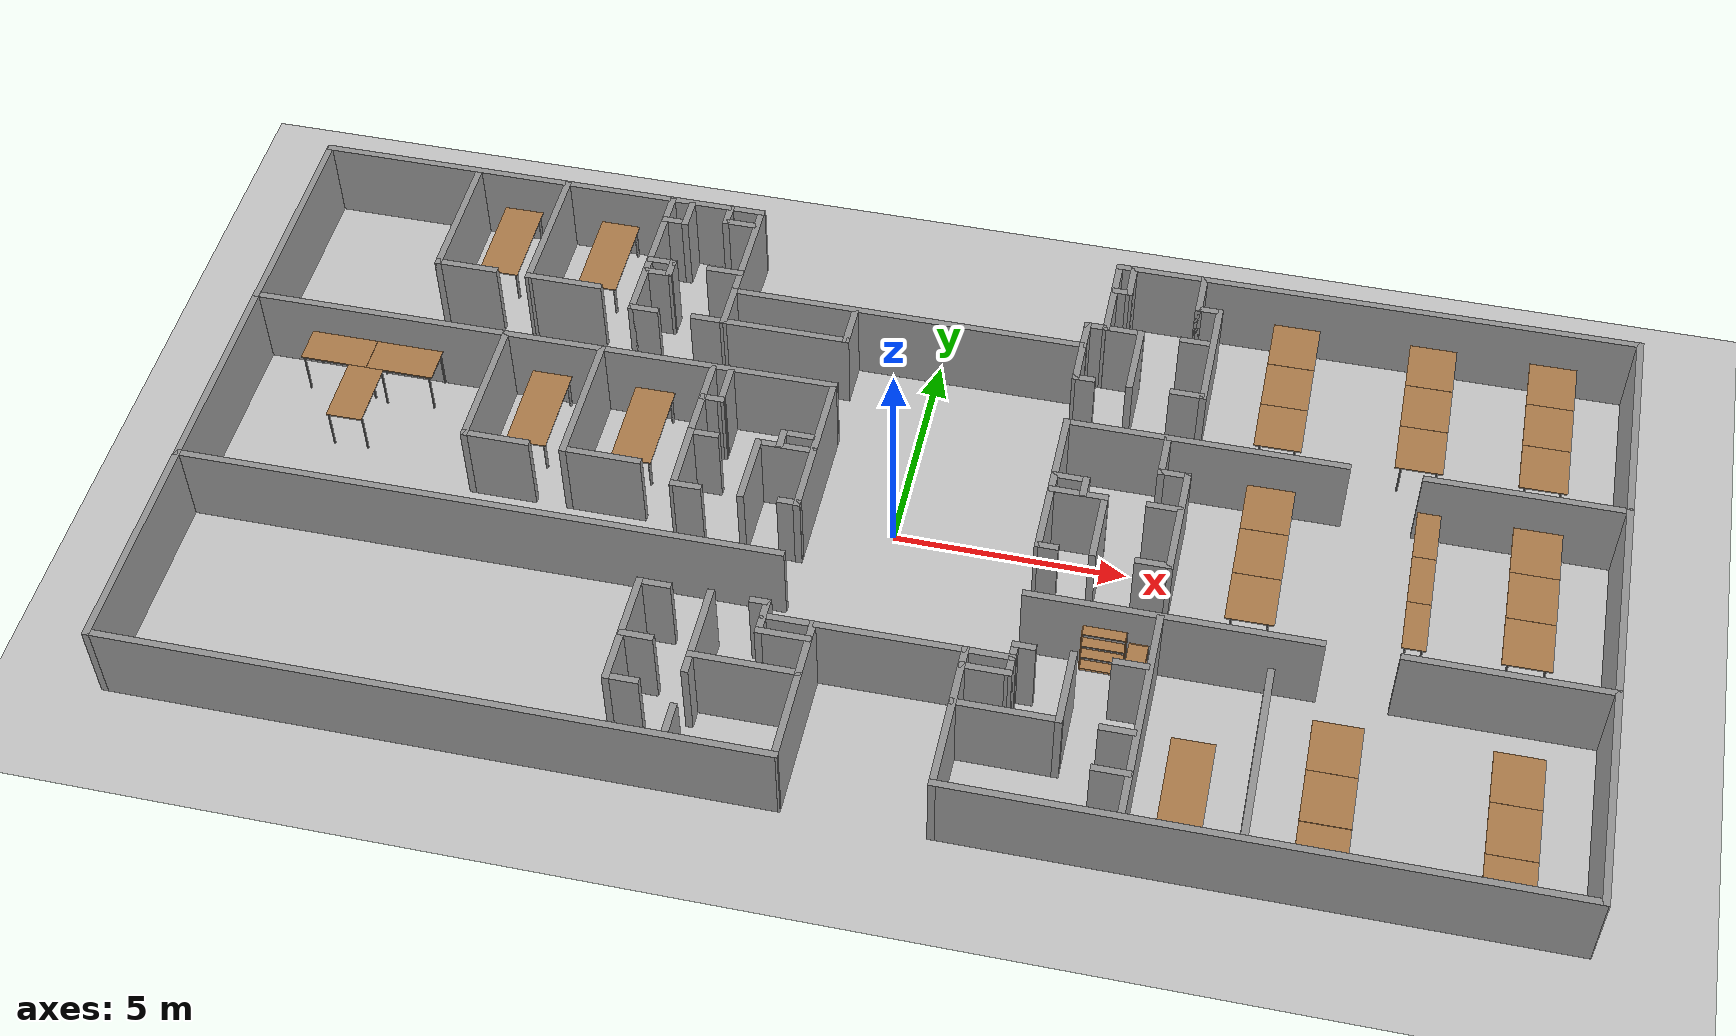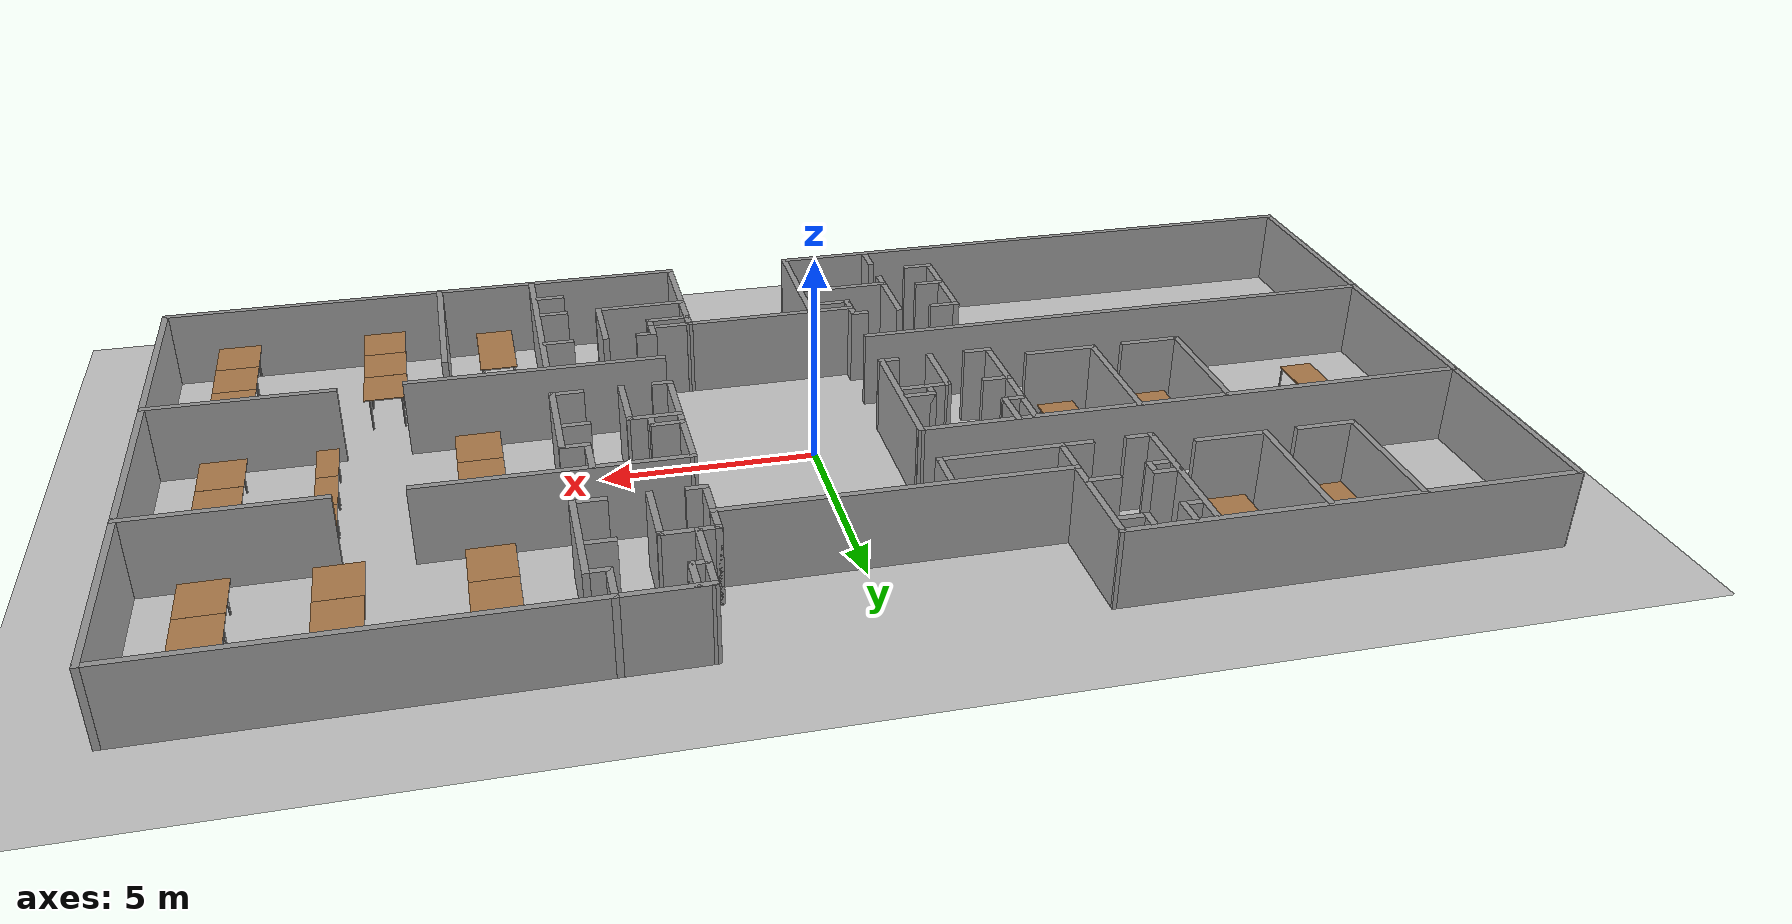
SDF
<sdf version="1.7">
 <world name="default">
  <light name="sun" type="directional">
   <pose>0 0 10 0 -0 0</pose>
   <diffuse>0.8 0.8 0.8 1</diffuse>
   <specular>0.2 0.2 0.2 1</specular>
   <attenuation>
    <range>1000</range>
    <constant>0.9</constant>
    <linear>0.01</linear>
    <quadratic>0.001</quadratic>
   </attenuation>
   <direction>-0.5 0.1 -0.9</direction>
   <spot><inner_angle>0</inner_angle><outer_angle>0</outer_angle><falloff>0</falloff></spot>
  </light>
  <gravity>0 0 -9.8</gravity>
  <magnetic_field>6e-06 2.3e-05 -4.2e-05</magnetic_field>
  <atmosphere type="adiabatic"/>
  <physics type="ode">
   <max_step_size>0.001</max_step_size>
   <real_time_factor>1</real_time_factor>
   <real_time_update_rate>1000</real_time_update_rate>
  </physics>
  <scene><ambient>0.4 0.4 0.4 1</ambient><background>0.7 0.7 0.7 1</background><shadows>1</shadows></scene>
  <audio><device>default</device></audio>
  <spherical_coordinates>
   <surface_model>EARTH_WGS84</surface_model>
   <latitude_deg>0</latitude_deg>
   <longitude_deg>0</longitude_deg>
   <elevation>0</elevation>
   <heading_deg>0</heading_deg>
  </spherical_coordinates>
  <model name="bookshelf">
   <static>1</static>
   <link name="link">
    <inertial><mass>1</mass></inertial>
    <collision name="back">
     <pose>0 0.005 0.6 0 -0 0</pose>
     <geometry><box><size>0.9 0.01 1.2</size></box></geometry>
    </collision>
    <visual name="visual1">
     <pose>0 0.005 0.6 0 -0 0</pose>
     <geometry><box><size>0.9 0.01 1.2</size></box></geometry>
     <material>
      <script><uri>file://media/materials/scripts/gazebo.material</uri><name>Gazebo/Wood</name></script>
     </material>
    </visual>
    <collision name="left_side">
     <pose>0.45 -0.195 0.6 0 -0 0</pose>
     <geometry><box><size>0.02 0.4 1.2</size></box></geometry>
    </collision>
    <visual name="visual2">
     <pose>0.45 -0.195 0.6 0 -0 0</pose>
     <geometry><box><size>0.02 0.4 1.2</size></box></geometry>
     <material>
      <script><uri>file://media/materials/scripts/gazebo.material</uri><name>Gazebo/Wood</name></script>
     </material>
    </visual>
    <collision name="right_side">
     <pose>-0.45 -0.195 0.6 0 -0 0</pose>
     <geometry><box><size>0.02 0.4 1.2</size></box></geometry>
    </collision>
    <visual name="visual3">
     <pose>-0.45 -0.195 0.6 0 -0 0</pose>
     <geometry><box><size>0.02 0.4 1.2</size></box></geometry>
     <material>
      <script><uri>file://media/materials/scripts/gazebo.material</uri><name>Gazebo/Wood</name></script>
     </material>
    </visual>
    <collision name="bottom">
     <pose>0 -0.195 0.03 0 -0 0</pose>
     <geometry><box><size>0.88 0.4 0.06</size></box></geometry>
    </collision>
    <visual name="visual4">
     <pose>0 -0.195 0.03 0 -0 0</pose>
     <geometry><box><size>0.88 0.4 0.06</size></box></geometry>
     <material>
      <script><uri>file://media/materials/scripts/gazebo.material</uri><name>Gazebo/Wood</name></script>
     </material>
    </visual>
    <collision name="top">
     <pose>0 -0.195 1.19 0 -0 0</pose>
     <geometry><box><size>0.88 0.4 0.02</size></box></geometry>
    </collision>
    <visual name="visual5">
     <pose>0 -0.195 1.19 0 -0 0</pose>
     <geometry><box><size>0.88 0.4 0.02</size></box></geometry>
     <material>
      <script><uri>file://media/materials/scripts/gazebo.material</uri><name>Gazebo/Wood</name></script>
     </material>
    </visual>
    <collision name="low_shelf">
     <pose>0 -0.195 0.43 0 -0 0</pose>
     <geometry><box><size>0.88 0.4 0.02</size></box></geometry>
    </collision>
    <visual name="visual6">
     <pose>0 -0.195 0.43 0 -0 0</pose>
     <geometry><box><size>0.88 0.4 0.02</size></box></geometry>
     <material>
      <script><uri>file://media/materials/scripts/gazebo.material</uri><name>Gazebo/Wood</name></script>
     </material>
    </visual>
    <collision name="high_shelf">
     <pose>0 -0.195 0.8 0 -0 0</pose>
     <geometry><box><size>0.88 0.4 0.02</size></box></geometry>
    </collision>
    <visual name="visual7">
     <pose>0 -0.195 0.8 0 -0 0</pose>
     <geometry><box><size>0.88 0.4 0.02</size></box></geometry>
     <material>
      <script><uri>file://media/materials/scripts/gazebo.material</uri><name>Gazebo/Wood</name></script>
     </material>
    </visual>
   </link>
   <pose>5.80085 -3.089 0 0 0 -1.58126</pose>
  </model>
  <model name="bookshelf_0">
   <link name="link">
    <inertial>
     <mass>0.599067</mass>
     <inertia>
      <ixx>0.00274522</ixx>
      <ixy>0</ixy>
      <ixz>0</ixz>
      <iyy>0.0386797</iyy>
      <iyz>0</iyz>
      <izz>0.041385</izz>
     </inertia>
    </inertial>
    <visual name="visual1">
     <pose>0 0.005 0.6 0 -0 0</pose>
     <geometry><box><size>0.9 0.006791 1.2</size></box></geometry>
     <material>
      <script><uri>file://media/materials/scripts/gazebo.material</uri><name>Gazebo/Wood</name></script>
      <shader type="pixel"/>
     </material>
    </visual>
    <visual name="visual2">
     <pose>0.45 -0.195 0.6 0 -0 0</pose>
     <geometry><box><size>0.02 0.233645 1.2</size></box></geometry>
     <material>
      <script><uri>file://media/materials/scripts/gazebo.material</uri><name>Gazebo/Wood</name></script>
      <shader type="pixel"/>
     </material>
    </visual>
    <visual name="visual3">
     <pose>-0.45 -0.195 0.6 0 -0 0</pose>
     <geometry><box><size>0.02 0.233645 1.2</size></box></geometry>
     <material>
      <script><uri>file://media/materials/scripts/gazebo.material</uri><name>Gazebo/Wood</name></script>
      <shader type="pixel"/>
     </material>
    </visual>
    <visual name="visual4">
     <pose>0 -0.195 0.03 0 -0 0</pose>
     <geometry><box><size>0.88 0.233645 0.06</size></box></geometry>
     <material>
      <script><uri>file://media/materials/scripts/gazebo.material</uri><name>Gazebo/Wood</name></script>
      <shader type="pixel"/>
     </material>
    </visual>
    <visual name="visual5">
     <pose>0 -0.195 1.19 0 -0 0</pose>
     <geometry><box><size>0.88 0.233645 0.02</size></box></geometry>
     <material>
      <script><uri>file://media/materials/scripts/gazebo.material</uri><name>Gazebo/Wood</name></script>
      <shader type="pixel"/>
     </material>
    </visual>
    <visual name="visual6">
     <pose>0 -0.195 0.43 0 -0 0</pose>
     <geometry><box><size>0.88 0.233645 0.02</size></box></geometry>
     <material>
      <script><uri>file://media/materials/scripts/gazebo.material</uri><name>Gazebo/Wood</name></script>
      <shader type="pixel"/>
     </material>
    </visual>
    <visual name="visual7">
     <pose>0 -0.195 0.8 0 -0 0</pose>
     <geometry><box><size>0.88 0.233645 0.02</size></box></geometry>
     <material>
      <script><uri>file://media/materials/scripts/gazebo.material</uri><name>Gazebo/Wood</name></script>
      <shader type="pixel"/>
     </material>
    </visual>
    <collision name="back">
     <pose>0 0.005 0.6 0 -0 0</pose>
     <geometry><box><size>0.9 0.006791 1.2</size></box></geometry>
     <surface>
      <friction>
       <ode><mu>1</mu><mu2>1</mu2><fdir1>0 0 0</fdir1><slip1>0</slip1><slip2>0</slip2></ode>
       <torsional>
        <coefficient>1</coefficient>
        <patch_radius>0</patch_radius>
        <surface_radius>0</surface_radius>
        <use_patch_radius>1</use_patch_radius>
        <ode><slip>0</slip></ode>
       </torsional>
      </friction>
      <bounce><restitution_coefficient>0</restitution_coefficient><threshold>1e+06</threshold></bounce>
      <contact>
       <collide_without_contact>0</collide_without_contact>
       <collide_without_contact_bitmask>1</collide_without_contact_bitmask>
       <collide_bitmask>1</collide_bitmask>
       <ode>
        <soft_cfm>0</soft_cfm>
        <soft_erp>0.2</soft_erp>
        <kp>1e+13</kp>
        <kd>1</kd>
        <max_vel>0.01</max_vel>
        <min_depth>0</min_depth>
       </ode>
       <bullet>
        <split_impulse>1</split_impulse>
        <split_impulse_penetration_threshold>-0.01</split_impulse_penetration_threshold>
        <soft_cfm>0</soft_cfm>
        <soft_erp>0.2</soft_erp>
        <kp>1e+13</kp>
        <kd>1</kd>
       </bullet>
      </contact>
     </surface>
    </collision>
    <collision name="left_side">
     <pose>0.45 -0.195 0.6 0 -0 0</pose>
     <geometry><box><size>0.02 0.233645 1.2</size></box></geometry>
     <surface>
      <friction>
       <ode><mu>1</mu><mu2>1</mu2><fdir1>0 0 0</fdir1><slip1>0</slip1><slip2>0</slip2></ode>
       <torsional>
        <coefficient>1</coefficient>
        <patch_radius>0</patch_radius>
        <surface_radius>0</surface_radius>
        <use_patch_radius>1</use_patch_radius>
        <ode><slip>0</slip></ode>
       </torsional>
      </friction>
      <bounce><restitution_coefficient>0</restitution_coefficient><threshold>1e+06</threshold></bounce>
      <contact>
       <collide_without_contact>0</collide_without_contact>
       <collide_without_contact_bitmask>1</collide_without_contact_bitmask>
       <collide_bitmask>1</collide_bitmask>
       <ode>
        <soft_cfm>0</soft_cfm>
        <soft_erp>0.2</soft_erp>
        <kp>1e+13</kp>
        <kd>1</kd>
        <max_vel>0.01</max_vel>
        <min_depth>0</min_depth>
       </ode>
       <bullet>
        <split_impulse>1</split_impulse>
        <split_impulse_penetration_threshold>-0.01</split_impulse_penetration_threshold>
        <soft_cfm>0</soft_cfm>
        <soft_erp>0.2</soft_erp>
        <kp>1e+13</kp>
        <kd>1</kd>
       </bullet>
      </contact>
     </surface>
    </collision>
    <collision name="right_side">
     <pose>-0.45 -0.195 0.6 0 -0 0</pose>
     <geometry><box><size>0.02 0.233645 1.2</size></box></geometry>
     <surface>
      <friction>
       <ode><mu>1</mu><mu2>1</mu2><fdir1>0 0 0</fdir1><slip1>0</slip1><slip2>0</slip2></ode>
       <torsional>
        <coefficient>1</coefficient>
        <patch_radius>0</patch_radius>
        <surface_radius>0</surface_radius>
        <use_patch_radius>1</use_patch_radius>
        <ode><slip>0</slip></ode>
       </torsional>
      </friction>
      <bounce><restitution_coefficient>0</restitution_coefficient><threshold>1e+06</threshold></bounce>
      <contact>
       <collide_without_contact>0</collide_without_contact>
       <collide_without_contact_bitmask>1</collide_without_contact_bitmask>
       <collide_bitmask>1</collide_bitmask>
       <ode>
        <soft_cfm>0</soft_cfm>
        <soft_erp>0.2</soft_erp>
        <kp>1e+13</kp>
        <kd>1</kd>
        <max_vel>0.01</max_vel>
        <min_depth>0</min_depth>
       </ode>
       <bullet>
        <split_impulse>1</split_impulse>
        <split_impulse_penetration_threshold>-0.01</split_impulse_penetration_threshold>
        <soft_cfm>0</soft_cfm>
        <soft_erp>0.2</soft_erp>
        <kp>1e+13</kp>
        <kd>1</kd>
       </bullet>
      </contact>
     </surface>
    </collision>
    <collision name="bottom">
     <pose>0 -0.195 0.03 0 -0 0</pose>
     <geometry><box><size>0.88 0.233645 0.06</size></box></geometry>
     <surface>
      <friction>
       <ode><mu>1</mu><mu2>1</mu2><fdir1>0 0 0</fdir1><slip1>0</slip1><slip2>0</slip2></ode>
       <torsional>
        <coefficient>1</coefficient>
        <patch_radius>0</patch_radius>
        <surface_radius>0</surface_radius>
        <use_patch_radius>1</use_patch_radius>
        <ode><slip>0</slip></ode>
       </torsional>
      </friction>
      <bounce><restitution_coefficient>0</restitution_coefficient><threshold>1e+06</threshold></bounce>
      <contact>
       <collide_without_contact>0</collide_without_contact>
       <collide_without_contact_bitmask>1</collide_without_contact_bitmask>
       <collide_bitmask>1</collide_bitmask>
       <ode>
        <soft_cfm>0</soft_cfm>
        <soft_erp>0.2</soft_erp>
        <kp>1e+13</kp>
        <kd>1</kd>
        <max_vel>0.01</max_vel>
        <min_depth>0</min_depth>
       </ode>
       <bullet>
        <split_impulse>1</split_impulse>
        <split_impulse_penetration_threshold>-0.01</split_impulse_penetration_threshold>
        <soft_cfm>0</soft_cfm>
        <soft_erp>0.2</soft_erp>
        <kp>1e+13</kp>
        <kd>1</kd>
       </bullet>
      </contact>
     </surface>
    </collision>
    <collision name="top">
     <pose>0 -0.195 1.19 0 -0 0</pose>
     <geometry><box><size>0.88 0.233645 0.02</size></box></geometry>
     <surface>
      <friction>
       <ode><mu>1</mu><mu2>1</mu2><fdir1>0 0 0</fdir1><slip1>0</slip1><slip2>0</slip2></ode>
       <torsional>
        <coefficient>1</coefficient>
        <patch_radius>0</patch_radius>
        <surface_radius>0</surface_radius>
        <use_patch_radius>1</use_patch_radius>
        <ode><slip>0</slip></ode>
       </torsional>
      </friction>
      <bounce><restitution_coefficient>0</restitution_coefficient><threshold>1e+06</threshold></bounce>
      <contact>
       <collide_without_contact>0</collide_without_contact>
       <collide_without_contact_bitmask>1</collide_without_contact_bitmask>
       <collide_bitmask>1</collide_bitmask>
       <ode>
        <soft_cfm>0</soft_cfm>
        <soft_erp>0.2</soft_erp>
        <kp>1e+13</kp>
        <kd>1</kd>
        <max_vel>0.01</max_vel>
        <min_depth>0</min_depth>
       </ode>
       <bullet>
        <split_impulse>1</split_impulse>
        <split_impulse_penetration_threshold>-0.01</split_impulse_penetration_threshold>
        <soft_cfm>0</soft_cfm>
        <soft_erp>0.2</soft_erp>
        <kp>1e+13</kp>
        <kd>1</kd>
       </bullet>
      </contact>
     </surface>
    </collision>
    <collision name="low_shelf">
     <pose>0 -0.195 0.43 0 -0 0</pose>
     <geometry><box><size>0.88 0.233645 0.02</size></box></geometry>
     <surface>
      <friction>
       <ode><mu>1</mu><mu2>1</mu2><fdir1>0 0 0</fdir1><slip1>0</slip1><slip2>0</slip2></ode>
       <torsional>
        <coefficient>1</coefficient>
        <patch_radius>0</patch_radius>
        <surface_radius>0</surface_radius>
        <use_patch_radius>1</use_patch_radius>
        <ode><slip>0</slip></ode>
       </torsional>
      </friction>
      <bounce><restitution_coefficient>0</restitution_coefficient><threshold>1e+06</threshold></bounce>
      <contact>
       <collide_without_contact>0</collide_without_contact>
       <collide_without_contact_bitmask>1</collide_without_contact_bitmask>
       <collide_bitmask>1</collide_bitmask>
       <ode>
        <soft_cfm>0</soft_cfm>
        <soft_erp>0.2</soft_erp>
        <kp>1e+13</kp>
        <kd>1</kd>
        <max_vel>0.01</max_vel>
        <min_depth>0</min_depth>
       </ode>
       <bullet>
        <split_impulse>1</split_impulse>
        <split_impulse_penetration_threshold>-0.01</split_impulse_penetration_threshold>
        <soft_cfm>0</soft_cfm>
        <soft_erp>0.2</soft_erp>
        <kp>1e+13</kp>
        <kd>1</kd>
       </bullet>
      </contact>
     </surface>
    </collision>
    <collision name="high_shelf">
     <pose>0 -0.195 0.8 0 -0 0</pose>
     <geometry><box><size>0.88 0.233645 0.02</size></box></geometry>
     <surface>
      <friction>
       <ode><mu>1</mu><mu2>1</mu2><fdir1>0 0 0</fdir1><slip1>0</slip1><slip2>0</slip2></ode>
       <torsional>
        <coefficient>1</coefficient>
        <patch_radius>0</patch_radius>
        <surface_radius>0</surface_radius>
        <use_patch_radius>1</use_patch_radius>
        <ode><slip>0</slip></ode>
       </torsional>
      </friction>
      <bounce><restitution_coefficient>0</restitution_coefficient><threshold>1e+06</threshold></bounce>
      <contact>
       <collide_without_contact>0</collide_without_contact>
       <collide_without_contact_bitmask>1</collide_without_contact_bitmask>
       <collide_bitmask>1</collide_bitmask>
       <ode>
        <soft_cfm>0</soft_cfm>
        <soft_erp>0.2</soft_erp>
        <kp>1e+13</kp>
        <kd>1</kd>
        <max_vel>0.01</max_vel>
        <min_depth>0</min_depth>
       </ode>
       <bullet>
        <split_impulse>1</split_impulse>
        <split_impulse_penetration_threshold>-0.01</split_impulse_penetration_threshold>
        <soft_cfm>0</soft_cfm>
        <soft_erp>0.2</soft_erp>
        <kp>1e+13</kp>
        <kd>1</kd>
       </bullet>
      </contact>
     </surface>
    </collision>
   </link>
   <static>1</static>
   <pose>4.8873 -2.30096 0 0 -0 0</pose>
  </model>
  <model name="table">
   <static>1</static>
   <link name="link">
    <collision name="surface">
     <pose>0 0 1 0 -0 0</pose>
     <geometry><box><size>1.5 0.8 0.03</size></box></geometry>
     <surface><friction><ode><mu>0.6</mu><mu2>0.6</mu2></ode></friction></surface>
    </collision>
    <visual name="visual1">
     <pose>0 0 1 0 -0 0</pose>
     <geometry><box><size>1.5 0.8 0.03</size></box></geometry>
     <material>
      <script><uri>file://media/materials/scripts/gazebo.material</uri><name>Gazebo/Wood</name></script>
     </material>
    </visual>
    <collision name="front_left_leg">
     <pose>0.68 0.38 0.5 0 -0 0</pose>
     <geometry><cylinder><radius>0.02</radius><length>1</length></cylinder></geometry>
    </collision>
    <visual name="front_left_leg">
     <pose>0.68 0.38 0.5 0 -0 0</pose>
     <geometry><cylinder><radius>0.02</radius><length>1</length></cylinder></geometry>
     <material>
      <script><uri>file://media/materials/scripts/gazebo.material</uri><name>Gazebo/Grey</name></script>
     </material>
    </visual>
    <collision name="front_right_leg">
     <pose>0.68 -0.38 0.5 0 -0 0</pose>
     <geometry><cylinder><radius>0.02</radius><length>1</length></cylinder></geometry>
    </collision>
    <visual name="front_right_leg">
     <pose>0.68 -0.38 0.5 0 -0 0</pose>
     <geometry><cylinder><radius>0.02</radius><length>1</length></cylinder></geometry>
     <material>
      <script><uri>file://media/materials/scripts/gazebo.material</uri><name>Gazebo/Grey</name></script>
     </material>
    </visual>
    <collision name="back_right_leg">
     <pose>-0.68 -0.38 0.5 0 -0 0</pose>
     <geometry><cylinder><radius>0.02</radius><length>1</length></cylinder></geometry>
    </collision>
    <visual name="back_right_leg">
     <pose>-0.68 -0.38 0.5 0 -0 0</pose>
     <geometry><cylinder><radius>0.02</radius><length>1</length></cylinder></geometry>
     <material>
      <script><uri>file://media/materials/scripts/gazebo.material</uri><name>Gazebo/Grey</name></script>
     </material>
    </visual>
    <collision name="back_left_leg">
     <pose>-0.68 0.38 0.5 0 -0 0</pose>
     <geometry><cylinder><radius>0.02</radius><length>1</length></cylinder></geometry>
    </collision>
    <visual name="back_left_leg">
     <pose>-0.68 0.38 0.5 0 -0 0</pose>
     <geometry><cylinder><radius>0.02</radius><length>1</length></cylinder></geometry>
     <material>
      <script><uri>file://media/materials/scripts/gazebo.material</uri><name>Gazebo/Grey</name></script>
     </material>
    </visual>
   </link>
   <pose>-12.9377 1.89351 0 0 -0 0</pose>
  </model>
  <model name="table_0">
   <static>1</static>
   <link name="link">
    <collision name="surface">
     <pose>0 0 1 0 -0 0</pose>
     <geometry><box><size>1.5 0.8 0.03</size></box></geometry>
     <surface><friction><ode><mu>0.6</mu><mu2>0.6</mu2></ode></friction></surface>
    </collision>
    <visual name="visual1">
     <pose>0 0 1 0 -0 0</pose>
     <geometry><box><size>1.5 0.8 0.03</size></box></geometry>
     <material>
      <script><uri>file://media/materials/scripts/gazebo.material</uri><name>Gazebo/Wood</name></script>
     </material>
    </visual>
    <collision name="front_left_leg">
     <pose>0.68 0.38 0.5 0 -0 0</pose>
     <geometry><cylinder><radius>0.02</radius><length>1</length></cylinder></geometry>
    </collision>
    <visual name="front_left_leg">
     <pose>0.68 0.38 0.5 0 -0 0</pose>
     <geometry><cylinder><radius>0.02</radius><length>1</length></cylinder></geometry>
     <material>
      <script><uri>file://media/materials/scripts/gazebo.material</uri><name>Gazebo/Grey</name></script>
     </material>
    </visual>
    <collision name="front_right_leg">
     <pose>0.68 -0.38 0.5 0 -0 0</pose>
     <geometry><cylinder><radius>0.02</radius><length>1</length></cylinder></geometry>
    </collision>
    <visual name="front_right_leg">
     <pose>0.68 -0.38 0.5 0 -0 0</pose>
     <geometry><cylinder><radius>0.02</radius><length>1</length></cylinder></geometry>
     <material>
      <script><uri>file://media/materials/scripts/gazebo.material</uri><name>Gazebo/Grey</name></script>
     </material>
    </visual>
    <collision name="back_right_leg">
     <pose>-0.68 -0.38 0.5 0 -0 0</pose>
     <geometry><cylinder><radius>0.02</radius><length>1</length></cylinder></geometry>
    </collision>
    <visual name="back_right_leg">
     <pose>-0.68 -0.38 0.5 0 -0 0</pose>
     <geometry><cylinder><radius>0.02</radius><length>1</length></cylinder></geometry>
     <material>
      <script><uri>file://media/materials/scripts/gazebo.material</uri><name>Gazebo/Grey</name></script>
     </material>
    </visual>
    <collision name="back_left_leg">
     <pose>-0.68 0.38 0.5 0 -0 0</pose>
     <geometry><cylinder><radius>0.02</radius><length>1</length></cylinder></geometry>
    </collision>
    <visual name="back_left_leg">
     <pose>-0.68 0.38 0.5 0 -0 0</pose>
     <geometry><cylinder><radius>0.02</radius><length>1</length></cylinder></geometry>
     <material>
      <script><uri>file://media/materials/scripts/gazebo.material</uri><name>Gazebo/Grey</name></script>
     </material>
    </visual>
   </link>
   <pose>-11.4297 1.89153 0 0 -0 0</pose>
  </model>
  <model name="table_1">
   <static>1</static>
   <link name="link">
    <collision name="surface">
     <pose>0 0 1 0 -0 0</pose>
     <geometry><box><size>1.5 0.8 0.03</size></box></geometry>
     <surface><friction><ode><mu>0.6</mu><mu2>0.6</mu2></ode></friction></surface>
    </collision>
    <visual name="visual1">
     <pose>0 0 1 0 -0 0</pose>
     <geometry><box><size>1.5 0.8 0.03</size></box></geometry>
     <material>
      <script><uri>file://media/materials/scripts/gazebo.material</uri><name>Gazebo/Wood</name></script>
     </material>
    </visual>
    <collision name="front_left_leg">
     <pose>0.68 0.38 0.5 0 -0 0</pose>
     <geometry><cylinder><radius>0.02</radius><length>1</length></cylinder></geometry>
    </collision>
    <visual name="front_left_leg">
     <pose>0.68 0.38 0.5 0 -0 0</pose>
     <geometry><cylinder><radius>0.02</radius><length>1</length></cylinder></geometry>
     <material>
      <script><uri>file://media/materials/scripts/gazebo.material</uri><name>Gazebo/Grey</name></script>
     </material>
    </visual>
    <collision name="front_right_leg">
     <pose>0.68 -0.38 0.5 0 -0 0</pose>
     <geometry><cylinder><radius>0.02</radius><length>1</length></cylinder></geometry>
    </collision>
    <visual name="front_right_leg">
     <pose>0.68 -0.38 0.5 0 -0 0</pose>
     <geometry><cylinder><radius>0.02</radius><length>1</length></cylinder></geometry>
     <material>
      <script><uri>file://media/materials/scripts/gazebo.material</uri><name>Gazebo/Grey</name></script>
     </material>
    </visual>
    <collision name="back_right_leg">
     <pose>-0.68 -0.38 0.5 0 -0 0</pose>
     <geometry><cylinder><radius>0.02</radius><length>1</length></cylinder></geometry>
    </collision>
    <visual name="back_right_leg">
     <pose>-0.68 -0.38 0.5 0 -0 0</pose>
     <geometry><cylinder><radius>0.02</radius><length>1</length></cylinder></geometry>
     <material>
      <script><uri>file://media/materials/scripts/gazebo.material</uri><name>Gazebo/Grey</name></script>
     </material>
    </visual>
    <collision name="back_left_leg">
     <pose>-0.68 0.38 0.5 0 -0 0</pose>
     <geometry><cylinder><radius>0.02</radius><length>1</length></cylinder></geometry>
    </collision>
    <visual name="back_left_leg">
     <pose>-0.68 0.38 0.5 0 -0 0</pose>
     <geometry><cylinder><radius>0.02</radius><length>1</length></cylinder></geometry>
     <material>
      <script><uri>file://media/materials/scripts/gazebo.material</uri><name>Gazebo/Grey</name></script>
     </material>
    </visual>
   </link>
   <pose>-12.1826 0.74531 0 0 0 -1.56271</pose>
  </model>
  <model name="work_station">
   <link name="link">
    <inertial>
     <inertia><ixx>0</ixx><ixy>0</ixy><ixz>0</ixz><iyy>0</iyy><iyz>0</iyz><izz>0</izz></inertia>
     <mass>0</mass>
    </inertial>
    <visual name="back_right_leg">
     <pose>-0.53 -0.38 0.42 0 -0 0</pose>
     <geometry><cylinder><radius>0.0207459</radius><length>0.822541</length></cylinder></geometry>
     <material>
      <script><uri>file://media/materials/scripts/gazebo.material</uri><name>Gazebo/Grey</name></script>
      <shader type="pixel"><normal_map>__default__</normal_map></shader>
      <ambient>0.3 0.3 0.3 1</ambient>
      <diffuse>0.7 0.7 0.7 1</diffuse>
      <specular>0.01 0.01 0.01 1</specular>
      <emissive>0 0 0 1</emissive>
     </material>
    </visual>
    <visual name="back_left_leg">
     <pose>-0.53 0.38 0.42 0 -0 0</pose>
     <geometry><cylinder><radius>0.0207459</radius><length>0.822541</length></cylinder></geometry>
     <material>
      <script><uri>file://media/materials/scripts/gazebo.material</uri><name>Gazebo/Grey</name></script>
      <shader type="pixel"><normal_map>__default__</normal_map></shader>
      <ambient>0.3 0.3 0.3 1</ambient>
      <diffuse>0.7 0.7 0.7 1</diffuse>
      <specular>0.01 0.01 0.01 1</specular>
      <emissive>0 0 0 1</emissive>
     </material>
    </visual>
    <visual name="front_left_leg">
     <pose>0.53 0.38 0.42 0 -0 0</pose>
     <geometry><cylinder><radius>0.0207459</radius><length>0.822541</length></cylinder></geometry>
     <material>
      <script><uri>file://media/materials/scripts/gazebo.material</uri><name>Gazebo/Grey</name></script>
      <shader type="pixel"><normal_map>__default__</normal_map></shader>
      <ambient>0.3 0.3 0.3 1</ambient>
      <diffuse>0.7 0.7 0.7 1</diffuse>
      <specular>0.01 0.01 0.01 1</specular>
      <emissive>0 0 0 1</emissive>
     </material>
    </visual>
    <visual name="visual1">
     <pose>0 0 0.84 0 -0 0</pose>
     <geometry><box><size>1.21551 1.02942 0.025485</size></box></geometry>
     <material>
      <script><uri>file://media/materials/scripts/gazebo.material</uri><name>Gazebo/Wood</name></script>
      <shader type="pixel"><normal_map>__default__</normal_map></shader>
      <ambient>1 1 1 1</ambient>
      <diffuse>1 1 1 1</diffuse>
      <specular>0.2 0.2 0.2 1</specular>
      <emissive>0 0 0 1</emissive>
     </material>
    </visual>
    <visual name="front_right_leg">
     <pose>0.53 -0.38 0.42 0 -0 0</pose>
     <geometry><cylinder><radius>0.0207459</radius><length>0.822541</length></cylinder></geometry>
     <material>
      <script><uri>file://media/materials/scripts/gazebo.material</uri><name>Gazebo/Grey</name></script>
      <shader type="pixel"><normal_map>__default__</normal_map></shader>
      <ambient>0.3 0.3 0.3 1</ambient>
      <diffuse>0.7 0.7 0.7 1</diffuse>
      <specular>0.01 0.01 0.01 1</specular>
      <emissive>0 0 0 1</emissive>
     </material>
    </visual>
    <collision name="surface">
     <pose>0 0 0.84 0 -0 0</pose>
     <geometry><box><size>1.21551 1.02942 0.025485</size></box></geometry>
     <surface>
      <friction>
       <ode><mu>0.6</mu><mu2>0.6</mu2><fdir1>0 0 0</fdir1><slip1>0</slip1><slip2>0</slip2></ode>
       <torsional>
        <coefficient>1</coefficient>
        <patch_radius>0</patch_radius>
        <surface_radius>0</surface_radius>
        <use_patch_radius>1</use_patch_radius>
        <ode><slip>0</slip></ode>
       </torsional>
      </friction>
      <bounce><restitution_coefficient>0</restitution_coefficient><threshold>1e+06</threshold></bounce>
      <contact>
       <collide_without_contact>0</collide_without_contact>
       <collide_without_contact_bitmask>1</collide_without_contact_bitmask>
       <collide_bitmask>1</collide_bitmask>
       <ode>
        <soft_cfm>0</soft_cfm>
        <soft_erp>0.2</soft_erp>
        <kp>1e+13</kp>
        <kd>1</kd>
        <max_vel>0.01</max_vel>
        <min_depth>0</min_depth>
       </ode>
       <bullet>
        <split_impulse>1</split_impulse>
        <split_impulse_penetration_threshold>-0.01</split_impulse_penetration_threshold>
        <soft_cfm>0</soft_cfm>
        <soft_erp>0.2</soft_erp>
        <kp>1e+13</kp>
        <kd>1</kd>
       </bullet>
      </contact>
     </surface>
    </collision>
    <collision name="front_left_leg">
     <pose>0.53 0.38 0.42 0 -0 0</pose>
     <geometry><cylinder><radius>0.020746</radius><length>0.822541</length></cylinder></geometry>
     <surface>
      <friction>
       <ode><mu>1</mu><mu2>1</mu2><fdir1>0 0 0</fdir1><slip1>0</slip1><slip2>0</slip2></ode>
       <torsional>
        <coefficient>1</coefficient>
        <patch_radius>0</patch_radius>
        <surface_radius>0</surface_radius>
        <use_patch_radius>1</use_patch_radius>
        <ode><slip>0</slip></ode>
       </torsional>
      </friction>
      <bounce><restitution_coefficient>0</restitution_coefficient><threshold>1e+06</threshold></bounce>
      <contact>
       <collide_without_contact>0</collide_without_contact>
       <collide_without_contact_bitmask>1</collide_without_contact_bitmask>
       <collide_bitmask>1</collide_bitmask>
       <ode>
        <soft_cfm>0</soft_cfm>
        <soft_erp>0.2</soft_erp>
        <kp>1e+13</kp>
        <kd>1</kd>
        <max_vel>0.01</max_vel>
        <min_depth>0</min_depth>
       </ode>
       <bullet>
        <split_impulse>1</split_impulse>
        <split_impulse_penetration_threshold>-0.01</split_impulse_penetration_threshold>
        <soft_cfm>0</soft_cfm>
        <soft_erp>0.2</soft_erp>
        <kp>1e+13</kp>
        <kd>1</kd>
       </bullet>
      </contact>
     </surface>
    </collision>
    <collision name="front_right_leg">
     <pose>0.53 -0.38 0.42 0 -0 0</pose>
     <geometry><cylinder><radius>0.020746</radius><length>0.822541</length></cylinder></geometry>
     <surface>
      <friction>
       <ode><mu>1</mu><mu2>1</mu2><fdir1>0 0 0</fdir1><slip1>0</slip1><slip2>0</slip2></ode>
       <torsional>
        <coefficient>1</coefficient>
        <patch_radius>0</patch_radius>
        <surface_radius>0</surface_radius>
        <use_patch_radius>1</use_patch_radius>
        <ode><slip>0</slip></ode>
       </torsional>
      </friction>
      <bounce><restitution_coefficient>0</restitution_coefficient><threshold>1e+06</threshold></bounce>
      <contact>
       <collide_without_contact>0</collide_without_contact>
       <collide_without_contact_bitmask>1</collide_without_contact_bitmask>
       <collide_bitmask>1</collide_bitmask>
       <ode>
        <soft_cfm>0</soft_cfm>
        <soft_erp>0.2</soft_erp>
        <kp>1e+13</kp>
        <kd>1</kd>
        <max_vel>0.01</max_vel>
        <min_depth>0</min_depth>
       </ode>
       <bullet>
        <split_impulse>1</split_impulse>
        <split_impulse_penetration_threshold>-0.01</split_impulse_penetration_threshold>
        <soft_cfm>0</soft_cfm>
        <soft_erp>0.2</soft_erp>
        <kp>1e+13</kp>
        <kd>1</kd>
       </bullet>
      </contact>
     </surface>
    </collision>
    <collision name="back_right_leg">
     <pose>-0.53 -0.38 0.42 0 -0 0</pose>
     <geometry><cylinder><radius>0.020746</radius><length>0.822541</length></cylinder></geometry>
     <surface>
      <friction>
       <ode><mu>1</mu><mu2>1</mu2><fdir1>0 0 0</fdir1><slip1>0</slip1><slip2>0</slip2></ode>
       <torsional>
        <coefficient>1</coefficient>
        <patch_radius>0</patch_radius>
        <surface_radius>0</surface_radius>
        <use_patch_radius>1</use_patch_radius>
        <ode><slip>0</slip></ode>
       </torsional>
      </friction>
      <bounce><restitution_coefficient>0</restitution_coefficient><threshold>1e+06</threshold></bounce>
      <contact>
       <collide_without_contact>0</collide_without_contact>
       <collide_without_contact_bitmask>1</collide_without_contact_bitmask>
       <collide_bitmask>1</collide_bitmask>
       <ode>
        <soft_cfm>0</soft_cfm>
        <soft_erp>0.2</soft_erp>
        <kp>1e+13</kp>
        <kd>1</kd>
        <max_vel>0.01</max_vel>
        <min_depth>0</min_depth>
       </ode>
       <bullet>
        <split_impulse>1</split_impulse>
        <split_impulse_penetration_threshold>-0.01</split_impulse_penetration_threshold>
        <soft_cfm>0</soft_cfm>
        <soft_erp>0.2</soft_erp>
        <kp>1e+13</kp>
        <kd>1</kd>
       </bullet>
      </contact>
     </surface>
    </collision>
    <collision name="back_left_leg">
     <pose>-0.53 0.38 0.42 0 -0 0</pose>
     <geometry><cylinder><radius>0.020746</radius><length>0.822541</length></cylinder></geometry>
     <surface>
      <friction>
       <ode><mu>1</mu><mu2>1</mu2><fdir1>0 0 0</fdir1><slip1>0</slip1><slip2>0</slip2></ode>
       <torsional>
        <coefficient>1</coefficient>
        <patch_radius>0</patch_radius>
        <surface_radius>0</surface_radius>
        <use_patch_radius>1</use_patch_radius>
        <ode><slip>0</slip></ode>
       </torsional>
      </friction>
      <bounce><restitution_coefficient>0</restitution_coefficient><threshold>1e+06</threshold></bounce>
      <contact>
       <collide_without_contact>0</collide_without_contact>
       <collide_without_contact_bitmask>1</collide_without_contact_bitmask>
       <collide_bitmask>1</collide_bitmask>
       <ode>
        <soft_cfm>0</soft_cfm>
        <soft_erp>0.2</soft_erp>
        <kp>1e+13</kp>
        <kd>1</kd>
        <max_vel>0.01</max_vel>
        <min_depth>0</min_depth>
       </ode>
       <bullet>
        <split_impulse>1</split_impulse>
        <split_impulse_penetration_threshold>-0.01</split_impulse_penetration_threshold>
        <soft_cfm>0</soft_cfm>
        <soft_erp>0.2</soft_erp>
        <kp>1e+13</kp>
        <kd>1</kd>
       </bullet>
      </contact>
     </surface>
    </collision>
   </link>
   <static>1</static>
   <pose>9.79017 -6.53361 -0.011225 0 0 -1.56528</pose>
  </model>
  <model name="work_station_clone">
   <link name="link">
    <inertial>
     <inertia><ixx>0</ixx><ixy>0</ixy><ixz>0</ixz><iyy>0</iyy><iyz>0</iyz><izz>0</izz></inertia>
     <mass>0</mass>
    </inertial>
    <visual name="back_right_leg">
     <pose>-0.53 -0.38 0.42 0 -0 0</pose>
     <geometry><cylinder><radius>0.0207459</radius><length>0.822541</length></cylinder></geometry>
     <material>
      <script><uri>file://media/materials/scripts/gazebo.material</uri><name>Gazebo/Grey</name></script>
      <shader type="pixel"><normal_map>__default__</normal_map></shader>
      <ambient>0.3 0.3 0.3 1</ambient>
      <diffuse>0.7 0.7 0.7 1</diffuse>
      <specular>0.01 0.01 0.01 1</specular>
      <emissive>0 0 0 1</emissive>
     </material>
    </visual>
    <visual name="back_left_leg">
     <pose>-0.53 0.38 0.42 0 -0 0</pose>
     <geometry><cylinder><radius>0.0207459</radius><length>0.822541</length></cylinder></geometry>
     <material>
      <script><uri>file://media/materials/scripts/gazebo.material</uri><name>Gazebo/Grey</name></script>
      <shader type="pixel"><normal_map>__default__</normal_map></shader>
      <ambient>0.3 0.3 0.3 1</ambient>
      <diffuse>0.7 0.7 0.7 1</diffuse>
      <specular>0.01 0.01 0.01 1</specular>
      <emissive>0 0 0 1</emissive>
     </material>
    </visual>
    <visual name="front_left_leg">
     <pose>0.53 0.38 0.42 0 -0 0</pose>
     <geometry><cylinder><radius>0.0207459</radius><length>0.822541</length></cylinder></geometry>
     <material>
      <script><uri>file://media/materials/scripts/gazebo.material</uri><name>Gazebo/Grey</name></script>
      <shader type="pixel"><normal_map>__default__</normal_map></shader>
      <ambient>0.3 0.3 0.3 1</ambient>
      <diffuse>0.7 0.7 0.7 1</diffuse>
      <specular>0.01 0.01 0.01 1</specular>
      <emissive>0 0 0 1</emissive>
     </material>
    </visual>
    <visual name="visual1">
     <pose>0 0 0.84 0 -0 0</pose>
     <geometry><box><size>1.21551 1.02942 0.025485</size></box></geometry>
     <material>
      <script><uri>file://media/materials/scripts/gazebo.material</uri><name>Gazebo/Wood</name></script>
      <shader type="pixel"><normal_map>__default__</normal_map></shader>
      <ambient>1 1 1 1</ambient>
      <diffuse>1 1 1 1</diffuse>
      <specular>0.2 0.2 0.2 1</specular>
      <emissive>0 0 0 1</emissive>
     </material>
    </visual>
    <visual name="front_right_leg">
     <pose>0.53 -0.38 0.42 0 -0 0</pose>
     <geometry><cylinder><radius>0.0207459</radius><length>0.822541</length></cylinder></geometry>
     <material>
      <script><uri>file://media/materials/scripts/gazebo.material</uri><name>Gazebo/Grey</name></script>
      <shader type="pixel"><normal_map>__default__</normal_map></shader>
      <ambient>0.3 0.3 0.3 1</ambient>
      <diffuse>0.7 0.7 0.7 1</diffuse>
      <specular>0.01 0.01 0.01 1</specular>
      <emissive>0 0 0 1</emissive>
     </material>
    </visual>
    <collision name="surface">
     <pose>0 0 0.84 0 -0 0</pose>
     <geometry><box><size>1.21551 1.02942 0.025485</size></box></geometry>
     <surface>
      <friction>
       <ode><mu>0.6</mu><mu2>0.6</mu2><fdir1>0 0 0</fdir1><slip1>0</slip1><slip2>0</slip2></ode>
       <torsional>
        <coefficient>1</coefficient>
        <patch_radius>0</patch_radius>
        <surface_radius>0</surface_radius>
        <use_patch_radius>1</use_patch_radius>
        <ode><slip>0</slip></ode>
       </torsional>
      </friction>
      <bounce><restitution_coefficient>0</restitution_coefficient><threshold>1e+06</threshold></bounce>
      <contact>
       <collide_without_contact>0</collide_without_contact>
       <collide_without_contact_bitmask>1</collide_without_contact_bitmask>
       <collide_bitmask>1</collide_bitmask>
       <ode>
        <soft_cfm>0</soft_cfm>
        <soft_erp>0.2</soft_erp>
        <kp>1e+13</kp>
        <kd>1</kd>
        <max_vel>0.01</max_vel>
        <min_depth>0</min_depth>
       </ode>
       <bullet>
        <split_impulse>1</split_impulse>
        <split_impulse_penetration_threshold>-0.01</split_impulse_penetration_threshold>
        <soft_cfm>0</soft_cfm>
        <soft_erp>0.2</soft_erp>
        <kp>1e+13</kp>
        <kd>1</kd>
       </bullet>
      </contact>
     </surface>
    </collision>
    <collision name="front_left_leg">
     <pose>0.53 0.38 0.42 0 -0 0</pose>
     <geometry><cylinder><radius>0.020746</radius><length>0.822541</length></cylinder></geometry>
     <surface>
      <friction>
       <ode><mu>1</mu><mu2>1</mu2><fdir1>0 0 0</fdir1><slip1>0</slip1><slip2>0</slip2></ode>
       <torsional>
        <coefficient>1</coefficient>
        <patch_radius>0</patch_radius>
        <surface_radius>0</surface_radius>
        <use_patch_radius>1</use_patch_radius>
        <ode><slip>0</slip></ode>
       </torsional>
      </friction>
      <bounce><restitution_coefficient>0</restitution_coefficient><threshold>1e+06</threshold></bounce>
      <contact>
       <collide_without_contact>0</collide_without_contact>
       <collide_without_contact_bitmask>1</collide_without_contact_bitmask>
       <collide_bitmask>1</collide_bitmask>
       <ode>
        <soft_cfm>0</soft_cfm>
        <soft_erp>0.2</soft_erp>
        <kp>1e+13</kp>
        <kd>1</kd>
        <max_vel>0.01</max_vel>
        <min_depth>0</min_depth>
       </ode>
       <bullet>
        <split_impulse>1</split_impulse>
        <split_impulse_penetration_threshold>-0.01</split_impulse_penetration_threshold>
        <soft_cfm>0</soft_cfm>
        <soft_erp>0.2</soft_erp>
        <kp>1e+13</kp>
        <kd>1</kd>
       </bullet>
      </contact>
     </surface>
    </collision>
    <collision name="front_right_leg">
     <pose>0.53 -0.38 0.42 0 -0 0</pose>
     <geometry><cylinder><radius>0.020746</radius><length>0.822541</length></cylinder></geometry>
     <surface>
      <friction>
       <ode><mu>1</mu><mu2>1</mu2><fdir1>0 0 0</fdir1><slip1>0</slip1><slip2>0</slip2></ode>
       <torsional>
        <coefficient>1</coefficient>
        <patch_radius>0</patch_radius>
        <surface_radius>0</surface_radius>
        <use_patch_radius>1</use_patch_radius>
        <ode><slip>0</slip></ode>
       </torsional>
      </friction>
      <bounce><restitution_coefficient>0</restitution_coefficient><threshold>1e+06</threshold></bounce>
      <contact>
       <collide_without_contact>0</collide_without_contact>
       <collide_without_contact_bitmask>1</collide_without_contact_bitmask>
       <collide_bitmask>1</collide_bitmask>
       <ode>
        <soft_cfm>0</soft_cfm>
        <soft_erp>0.2</soft_erp>
        <kp>1e+13</kp>
        <kd>1</kd>
        <max_vel>0.01</max_vel>
        <min_depth>0</min_depth>
       </ode>
       <bullet>
        <split_impulse>1</split_impulse>
        <split_impulse_penetration_threshold>-0.01</split_impulse_penetration_threshold>
        <soft_cfm>0</soft_cfm>
        <soft_erp>0.2</soft_erp>
        <kp>1e+13</kp>
        <kd>1</kd>
       </bullet>
      </contact>
     </surface>
    </collision>
    <collision name="back_right_leg">
     <pose>-0.53 -0.38 0.42 0 -0 0</pose>
     <geometry><cylinder><radius>0.020746</radius><length>0.822541</length></cylinder></geometry>
     <surface>
      <friction>
       <ode><mu>1</mu><mu2>1</mu2><fdir1>0 0 0</fdir1><slip1>0</slip1><slip2>0</slip2></ode>
       <torsional>
        <coefficient>1</coefficient>
        <patch_radius>0</patch_radius>
        <surface_radius>0</surface_radius>
        <use_patch_radius>1</use_patch_radius>
        <ode><slip>0</slip></ode>
       </torsional>
      </friction>
      <bounce><restitution_coefficient>0</restitution_coefficient><threshold>1e+06</threshold></bounce>
      <contact>
       <collide_without_contact>0</collide_without_contact>
       <collide_without_contact_bitmask>1</collide_without_contact_bitmask>
       <collide_bitmask>1</collide_bitmask>
       <ode>
        <soft_cfm>0</soft_cfm>
        <soft_erp>0.2</soft_erp>
        <kp>1e+13</kp>
        <kd>1</kd>
        <max_vel>0.01</max_vel>
        <min_depth>0</min_depth>
       </ode>
       <bullet>
        <split_impulse>1</split_impulse>
        <split_impulse_penetration_threshold>-0.01</split_impulse_penetration_threshold>
        <soft_cfm>0</soft_cfm>
        <soft_erp>0.2</soft_erp>
        <kp>1e+13</kp>
        <kd>1</kd>
       </bullet>
      </contact>
     </surface>
    </collision>
    <collision name="back_left_leg">
     <pose>-0.53 0.38 0.42 0 -0 0</pose>
     <geometry><cylinder><radius>0.020746</radius><length>0.822541</length></cylinder></geometry>
     <surface>
      <friction>
       <ode><mu>1</mu><mu2>1</mu2><fdir1>0 0 0</fdir1><slip1>0</slip1><slip2>0</slip2></ode>
       <torsional>
        <coefficient>1</coefficient>
        <patch_radius>0</patch_radius>
        <surface_radius>0</surface_radius>
        <use_patch_radius>1</use_patch_radius>
        <ode><slip>0</slip></ode>
       </torsional>
      </friction>
      <bounce><restitution_coefficient>0</restitution_coefficient><threshold>1e+06</threshold></bounce>
      <contact>
       <collide_without_contact>0</collide_without_contact>
       <collide_without_contact_bitmask>1</collide_without_contact_bitmask>
       <collide_bitmask>1</collide_bitmask>
       <ode>
        <soft_cfm>0</soft_cfm>
        <soft_erp>0.2</soft_erp>
        <kp>1e+13</kp>
        <kd>1</kd>
        <max_vel>0.01</max_vel>
        <min_depth>0</min_depth>
       </ode>
       <bullet>
        <split_impulse>1</split_impulse>
        <split_impulse_penetration_threshold>-0.01</split_impulse_penetration_threshold>
        <soft_cfm>0</soft_cfm>
        <soft_erp>0.2</soft_erp>
        <kp>1e+13</kp>
        <kd>1</kd>
       </bullet>
      </contact>
     </surface>
    </collision>
   </link>
   <static>1</static>
   <pose>9.78194 -5.3185 0 0 0 -1.56528</pose>
  </model>
  <model name="work_station_clone_clone">
   <link name="link">
    <inertial>
     <inertia><ixx>0</ixx><ixy>0</ixy><ixz>0</ixz><iyy>0</iyy><iyz>0</iyz><izz>0</izz></inertia>
     <mass>0</mass>
    </inertial>
    <visual name="back_right_leg">
     <pose>-0.53 -0.38 0.42 0 -0 0</pose>
     <geometry><cylinder><radius>0.0207459</radius><length>0.822541</length></cylinder></geometry>
     <material>
      <script><uri>file://media/materials/scripts/gazebo.material</uri><name>Gazebo/Grey</name></script>
      <shader type="pixel"><normal_map>__default__</normal_map></shader>
      <ambient>0.3 0.3 0.3 1</ambient>
      <diffuse>0.7 0.7 0.7 1</diffuse>
      <specular>0.01 0.01 0.01 1</specular>
      <emissive>0 0 0 1</emissive>
     </material>
    </visual>
    <visual name="back_left_leg">
     <pose>-0.53 0.38 0.42 0 -0 0</pose>
     <geometry><cylinder><radius>0.0207459</radius><length>0.822541</length></cylinder></geometry>
     <material>
      <script><uri>file://media/materials/scripts/gazebo.material</uri><name>Gazebo/Grey</name></script>
      <shader type="pixel"><normal_map>__default__</normal_map></shader>
      <ambient>0.3 0.3 0.3 1</ambient>
      <diffuse>0.7 0.7 0.7 1</diffuse>
      <specular>0.01 0.01 0.01 1</specular>
      <emissive>0 0 0 1</emissive>
     </material>
    </visual>
    <visual name="front_left_leg">
     <pose>0.53 0.38 0.42 0 -0 0</pose>
     <geometry><cylinder><radius>0.0207459</radius><length>0.822541</length></cylinder></geometry>
     <material>
      <script><uri>file://media/materials/scripts/gazebo.material</uri><name>Gazebo/Grey</name></script>
      <shader type="pixel"><normal_map>__default__</normal_map></shader>
      <ambient>0.3 0.3 0.3 1</ambient>
      <diffuse>0.7 0.7 0.7 1</diffuse>
      <specular>0.01 0.01 0.01 1</specular>
      <emissive>0 0 0 1</emissive>
     </material>
    </visual>
    <visual name="visual1">
     <pose>0 0 0.84 0 -0 0</pose>
     <geometry><box><size>1.21551 1.02942 0.025485</size></box></geometry>
     <material>
      <script><uri>file://media/materials/scripts/gazebo.material</uri><name>Gazebo/Wood</name></script>
      <shader type="pixel"><normal_map>__default__</normal_map></shader>
      <ambient>1 1 1 1</ambient>
      <diffuse>1 1 1 1</diffuse>
      <specular>0.2 0.2 0.2 1</specular>
      <emissive>0 0 0 1</emissive>
     </material>
    </visual>
    <visual name="front_right_leg">
     <pose>0.53 -0.38 0.42 0 -0 0</pose>
     <geometry><cylinder><radius>0.0207459</radius><length>0.822541</length></cylinder></geometry>
     <material>
      <script><uri>file://media/materials/scripts/gazebo.material</uri><name>Gazebo/Grey</name></script>
      <shader type="pixel"><normal_map>__default__</normal_map></shader>
      <ambient>0.3 0.3 0.3 1</ambient>
      <diffuse>0.7 0.7 0.7 1</diffuse>
      <specular>0.01 0.01 0.01 1</specular>
      <emissive>0 0 0 1</emissive>
     </material>
    </visual>
    <collision name="surface">
     <pose>0 0 0.84 0 -0 0</pose>
     <geometry><box><size>1.21551 1.02942 0.025485</size></box></geometry>
     <surface>
      <friction>
       <ode><mu>0.6</mu><mu2>0.6</mu2><fdir1>0 0 0</fdir1><slip1>0</slip1><slip2>0</slip2></ode>
       <torsional>
        <coefficient>1</coefficient>
        <patch_radius>0</patch_radius>
        <surface_radius>0</surface_radius>
        <use_patch_radius>1</use_patch_radius>
        <ode><slip>0</slip></ode>
       </torsional>
      </friction>
      <bounce><restitution_coefficient>0</restitution_coefficient><threshold>1e+06</threshold></bounce>
      <contact>
       <collide_without_contact>0</collide_without_contact>
       <collide_without_contact_bitmask>1</collide_without_contact_bitmask>
       <collide_bitmask>1</collide_bitmask>
       <ode>
        <soft_cfm>0</soft_cfm>
        <soft_erp>0.2</soft_erp>
        <kp>1e+13</kp>
        <kd>1</kd>
        <max_vel>0.01</max_vel>
        <min_depth>0</min_depth>
       </ode>
       <bullet>
        <split_impulse>1</split_impulse>
        <split_impulse_penetration_threshold>-0.01</split_impulse_penetration_threshold>
        <soft_cfm>0</soft_cfm>
        <soft_erp>0.2</soft_erp>
        <kp>1e+13</kp>
        <kd>1</kd>
       </bullet>
      </contact>
     </surface>
    </collision>
    <collision name="front_left_leg">
     <pose>0.53 0.38 0.42 0 -0 0</pose>
     <geometry><cylinder><radius>0.020746</radius><length>0.822541</length></cylinder></geometry>
     <surface>
      <friction>
       <ode><mu>1</mu><mu2>1</mu2><fdir1>0 0 0</fdir1><slip1>0</slip1><slip2>0</slip2></ode>
       <torsional>
        <coefficient>1</coefficient>
        <patch_radius>0</patch_radius>
        <surface_radius>0</surface_radius>
        <use_patch_radius>1</use_patch_radius>
        <ode><slip>0</slip></ode>
       </torsional>
      </friction>
      <bounce><restitution_coefficient>0</restitution_coefficient><threshold>1e+06</threshold></bounce>
      <contact>
       <collide_without_contact>0</collide_without_contact>
       <collide_without_contact_bitmask>1</collide_without_contact_bitmask>
       <collide_bitmask>1</collide_bitmask>
       <ode>
        <soft_cfm>0</soft_cfm>
        <soft_erp>0.2</soft_erp>
        <kp>1e+13</kp>
        <kd>1</kd>
        <max_vel>0.01</max_vel>
        <min_depth>0</min_depth>
       </ode>
       <bullet>
        <split_impulse>1</split_impulse>
        <split_impulse_penetration_threshold>-0.01</split_impulse_penetration_threshold>
        <soft_cfm>0</soft_cfm>
        <soft_erp>0.2</soft_erp>
        <kp>1e+13</kp>
        <kd>1</kd>
       </bullet>
      </contact>
     </surface>
    </collision>
    <collision name="front_right_leg">
     <pose>0.53 -0.38 0.42 0 -0 0</pose>
     <geometry><cylinder><radius>0.020746</radius><length>0.822541</length></cylinder></geometry>
     <surface>
      <friction>
       <ode><mu>1</mu><mu2>1</mu2><fdir1>0 0 0</fdir1><slip1>0</slip1><slip2>0</slip2></ode>
       <torsional>
        <coefficient>1</coefficient>
        <patch_radius>0</patch_radius>
        <surface_radius>0</surface_radius>
        <use_patch_radius>1</use_patch_radius>
        <ode><slip>0</slip></ode>
       </torsional>
      </friction>
      <bounce><restitution_coefficient>0</restitution_coefficient><threshold>1e+06</threshold></bounce>
      <contact>
       <collide_without_contact>0</collide_without_contact>
       <collide_without_contact_bitmask>1</collide_without_contact_bitmask>
       <collide_bitmask>1</collide_bitmask>
       <ode>
        <soft_cfm>0</soft_cfm>
        <soft_erp>0.2</soft_erp>
        <kp>1e+13</kp>
        <kd>1</kd>
        <max_vel>0.01</max_vel>
        <min_depth>0</min_depth>
       </ode>
       <bullet>
        <split_impulse>1</split_impulse>
        <split_impulse_penetration_threshold>-0.01</split_impulse_penetration_threshold>
        <soft_cfm>0</soft_cfm>
        <soft_erp>0.2</soft_erp>
        <kp>1e+13</kp>
        <kd>1</kd>
       </bullet>
      </contact>
     </surface>
    </collision>
    <collision name="back_right_leg">
     <pose>-0.53 -0.38 0.42 0 -0 0</pose>
     <geometry><cylinder><radius>0.020746</radius><length>0.822541</length></cylinder></geometry>
     <surface>
      <friction>
       <ode><mu>1</mu><mu2>1</mu2><fdir1>0 0 0</fdir1><slip1>0</slip1><slip2>0</slip2></ode>
       <torsional>
        <coefficient>1</coefficient>
        <patch_radius>0</patch_radius>
        <surface_radius>0</surface_radius>
        <use_patch_radius>1</use_patch_radius>
        <ode><slip>0</slip></ode>
       </torsional>
      </friction>
      <bounce><restitution_coefficient>0</restitution_coefficient><threshold>1e+06</threshold></bounce>
      <contact>
       <collide_without_contact>0</collide_without_contact>
       <collide_without_contact_bitmask>1</collide_without_contact_bitmask>
       <collide_bitmask>1</collide_bitmask>
       <ode>
        <soft_cfm>0</soft_cfm>
        <soft_erp>0.2</soft_erp>
        <kp>1e+13</kp>
        <kd>1</kd>
        <max_vel>0.01</max_vel>
        <min_depth>0</min_depth>
       </ode>
       <bullet>
        <split_impulse>1</split_impulse>
        <split_impulse_penetration_threshold>-0.01</split_impulse_penetration_threshold>
        <soft_cfm>0</soft_cfm>
        <soft_erp>0.2</soft_erp>
        <kp>1e+13</kp>
        <kd>1</kd>
       </bullet>
      </contact>
     </surface>
    </collision>
    <collision name="back_left_leg">
     <pose>-0.53 0.38 0.42 0 -0 0</pose>
     <geometry><cylinder><radius>0.020746</radius><length>0.822541</length></cylinder></geometry>
     <surface>
      <friction>
       <ode><mu>1</mu><mu2>1</mu2><fdir1>0 0 0</fdir1><slip1>0</slip1><slip2>0</slip2></ode>
       <torsional>
        <coefficient>1</coefficient>
        <patch_radius>0</patch_radius>
        <surface_radius>0</surface_radius>
        <use_patch_radius>1</use_patch_radius>
        <ode><slip>0</slip></ode>
       </torsional>
      </friction>
      <bounce><restitution_coefficient>0</restitution_coefficient><threshold>1e+06</threshold></bounce>
      <contact>
       <collide_without_contact>0</collide_without_contact>
       <collide_without_contact_bitmask>1</collide_without_contact_bitmask>
       <collide_bitmask>1</collide_bitmask>
       <ode>
        <soft_cfm>0</soft_cfm>
        <soft_erp>0.2</soft_erp>
        <kp>1e+13</kp>
        <kd>1</kd>
        <max_vel>0.01</max_vel>
        <min_depth>0</min_depth>
       </ode>
       <bullet>
        <split_impulse>1</split_impulse>
        <split_impulse_penetration_threshold>-0.01</split_impulse_penetration_threshold>
        <soft_cfm>0</soft_cfm>
        <soft_erp>0.2</soft_erp>
        <kp>1e+13</kp>
        <kd>1</kd>
       </bullet>
      </contact>
     </surface>
    </collision>
   </link>
   <static>1</static>
   <pose>9.77463 -4.10222 0 0 0 -1.56528</pose>
  </model>
  <model name="work_station_clone_clone_clone">
   <link name="link">
    <inertial>
     <inertia><ixx>0</ixx><ixy>0</ixy><ixz>0</ixz><iyy>0</iyy><iyz>0</iyz><izz>0</izz></inertia>
     <mass>0</mass>
    </inertial>
    <visual name="back_right_leg">
     <pose>-0.53 -0.38 0.42 0 -0 0</pose>
     <geometry><cylinder><radius>0.0207459</radius><length>0.822541</length></cylinder></geometry>
     <material>
      <script><uri>file://media/materials/scripts/gazebo.material</uri><name>Gazebo/Grey</name></script>
      <shader type="pixel"><normal_map>__default__</normal_map></shader>
      <ambient>0.3 0.3 0.3 1</ambient>
      <diffuse>0.7 0.7 0.7 1</diffuse>
      <specular>0.01 0.01 0.01 1</specular>
      <emissive>0 0 0 1</emissive>
     </material>
    </visual>
    <visual name="back_left_leg">
     <pose>-0.53 0.38 0.42 0 -0 0</pose>
     <geometry><cylinder><radius>0.0207459</radius><length>0.822541</length></cylinder></geometry>
     <material>
      <script><uri>file://media/materials/scripts/gazebo.material</uri><name>Gazebo/Grey</name></script>
      <shader type="pixel"><normal_map>__default__</normal_map></shader>
      <ambient>0.3 0.3 0.3 1</ambient>
      <diffuse>0.7 0.7 0.7 1</diffuse>
      <specular>0.01 0.01 0.01 1</specular>
      <emissive>0 0 0 1</emissive>
     </material>
    </visual>
    <visual name="front_left_leg">
     <pose>0.53 0.38 0.42 0 -0 0</pose>
     <geometry><cylinder><radius>0.0207459</radius><length>0.822541</length></cylinder></geometry>
     <material>
      <script><uri>file://media/materials/scripts/gazebo.material</uri><name>Gazebo/Grey</name></script>
      <shader type="pixel"><normal_map>__default__</normal_map></shader>
      <ambient>0.3 0.3 0.3 1</ambient>
      <diffuse>0.7 0.7 0.7 1</diffuse>
      <specular>0.01 0.01 0.01 1</specular>
      <emissive>0 0 0 1</emissive>
     </material>
    </visual>
    <visual name="visual1">
     <pose>0 0 0.84 0 -0 0</pose>
     <geometry><box><size>1.21551 1.02942 0.025485</size></box></geometry>
     <material>
      <script><uri>file://media/materials/scripts/gazebo.material</uri><name>Gazebo/Wood</name></script>
      <shader type="pixel"><normal_map>__default__</normal_map></shader>
      <ambient>1 1 1 1</ambient>
      <diffuse>1 1 1 1</diffuse>
      <specular>0.2 0.2 0.2 1</specular>
      <emissive>0 0 0 1</emissive>
     </material>
    </visual>
    <visual name="front_right_leg">
     <pose>0.53 -0.38 0.42 0 -0 0</pose>
     <geometry><cylinder><radius>0.0207459</radius><length>0.822541</length></cylinder></geometry>
     <material>
      <script><uri>file://media/materials/scripts/gazebo.material</uri><name>Gazebo/Grey</name></script>
      <shader type="pixel"><normal_map>__default__</normal_map></shader>
      <ambient>0.3 0.3 0.3 1</ambient>
      <diffuse>0.7 0.7 0.7 1</diffuse>
      <specular>0.01 0.01 0.01 1</specular>
      <emissive>0 0 0 1</emissive>
     </material>
    </visual>
    <collision name="surface">
     <pose>0 0 0.84 0 -0 0</pose>
     <geometry><box><size>1.21551 1.02942 0.025485</size></box></geometry>
     <surface>
      <friction>
       <ode><mu>0.6</mu><mu2>0.6</mu2><fdir1>0 0 0</fdir1><slip1>0</slip1><slip2>0</slip2></ode>
       <torsional>
        <coefficient>1</coefficient>
        <patch_radius>0</patch_radius>
        <surface_radius>0</surface_radius>
        <use_patch_radius>1</use_patch_radius>
        <ode><slip>0</slip></ode>
       </torsional>
      </friction>
      <bounce><restitution_coefficient>0</restitution_coefficient><threshold>1e+06</threshold></bounce>
      <contact>
       <collide_without_contact>0</collide_without_contact>
       <collide_without_contact_bitmask>1</collide_without_contact_bitmask>
       <collide_bitmask>1</collide_bitmask>
       <ode>
        <soft_cfm>0</soft_cfm>
        <soft_erp>0.2</soft_erp>
        <kp>1e+13</kp>
        <kd>1</kd>
        <max_vel>0.01</max_vel>
        <min_depth>0</min_depth>
       </ode>
       <bullet>
        <split_impulse>1</split_impulse>
        <split_impulse_penetration_threshold>-0.01</split_impulse_penetration_threshold>
        <soft_cfm>0</soft_cfm>
        <soft_erp>0.2</soft_erp>
        <kp>1e+13</kp>
        <kd>1</kd>
       </bullet>
      </contact>
     </surface>
    </collision>
    <collision name="front_left_leg">
     <pose>0.53 0.38 0.42 0 -0 0</pose>
     <geometry><cylinder><radius>0.020746</radius><length>0.822541</length></cylinder></geometry>
     <surface>
      <friction>
       <ode><mu>1</mu><mu2>1</mu2><fdir1>0 0 0</fdir1><slip1>0</slip1><slip2>0</slip2></ode>
       <torsional>
        <coefficient>1</coefficient>
        <patch_radius>0</patch_radius>
        <surface_radius>0</surface_radius>
        <use_patch_radius>1</use_patch_radius>
        <ode><slip>0</slip></ode>
       </torsional>
      </friction>
      <bounce><restitution_coefficient>0</restitution_coefficient><threshold>1e+06</threshold></bounce>
      <contact>
       <collide_without_contact>0</collide_without_contact>
       <collide_without_contact_bitmask>1</collide_without_contact_bitmask>
       <collide_bitmask>1</collide_bitmask>
       <ode>
        <soft_cfm>0</soft_cfm>
        <soft_erp>0.2</soft_erp>
        <kp>1e+13</kp>
        <kd>1</kd>
        <max_vel>0.01</max_vel>
        <min_depth>0</min_depth>
       </ode>
       <bullet>
        <split_impulse>1</split_impulse>
        <split_impulse_penetration_threshold>-0.01</split_impulse_penetration_threshold>
        <soft_cfm>0</soft_cfm>
        <soft_erp>0.2</soft_erp>
        <kp>1e+13</kp>
        <kd>1</kd>
       </bullet>
      </contact>
     </surface>
    </collision>
    <collision name="front_right_leg">
     <pose>0.53 -0.38 0.42 0 -0 0</pose>
     <geometry><cylinder><radius>0.020746</radius><length>0.822541</length></cylinder></geometry>
     <surface>
      <friction>
       <ode><mu>1</mu><mu2>1</mu2><fdir1>0 0 0</fdir1><slip1>0</slip1><slip2>0</slip2></ode>
       <torsional>
        <coefficient>1</coefficient>
        <patch_radius>0</patch_radius>
        <surface_radius>0</surface_radius>
        <use_patch_radius>1</use_patch_radius>
        <ode><slip>0</slip></ode>
       </torsional>
      </friction>
      <bounce><restitution_coefficient>0</restitution_coefficient><threshold>1e+06</threshold></bounce>
      <contact>
       <collide_without_contact>0</collide_without_contact>
       <collide_without_contact_bitmask>1</collide_without_contact_bitmask>
       <collide_bitmask>1</collide_bitmask>
       <ode>
        <soft_cfm>0</soft_cfm>
        <soft_erp>0.2</soft_erp>
        <kp>1e+13</kp>
        <kd>1</kd>
        <max_vel>0.01</max_vel>
        <min_depth>0</min_depth>
       </ode>
       <bullet>
        <split_impulse>1</split_impulse>
        <split_impulse_penetration_threshold>-0.01</split_impulse_penetration_threshold>
        <soft_cfm>0</soft_cfm>
        <soft_erp>0.2</soft_erp>
        <kp>1e+13</kp>
        <kd>1</kd>
       </bullet>
      </contact>
     </surface>
    </collision>
    <collision name="back_right_leg">
     <pose>-0.53 -0.38 0.42 0 -0 0</pose>
     <geometry><cylinder><radius>0.020746</radius><length>0.822541</length></cylinder></geometry>
     <surface>
      <friction>
       <ode><mu>1</mu><mu2>1</mu2><fdir1>0 0 0</fdir1><slip1>0</slip1><slip2>0</slip2></ode>
       <torsional>
        <coefficient>1</coefficient>
        <patch_radius>0</patch_radius>
        <surface_radius>0</surface_radius>
        <use_patch_radius>1</use_patch_radius>
        <ode><slip>0</slip></ode>
       </torsional>
      </friction>
      <bounce><restitution_coefficient>0</restitution_coefficient><threshold>1e+06</threshold></bounce>
      <contact>
       <collide_without_contact>0</collide_without_contact>
       <collide_without_contact_bitmask>1</collide_without_contact_bitmask>
       <collide_bitmask>1</collide_bitmask>
       <ode>
        <soft_cfm>0</soft_cfm>
        <soft_erp>0.2</soft_erp>
        <kp>1e+13</kp>
        <kd>1</kd>
        <max_vel>0.01</max_vel>
        <min_depth>0</min_depth>
       </ode>
       <bullet>
        <split_impulse>1</split_impulse>
        <split_impulse_penetration_threshold>-0.01</split_impulse_penetration_threshold>
        <soft_cfm>0</soft_cfm>
        <soft_erp>0.2</soft_erp>
        <kp>1e+13</kp>
        <kd>1</kd>
       </bullet>
      </contact>
     </surface>
    </collision>
    <collision name="back_left_leg">
     <pose>-0.53 0.38 0.42 0 -0 0</pose>
     <geometry><cylinder><radius>0.020746</radius><length>0.822541</length></cylinder></geometry>
     <surface>
      <friction>
       <ode><mu>1</mu><mu2>1</mu2><fdir1>0 0 0</fdir1><slip1>0</slip1><slip2>0</slip2></ode>
       <torsional>
        <coefficient>1</coefficient>
        <patch_radius>0</patch_radius>
        <surface_radius>0</surface_radius>
        <use_patch_radius>1</use_patch_radius>
        <ode><slip>0</slip></ode>
       </torsional>
      </friction>
      <bounce><restitution_coefficient>0</restitution_coefficient><threshold>1e+06</threshold></bounce>
      <contact>
       <collide_without_contact>0</collide_without_contact>
       <collide_without_contact_bitmask>1</collide_without_contact_bitmask>
       <collide_bitmask>1</collide_bitmask>
       <ode>
        <soft_cfm>0</soft_cfm>
        <soft_erp>0.2</soft_erp>
        <kp>1e+13</kp>
        <kd>1</kd>
        <max_vel>0.01</max_vel>
        <min_depth>0</min_depth>
       </ode>
       <bullet>
        <split_impulse>1</split_impulse>
        <split_impulse_penetration_threshold>-0.01</split_impulse_penetration_threshold>
        <soft_cfm>0</soft_cfm>
        <soft_erp>0.2</soft_erp>
        <kp>1e+13</kp>
        <kd>1</kd>
       </bullet>
      </contact>
     </surface>
    </collision>
   </link>
   <static>1</static>
   <pose>13.3647 -6.53049 -0.010152 0 0 -1.56528</pose>
  </model>
  <model name="work_station_clone_clone_clone_clone">
   <link name="link">
    <inertial>
     <inertia><ixx>0</ixx><ixy>0</ixy><ixz>0</ixz><iyy>0</iyy><iyz>0</iyz><izz>0</izz></inertia>
     <mass>0</mass>
    </inertial>
    <visual name="back_right_leg">
     <pose>-0.53 -0.38 0.42 0 -0 0</pose>
     <geometry><cylinder><radius>0.0207459</radius><length>0.822541</length></cylinder></geometry>
     <material>
      <script><uri>file://media/materials/scripts/gazebo.material</uri><name>Gazebo/Grey</name></script>
      <shader type="pixel"><normal_map>__default__</normal_map></shader>
      <ambient>0.3 0.3 0.3 1</ambient>
      <diffuse>0.7 0.7 0.7 1</diffuse>
      <specular>0.01 0.01 0.01 1</specular>
      <emissive>0 0 0 1</emissive>
     </material>
    </visual>
    <visual name="back_left_leg">
     <pose>-0.53 0.38 0.42 0 -0 0</pose>
     <geometry><cylinder><radius>0.0207459</radius><length>0.822541</length></cylinder></geometry>
     <material>
      <script><uri>file://media/materials/scripts/gazebo.material</uri><name>Gazebo/Grey</name></script>
      <shader type="pixel"><normal_map>__default__</normal_map></shader>
      <ambient>0.3 0.3 0.3 1</ambient>
      <diffuse>0.7 0.7 0.7 1</diffuse>
      <specular>0.01 0.01 0.01 1</specular>
      <emissive>0 0 0 1</emissive>
     </material>
    </visual>
    <visual name="front_left_leg">
     <pose>0.53 0.38 0.42 0 -0 0</pose>
     <geometry><cylinder><radius>0.0207459</radius><length>0.822541</length></cylinder></geometry>
     <material>
      <script><uri>file://media/materials/scripts/gazebo.material</uri><name>Gazebo/Grey</name></script>
      <shader type="pixel"><normal_map>__default__</normal_map></shader>
      <ambient>0.3 0.3 0.3 1</ambient>
      <diffuse>0.7 0.7 0.7 1</diffuse>
      <specular>0.01 0.01 0.01 1</specular>
      <emissive>0 0 0 1</emissive>
     </material>
    </visual>
    <visual name="visual1">
     <pose>0 0 0.84 0 -0 0</pose>
     <geometry><box><size>1.21551 1.02942 0.025485</size></box></geometry>
     <material>
      <script><uri>file://media/materials/scripts/gazebo.material</uri><name>Gazebo/Wood</name></script>
      <shader type="pixel"><normal_map>__default__</normal_map></shader>
      <ambient>1 1 1 1</ambient>
      <diffuse>1 1 1 1</diffuse>
      <specular>0.2 0.2 0.2 1</specular>
      <emissive>0 0 0 1</emissive>
     </material>
    </visual>
    <visual name="front_right_leg">
     <pose>0.53 -0.38 0.42 0 -0 0</pose>
     <geometry><cylinder><radius>0.0207459</radius><length>0.822541</length></cylinder></geometry>
     <material>
      <script><uri>file://media/materials/scripts/gazebo.material</uri><name>Gazebo/Grey</name></script>
      <shader type="pixel"><normal_map>__default__</normal_map></shader>
      <ambient>0.3 0.3 0.3 1</ambient>
      <diffuse>0.7 0.7 0.7 1</diffuse>
      <specular>0.01 0.01 0.01 1</specular>
      <emissive>0 0 0 1</emissive>
     </material>
    </visual>
    <collision name="surface">
     <pose>0 0 0.84 0 -0 0</pose>
     <geometry><box><size>1.21551 1.02942 0.025485</size></box></geometry>
     <surface>
      <friction>
       <ode><mu>0.6</mu><mu2>0.6</mu2><fdir1>0 0 0</fdir1><slip1>0</slip1><slip2>0</slip2></ode>
       <torsional>
        <coefficient>1</coefficient>
        <patch_radius>0</patch_radius>
        <surface_radius>0</surface_radius>
        <use_patch_radius>1</use_patch_radius>
        <ode><slip>0</slip></ode>
       </torsional>
      </friction>
      <bounce><restitution_coefficient>0</restitution_coefficient><threshold>1e+06</threshold></bounce>
      <contact>
       <collide_without_contact>0</collide_without_contact>
       <collide_without_contact_bitmask>1</collide_without_contact_bitmask>
       <collide_bitmask>1</collide_bitmask>
       <ode>
        <soft_cfm>0</soft_cfm>
        <soft_erp>0.2</soft_erp>
        <kp>1e+13</kp>
        <kd>1</kd>
        <max_vel>0.01</max_vel>
        <min_depth>0</min_depth>
       </ode>
       <bullet>
        <split_impulse>1</split_impulse>
        <split_impulse_penetration_threshold>-0.01</split_impulse_penetration_threshold>
        <soft_cfm>0</soft_cfm>
        <soft_erp>0.2</soft_erp>
        <kp>1e+13</kp>
        <kd>1</kd>
       </bullet>
      </contact>
     </surface>
    </collision>
    <collision name="front_left_leg">
     <pose>0.53 0.38 0.42 0 -0 0</pose>
     <geometry><cylinder><radius>0.020746</radius><length>0.822541</length></cylinder></geometry>
     <surface>
      <friction>
       <ode><mu>1</mu><mu2>1</mu2><fdir1>0 0 0</fdir1><slip1>0</slip1><slip2>0</slip2></ode>
       <torsional>
        <coefficient>1</coefficient>
        <patch_radius>0</patch_radius>
        <surface_radius>0</surface_radius>
        <use_patch_radius>1</use_patch_radius>
        <ode><slip>0</slip></ode>
       </torsional>
      </friction>
      <bounce><restitution_coefficient>0</restitution_coefficient><threshold>1e+06</threshold></bounce>
      <contact>
       <collide_without_contact>0</collide_without_contact>
       <collide_without_contact_bitmask>1</collide_without_contact_bitmask>
       <collide_bitmask>1</collide_bitmask>
       <ode>
        <soft_cfm>0</soft_cfm>
        <soft_erp>0.2</soft_erp>
        <kp>1e+13</kp>
        <kd>1</kd>
        <max_vel>0.01</max_vel>
        <min_depth>0</min_depth>
       </ode>
       <bullet>
        <split_impulse>1</split_impulse>
        <split_impulse_penetration_threshold>-0.01</split_impulse_penetration_threshold>
        <soft_cfm>0</soft_cfm>
        <soft_erp>0.2</soft_erp>
        <kp>1e+13</kp>
        <kd>1</kd>
       </bullet>
      </contact>
     </surface>
    </collision>
    <collision name="front_right_leg">
     <pose>0.53 -0.38 0.42 0 -0 0</pose>
     <geometry><cylinder><radius>0.020746</radius><length>0.822541</length></cylinder></geometry>
     <surface>
      <friction>
       <ode><mu>1</mu><mu2>1</mu2><fdir1>0 0 0</fdir1><slip1>0</slip1><slip2>0</slip2></ode>
       <torsional>
        <coefficient>1</coefficient>
        <patch_radius>0</patch_radius>
        <surface_radius>0</surface_radius>
        <use_patch_radius>1</use_patch_radius>
        <ode><slip>0</slip></ode>
       </torsional>
      </friction>
      <bounce><restitution_coefficient>0</restitution_coefficient><threshold>1e+06</threshold></bounce>
      <contact>
       <collide_without_contact>0</collide_without_contact>
       <collide_without_contact_bitmask>1</collide_without_contact_bitmask>
       <collide_bitmask>1</collide_bitmask>
       <ode>
        <soft_cfm>0</soft_cfm>
        <soft_erp>0.2</soft_erp>
        <kp>1e+13</kp>
        <kd>1</kd>
        <max_vel>0.01</max_vel>
        <min_depth>0</min_depth>
       </ode>
       <bullet>
        <split_impulse>1</split_impulse>
        <split_impulse_penetration_threshold>-0.01</split_impulse_penetration_threshold>
        <soft_cfm>0</soft_cfm>
        <soft_erp>0.2</soft_erp>
        <kp>1e+13</kp>
        <kd>1</kd>
       </bullet>
      </contact>
     </surface>
    </collision>
    <collision name="back_right_leg">
     <pose>-0.53 -0.38 0.42 0 -0 0</pose>
     <geometry><cylinder><radius>0.020746</radius><length>0.822541</length></cylinder></geometry>
     <surface>
      <friction>
       <ode><mu>1</mu><mu2>1</mu2><fdir1>0 0 0</fdir1><slip1>0</slip1><slip2>0</slip2></ode>
       <torsional>
        <coefficient>1</coefficient>
        <patch_radius>0</patch_radius>
        <surface_radius>0</surface_radius>
        <use_patch_radius>1</use_patch_radius>
        <ode><slip>0</slip></ode>
       </torsional>
      </friction>
      <bounce><restitution_coefficient>0</restitution_coefficient><threshold>1e+06</threshold></bounce>
      <contact>
       <collide_without_contact>0</collide_without_contact>
       <collide_without_contact_bitmask>1</collide_without_contact_bitmask>
       <collide_bitmask>1</collide_bitmask>
       <ode>
        <soft_cfm>0</soft_cfm>
        <soft_erp>0.2</soft_erp>
        <kp>1e+13</kp>
        <kd>1</kd>
        <max_vel>0.01</max_vel>
        <min_depth>0</min_depth>
       </ode>
       <bullet>
        <split_impulse>1</split_impulse>
        <split_impulse_penetration_threshold>-0.01</split_impulse_penetration_threshold>
        <soft_cfm>0</soft_cfm>
        <soft_erp>0.2</soft_erp>
        <kp>1e+13</kp>
        <kd>1</kd>
       </bullet>
      </contact>
     </surface>
    </collision>
    <collision name="back_left_leg">
     <pose>-0.53 0.38 0.42 0 -0 0</pose>
     <geometry><cylinder><radius>0.020746</radius><length>0.822541</length></cylinder></geometry>
     <surface>
      <friction>
       <ode><mu>1</mu><mu2>1</mu2><fdir1>0 0 0</fdir1><slip1>0</slip1><slip2>0</slip2></ode>
       <torsional>
        <coefficient>1</coefficient>
        <patch_radius>0</patch_radius>
        <surface_radius>0</surface_radius>
        <use_patch_radius>1</use_patch_radius>
        <ode><slip>0</slip></ode>
       </torsional>
      </friction>
      <bounce><restitution_coefficient>0</restitution_coefficient><threshold>1e+06</threshold></bounce>
      <contact>
       <collide_without_contact>0</collide_without_contact>
       <collide_without_contact_bitmask>1</collide_without_contact_bitmask>
       <collide_bitmask>1</collide_bitmask>
       <ode>
        <soft_cfm>0</soft_cfm>
        <soft_erp>0.2</soft_erp>
        <kp>1e+13</kp>
        <kd>1</kd>
        <max_vel>0.01</max_vel>
        <min_depth>0</min_depth>
       </ode>
       <bullet>
        <split_impulse>1</split_impulse>
        <split_impulse_penetration_threshold>-0.01</split_impulse_penetration_threshold>
        <soft_cfm>0</soft_cfm>
        <soft_erp>0.2</soft_erp>
        <kp>1e+13</kp>
        <kd>1</kd>
       </bullet>
      </contact>
     </surface>
    </collision>
   </link>
   <static>1</static>
   <pose>13.358 -5.31418 -0.010044 0 0 -1.56528</pose>
  </model>
  <model name="work_station_clone_clone_clone_clone_clone">
   <link name="link">
    <inertial>
     <inertia><ixx>0</ixx><ixy>0</ixy><ixz>0</ixz><iyy>0</iyy><iyz>0</iyz><izz>0</izz></inertia>
     <mass>0</mass>
    </inertial>
    <visual name="back_right_leg">
     <pose>-0.53 -0.38 0.42 0 -0 0</pose>
     <geometry><cylinder><radius>0.0207459</radius><length>0.822541</length></cylinder></geometry>
     <material>
      <script><uri>file://media/materials/scripts/gazebo.material</uri><name>Gazebo/Grey</name></script>
      <shader type="pixel"><normal_map>__default__</normal_map></shader>
      <ambient>0.3 0.3 0.3 1</ambient>
      <diffuse>0.7 0.7 0.7 1</diffuse>
      <specular>0.01 0.01 0.01 1</specular>
      <emissive>0 0 0 1</emissive>
     </material>
    </visual>
    <visual name="back_left_leg">
     <pose>-0.53 0.38 0.42 0 -0 0</pose>
     <geometry><cylinder><radius>0.0207459</radius><length>0.822541</length></cylinder></geometry>
     <material>
      <script><uri>file://media/materials/scripts/gazebo.material</uri><name>Gazebo/Grey</name></script>
      <shader type="pixel"><normal_map>__default__</normal_map></shader>
      <ambient>0.3 0.3 0.3 1</ambient>
      <diffuse>0.7 0.7 0.7 1</diffuse>
      <specular>0.01 0.01 0.01 1</specular>
      <emissive>0 0 0 1</emissive>
     </material>
    </visual>
    <visual name="front_left_leg">
     <pose>0.53 0.38 0.42 0 -0 0</pose>
     <geometry><cylinder><radius>0.0207459</radius><length>0.822541</length></cylinder></geometry>
     <material>
      <script><uri>file://media/materials/scripts/gazebo.material</uri><name>Gazebo/Grey</name></script>
      <shader type="pixel"><normal_map>__default__</normal_map></shader>
      <ambient>0.3 0.3 0.3 1</ambient>
      <diffuse>0.7 0.7 0.7 1</diffuse>
      <specular>0.01 0.01 0.01 1</specular>
      <emissive>0 0 0 1</emissive>
     </material>
    </visual>
    <visual name="visual1">
     <pose>0 0 0.84 0 -0 0</pose>
     <geometry><box><size>1.21551 1.02942 0.025485</size></box></geometry>
     <material>
      <script><uri>file://media/materials/scripts/gazebo.material</uri><name>Gazebo/Wood</name></script>
      <shader type="pixel"><normal_map>__default__</normal_map></shader>
      <ambient>1 1 1 1</ambient>
      <diffuse>1 1 1 1</diffuse>
      <specular>0.2 0.2 0.2 1</specular>
      <emissive>0 0 0 1</emissive>
     </material>
    </visual>
    <visual name="front_right_leg">
     <pose>0.53 -0.38 0.42 0 -0 0</pose>
     <geometry><cylinder><radius>0.0207459</radius><length>0.822541</length></cylinder></geometry>
     <material>
      <script><uri>file://media/materials/scripts/gazebo.material</uri><name>Gazebo/Grey</name></script>
      <shader type="pixel"><normal_map>__default__</normal_map></shader>
      <ambient>0.3 0.3 0.3 1</ambient>
      <diffuse>0.7 0.7 0.7 1</diffuse>
      <specular>0.01 0.01 0.01 1</specular>
      <emissive>0 0 0 1</emissive>
     </material>
    </visual>
    <collision name="surface">
     <pose>0 0 0.84 0 -0 0</pose>
     <geometry><box><size>1.21551 1.02942 0.025485</size></box></geometry>
     <surface>
      <friction>
       <ode><mu>0.6</mu><mu2>0.6</mu2><fdir1>0 0 0</fdir1><slip1>0</slip1><slip2>0</slip2></ode>
       <torsional>
        <coefficient>1</coefficient>
        <patch_radius>0</patch_radius>
        <surface_radius>0</surface_radius>
        <use_patch_radius>1</use_patch_radius>
        <ode><slip>0</slip></ode>
       </torsional>
      </friction>
      <bounce><restitution_coefficient>0</restitution_coefficient><threshold>1e+06</threshold></bounce>
      <contact>
       <collide_without_contact>0</collide_without_contact>
       <collide_without_contact_bitmask>1</collide_without_contact_bitmask>
       <collide_bitmask>1</collide_bitmask>
       <ode>
        <soft_cfm>0</soft_cfm>
        <soft_erp>0.2</soft_erp>
        <kp>1e+13</kp>
        <kd>1</kd>
        <max_vel>0.01</max_vel>
        <min_depth>0</min_depth>
       </ode>
       <bullet>
        <split_impulse>1</split_impulse>
        <split_impulse_penetration_threshold>-0.01</split_impulse_penetration_threshold>
        <soft_cfm>0</soft_cfm>
        <soft_erp>0.2</soft_erp>
        <kp>1e+13</kp>
        <kd>1</kd>
       </bullet>
      </contact>
     </surface>
    </collision>
    <collision name="front_left_leg">
     <pose>0.53 0.38 0.42 0 -0 0</pose>
     <geometry><cylinder><radius>0.020746</radius><length>0.822541</length></cylinder></geometry>
     <surface>
      <friction>
       <ode><mu>1</mu><mu2>1</mu2><fdir1>0 0 0</fdir1><slip1>0</slip1><slip2>0</slip2></ode>
       <torsional>
        <coefficient>1</coefficient>
        <patch_radius>0</patch_radius>
        <surface_radius>0</surface_radius>
        <use_patch_radius>1</use_patch_radius>
        <ode><slip>0</slip></ode>
       </torsional>
      </friction>
      <bounce><restitution_coefficient>0</restitution_coefficient><threshold>1e+06</threshold></bounce>
      <contact>
       <collide_without_contact>0</collide_without_contact>
       <collide_without_contact_bitmask>1</collide_without_contact_bitmask>
       <collide_bitmask>1</collide_bitmask>
       <ode>
        <soft_cfm>0</soft_cfm>
        <soft_erp>0.2</soft_erp>
        <kp>1e+13</kp>
        <kd>1</kd>
        <max_vel>0.01</max_vel>
        <min_depth>0</min_depth>
       </ode>
       <bullet>
        <split_impulse>1</split_impulse>
        <split_impulse_penetration_threshold>-0.01</split_impulse_penetration_threshold>
        <soft_cfm>0</soft_cfm>
        <soft_erp>0.2</soft_erp>
        <kp>1e+13</kp>
        <kd>1</kd>
       </bullet>
      </contact>
     </surface>
    </collision>
    <collision name="front_right_leg">
     <pose>0.53 -0.38 0.42 0 -0 0</pose>
     <geometry><cylinder><radius>0.020746</radius><length>0.822541</length></cylinder></geometry>
     <surface>
      <friction>
       <ode><mu>1</mu><mu2>1</mu2><fdir1>0 0 0</fdir1><slip1>0</slip1><slip2>0</slip2></ode>
       <torsional>
        <coefficient>1</coefficient>
        <patch_radius>0</patch_radius>
        <surface_radius>0</surface_radius>
        <use_patch_radius>1</use_patch_radius>
        <ode><slip>0</slip></ode>
       </torsional>
      </friction>
      <bounce><restitution_coefficient>0</restitution_coefficient><threshold>1e+06</threshold></bounce>
      <contact>
       <collide_without_contact>0</collide_without_contact>
       <collide_without_contact_bitmask>1</collide_without_contact_bitmask>
       <collide_bitmask>1</collide_bitmask>
       <ode>
        <soft_cfm>0</soft_cfm>
        <soft_erp>0.2</soft_erp>
        <kp>1e+13</kp>
        <kd>1</kd>
        <max_vel>0.01</max_vel>
        <min_depth>0</min_depth>
       </ode>
       <bullet>
        <split_impulse>1</split_impulse>
        <split_impulse_penetration_threshold>-0.01</split_impulse_penetration_threshold>
        <soft_cfm>0</soft_cfm>
        <soft_erp>0.2</soft_erp>
        <kp>1e+13</kp>
        <kd>1</kd>
       </bullet>
      </contact>
     </surface>
    </collision>
    <collision name="back_right_leg">
     <pose>-0.53 -0.38 0.42 0 -0 0</pose>
     <geometry><cylinder><radius>0.020746</radius><length>0.822541</length></cylinder></geometry>
     <surface>
      <friction>
       <ode><mu>1</mu><mu2>1</mu2><fdir1>0 0 0</fdir1><slip1>0</slip1><slip2>0</slip2></ode>
       <torsional>
        <coefficient>1</coefficient>
        <patch_radius>0</patch_radius>
        <surface_radius>0</surface_radius>
        <use_patch_radius>1</use_patch_radius>
        <ode><slip>0</slip></ode>
       </torsional>
      </friction>
      <bounce><restitution_coefficient>0</restitution_coefficient><threshold>1e+06</threshold></bounce>
      <contact>
       <collide_without_contact>0</collide_without_contact>
       <collide_without_contact_bitmask>1</collide_without_contact_bitmask>
       <collide_bitmask>1</collide_bitmask>
       <ode>
        <soft_cfm>0</soft_cfm>
        <soft_erp>0.2</soft_erp>
        <kp>1e+13</kp>
        <kd>1</kd>
        <max_vel>0.01</max_vel>
        <min_depth>0</min_depth>
       </ode>
       <bullet>
        <split_impulse>1</split_impulse>
        <split_impulse_penetration_threshold>-0.01</split_impulse_penetration_threshold>
        <soft_cfm>0</soft_cfm>
        <soft_erp>0.2</soft_erp>
        <kp>1e+13</kp>
        <kd>1</kd>
       </bullet>
      </contact>
     </surface>
    </collision>
    <collision name="back_left_leg">
     <pose>-0.53 0.38 0.42 0 -0 0</pose>
     <geometry><cylinder><radius>0.020746</radius><length>0.822541</length></cylinder></geometry>
     <surface>
      <friction>
       <ode><mu>1</mu><mu2>1</mu2><fdir1>0 0 0</fdir1><slip1>0</slip1><slip2>0</slip2></ode>
       <torsional>
        <coefficient>1</coefficient>
        <patch_radius>0</patch_radius>
        <surface_radius>0</surface_radius>
        <use_patch_radius>1</use_patch_radius>
        <ode><slip>0</slip></ode>
       </torsional>
      </friction>
      <bounce><restitution_coefficient>0</restitution_coefficient><threshold>1e+06</threshold></bounce>
      <contact>
       <collide_without_contact>0</collide_without_contact>
       <collide_without_contact_bitmask>1</collide_without_contact_bitmask>
       <collide_bitmask>1</collide_bitmask>
       <ode>
        <soft_cfm>0</soft_cfm>
        <soft_erp>0.2</soft_erp>
        <kp>1e+13</kp>
        <kd>1</kd>
        <max_vel>0.01</max_vel>
        <min_depth>0</min_depth>
       </ode>
       <bullet>
        <split_impulse>1</split_impulse>
        <split_impulse_penetration_threshold>-0.01</split_impulse_penetration_threshold>
        <soft_cfm>0</soft_cfm>
        <soft_erp>0.2</soft_erp>
        <kp>1e+13</kp>
        <kd>1</kd>
       </bullet>
      </contact>
     </surface>
    </collision>
   </link>
   <static>1</static>
   <pose>13.35 -4.098 -0.010044 0 0 -1.56528</pose>
  </model>
  <model name="work_station_clone_clone_clone_clone_clone_clone">
   <link name="link">
    <inertial>
     <inertia><ixx>0</ixx><ixy>0</ixy><ixz>0</ixz><iyy>0</iyy><iyz>0</iyz><izz>0</izz></inertia>
     <mass>0</mass>
    </inertial>
    <visual name="back_right_leg">
     <pose>-0.53 -0.38 0.42 0 -0 0</pose>
     <geometry><cylinder><radius>0.0207459</radius><length>0.822541</length></cylinder></geometry>
     <material>
      <script><uri>file://media/materials/scripts/gazebo.material</uri><name>Gazebo/Grey</name></script>
      <shader type="pixel"><normal_map>__default__</normal_map></shader>
      <ambient>0.3 0.3 0.3 1</ambient>
      <diffuse>0.7 0.7 0.7 1</diffuse>
      <specular>0.01 0.01 0.01 1</specular>
      <emissive>0 0 0 1</emissive>
     </material>
    </visual>
    <visual name="back_left_leg">
     <pose>-0.53 0.38 0.42 0 -0 0</pose>
     <geometry><cylinder><radius>0.0207459</radius><length>0.822541</length></cylinder></geometry>
     <material>
      <script><uri>file://media/materials/scripts/gazebo.material</uri><name>Gazebo/Grey</name></script>
      <shader type="pixel"><normal_map>__default__</normal_map></shader>
      <ambient>0.3 0.3 0.3 1</ambient>
      <diffuse>0.7 0.7 0.7 1</diffuse>
      <specular>0.01 0.01 0.01 1</specular>
      <emissive>0 0 0 1</emissive>
     </material>
    </visual>
    <visual name="front_left_leg">
     <pose>0.53 0.38 0.42 0 -0 0</pose>
     <geometry><cylinder><radius>0.0207459</radius><length>0.822541</length></cylinder></geometry>
     <material>
      <script><uri>file://media/materials/scripts/gazebo.material</uri><name>Gazebo/Grey</name></script>
      <shader type="pixel"><normal_map>__default__</normal_map></shader>
      <ambient>0.3 0.3 0.3 1</ambient>
      <diffuse>0.7 0.7 0.7 1</diffuse>
      <specular>0.01 0.01 0.01 1</specular>
      <emissive>0 0 0 1</emissive>
     </material>
    </visual>
    <visual name="visual1">
     <pose>0 0 0.84 0 -0 0</pose>
     <geometry><box><size>1.21551 1.02942 0.025485</size></box></geometry>
     <material>
      <script><uri>file://media/materials/scripts/gazebo.material</uri><name>Gazebo/Wood</name></script>
      <shader type="pixel"><normal_map>__default__</normal_map></shader>
      <ambient>1 1 1 1</ambient>
      <diffuse>1 1 1 1</diffuse>
      <specular>0.2 0.2 0.2 1</specular>
      <emissive>0 0 0 1</emissive>
     </material>
    </visual>
    <visual name="front_right_leg">
     <pose>0.53 -0.38 0.42 0 -0 0</pose>
     <geometry><cylinder><radius>0.0207459</radius><length>0.822541</length></cylinder></geometry>
     <material>
      <script><uri>file://media/materials/scripts/gazebo.material</uri><name>Gazebo/Grey</name></script>
      <shader type="pixel"><normal_map>__default__</normal_map></shader>
      <ambient>0.3 0.3 0.3 1</ambient>
      <diffuse>0.7 0.7 0.7 1</diffuse>
      <specular>0.01 0.01 0.01 1</specular>
      <emissive>0 0 0 1</emissive>
     </material>
    </visual>
    <collision name="surface">
     <pose>0 0 0.84 0 -0 0</pose>
     <geometry><box><size>1.21551 1.02942 0.025485</size></box></geometry>
     <surface>
      <friction>
       <ode><mu>0.6</mu><mu2>0.6</mu2><fdir1>0 0 0</fdir1><slip1>0</slip1><slip2>0</slip2></ode>
       <torsional>
        <coefficient>1</coefficient>
        <patch_radius>0</patch_radius>
        <surface_radius>0</surface_radius>
        <use_patch_radius>1</use_patch_radius>
        <ode><slip>0</slip></ode>
       </torsional>
      </friction>
      <bounce><restitution_coefficient>0</restitution_coefficient><threshold>1e+06</threshold></bounce>
      <contact>
       <collide_without_contact>0</collide_without_contact>
       <collide_without_contact_bitmask>1</collide_without_contact_bitmask>
       <collide_bitmask>1</collide_bitmask>
       <ode>
        <soft_cfm>0</soft_cfm>
        <soft_erp>0.2</soft_erp>
        <kp>1e+13</kp>
        <kd>1</kd>
        <max_vel>0.01</max_vel>
        <min_depth>0</min_depth>
       </ode>
       <bullet>
        <split_impulse>1</split_impulse>
        <split_impulse_penetration_threshold>-0.01</split_impulse_penetration_threshold>
        <soft_cfm>0</soft_cfm>
        <soft_erp>0.2</soft_erp>
        <kp>1e+13</kp>
        <kd>1</kd>
       </bullet>
      </contact>
     </surface>
    </collision>
    <collision name="front_left_leg">
     <pose>0.53 0.38 0.42 0 -0 0</pose>
     <geometry><cylinder><radius>0.020746</radius><length>0.822541</length></cylinder></geometry>
     <surface>
      <friction>
       <ode><mu>1</mu><mu2>1</mu2><fdir1>0 0 0</fdir1><slip1>0</slip1><slip2>0</slip2></ode>
       <torsional>
        <coefficient>1</coefficient>
        <patch_radius>0</patch_radius>
        <surface_radius>0</surface_radius>
        <use_patch_radius>1</use_patch_radius>
        <ode><slip>0</slip></ode>
       </torsional>
      </friction>
      <bounce><restitution_coefficient>0</restitution_coefficient><threshold>1e+06</threshold></bounce>
      <contact>
       <collide_without_contact>0</collide_without_contact>
       <collide_without_contact_bitmask>1</collide_without_contact_bitmask>
       <collide_bitmask>1</collide_bitmask>
       <ode>
        <soft_cfm>0</soft_cfm>
        <soft_erp>0.2</soft_erp>
        <kp>1e+13</kp>
        <kd>1</kd>
        <max_vel>0.01</max_vel>
        <min_depth>0</min_depth>
       </ode>
       <bullet>
        <split_impulse>1</split_impulse>
        <split_impulse_penetration_threshold>-0.01</split_impulse_penetration_threshold>
        <soft_cfm>0</soft_cfm>
        <soft_erp>0.2</soft_erp>
        <kp>1e+13</kp>
        <kd>1</kd>
       </bullet>
      </contact>
     </surface>
    </collision>
    <collision name="front_right_leg">
     <pose>0.53 -0.38 0.42 0 -0 0</pose>
     <geometry><cylinder><radius>0.020746</radius><length>0.822541</length></cylinder></geometry>
     <surface>
      <friction>
       <ode><mu>1</mu><mu2>1</mu2><fdir1>0 0 0</fdir1><slip1>0</slip1><slip2>0</slip2></ode>
       <torsional>
        <coefficient>1</coefficient>
        <patch_radius>0</patch_radius>
        <surface_radius>0</surface_radius>
        <use_patch_radius>1</use_patch_radius>
        <ode><slip>0</slip></ode>
       </torsional>
      </friction>
      <bounce><restitution_coefficient>0</restitution_coefficient><threshold>1e+06</threshold></bounce>
      <contact>
       <collide_without_contact>0</collide_without_contact>
       <collide_without_contact_bitmask>1</collide_without_contact_bitmask>
       <collide_bitmask>1</collide_bitmask>
       <ode>
        <soft_cfm>0</soft_cfm>
        <soft_erp>0.2</soft_erp>
        <kp>1e+13</kp>
        <kd>1</kd>
        <max_vel>0.01</max_vel>
        <min_depth>0</min_depth>
       </ode>
       <bullet>
        <split_impulse>1</split_impulse>
        <split_impulse_penetration_threshold>-0.01</split_impulse_penetration_threshold>
        <soft_cfm>0</soft_cfm>
        <soft_erp>0.2</soft_erp>
        <kp>1e+13</kp>
        <kd>1</kd>
       </bullet>
      </contact>
     </surface>
    </collision>
    <collision name="back_right_leg">
     <pose>-0.53 -0.38 0.42 0 -0 0</pose>
     <geometry><cylinder><radius>0.020746</radius><length>0.822541</length></cylinder></geometry>
     <surface>
      <friction>
       <ode><mu>1</mu><mu2>1</mu2><fdir1>0 0 0</fdir1><slip1>0</slip1><slip2>0</slip2></ode>
       <torsional>
        <coefficient>1</coefficient>
        <patch_radius>0</patch_radius>
        <surface_radius>0</surface_radius>
        <use_patch_radius>1</use_patch_radius>
        <ode><slip>0</slip></ode>
       </torsional>
      </friction>
      <bounce><restitution_coefficient>0</restitution_coefficient><threshold>1e+06</threshold></bounce>
      <contact>
       <collide_without_contact>0</collide_without_contact>
       <collide_without_contact_bitmask>1</collide_without_contact_bitmask>
       <collide_bitmask>1</collide_bitmask>
       <ode>
        <soft_cfm>0</soft_cfm>
        <soft_erp>0.2</soft_erp>
        <kp>1e+13</kp>
        <kd>1</kd>
        <max_vel>0.01</max_vel>
        <min_depth>0</min_depth>
       </ode>
       <bullet>
        <split_impulse>1</split_impulse>
        <split_impulse_penetration_threshold>-0.01</split_impulse_penetration_threshold>
        <soft_cfm>0</soft_cfm>
        <soft_erp>0.2</soft_erp>
        <kp>1e+13</kp>
        <kd>1</kd>
       </bullet>
      </contact>
     </surface>
    </collision>
    <collision name="back_left_leg">
     <pose>-0.53 0.38 0.42 0 -0 0</pose>
     <geometry><cylinder><radius>0.020746</radius><length>0.822541</length></cylinder></geometry>
     <surface>
      <friction>
       <ode><mu>1</mu><mu2>1</mu2><fdir1>0 0 0</fdir1><slip1>0</slip1><slip2>0</slip2></ode>
       <torsional>
        <coefficient>1</coefficient>
        <patch_radius>0</patch_radius>
        <surface_radius>0</surface_radius>
        <use_patch_radius>1</use_patch_radius>
        <ode><slip>0</slip></ode>
       </torsional>
      </friction>
      <bounce><restitution_coefficient>0</restitution_coefficient><threshold>1e+06</threshold></bounce>
      <contact>
       <collide_without_contact>0</collide_without_contact>
       <collide_without_contact_bitmask>1</collide_without_contact_bitmask>
       <collide_bitmask>1</collide_bitmask>
       <ode>
        <soft_cfm>0</soft_cfm>
        <soft_erp>0.2</soft_erp>
        <kp>1e+13</kp>
        <kd>1</kd>
        <max_vel>0.01</max_vel>
        <min_depth>0</min_depth>
       </ode>
       <bullet>
        <split_impulse>1</split_impulse>
        <split_impulse_penetration_threshold>-0.01</split_impulse_penetration_threshold>
        <soft_cfm>0</soft_cfm>
        <soft_erp>0.2</soft_erp>
        <kp>1e+13</kp>
        <kd>1</kd>
       </bullet>
      </contact>
     </surface>
    </collision>
   </link>
   <static>1</static>
   <pose>13.3179 1.73421 -0.010044 0 0 -1.56528</pose>
  </model>
  <model name="work_station_clone_clone_clone_clone_clone_clone_clone">
   <link name="link">
    <inertial>
     <inertia><ixx>0</ixx><ixy>0</ixy><ixz>0</ixz><iyy>0</iyy><iyz>0</iyz><izz>0</izz></inertia>
     <mass>0</mass>
    </inertial>
    <visual name="back_right_leg">
     <pose>-0.53 -0.38 0.42 0 -0 0</pose>
     <geometry><cylinder><radius>0.0207459</radius><length>0.822541</length></cylinder></geometry>
     <material>
      <script><uri>file://media/materials/scripts/gazebo.material</uri><name>Gazebo/Grey</name></script>
      <shader type="pixel"><normal_map>__default__</normal_map></shader>
      <ambient>0.3 0.3 0.3 1</ambient>
      <diffuse>0.7 0.7 0.7 1</diffuse>
      <specular>0.01 0.01 0.01 1</specular>
      <emissive>0 0 0 1</emissive>
     </material>
    </visual>
    <visual name="back_left_leg">
     <pose>-0.53 0.38 0.42 0 -0 0</pose>
     <geometry><cylinder><radius>0.0207459</radius><length>0.822541</length></cylinder></geometry>
     <material>
      <script><uri>file://media/materials/scripts/gazebo.material</uri><name>Gazebo/Grey</name></script>
      <shader type="pixel"><normal_map>__default__</normal_map></shader>
      <ambient>0.3 0.3 0.3 1</ambient>
      <diffuse>0.7 0.7 0.7 1</diffuse>
      <specular>0.01 0.01 0.01 1</specular>
      <emissive>0 0 0 1</emissive>
     </material>
    </visual>
    <visual name="front_left_leg">
     <pose>0.53 0.38 0.42 0 -0 0</pose>
     <geometry><cylinder><radius>0.0207459</radius><length>0.822541</length></cylinder></geometry>
     <material>
      <script><uri>file://media/materials/scripts/gazebo.material</uri><name>Gazebo/Grey</name></script>
      <shader type="pixel"><normal_map>__default__</normal_map></shader>
      <ambient>0.3 0.3 0.3 1</ambient>
      <diffuse>0.7 0.7 0.7 1</diffuse>
      <specular>0.01 0.01 0.01 1</specular>
      <emissive>0 0 0 1</emissive>
     </material>
    </visual>
    <visual name="visual1">
     <pose>0 0 0.84 0 -0 0</pose>
     <geometry><box><size>1.21551 1.02942 0.025485</size></box></geometry>
     <material>
      <script><uri>file://media/materials/scripts/gazebo.material</uri><name>Gazebo/Wood</name></script>
      <shader type="pixel"><normal_map>__default__</normal_map></shader>
      <ambient>1 1 1 1</ambient>
      <diffuse>1 1 1 1</diffuse>
      <specular>0.2 0.2 0.2 1</specular>
      <emissive>0 0 0 1</emissive>
     </material>
    </visual>
    <visual name="front_right_leg">
     <pose>0.53 -0.38 0.42 0 -0 0</pose>
     <geometry><cylinder><radius>0.0207459</radius><length>0.822541</length></cylinder></geometry>
     <material>
      <script><uri>file://media/materials/scripts/gazebo.material</uri><name>Gazebo/Grey</name></script>
      <shader type="pixel"><normal_map>__default__</normal_map></shader>
      <ambient>0.3 0.3 0.3 1</ambient>
      <diffuse>0.7 0.7 0.7 1</diffuse>
      <specular>0.01 0.01 0.01 1</specular>
      <emissive>0 0 0 1</emissive>
     </material>
    </visual>
    <collision name="surface">
     <pose>0 0 0.84 0 -0 0</pose>
     <geometry><box><size>1.21551 1.02942 0.025485</size></box></geometry>
     <surface>
      <friction>
       <ode><mu>0.6</mu><mu2>0.6</mu2><fdir1>0 0 0</fdir1><slip1>0</slip1><slip2>0</slip2></ode>
       <torsional>
        <coefficient>1</coefficient>
        <patch_radius>0</patch_radius>
        <surface_radius>0</surface_radius>
        <use_patch_radius>1</use_patch_radius>
        <ode><slip>0</slip></ode>
       </torsional>
      </friction>
      <bounce><restitution_coefficient>0</restitution_coefficient><threshold>1e+06</threshold></bounce>
      <contact>
       <collide_without_contact>0</collide_without_contact>
       <collide_without_contact_bitmask>1</collide_without_contact_bitmask>
       <collide_bitmask>1</collide_bitmask>
       <ode>
        <soft_cfm>0</soft_cfm>
        <soft_erp>0.2</soft_erp>
        <kp>1e+13</kp>
        <kd>1</kd>
        <max_vel>0.01</max_vel>
        <min_depth>0</min_depth>
       </ode>
       <bullet>
        <split_impulse>1</split_impulse>
        <split_impulse_penetration_threshold>-0.01</split_impulse_penetration_threshold>
        <soft_cfm>0</soft_cfm>
        <soft_erp>0.2</soft_erp>
        <kp>1e+13</kp>
        <kd>1</kd>
       </bullet>
      </contact>
     </surface>
    </collision>
    <collision name="front_left_leg">
     <pose>0.53 0.38 0.42 0 -0 0</pose>
     <geometry><cylinder><radius>0.020746</radius><length>0.822541</length></cylinder></geometry>
     <surface>
      <friction>
       <ode><mu>1</mu><mu2>1</mu2><fdir1>0 0 0</fdir1><slip1>0</slip1><slip2>0</slip2></ode>
       <torsional>
        <coefficient>1</coefficient>
        <patch_radius>0</patch_radius>
        <surface_radius>0</surface_radius>
        <use_patch_radius>1</use_patch_radius>
        <ode><slip>0</slip></ode>
       </torsional>
      </friction>
      <bounce><restitution_coefficient>0</restitution_coefficient><threshold>1e+06</threshold></bounce>
      <contact>
       <collide_without_contact>0</collide_without_contact>
       <collide_without_contact_bitmask>1</collide_without_contact_bitmask>
       <collide_bitmask>1</collide_bitmask>
       <ode>
        <soft_cfm>0</soft_cfm>
        <soft_erp>0.2</soft_erp>
        <kp>1e+13</kp>
        <kd>1</kd>
        <max_vel>0.01</max_vel>
        <min_depth>0</min_depth>
       </ode>
       <bullet>
        <split_impulse>1</split_impulse>
        <split_impulse_penetration_threshold>-0.01</split_impulse_penetration_threshold>
        <soft_cfm>0</soft_cfm>
        <soft_erp>0.2</soft_erp>
        <kp>1e+13</kp>
        <kd>1</kd>
       </bullet>
      </contact>
     </surface>
    </collision>
    <collision name="front_right_leg">
     <pose>0.53 -0.38 0.42 0 -0 0</pose>
     <geometry><cylinder><radius>0.020746</radius><length>0.822541</length></cylinder></geometry>
     <surface>
      <friction>
       <ode><mu>1</mu><mu2>1</mu2><fdir1>0 0 0</fdir1><slip1>0</slip1><slip2>0</slip2></ode>
       <torsional>
        <coefficient>1</coefficient>
        <patch_radius>0</patch_radius>
        <surface_radius>0</surface_radius>
        <use_patch_radius>1</use_patch_radius>
        <ode><slip>0</slip></ode>
       </torsional>
      </friction>
      <bounce><restitution_coefficient>0</restitution_coefficient><threshold>1e+06</threshold></bounce>
      <contact>
       <collide_without_contact>0</collide_without_contact>
       <collide_without_contact_bitmask>1</collide_without_contact_bitmask>
       <collide_bitmask>1</collide_bitmask>
       <ode>
        <soft_cfm>0</soft_cfm>
        <soft_erp>0.2</soft_erp>
        <kp>1e+13</kp>
        <kd>1</kd>
        <max_vel>0.01</max_vel>
        <min_depth>0</min_depth>
       </ode>
       <bullet>
        <split_impulse>1</split_impulse>
        <split_impulse_penetration_threshold>-0.01</split_impulse_penetration_threshold>
        <soft_cfm>0</soft_cfm>
        <soft_erp>0.2</soft_erp>
        <kp>1e+13</kp>
        <kd>1</kd>
       </bullet>
      </contact>
     </surface>
    </collision>
    <collision name="back_right_leg">
     <pose>-0.53 -0.38 0.42 0 -0 0</pose>
     <geometry><cylinder><radius>0.020746</radius><length>0.822541</length></cylinder></geometry>
     <surface>
      <friction>
       <ode><mu>1</mu><mu2>1</mu2><fdir1>0 0 0</fdir1><slip1>0</slip1><slip2>0</slip2></ode>
       <torsional>
        <coefficient>1</coefficient>
        <patch_radius>0</patch_radius>
        <surface_radius>0</surface_radius>
        <use_patch_radius>1</use_patch_radius>
        <ode><slip>0</slip></ode>
       </torsional>
      </friction>
      <bounce><restitution_coefficient>0</restitution_coefficient><threshold>1e+06</threshold></bounce>
      <contact>
       <collide_without_contact>0</collide_without_contact>
       <collide_without_contact_bitmask>1</collide_without_contact_bitmask>
       <collide_bitmask>1</collide_bitmask>
       <ode>
        <soft_cfm>0</soft_cfm>
        <soft_erp>0.2</soft_erp>
        <kp>1e+13</kp>
        <kd>1</kd>
        <max_vel>0.01</max_vel>
        <min_depth>0</min_depth>
       </ode>
       <bullet>
        <split_impulse>1</split_impulse>
        <split_impulse_penetration_threshold>-0.01</split_impulse_penetration_threshold>
        <soft_cfm>0</soft_cfm>
        <soft_erp>0.2</soft_erp>
        <kp>1e+13</kp>
        <kd>1</kd>
       </bullet>
      </contact>
     </surface>
    </collision>
    <collision name="back_left_leg">
     <pose>-0.53 0.38 0.42 0 -0 0</pose>
     <geometry><cylinder><radius>0.020746</radius><length>0.822541</length></cylinder></geometry>
     <surface>
      <friction>
       <ode><mu>1</mu><mu2>1</mu2><fdir1>0 0 0</fdir1><slip1>0</slip1><slip2>0</slip2></ode>
       <torsional>
        <coefficient>1</coefficient>
        <patch_radius>0</patch_radius>
        <surface_radius>0</surface_radius>
        <use_patch_radius>1</use_patch_radius>
        <ode><slip>0</slip></ode>
       </torsional>
      </friction>
      <bounce><restitution_coefficient>0</restitution_coefficient><threshold>1e+06</threshold></bounce>
      <contact>
       <collide_without_contact>0</collide_without_contact>
       <collide_without_contact_bitmask>1</collide_without_contact_bitmask>
       <collide_bitmask>1</collide_bitmask>
       <ode>
        <soft_cfm>0</soft_cfm>
        <soft_erp>0.2</soft_erp>
        <kp>1e+13</kp>
        <kd>1</kd>
        <max_vel>0.01</max_vel>
        <min_depth>0</min_depth>
       </ode>
       <bullet>
        <split_impulse>1</split_impulse>
        <split_impulse_penetration_threshold>-0.01</split_impulse_penetration_threshold>
        <soft_cfm>0</soft_cfm>
        <soft_erp>0.2</soft_erp>
        <kp>1e+13</kp>
        <kd>1</kd>
       </bullet>
      </contact>
     </surface>
    </collision>
   </link>
   <static>1</static>
   <pose>13.3268 0.51887 -0.010044 0 0 -1.56528</pose>
  </model>
  <model name="work_station_clone_clone_clone_clone_clone_clone_clone_clone">
   <link name="link">
    <inertial>
     <inertia><ixx>0</ixx><ixy>0</ixy><ixz>0</ixz><iyy>0</iyy><iyz>0</iyz><izz>0</izz></inertia>
     <mass>0</mass>
    </inertial>
    <visual name="back_right_leg">
     <pose>-0.53 -0.38 0.42 0 -0 0</pose>
     <geometry><cylinder><radius>0.0207459</radius><length>0.822541</length></cylinder></geometry>
     <material>
      <script><uri>file://media/materials/scripts/gazebo.material</uri><name>Gazebo/Grey</name></script>
      <shader type="pixel"><normal_map>__default__</normal_map></shader>
      <ambient>0.3 0.3 0.3 1</ambient>
      <diffuse>0.7 0.7 0.7 1</diffuse>
      <specular>0.01 0.01 0.01 1</specular>
      <emissive>0 0 0 1</emissive>
     </material>
    </visual>
    <visual name="back_left_leg">
     <pose>-0.53 0.38 0.42 0 -0 0</pose>
     <geometry><cylinder><radius>0.0207459</radius><length>0.822541</length></cylinder></geometry>
     <material>
      <script><uri>file://media/materials/scripts/gazebo.material</uri><name>Gazebo/Grey</name></script>
      <shader type="pixel"><normal_map>__default__</normal_map></shader>
      <ambient>0.3 0.3 0.3 1</ambient>
      <diffuse>0.7 0.7 0.7 1</diffuse>
      <specular>0.01 0.01 0.01 1</specular>
      <emissive>0 0 0 1</emissive>
     </material>
    </visual>
    <visual name="front_left_leg">
     <pose>0.53 0.38 0.42 0 -0 0</pose>
     <geometry><cylinder><radius>0.0207459</radius><length>0.822541</length></cylinder></geometry>
     <material>
      <script><uri>file://media/materials/scripts/gazebo.material</uri><name>Gazebo/Grey</name></script>
      <shader type="pixel"><normal_map>__default__</normal_map></shader>
      <ambient>0.3 0.3 0.3 1</ambient>
      <diffuse>0.7 0.7 0.7 1</diffuse>
      <specular>0.01 0.01 0.01 1</specular>
      <emissive>0 0 0 1</emissive>
     </material>
    </visual>
    <visual name="visual1">
     <pose>0 0 0.84 0 -0 0</pose>
     <geometry><box><size>1.21551 1.02942 0.025485</size></box></geometry>
     <material>
      <script><uri>file://media/materials/scripts/gazebo.material</uri><name>Gazebo/Wood</name></script>
      <shader type="pixel"><normal_map>__default__</normal_map></shader>
      <ambient>1 1 1 1</ambient>
      <diffuse>1 1 1 1</diffuse>
      <specular>0.2 0.2 0.2 1</specular>
      <emissive>0 0 0 1</emissive>
     </material>
    </visual>
    <visual name="front_right_leg">
     <pose>0.53 -0.38 0.42 0 -0 0</pose>
     <geometry><cylinder><radius>0.0207459</radius><length>0.822541</length></cylinder></geometry>
     <material>
      <script><uri>file://media/materials/scripts/gazebo.material</uri><name>Gazebo/Grey</name></script>
      <shader type="pixel"><normal_map>__default__</normal_map></shader>
      <ambient>0.3 0.3 0.3 1</ambient>
      <diffuse>0.7 0.7 0.7 1</diffuse>
      <specular>0.01 0.01 0.01 1</specular>
      <emissive>0 0 0 1</emissive>
     </material>
    </visual>
    <collision name="surface">
     <pose>0 0 0.84 0 -0 0</pose>
     <geometry><box><size>1.21551 1.02942 0.025485</size></box></geometry>
     <surface>
      <friction>
       <ode><mu>0.6</mu><mu2>0.6</mu2><fdir1>0 0 0</fdir1><slip1>0</slip1><slip2>0</slip2></ode>
       <torsional>
        <coefficient>1</coefficient>
        <patch_radius>0</patch_radius>
        <surface_radius>0</surface_radius>
        <use_patch_radius>1</use_patch_radius>
        <ode><slip>0</slip></ode>
       </torsional>
      </friction>
      <bounce><restitution_coefficient>0</restitution_coefficient><threshold>1e+06</threshold></bounce>
      <contact>
       <collide_without_contact>0</collide_without_contact>
       <collide_without_contact_bitmask>1</collide_without_contact_bitmask>
       <collide_bitmask>1</collide_bitmask>
       <ode>
        <soft_cfm>0</soft_cfm>
        <soft_erp>0.2</soft_erp>
        <kp>1e+13</kp>
        <kd>1</kd>
        <max_vel>0.01</max_vel>
        <min_depth>0</min_depth>
       </ode>
       <bullet>
        <split_impulse>1</split_impulse>
        <split_impulse_penetration_threshold>-0.01</split_impulse_penetration_threshold>
        <soft_cfm>0</soft_cfm>
        <soft_erp>0.2</soft_erp>
        <kp>1e+13</kp>
        <kd>1</kd>
       </bullet>
      </contact>
     </surface>
    </collision>
    <collision name="front_left_leg">
     <pose>0.53 0.38 0.42 0 -0 0</pose>
     <geometry><cylinder><radius>0.020746</radius><length>0.822541</length></cylinder></geometry>
     <surface>
      <friction>
       <ode><mu>1</mu><mu2>1</mu2><fdir1>0 0 0</fdir1><slip1>0</slip1><slip2>0</slip2></ode>
       <torsional>
        <coefficient>1</coefficient>
        <patch_radius>0</patch_radius>
        <surface_radius>0</surface_radius>
        <use_patch_radius>1</use_patch_radius>
        <ode><slip>0</slip></ode>
       </torsional>
      </friction>
      <bounce><restitution_coefficient>0</restitution_coefficient><threshold>1e+06</threshold></bounce>
      <contact>
       <collide_without_contact>0</collide_without_contact>
       <collide_without_contact_bitmask>1</collide_without_contact_bitmask>
       <collide_bitmask>1</collide_bitmask>
       <ode>
        <soft_cfm>0</soft_cfm>
        <soft_erp>0.2</soft_erp>
        <kp>1e+13</kp>
        <kd>1</kd>
        <max_vel>0.01</max_vel>
        <min_depth>0</min_depth>
       </ode>
       <bullet>
        <split_impulse>1</split_impulse>
        <split_impulse_penetration_threshold>-0.01</split_impulse_penetration_threshold>
        <soft_cfm>0</soft_cfm>
        <soft_erp>0.2</soft_erp>
        <kp>1e+13</kp>
        <kd>1</kd>
       </bullet>
      </contact>
     </surface>
    </collision>
    <collision name="front_right_leg">
     <pose>0.53 -0.38 0.42 0 -0 0</pose>
     <geometry><cylinder><radius>0.020746</radius><length>0.822541</length></cylinder></geometry>
     <surface>
      <friction>
       <ode><mu>1</mu><mu2>1</mu2><fdir1>0 0 0</fdir1><slip1>0</slip1><slip2>0</slip2></ode>
       <torsional>
        <coefficient>1</coefficient>
        <patch_radius>0</patch_radius>
        <surface_radius>0</surface_radius>
        <use_patch_radius>1</use_patch_radius>
        <ode><slip>0</slip></ode>
       </torsional>
      </friction>
      <bounce><restitution_coefficient>0</restitution_coefficient><threshold>1e+06</threshold></bounce>
      <contact>
       <collide_without_contact>0</collide_without_contact>
       <collide_without_contact_bitmask>1</collide_without_contact_bitmask>
       <collide_bitmask>1</collide_bitmask>
       <ode>
        <soft_cfm>0</soft_cfm>
        <soft_erp>0.2</soft_erp>
        <kp>1e+13</kp>
        <kd>1</kd>
        <max_vel>0.01</max_vel>
        <min_depth>0</min_depth>
       </ode>
       <bullet>
        <split_impulse>1</split_impulse>
        <split_impulse_penetration_threshold>-0.01</split_impulse_penetration_threshold>
        <soft_cfm>0</soft_cfm>
        <soft_erp>0.2</soft_erp>
        <kp>1e+13</kp>
        <kd>1</kd>
       </bullet>
      </contact>
     </surface>
    </collision>
    <collision name="back_right_leg">
     <pose>-0.53 -0.38 0.42 0 -0 0</pose>
     <geometry><cylinder><radius>0.020746</radius><length>0.822541</length></cylinder></geometry>
     <surface>
      <friction>
       <ode><mu>1</mu><mu2>1</mu2><fdir1>0 0 0</fdir1><slip1>0</slip1><slip2>0</slip2></ode>
       <torsional>
        <coefficient>1</coefficient>
        <patch_radius>0</patch_radius>
        <surface_radius>0</surface_radius>
        <use_patch_radius>1</use_patch_radius>
        <ode><slip>0</slip></ode>
       </torsional>
      </friction>
      <bounce><restitution_coefficient>0</restitution_coefficient><threshold>1e+06</threshold></bounce>
      <contact>
       <collide_without_contact>0</collide_without_contact>
       <collide_without_contact_bitmask>1</collide_without_contact_bitmask>
       <collide_bitmask>1</collide_bitmask>
       <ode>
        <soft_cfm>0</soft_cfm>
        <soft_erp>0.2</soft_erp>
        <kp>1e+13</kp>
        <kd>1</kd>
        <max_vel>0.01</max_vel>
        <min_depth>0</min_depth>
       </ode>
       <bullet>
        <split_impulse>1</split_impulse>
        <split_impulse_penetration_threshold>-0.01</split_impulse_penetration_threshold>
        <soft_cfm>0</soft_cfm>
        <soft_erp>0.2</soft_erp>
        <kp>1e+13</kp>
        <kd>1</kd>
       </bullet>
      </contact>
     </surface>
    </collision>
    <collision name="back_left_leg">
     <pose>-0.53 0.38 0.42 0 -0 0</pose>
     <geometry><cylinder><radius>0.020746</radius><length>0.822541</length></cylinder></geometry>
     <surface>
      <friction>
       <ode><mu>1</mu><mu2>1</mu2><fdir1>0 0 0</fdir1><slip1>0</slip1><slip2>0</slip2></ode>
       <torsional>
        <coefficient>1</coefficient>
        <patch_radius>0</patch_radius>
        <surface_radius>0</surface_radius>
        <use_patch_radius>1</use_patch_radius>
        <ode><slip>0</slip></ode>
       </torsional>
      </friction>
      <bounce><restitution_coefficient>0</restitution_coefficient><threshold>1e+06</threshold></bounce>
      <contact>
       <collide_without_contact>0</collide_without_contact>
       <collide_without_contact_bitmask>1</collide_without_contact_bitmask>
       <collide_bitmask>1</collide_bitmask>
       <ode>
        <soft_cfm>0</soft_cfm>
        <soft_erp>0.2</soft_erp>
        <kp>1e+13</kp>
        <kd>1</kd>
        <max_vel>0.01</max_vel>
        <min_depth>0</min_depth>
       </ode>
       <bullet>
        <split_impulse>1</split_impulse>
        <split_impulse_penetration_threshold>-0.01</split_impulse_penetration_threshold>
        <soft_cfm>0</soft_cfm>
        <soft_erp>0.2</soft_erp>
        <kp>1e+13</kp>
        <kd>1</kd>
       </bullet>
      </contact>
     </surface>
    </collision>
   </link>
   <static>1</static>
   <pose>13.3304 -0.697988 -0.010044 0 0 -1.56528</pose>
  </model>
  <model name="work_station_clone_clone_clone_clone_clone_clone_clone_clone_clone">
   <link name="link">
    <inertial>
     <inertia><ixx>0</ixx><ixy>0</ixy><ixz>0</ixz><iyy>0</iyy><iyz>0</iyz><izz>0</izz></inertia>
     <mass>0</mass>
    </inertial>
    <visual name="back_right_leg">
     <pose>-0.53 -0.38 0.42 0 -0 0</pose>
     <geometry><cylinder><radius>0.0207459</radius><length>0.822541</length></cylinder></geometry>
     <material>
      <script><uri>file://media/materials/scripts/gazebo.material</uri><name>Gazebo/Grey</name></script>
      <shader type="pixel"><normal_map>__default__</normal_map></shader>
      <ambient>0.3 0.3 0.3 1</ambient>
      <diffuse>0.7 0.7 0.7 1</diffuse>
      <specular>0.01 0.01 0.01 1</specular>
      <emissive>0 0 0 1</emissive>
     </material>
    </visual>
    <visual name="back_left_leg">
     <pose>-0.53 0.38 0.42 0 -0 0</pose>
     <geometry><cylinder><radius>0.0207459</radius><length>0.822541</length></cylinder></geometry>
     <material>
      <script><uri>file://media/materials/scripts/gazebo.material</uri><name>Gazebo/Grey</name></script>
      <shader type="pixel"><normal_map>__default__</normal_map></shader>
      <ambient>0.3 0.3 0.3 1</ambient>
      <diffuse>0.7 0.7 0.7 1</diffuse>
      <specular>0.01 0.01 0.01 1</specular>
      <emissive>0 0 0 1</emissive>
     </material>
    </visual>
    <visual name="front_left_leg">
     <pose>0.53 0.38 0.42 0 -0 0</pose>
     <geometry><cylinder><radius>0.0207459</radius><length>0.822541</length></cylinder></geometry>
     <material>
      <script><uri>file://media/materials/scripts/gazebo.material</uri><name>Gazebo/Grey</name></script>
      <shader type="pixel"><normal_map>__default__</normal_map></shader>
      <ambient>0.3 0.3 0.3 1</ambient>
      <diffuse>0.7 0.7 0.7 1</diffuse>
      <specular>0.01 0.01 0.01 1</specular>
      <emissive>0 0 0 1</emissive>
     </material>
    </visual>
    <visual name="visual1">
     <pose>0 0 0.84 0 -0 0</pose>
     <geometry><box><size>1.21551 1.02942 0.025485</size></box></geometry>
     <material>
      <script><uri>file://media/materials/scripts/gazebo.material</uri><name>Gazebo/Wood</name></script>
      <shader type="pixel"><normal_map>__default__</normal_map></shader>
      <ambient>1 1 1 1</ambient>
      <diffuse>1 1 1 1</diffuse>
      <specular>0.2 0.2 0.2 1</specular>
      <emissive>0 0 0 1</emissive>
     </material>
    </visual>
    <visual name="front_right_leg">
     <pose>0.53 -0.38 0.42 0 -0 0</pose>
     <geometry><cylinder><radius>0.0207459</radius><length>0.822541</length></cylinder></geometry>
     <material>
      <script><uri>file://media/materials/scripts/gazebo.material</uri><name>Gazebo/Grey</name></script>
      <shader type="pixel"><normal_map>__default__</normal_map></shader>
      <ambient>0.3 0.3 0.3 1</ambient>
      <diffuse>0.7 0.7 0.7 1</diffuse>
      <specular>0.01 0.01 0.01 1</specular>
      <emissive>0 0 0 1</emissive>
     </material>
    </visual>
    <collision name="surface">
     <pose>0 0 0.84 0 -0 0</pose>
     <geometry><box><size>1.21551 1.02942 0.025485</size></box></geometry>
     <surface>
      <friction>
       <ode><mu>0.6</mu><mu2>0.6</mu2><fdir1>0 0 0</fdir1><slip1>0</slip1><slip2>0</slip2></ode>
       <torsional>
        <coefficient>1</coefficient>
        <patch_radius>0</patch_radius>
        <surface_radius>0</surface_radius>
        <use_patch_radius>1</use_patch_radius>
        <ode><slip>0</slip></ode>
       </torsional>
      </friction>
      <bounce><restitution_coefficient>0</restitution_coefficient><threshold>1e+06</threshold></bounce>
      <contact>
       <collide_without_contact>0</collide_without_contact>
       <collide_without_contact_bitmask>1</collide_without_contact_bitmask>
       <collide_bitmask>1</collide_bitmask>
       <ode>
        <soft_cfm>0</soft_cfm>
        <soft_erp>0.2</soft_erp>
        <kp>1e+13</kp>
        <kd>1</kd>
        <max_vel>0.01</max_vel>
        <min_depth>0</min_depth>
       </ode>
       <bullet>
        <split_impulse>1</split_impulse>
        <split_impulse_penetration_threshold>-0.01</split_impulse_penetration_threshold>
        <soft_cfm>0</soft_cfm>
        <soft_erp>0.2</soft_erp>
        <kp>1e+13</kp>
        <kd>1</kd>
       </bullet>
      </contact>
     </surface>
    </collision>
    <collision name="front_left_leg">
     <pose>0.53 0.38 0.42 0 -0 0</pose>
     <geometry><cylinder><radius>0.020746</radius><length>0.822541</length></cylinder></geometry>
     <surface>
      <friction>
       <ode><mu>1</mu><mu2>1</mu2><fdir1>0 0 0</fdir1><slip1>0</slip1><slip2>0</slip2></ode>
       <torsional>
        <coefficient>1</coefficient>
        <patch_radius>0</patch_radius>
        <surface_radius>0</surface_radius>
        <use_patch_radius>1</use_patch_radius>
        <ode><slip>0</slip></ode>
       </torsional>
      </friction>
      <bounce><restitution_coefficient>0</restitution_coefficient><threshold>1e+06</threshold></bounce>
      <contact>
       <collide_without_contact>0</collide_without_contact>
       <collide_without_contact_bitmask>1</collide_without_contact_bitmask>
       <collide_bitmask>1</collide_bitmask>
       <ode>
        <soft_cfm>0</soft_cfm>
        <soft_erp>0.2</soft_erp>
        <kp>1e+13</kp>
        <kd>1</kd>
        <max_vel>0.01</max_vel>
        <min_depth>0</min_depth>
       </ode>
       <bullet>
        <split_impulse>1</split_impulse>
        <split_impulse_penetration_threshold>-0.01</split_impulse_penetration_threshold>
        <soft_cfm>0</soft_cfm>
        <soft_erp>0.2</soft_erp>
        <kp>1e+13</kp>
        <kd>1</kd>
       </bullet>
      </contact>
     </surface>
    </collision>
    <collision name="front_right_leg">
     <pose>0.53 -0.38 0.42 0 -0 0</pose>
     <geometry><cylinder><radius>0.020746</radius><length>0.822541</length></cylinder></geometry>
     <surface>
      <friction>
       <ode><mu>1</mu><mu2>1</mu2><fdir1>0 0 0</fdir1><slip1>0</slip1><slip2>0</slip2></ode>
       <torsional>
        <coefficient>1</coefficient>
        <patch_radius>0</patch_radius>
        <surface_radius>0</surface_radius>
        <use_patch_radius>1</use_patch_radius>
        <ode><slip>0</slip></ode>
       </torsional>
      </friction>
      <bounce><restitution_coefficient>0</restitution_coefficient><threshold>1e+06</threshold></bounce>
      <contact>
       <collide_without_contact>0</collide_without_contact>
       <collide_without_contact_bitmask>1</collide_without_contact_bitmask>
       <collide_bitmask>1</collide_bitmask>
       <ode>
        <soft_cfm>0</soft_cfm>
        <soft_erp>0.2</soft_erp>
        <kp>1e+13</kp>
        <kd>1</kd>
        <max_vel>0.01</max_vel>
        <min_depth>0</min_depth>
       </ode>
       <bullet>
        <split_impulse>1</split_impulse>
        <split_impulse_penetration_threshold>-0.01</split_impulse_penetration_threshold>
        <soft_cfm>0</soft_cfm>
        <soft_erp>0.2</soft_erp>
        <kp>1e+13</kp>
        <kd>1</kd>
       </bullet>
      </contact>
     </surface>
    </collision>
    <collision name="back_right_leg">
     <pose>-0.53 -0.38 0.42 0 -0 0</pose>
     <geometry><cylinder><radius>0.020746</radius><length>0.822541</length></cylinder></geometry>
     <surface>
      <friction>
       <ode><mu>1</mu><mu2>1</mu2><fdir1>0 0 0</fdir1><slip1>0</slip1><slip2>0</slip2></ode>
       <torsional>
        <coefficient>1</coefficient>
        <patch_radius>0</patch_radius>
        <surface_radius>0</surface_radius>
        <use_patch_radius>1</use_patch_radius>
        <ode><slip>0</slip></ode>
       </torsional>
      </friction>
      <bounce><restitution_coefficient>0</restitution_coefficient><threshold>1e+06</threshold></bounce>
      <contact>
       <collide_without_contact>0</collide_without_contact>
       <collide_without_contact_bitmask>1</collide_without_contact_bitmask>
       <collide_bitmask>1</collide_bitmask>
       <ode>
        <soft_cfm>0</soft_cfm>
        <soft_erp>0.2</soft_erp>
        <kp>1e+13</kp>
        <kd>1</kd>
        <max_vel>0.01</max_vel>
        <min_depth>0</min_depth>
       </ode>
       <bullet>
        <split_impulse>1</split_impulse>
        <split_impulse_penetration_threshold>-0.01</split_impulse_penetration_threshold>
        <soft_cfm>0</soft_cfm>
        <soft_erp>0.2</soft_erp>
        <kp>1e+13</kp>
        <kd>1</kd>
       </bullet>
      </contact>
     </surface>
    </collision>
    <collision name="back_left_leg">
     <pose>-0.53 0.38 0.42 0 -0 0</pose>
     <geometry><cylinder><radius>0.020746</radius><length>0.822541</length></cylinder></geometry>
     <surface>
      <friction>
       <ode><mu>1</mu><mu2>1</mu2><fdir1>0 0 0</fdir1><slip1>0</slip1><slip2>0</slip2></ode>
       <torsional>
        <coefficient>1</coefficient>
        <patch_radius>0</patch_radius>
        <surface_radius>0</surface_radius>
        <use_patch_radius>1</use_patch_radius>
        <ode><slip>0</slip></ode>
       </torsional>
      </friction>
      <bounce><restitution_coefficient>0</restitution_coefficient><threshold>1e+06</threshold></bounce>
      <contact>
       <collide_without_contact>0</collide_without_contact>
       <collide_without_contact_bitmask>1</collide_without_contact_bitmask>
       <collide_bitmask>1</collide_bitmask>
       <ode>
        <soft_cfm>0</soft_cfm>
        <soft_erp>0.2</soft_erp>
        <kp>1e+13</kp>
        <kd>1</kd>
        <max_vel>0.01</max_vel>
        <min_depth>0</min_depth>
       </ode>
       <bullet>
        <split_impulse>1</split_impulse>
        <split_impulse_penetration_threshold>-0.01</split_impulse_penetration_threshold>
        <soft_cfm>0</soft_cfm>
        <soft_erp>0.2</soft_erp>
        <kp>1e+13</kp>
        <kd>1</kd>
       </bullet>
      </contact>
     </surface>
    </collision>
   </link>
   <static>1</static>
   <pose>7.69465 1.73524 -0.010044 0 0 -1.56528</pose>
  </model>
  <model name="work_station_clone_clone_clone_clone_clone_clone_clone_clone_clone_clone">
   <link name="link">
    <inertial>
     <inertia><ixx>0</ixx><ixy>0</ixy><ixz>0</ixz><iyy>0</iyy><iyz>0</iyz><izz>0</izz></inertia>
     <mass>0</mass>
    </inertial>
    <visual name="back_right_leg">
     <pose>-0.53 -0.38 0.42 0 -0 0</pose>
     <geometry><cylinder><radius>0.0207459</radius><length>0.822541</length></cylinder></geometry>
     <material>
      <script><uri>file://media/materials/scripts/gazebo.material</uri><name>Gazebo/Grey</name></script>
      <shader type="pixel"><normal_map>__default__</normal_map></shader>
      <ambient>0.3 0.3 0.3 1</ambient>
      <diffuse>0.7 0.7 0.7 1</diffuse>
      <specular>0.01 0.01 0.01 1</specular>
      <emissive>0 0 0 1</emissive>
     </material>
    </visual>
    <visual name="back_left_leg">
     <pose>-0.53 0.38 0.42 0 -0 0</pose>
     <geometry><cylinder><radius>0.0207459</radius><length>0.822541</length></cylinder></geometry>
     <material>
      <script><uri>file://media/materials/scripts/gazebo.material</uri><name>Gazebo/Grey</name></script>
      <shader type="pixel"><normal_map>__default__</normal_map></shader>
      <ambient>0.3 0.3 0.3 1</ambient>
      <diffuse>0.7 0.7 0.7 1</diffuse>
      <specular>0.01 0.01 0.01 1</specular>
      <emissive>0 0 0 1</emissive>
     </material>
    </visual>
    <visual name="front_left_leg">
     <pose>0.53 0.38 0.42 0 -0 0</pose>
     <geometry><cylinder><radius>0.0207459</radius><length>0.822541</length></cylinder></geometry>
     <material>
      <script><uri>file://media/materials/scripts/gazebo.material</uri><name>Gazebo/Grey</name></script>
      <shader type="pixel"><normal_map>__default__</normal_map></shader>
      <ambient>0.3 0.3 0.3 1</ambient>
      <diffuse>0.7 0.7 0.7 1</diffuse>
      <specular>0.01 0.01 0.01 1</specular>
      <emissive>0 0 0 1</emissive>
     </material>
    </visual>
    <visual name="visual1">
     <pose>0 0 0.84 0 -0 0</pose>
     <geometry><box><size>1.21551 1.02942 0.025485</size></box></geometry>
     <material>
      <script><uri>file://media/materials/scripts/gazebo.material</uri><name>Gazebo/Wood</name></script>
      <shader type="pixel"><normal_map>__default__</normal_map></shader>
      <ambient>1 1 1 1</ambient>
      <diffuse>1 1 1 1</diffuse>
      <specular>0.2 0.2 0.2 1</specular>
      <emissive>0 0 0 1</emissive>
     </material>
    </visual>
    <visual name="front_right_leg">
     <pose>0.53 -0.38 0.42 0 -0 0</pose>
     <geometry><cylinder><radius>0.0207459</radius><length>0.822541</length></cylinder></geometry>
     <material>
      <script><uri>file://media/materials/scripts/gazebo.material</uri><name>Gazebo/Grey</name></script>
      <shader type="pixel"><normal_map>__default__</normal_map></shader>
      <ambient>0.3 0.3 0.3 1</ambient>
      <diffuse>0.7 0.7 0.7 1</diffuse>
      <specular>0.01 0.01 0.01 1</specular>
      <emissive>0 0 0 1</emissive>
     </material>
    </visual>
    <collision name="surface">
     <pose>0 0 0.84 0 -0 0</pose>
     <geometry><box><size>1.21551 1.02942 0.025485</size></box></geometry>
     <surface>
      <friction>
       <ode><mu>0.6</mu><mu2>0.6</mu2><fdir1>0 0 0</fdir1><slip1>0</slip1><slip2>0</slip2></ode>
       <torsional>
        <coefficient>1</coefficient>
        <patch_radius>0</patch_radius>
        <surface_radius>0</surface_radius>
        <use_patch_radius>1</use_patch_radius>
        <ode><slip>0</slip></ode>
       </torsional>
      </friction>
      <bounce><restitution_coefficient>0</restitution_coefficient><threshold>1e+06</threshold></bounce>
      <contact>
       <collide_without_contact>0</collide_without_contact>
       <collide_without_contact_bitmask>1</collide_without_contact_bitmask>
       <collide_bitmask>1</collide_bitmask>
       <ode>
        <soft_cfm>0</soft_cfm>
        <soft_erp>0.2</soft_erp>
        <kp>1e+13</kp>
        <kd>1</kd>
        <max_vel>0.01</max_vel>
        <min_depth>0</min_depth>
       </ode>
       <bullet>
        <split_impulse>1</split_impulse>
        <split_impulse_penetration_threshold>-0.01</split_impulse_penetration_threshold>
        <soft_cfm>0</soft_cfm>
        <soft_erp>0.2</soft_erp>
        <kp>1e+13</kp>
        <kd>1</kd>
       </bullet>
      </contact>
     </surface>
    </collision>
    <collision name="front_left_leg">
     <pose>0.53 0.38 0.42 0 -0 0</pose>
     <geometry><cylinder><radius>0.020746</radius><length>0.822541</length></cylinder></geometry>
     <surface>
      <friction>
       <ode><mu>1</mu><mu2>1</mu2><fdir1>0 0 0</fdir1><slip1>0</slip1><slip2>0</slip2></ode>
       <torsional>
        <coefficient>1</coefficient>
        <patch_radius>0</patch_radius>
        <surface_radius>0</surface_radius>
        <use_patch_radius>1</use_patch_radius>
        <ode><slip>0</slip></ode>
       </torsional>
      </friction>
      <bounce><restitution_coefficient>0</restitution_coefficient><threshold>1e+06</threshold></bounce>
      <contact>
       <collide_without_contact>0</collide_without_contact>
       <collide_without_contact_bitmask>1</collide_without_contact_bitmask>
       <collide_bitmask>1</collide_bitmask>
       <ode>
        <soft_cfm>0</soft_cfm>
        <soft_erp>0.2</soft_erp>
        <kp>1e+13</kp>
        <kd>1</kd>
        <max_vel>0.01</max_vel>
        <min_depth>0</min_depth>
       </ode>
       <bullet>
        <split_impulse>1</split_impulse>
        <split_impulse_penetration_threshold>-0.01</split_impulse_penetration_threshold>
        <soft_cfm>0</soft_cfm>
        <soft_erp>0.2</soft_erp>
        <kp>1e+13</kp>
        <kd>1</kd>
       </bullet>
      </contact>
     </surface>
    </collision>
    <collision name="front_right_leg">
     <pose>0.53 -0.38 0.42 0 -0 0</pose>
     <geometry><cylinder><radius>0.020746</radius><length>0.822541</length></cylinder></geometry>
     <surface>
      <friction>
       <ode><mu>1</mu><mu2>1</mu2><fdir1>0 0 0</fdir1><slip1>0</slip1><slip2>0</slip2></ode>
       <torsional>
        <coefficient>1</coefficient>
        <patch_radius>0</patch_radius>
        <surface_radius>0</surface_radius>
        <use_patch_radius>1</use_patch_radius>
        <ode><slip>0</slip></ode>
       </torsional>
      </friction>
      <bounce><restitution_coefficient>0</restitution_coefficient><threshold>1e+06</threshold></bounce>
      <contact>
       <collide_without_contact>0</collide_without_contact>
       <collide_without_contact_bitmask>1</collide_without_contact_bitmask>
       <collide_bitmask>1</collide_bitmask>
       <ode>
        <soft_cfm>0</soft_cfm>
        <soft_erp>0.2</soft_erp>
        <kp>1e+13</kp>
        <kd>1</kd>
        <max_vel>0.01</max_vel>
        <min_depth>0</min_depth>
       </ode>
       <bullet>
        <split_impulse>1</split_impulse>
        <split_impulse_penetration_threshold>-0.01</split_impulse_penetration_threshold>
        <soft_cfm>0</soft_cfm>
        <soft_erp>0.2</soft_erp>
        <kp>1e+13</kp>
        <kd>1</kd>
       </bullet>
      </contact>
     </surface>
    </collision>
    <collision name="back_right_leg">
     <pose>-0.53 -0.38 0.42 0 -0 0</pose>
     <geometry><cylinder><radius>0.020746</radius><length>0.822541</length></cylinder></geometry>
     <surface>
      <friction>
       <ode><mu>1</mu><mu2>1</mu2><fdir1>0 0 0</fdir1><slip1>0</slip1><slip2>0</slip2></ode>
       <torsional>
        <coefficient>1</coefficient>
        <patch_radius>0</patch_radius>
        <surface_radius>0</surface_radius>
        <use_patch_radius>1</use_patch_radius>
        <ode><slip>0</slip></ode>
       </torsional>
      </friction>
      <bounce><restitution_coefficient>0</restitution_coefficient><threshold>1e+06</threshold></bounce>
      <contact>
       <collide_without_contact>0</collide_without_contact>
       <collide_without_contact_bitmask>1</collide_without_contact_bitmask>
       <collide_bitmask>1</collide_bitmask>
       <ode>
        <soft_cfm>0</soft_cfm>
        <soft_erp>0.2</soft_erp>
        <kp>1e+13</kp>
        <kd>1</kd>
        <max_vel>0.01</max_vel>
        <min_depth>0</min_depth>
       </ode>
       <bullet>
        <split_impulse>1</split_impulse>
        <split_impulse_penetration_threshold>-0.01</split_impulse_penetration_threshold>
        <soft_cfm>0</soft_cfm>
        <soft_erp>0.2</soft_erp>
        <kp>1e+13</kp>
        <kd>1</kd>
       </bullet>
      </contact>
     </surface>
    </collision>
    <collision name="back_left_leg">
     <pose>-0.53 0.38 0.42 0 -0 0</pose>
     <geometry><cylinder><radius>0.020746</radius><length>0.822541</length></cylinder></geometry>
     <surface>
      <friction>
       <ode><mu>1</mu><mu2>1</mu2><fdir1>0 0 0</fdir1><slip1>0</slip1><slip2>0</slip2></ode>
       <torsional>
        <coefficient>1</coefficient>
        <patch_radius>0</patch_radius>
        <surface_radius>0</surface_radius>
        <use_patch_radius>1</use_patch_radius>
        <ode><slip>0</slip></ode>
       </torsional>
      </friction>
      <bounce><restitution_coefficient>0</restitution_coefficient><threshold>1e+06</threshold></bounce>
      <contact>
       <collide_without_contact>0</collide_without_contact>
       <collide_without_contact_bitmask>1</collide_without_contact_bitmask>
       <collide_bitmask>1</collide_bitmask>
       <ode>
        <soft_cfm>0</soft_cfm>
        <soft_erp>0.2</soft_erp>
        <kp>1e+13</kp>
        <kd>1</kd>
        <max_vel>0.01</max_vel>
        <min_depth>0</min_depth>
       </ode>
       <bullet>
        <split_impulse>1</split_impulse>
        <split_impulse_penetration_threshold>-0.01</split_impulse_penetration_threshold>
        <soft_cfm>0</soft_cfm>
        <soft_erp>0.2</soft_erp>
        <kp>1e+13</kp>
        <kd>1</kd>
       </bullet>
      </contact>
     </surface>
    </collision>
   </link>
   <static>1</static>
   <pose>7.69917 0.518408 -0.010044 0 0 -1.56528</pose>
  </model>
  <model name="work_station_clone_clone_clone_clone_clone_clone_clone_clone_clone_clone_clone">
   <link name="link">
    <inertial>
     <inertia><ixx>0</ixx><ixy>0</ixy><ixz>0</ixz><iyy>0</iyy><iyz>0</iyz><izz>0</izz></inertia>
     <mass>0</mass>
    </inertial>
    <visual name="back_right_leg">
     <pose>-0.53 -0.38 0.42 0 -0 0</pose>
     <geometry><cylinder><radius>0.0207459</radius><length>0.822541</length></cylinder></geometry>
     <material>
      <script><uri>file://media/materials/scripts/gazebo.material</uri><name>Gazebo/Grey</name></script>
      <shader type="pixel"><normal_map>__default__</normal_map></shader>
      <ambient>0.3 0.3 0.3 1</ambient>
      <diffuse>0.7 0.7 0.7 1</diffuse>
      <specular>0.01 0.01 0.01 1</specular>
      <emissive>0 0 0 1</emissive>
     </material>
    </visual>
    <visual name="back_left_leg">
     <pose>-0.53 0.38 0.42 0 -0 0</pose>
     <geometry><cylinder><radius>0.0207459</radius><length>0.822541</length></cylinder></geometry>
     <material>
      <script><uri>file://media/materials/scripts/gazebo.material</uri><name>Gazebo/Grey</name></script>
      <shader type="pixel"><normal_map>__default__</normal_map></shader>
      <ambient>0.3 0.3 0.3 1</ambient>
      <diffuse>0.7 0.7 0.7 1</diffuse>
      <specular>0.01 0.01 0.01 1</specular>
      <emissive>0 0 0 1</emissive>
     </material>
    </visual>
    <visual name="front_left_leg">
     <pose>0.53 0.38 0.42 0 -0 0</pose>
     <geometry><cylinder><radius>0.0207459</radius><length>0.822541</length></cylinder></geometry>
     <material>
      <script><uri>file://media/materials/scripts/gazebo.material</uri><name>Gazebo/Grey</name></script>
      <shader type="pixel"><normal_map>__default__</normal_map></shader>
      <ambient>0.3 0.3 0.3 1</ambient>
      <diffuse>0.7 0.7 0.7 1</diffuse>
      <specular>0.01 0.01 0.01 1</specular>
      <emissive>0 0 0 1</emissive>
     </material>
    </visual>
    <visual name="visual1">
     <pose>0 0 0.84 0 -0 0</pose>
     <geometry><box><size>1.21551 1.02942 0.025485</size></box></geometry>
     <material>
      <script><uri>file://media/materials/scripts/gazebo.material</uri><name>Gazebo/Wood</name></script>
      <shader type="pixel"><normal_map>__default__</normal_map></shader>
      <ambient>1 1 1 1</ambient>
      <diffuse>1 1 1 1</diffuse>
      <specular>0.2 0.2 0.2 1</specular>
      <emissive>0 0 0 1</emissive>
     </material>
    </visual>
    <visual name="front_right_leg">
     <pose>0.53 -0.38 0.42 0 -0 0</pose>
     <geometry><cylinder><radius>0.0207459</radius><length>0.822541</length></cylinder></geometry>
     <material>
      <script><uri>file://media/materials/scripts/gazebo.material</uri><name>Gazebo/Grey</name></script>
      <shader type="pixel"><normal_map>__default__</normal_map></shader>
      <ambient>0.3 0.3 0.3 1</ambient>
      <diffuse>0.7 0.7 0.7 1</diffuse>
      <specular>0.01 0.01 0.01 1</specular>
      <emissive>0 0 0 1</emissive>
     </material>
    </visual>
    <collision name="surface">
     <pose>0 0 0.84 0 -0 0</pose>
     <geometry><box><size>1.21551 1.02942 0.025485</size></box></geometry>
     <surface>
      <friction>
       <ode><mu>0.6</mu><mu2>0.6</mu2><fdir1>0 0 0</fdir1><slip1>0</slip1><slip2>0</slip2></ode>
       <torsional>
        <coefficient>1</coefficient>
        <patch_radius>0</patch_radius>
        <surface_radius>0</surface_radius>
        <use_patch_radius>1</use_patch_radius>
        <ode><slip>0</slip></ode>
       </torsional>
      </friction>
      <bounce><restitution_coefficient>0</restitution_coefficient><threshold>1e+06</threshold></bounce>
      <contact>
       <collide_without_contact>0</collide_without_contact>
       <collide_without_contact_bitmask>1</collide_without_contact_bitmask>
       <collide_bitmask>1</collide_bitmask>
       <ode>
        <soft_cfm>0</soft_cfm>
        <soft_erp>0.2</soft_erp>
        <kp>1e+13</kp>
        <kd>1</kd>
        <max_vel>0.01</max_vel>
        <min_depth>0</min_depth>
       </ode>
       <bullet>
        <split_impulse>1</split_impulse>
        <split_impulse_penetration_threshold>-0.01</split_impulse_penetration_threshold>
        <soft_cfm>0</soft_cfm>
        <soft_erp>0.2</soft_erp>
        <kp>1e+13</kp>
        <kd>1</kd>
       </bullet>
      </contact>
     </surface>
    </collision>
    <collision name="front_left_leg">
     <pose>0.53 0.38 0.42 0 -0 0</pose>
     <geometry><cylinder><radius>0.020746</radius><length>0.822541</length></cylinder></geometry>
     <surface>
      <friction>
       <ode><mu>1</mu><mu2>1</mu2><fdir1>0 0 0</fdir1><slip1>0</slip1><slip2>0</slip2></ode>
       <torsional>
        <coefficient>1</coefficient>
        <patch_radius>0</patch_radius>
        <surface_radius>0</surface_radius>
        <use_patch_radius>1</use_patch_radius>
        <ode><slip>0</slip></ode>
       </torsional>
      </friction>
      <bounce><restitution_coefficient>0</restitution_coefficient><threshold>1e+06</threshold></bounce>
      <contact>
       <collide_without_contact>0</collide_without_contact>
       <collide_without_contact_bitmask>1</collide_without_contact_bitmask>
       <collide_bitmask>1</collide_bitmask>
       <ode>
        <soft_cfm>0</soft_cfm>
        <soft_erp>0.2</soft_erp>
        <kp>1e+13</kp>
        <kd>1</kd>
        <max_vel>0.01</max_vel>
        <min_depth>0</min_depth>
       </ode>
       <bullet>
        <split_impulse>1</split_impulse>
        <split_impulse_penetration_threshold>-0.01</split_impulse_penetration_threshold>
        <soft_cfm>0</soft_cfm>
        <soft_erp>0.2</soft_erp>
        <kp>1e+13</kp>
        <kd>1</kd>
       </bullet>
      </contact>
     </surface>
    </collision>
    <collision name="front_right_leg">
     <pose>0.53 -0.38 0.42 0 -0 0</pose>
     <geometry><cylinder><radius>0.020746</radius><length>0.822541</length></cylinder></geometry>
     <surface>
      <friction>
       <ode><mu>1</mu><mu2>1</mu2><fdir1>0 0 0</fdir1><slip1>0</slip1><slip2>0</slip2></ode>
       <torsional>
        <coefficient>1</coefficient>
        <patch_radius>0</patch_radius>
        <surface_radius>0</surface_radius>
        <use_patch_radius>1</use_patch_radius>
        <ode><slip>0</slip></ode>
       </torsional>
      </friction>
      <bounce><restitution_coefficient>0</restitution_coefficient><threshold>1e+06</threshold></bounce>
      <contact>
       <collide_without_contact>0</collide_without_contact>
       <collide_without_contact_bitmask>1</collide_without_contact_bitmask>
       <collide_bitmask>1</collide_bitmask>
       <ode>
        <soft_cfm>0</soft_cfm>
        <soft_erp>0.2</soft_erp>
        <kp>1e+13</kp>
        <kd>1</kd>
        <max_vel>0.01</max_vel>
        <min_depth>0</min_depth>
       </ode>
       <bullet>
        <split_impulse>1</split_impulse>
        <split_impulse_penetration_threshold>-0.01</split_impulse_penetration_threshold>
        <soft_cfm>0</soft_cfm>
        <soft_erp>0.2</soft_erp>
        <kp>1e+13</kp>
        <kd>1</kd>
       </bullet>
      </contact>
     </surface>
    </collision>
    <collision name="back_right_leg">
     <pose>-0.53 -0.38 0.42 0 -0 0</pose>
     <geometry><cylinder><radius>0.020746</radius><length>0.822541</length></cylinder></geometry>
     <surface>
      <friction>
       <ode><mu>1</mu><mu2>1</mu2><fdir1>0 0 0</fdir1><slip1>0</slip1><slip2>0</slip2></ode>
       <torsional>
        <coefficient>1</coefficient>
        <patch_radius>0</patch_radius>
        <surface_radius>0</surface_radius>
        <use_patch_radius>1</use_patch_radius>
        <ode><slip>0</slip></ode>
       </torsional>
      </friction>
      <bounce><restitution_coefficient>0</restitution_coefficient><threshold>1e+06</threshold></bounce>
      <contact>
       <collide_without_contact>0</collide_without_contact>
       <collide_without_contact_bitmask>1</collide_without_contact_bitmask>
       <collide_bitmask>1</collide_bitmask>
       <ode>
        <soft_cfm>0</soft_cfm>
        <soft_erp>0.2</soft_erp>
        <kp>1e+13</kp>
        <kd>1</kd>
        <max_vel>0.01</max_vel>
        <min_depth>0</min_depth>
       </ode>
       <bullet>
        <split_impulse>1</split_impulse>
        <split_impulse_penetration_threshold>-0.01</split_impulse_penetration_threshold>
        <soft_cfm>0</soft_cfm>
        <soft_erp>0.2</soft_erp>
        <kp>1e+13</kp>
        <kd>1</kd>
       </bullet>
      </contact>
     </surface>
    </collision>
    <collision name="back_left_leg">
     <pose>-0.53 0.38 0.42 0 -0 0</pose>
     <geometry><cylinder><radius>0.020746</radius><length>0.822541</length></cylinder></geometry>
     <surface>
      <friction>
       <ode><mu>1</mu><mu2>1</mu2><fdir1>0 0 0</fdir1><slip1>0</slip1><slip2>0</slip2></ode>
       <torsional>
        <coefficient>1</coefficient>
        <patch_radius>0</patch_radius>
        <surface_radius>0</surface_radius>
        <use_patch_radius>1</use_patch_radius>
        <ode><slip>0</slip></ode>
       </torsional>
      </friction>
      <bounce><restitution_coefficient>0</restitution_coefficient><threshold>1e+06</threshold></bounce>
      <contact>
       <collide_without_contact>0</collide_without_contact>
       <collide_without_contact_bitmask>1</collide_without_contact_bitmask>
       <collide_bitmask>1</collide_bitmask>
       <ode>
        <soft_cfm>0</soft_cfm>
        <soft_erp>0.2</soft_erp>
        <kp>1e+13</kp>
        <kd>1</kd>
        <max_vel>0.01</max_vel>
        <min_depth>0</min_depth>
       </ode>
       <bullet>
        <split_impulse>1</split_impulse>
        <split_impulse_penetration_threshold>-0.01</split_impulse_penetration_threshold>
        <soft_cfm>0</soft_cfm>
        <soft_erp>0.2</soft_erp>
        <kp>1e+13</kp>
        <kd>1</kd>
       </bullet>
      </contact>
     </surface>
    </collision>
   </link>
   <static>1</static>
   <pose>7.70394 -0.698036 -0.010044 0 0 -1.56528</pose>
  </model>
  <model name="work_station_clone_clone_clone_clone_clone_clone_clone_clone_clone_clone_0">
   <link name="link">
    <inertial>
     <inertia><ixx>0</ixx><ixy>0</ixy><ixz>0</ixz><iyy>0</iyy><iyz>0</iyz><izz>0</izz></inertia>
     <mass>0</mass>
    </inertial>
    <visual name="back_right_leg">
     <pose>-0.53 -0.38 0.42 0 -0 0</pose>
     <geometry><cylinder><radius>0.0207459</radius><length>0.822541</length></cylinder></geometry>
     <material>
      <script><uri>file://media/materials/scripts/gazebo.material</uri><name>Gazebo/Grey</name></script>
      <shader type="pixel"><normal_map>__default__</normal_map></shader>
      <ambient>0.3 0.3 0.3 1</ambient>
      <diffuse>0.7 0.7 0.7 1</diffuse>
      <specular>0.01 0.01 0.01 1</specular>
      <emissive>0 0 0 1</emissive>
     </material>
    </visual>
    <visual name="back_left_leg">
     <pose>-0.53 0.38 0.42 0 -0 0</pose>
     <geometry><cylinder><radius>0.0207459</radius><length>0.822541</length></cylinder></geometry>
     <material>
      <script><uri>file://media/materials/scripts/gazebo.material</uri><name>Gazebo/Grey</name></script>
      <shader type="pixel"><normal_map>__default__</normal_map></shader>
      <ambient>0.3 0.3 0.3 1</ambient>
      <diffuse>0.7 0.7 0.7 1</diffuse>
      <specular>0.01 0.01 0.01 1</specular>
      <emissive>0 0 0 1</emissive>
     </material>
    </visual>
    <visual name="front_left_leg">
     <pose>0.53 0.38 0.42 0 -0 0</pose>
     <geometry><cylinder><radius>0.0207459</radius><length>0.822541</length></cylinder></geometry>
     <material>
      <script><uri>file://media/materials/scripts/gazebo.material</uri><name>Gazebo/Grey</name></script>
      <shader type="pixel"><normal_map>__default__</normal_map></shader>
      <ambient>0.3 0.3 0.3 1</ambient>
      <diffuse>0.7 0.7 0.7 1</diffuse>
      <specular>0.01 0.01 0.01 1</specular>
      <emissive>0 0 0 1</emissive>
     </material>
    </visual>
    <visual name="visual1">
     <pose>0 0 0.84 0 -0 0</pose>
     <geometry><box><size>1.21551 1.02942 0.025485</size></box></geometry>
     <material>
      <script><uri>file://media/materials/scripts/gazebo.material</uri><name>Gazebo/Wood</name></script>
      <shader type="pixel"><normal_map>__default__</normal_map></shader>
      <ambient>1 1 1 1</ambient>
      <diffuse>1 1 1 1</diffuse>
      <specular>0.2 0.2 0.2 1</specular>
      <emissive>0 0 0 1</emissive>
     </material>
    </visual>
    <visual name="front_right_leg">
     <pose>0.53 -0.38 0.42 0 -0 0</pose>
     <geometry><cylinder><radius>0.0207459</radius><length>0.822541</length></cylinder></geometry>
     <material>
      <script><uri>file://media/materials/scripts/gazebo.material</uri><name>Gazebo/Grey</name></script>
      <shader type="pixel"><normal_map>__default__</normal_map></shader>
      <ambient>0.3 0.3 0.3 1</ambient>
      <diffuse>0.7 0.7 0.7 1</diffuse>
      <specular>0.01 0.01 0.01 1</specular>
      <emissive>0 0 0 1</emissive>
     </material>
    </visual>
    <collision name="surface">
     <pose>0 0 0.84 0 -0 0</pose>
     <geometry><box><size>1.21551 1.02942 0.025485</size></box></geometry>
     <surface>
      <friction>
       <ode><mu>0.6</mu><mu2>0.6</mu2><fdir1>0 0 0</fdir1><slip1>0</slip1><slip2>0</slip2></ode>
       <torsional>
        <coefficient>1</coefficient>
        <patch_radius>0</patch_radius>
        <surface_radius>0</surface_radius>
        <use_patch_radius>1</use_patch_radius>
        <ode><slip>0</slip></ode>
       </torsional>
      </friction>
      <bounce><restitution_coefficient>0</restitution_coefficient><threshold>1e+06</threshold></bounce>
      <contact>
       <collide_without_contact>0</collide_without_contact>
       <collide_without_contact_bitmask>1</collide_without_contact_bitmask>
       <collide_bitmask>1</collide_bitmask>
       <ode>
        <soft_cfm>0</soft_cfm>
        <soft_erp>0.2</soft_erp>
        <kp>1e+13</kp>
        <kd>1</kd>
        <max_vel>0.01</max_vel>
        <min_depth>0</min_depth>
       </ode>
       <bullet>
        <split_impulse>1</split_impulse>
        <split_impulse_penetration_threshold>-0.01</split_impulse_penetration_threshold>
        <soft_cfm>0</soft_cfm>
        <soft_erp>0.2</soft_erp>
        <kp>1e+13</kp>
        <kd>1</kd>
       </bullet>
      </contact>
     </surface>
    </collision>
    <collision name="front_left_leg">
     <pose>0.53 0.38 0.42 0 -0 0</pose>
     <geometry><cylinder><radius>0.020746</radius><length>0.822541</length></cylinder></geometry>
     <surface>
      <friction>
       <ode><mu>1</mu><mu2>1</mu2><fdir1>0 0 0</fdir1><slip1>0</slip1><slip2>0</slip2></ode>
       <torsional>
        <coefficient>1</coefficient>
        <patch_radius>0</patch_radius>
        <surface_radius>0</surface_radius>
        <use_patch_radius>1</use_patch_radius>
        <ode><slip>0</slip></ode>
       </torsional>
      </friction>
      <bounce><restitution_coefficient>0</restitution_coefficient><threshold>1e+06</threshold></bounce>
      <contact>
       <collide_without_contact>0</collide_without_contact>
       <collide_without_contact_bitmask>1</collide_without_contact_bitmask>
       <collide_bitmask>1</collide_bitmask>
       <ode>
        <soft_cfm>0</soft_cfm>
        <soft_erp>0.2</soft_erp>
        <kp>1e+13</kp>
        <kd>1</kd>
        <max_vel>0.01</max_vel>
        <min_depth>0</min_depth>
       </ode>
       <bullet>
        <split_impulse>1</split_impulse>
        <split_impulse_penetration_threshold>-0.01</split_impulse_penetration_threshold>
        <soft_cfm>0</soft_cfm>
        <soft_erp>0.2</soft_erp>
        <kp>1e+13</kp>
        <kd>1</kd>
       </bullet>
      </contact>
     </surface>
    </collision>
    <collision name="front_right_leg">
     <pose>0.53 -0.38 0.42 0 -0 0</pose>
     <geometry><cylinder><radius>0.020746</radius><length>0.822541</length></cylinder></geometry>
     <surface>
      <friction>
       <ode><mu>1</mu><mu2>1</mu2><fdir1>0 0 0</fdir1><slip1>0</slip1><slip2>0</slip2></ode>
       <torsional>
        <coefficient>1</coefficient>
        <patch_radius>0</patch_radius>
        <surface_radius>0</surface_radius>
        <use_patch_radius>1</use_patch_radius>
        <ode><slip>0</slip></ode>
       </torsional>
      </friction>
      <bounce><restitution_coefficient>0</restitution_coefficient><threshold>1e+06</threshold></bounce>
      <contact>
       <collide_without_contact>0</collide_without_contact>
       <collide_without_contact_bitmask>1</collide_without_contact_bitmask>
       <collide_bitmask>1</collide_bitmask>
       <ode>
        <soft_cfm>0</soft_cfm>
        <soft_erp>0.2</soft_erp>
        <kp>1e+13</kp>
        <kd>1</kd>
        <max_vel>0.01</max_vel>
        <min_depth>0</min_depth>
       </ode>
       <bullet>
        <split_impulse>1</split_impulse>
        <split_impulse_penetration_threshold>-0.01</split_impulse_penetration_threshold>
        <soft_cfm>0</soft_cfm>
        <soft_erp>0.2</soft_erp>
        <kp>1e+13</kp>
        <kd>1</kd>
       </bullet>
      </contact>
     </surface>
    </collision>
    <collision name="back_right_leg">
     <pose>-0.53 -0.38 0.42 0 -0 0</pose>
     <geometry><cylinder><radius>0.020746</radius><length>0.822541</length></cylinder></geometry>
     <surface>
      <friction>
       <ode><mu>1</mu><mu2>1</mu2><fdir1>0 0 0</fdir1><slip1>0</slip1><slip2>0</slip2></ode>
       <torsional>
        <coefficient>1</coefficient>
        <patch_radius>0</patch_radius>
        <surface_radius>0</surface_radius>
        <use_patch_radius>1</use_patch_radius>
        <ode><slip>0</slip></ode>
       </torsional>
      </friction>
      <bounce><restitution_coefficient>0</restitution_coefficient><threshold>1e+06</threshold></bounce>
      <contact>
       <collide_without_contact>0</collide_without_contact>
       <collide_without_contact_bitmask>1</collide_without_contact_bitmask>
       <collide_bitmask>1</collide_bitmask>
       <ode>
        <soft_cfm>0</soft_cfm>
        <soft_erp>0.2</soft_erp>
        <kp>1e+13</kp>
        <kd>1</kd>
        <max_vel>0.01</max_vel>
        <min_depth>0</min_depth>
       </ode>
       <bullet>
        <split_impulse>1</split_impulse>
        <split_impulse_penetration_threshold>-0.01</split_impulse_penetration_threshold>
        <soft_cfm>0</soft_cfm>
        <soft_erp>0.2</soft_erp>
        <kp>1e+13</kp>
        <kd>1</kd>
       </bullet>
      </contact>
     </surface>
    </collision>
    <collision name="back_left_leg">
     <pose>-0.53 0.38 0.42 0 -0 0</pose>
     <geometry><cylinder><radius>0.020746</radius><length>0.822541</length></cylinder></geometry>
     <surface>
      <friction>
       <ode><mu>1</mu><mu2>1</mu2><fdir1>0 0 0</fdir1><slip1>0</slip1><slip2>0</slip2></ode>
       <torsional>
        <coefficient>1</coefficient>
        <patch_radius>0</patch_radius>
        <surface_radius>0</surface_radius>
        <use_patch_radius>1</use_patch_radius>
        <ode><slip>0</slip></ode>
       </torsional>
      </friction>
      <bounce><restitution_coefficient>0</restitution_coefficient><threshold>1e+06</threshold></bounce>
      <contact>
       <collide_without_contact>0</collide_without_contact>
       <collide_without_contact_bitmask>1</collide_without_contact_bitmask>
       <collide_bitmask>1</collide_bitmask>
       <ode>
        <soft_cfm>0</soft_cfm>
        <soft_erp>0.2</soft_erp>
        <kp>1e+13</kp>
        <kd>1</kd>
        <max_vel>0.01</max_vel>
        <min_depth>0</min_depth>
       </ode>
       <bullet>
        <split_impulse>1</split_impulse>
        <split_impulse_penetration_threshold>-0.01</split_impulse_penetration_threshold>
        <soft_cfm>0</soft_cfm>
        <soft_erp>0.2</soft_erp>
        <kp>1e+13</kp>
        <kd>1</kd>
       </bullet>
      </contact>
     </surface>
    </collision>
   </link>
   <static>1</static>
   <pose>7.66653 6.5373 -0.010044 0 0 -1.56528</pose>
  </model>
  <model name="work_station_clone_clone_clone_clone_clone_clone_clone_clone_clone_clone_0_clone">
   <link name="link">
    <inertial>
     <inertia><ixx>0</ixx><ixy>0</ixy><ixz>0</ixz><iyy>0</iyy><iyz>0</iyz><izz>0</izz></inertia>
     <mass>0</mass>
    </inertial>
    <visual name="back_right_leg">
     <pose>-0.53 -0.38 0.42 0 -0 0</pose>
     <geometry><cylinder><radius>0.0207459</radius><length>0.822541</length></cylinder></geometry>
     <material>
      <script><uri>file://media/materials/scripts/gazebo.material</uri><name>Gazebo/Grey</name></script>
      <shader type="pixel"><normal_map>__default__</normal_map></shader>
      <ambient>0.3 0.3 0.3 1</ambient>
      <diffuse>0.7 0.7 0.7 1</diffuse>
      <specular>0.01 0.01 0.01 1</specular>
      <emissive>0 0 0 1</emissive>
     </material>
    </visual>
    <visual name="back_left_leg">
     <pose>-0.53 0.38 0.42 0 -0 0</pose>
     <geometry><cylinder><radius>0.0207459</radius><length>0.822541</length></cylinder></geometry>
     <material>
      <script><uri>file://media/materials/scripts/gazebo.material</uri><name>Gazebo/Grey</name></script>
      <shader type="pixel"><normal_map>__default__</normal_map></shader>
      <ambient>0.3 0.3 0.3 1</ambient>
      <diffuse>0.7 0.7 0.7 1</diffuse>
      <specular>0.01 0.01 0.01 1</specular>
      <emissive>0 0 0 1</emissive>
     </material>
    </visual>
    <visual name="front_left_leg">
     <pose>0.53 0.38 0.42 0 -0 0</pose>
     <geometry><cylinder><radius>0.0207459</radius><length>0.822541</length></cylinder></geometry>
     <material>
      <script><uri>file://media/materials/scripts/gazebo.material</uri><name>Gazebo/Grey</name></script>
      <shader type="pixel"><normal_map>__default__</normal_map></shader>
      <ambient>0.3 0.3 0.3 1</ambient>
      <diffuse>0.7 0.7 0.7 1</diffuse>
      <specular>0.01 0.01 0.01 1</specular>
      <emissive>0 0 0 1</emissive>
     </material>
    </visual>
    <visual name="visual1">
     <pose>0 0 0.84 0 -0 0</pose>
     <geometry><box><size>1.21551 1.02942 0.025485</size></box></geometry>
     <material>
      <script><uri>file://media/materials/scripts/gazebo.material</uri><name>Gazebo/Wood</name></script>
      <shader type="pixel"><normal_map>__default__</normal_map></shader>
      <ambient>1 1 1 1</ambient>
      <diffuse>1 1 1 1</diffuse>
      <specular>0.2 0.2 0.2 1</specular>
      <emissive>0 0 0 1</emissive>
     </material>
    </visual>
    <visual name="front_right_leg">
     <pose>0.53 -0.38 0.42 0 -0 0</pose>
     <geometry><cylinder><radius>0.0207459</radius><length>0.822541</length></cylinder></geometry>
     <material>
      <script><uri>file://media/materials/scripts/gazebo.material</uri><name>Gazebo/Grey</name></script>
      <shader type="pixel"><normal_map>__default__</normal_map></shader>
      <ambient>0.3 0.3 0.3 1</ambient>
      <diffuse>0.7 0.7 0.7 1</diffuse>
      <specular>0.01 0.01 0.01 1</specular>
      <emissive>0 0 0 1</emissive>
     </material>
    </visual>
    <collision name="surface">
     <pose>0 0 0.84 0 -0 0</pose>
     <geometry><box><size>1.21551 1.02942 0.025485</size></box></geometry>
     <surface>
      <friction>
       <ode><mu>0.6</mu><mu2>0.6</mu2><fdir1>0 0 0</fdir1><slip1>0</slip1><slip2>0</slip2></ode>
       <torsional>
        <coefficient>1</coefficient>
        <patch_radius>0</patch_radius>
        <surface_radius>0</surface_radius>
        <use_patch_radius>1</use_patch_radius>
        <ode><slip>0</slip></ode>
       </torsional>
      </friction>
      <bounce><restitution_coefficient>0</restitution_coefficient><threshold>1e+06</threshold></bounce>
      <contact>
       <collide_without_contact>0</collide_without_contact>
       <collide_without_contact_bitmask>1</collide_without_contact_bitmask>
       <collide_bitmask>1</collide_bitmask>
       <ode>
        <soft_cfm>0</soft_cfm>
        <soft_erp>0.2</soft_erp>
        <kp>1e+13</kp>
        <kd>1</kd>
        <max_vel>0.01</max_vel>
        <min_depth>0</min_depth>
       </ode>
       <bullet>
        <split_impulse>1</split_impulse>
        <split_impulse_penetration_threshold>-0.01</split_impulse_penetration_threshold>
        <soft_cfm>0</soft_cfm>
        <soft_erp>0.2</soft_erp>
        <kp>1e+13</kp>
        <kd>1</kd>
       </bullet>
      </contact>
     </surface>
    </collision>
    <collision name="front_left_leg">
     <pose>0.53 0.38 0.42 0 -0 0</pose>
     <geometry><cylinder><radius>0.020746</radius><length>0.822541</length></cylinder></geometry>
     <surface>
      <friction>
       <ode><mu>1</mu><mu2>1</mu2><fdir1>0 0 0</fdir1><slip1>0</slip1><slip2>0</slip2></ode>
       <torsional>
        <coefficient>1</coefficient>
        <patch_radius>0</patch_radius>
        <surface_radius>0</surface_radius>
        <use_patch_radius>1</use_patch_radius>
        <ode><slip>0</slip></ode>
       </torsional>
      </friction>
      <bounce><restitution_coefficient>0</restitution_coefficient><threshold>1e+06</threshold></bounce>
      <contact>
       <collide_without_contact>0</collide_without_contact>
       <collide_without_contact_bitmask>1</collide_without_contact_bitmask>
       <collide_bitmask>1</collide_bitmask>
       <ode>
        <soft_cfm>0</soft_cfm>
        <soft_erp>0.2</soft_erp>
        <kp>1e+13</kp>
        <kd>1</kd>
        <max_vel>0.01</max_vel>
        <min_depth>0</min_depth>
       </ode>
       <bullet>
        <split_impulse>1</split_impulse>
        <split_impulse_penetration_threshold>-0.01</split_impulse_penetration_threshold>
        <soft_cfm>0</soft_cfm>
        <soft_erp>0.2</soft_erp>
        <kp>1e+13</kp>
        <kd>1</kd>
       </bullet>
      </contact>
     </surface>
    </collision>
    <collision name="front_right_leg">
     <pose>0.53 -0.38 0.42 0 -0 0</pose>
     <geometry><cylinder><radius>0.020746</radius><length>0.822541</length></cylinder></geometry>
     <surface>
      <friction>
       <ode><mu>1</mu><mu2>1</mu2><fdir1>0 0 0</fdir1><slip1>0</slip1><slip2>0</slip2></ode>
       <torsional>
        <coefficient>1</coefficient>
        <patch_radius>0</patch_radius>
        <surface_radius>0</surface_radius>
        <use_patch_radius>1</use_patch_radius>
        <ode><slip>0</slip></ode>
       </torsional>
      </friction>
      <bounce><restitution_coefficient>0</restitution_coefficient><threshold>1e+06</threshold></bounce>
      <contact>
       <collide_without_contact>0</collide_without_contact>
       <collide_without_contact_bitmask>1</collide_without_contact_bitmask>
       <collide_bitmask>1</collide_bitmask>
       <ode>
        <soft_cfm>0</soft_cfm>
        <soft_erp>0.2</soft_erp>
        <kp>1e+13</kp>
        <kd>1</kd>
        <max_vel>0.01</max_vel>
        <min_depth>0</min_depth>
       </ode>
       <bullet>
        <split_impulse>1</split_impulse>
        <split_impulse_penetration_threshold>-0.01</split_impulse_penetration_threshold>
        <soft_cfm>0</soft_cfm>
        <soft_erp>0.2</soft_erp>
        <kp>1e+13</kp>
        <kd>1</kd>
       </bullet>
      </contact>
     </surface>
    </collision>
    <collision name="back_right_leg">
     <pose>-0.53 -0.38 0.42 0 -0 0</pose>
     <geometry><cylinder><radius>0.020746</radius><length>0.822541</length></cylinder></geometry>
     <surface>
      <friction>
       <ode><mu>1</mu><mu2>1</mu2><fdir1>0 0 0</fdir1><slip1>0</slip1><slip2>0</slip2></ode>
       <torsional>
        <coefficient>1</coefficient>
        <patch_radius>0</patch_radius>
        <surface_radius>0</surface_radius>
        <use_patch_radius>1</use_patch_radius>
        <ode><slip>0</slip></ode>
       </torsional>
      </friction>
      <bounce><restitution_coefficient>0</restitution_coefficient><threshold>1e+06</threshold></bounce>
      <contact>
       <collide_without_contact>0</collide_without_contact>
       <collide_without_contact_bitmask>1</collide_without_contact_bitmask>
       <collide_bitmask>1</collide_bitmask>
       <ode>
        <soft_cfm>0</soft_cfm>
        <soft_erp>0.2</soft_erp>
        <kp>1e+13</kp>
        <kd>1</kd>
        <max_vel>0.01</max_vel>
        <min_depth>0</min_depth>
       </ode>
       <bullet>
        <split_impulse>1</split_impulse>
        <split_impulse_penetration_threshold>-0.01</split_impulse_penetration_threshold>
        <soft_cfm>0</soft_cfm>
        <soft_erp>0.2</soft_erp>
        <kp>1e+13</kp>
        <kd>1</kd>
       </bullet>
      </contact>
     </surface>
    </collision>
    <collision name="back_left_leg">
     <pose>-0.53 0.38 0.42 0 -0 0</pose>
     <geometry><cylinder><radius>0.020746</radius><length>0.822541</length></cylinder></geometry>
     <surface>
      <friction>
       <ode><mu>1</mu><mu2>1</mu2><fdir1>0 0 0</fdir1><slip1>0</slip1><slip2>0</slip2></ode>
       <torsional>
        <coefficient>1</coefficient>
        <patch_radius>0</patch_radius>
        <surface_radius>0</surface_radius>
        <use_patch_radius>1</use_patch_radius>
        <ode><slip>0</slip></ode>
       </torsional>
      </friction>
      <bounce><restitution_coefficient>0</restitution_coefficient><threshold>1e+06</threshold></bounce>
      <contact>
       <collide_without_contact>0</collide_without_contact>
       <collide_without_contact_bitmask>1</collide_without_contact_bitmask>
       <collide_bitmask>1</collide_bitmask>
       <ode>
        <soft_cfm>0</soft_cfm>
        <soft_erp>0.2</soft_erp>
        <kp>1e+13</kp>
        <kd>1</kd>
        <max_vel>0.01</max_vel>
        <min_depth>0</min_depth>
       </ode>
       <bullet>
        <split_impulse>1</split_impulse>
        <split_impulse_penetration_threshold>-0.01</split_impulse_penetration_threshold>
        <soft_cfm>0</soft_cfm>
        <soft_erp>0.2</soft_erp>
        <kp>1e+13</kp>
        <kd>1</kd>
       </bullet>
      </contact>
     </surface>
    </collision>
   </link>
   <static>1</static>
   <pose>7.66877 5.31985 -0.010044 0 0 -1.56528</pose>
  </model>
  <model name="work_station_clone_clone_clone_clone_clone_clone_clone_clone_clone_clone_0_clone_clone">
   <link name="link">
    <inertial>
     <inertia><ixx>0</ixx><ixy>0</ixy><ixz>0</ixz><iyy>0</iyy><iyz>0</iyz><izz>0</izz></inertia>
     <mass>0</mass>
    </inertial>
    <visual name="back_right_leg">
     <pose>-0.53 -0.38 0.42 0 -0 0</pose>
     <geometry><cylinder><radius>0.0207459</radius><length>0.822541</length></cylinder></geometry>
     <material>
      <script><uri>file://media/materials/scripts/gazebo.material</uri><name>Gazebo/Grey</name></script>
      <shader type="pixel"><normal_map>__default__</normal_map></shader>
      <ambient>0.3 0.3 0.3 1</ambient>
      <diffuse>0.7 0.7 0.7 1</diffuse>
      <specular>0.01 0.01 0.01 1</specular>
      <emissive>0 0 0 1</emissive>
     </material>
    </visual>
    <visual name="back_left_leg">
     <pose>-0.53 0.38 0.42 0 -0 0</pose>
     <geometry><cylinder><radius>0.0207459</radius><length>0.822541</length></cylinder></geometry>
     <material>
      <script><uri>file://media/materials/scripts/gazebo.material</uri><name>Gazebo/Grey</name></script>
      <shader type="pixel"><normal_map>__default__</normal_map></shader>
      <ambient>0.3 0.3 0.3 1</ambient>
      <diffuse>0.7 0.7 0.7 1</diffuse>
      <specular>0.01 0.01 0.01 1</specular>
      <emissive>0 0 0 1</emissive>
     </material>
    </visual>
    <visual name="front_left_leg">
     <pose>0.53 0.38 0.42 0 -0 0</pose>
     <geometry><cylinder><radius>0.0207459</radius><length>0.822541</length></cylinder></geometry>
     <material>
      <script><uri>file://media/materials/scripts/gazebo.material</uri><name>Gazebo/Grey</name></script>
      <shader type="pixel"><normal_map>__default__</normal_map></shader>
      <ambient>0.3 0.3 0.3 1</ambient>
      <diffuse>0.7 0.7 0.7 1</diffuse>
      <specular>0.01 0.01 0.01 1</specular>
      <emissive>0 0 0 1</emissive>
     </material>
    </visual>
    <visual name="visual1">
     <pose>0 0 0.84 0 -0 0</pose>
     <geometry><box><size>1.21551 1.02942 0.025485</size></box></geometry>
     <material>
      <script><uri>file://media/materials/scripts/gazebo.material</uri><name>Gazebo/Wood</name></script>
      <shader type="pixel"><normal_map>__default__</normal_map></shader>
      <ambient>1 1 1 1</ambient>
      <diffuse>1 1 1 1</diffuse>
      <specular>0.2 0.2 0.2 1</specular>
      <emissive>0 0 0 1</emissive>
     </material>
    </visual>
    <visual name="front_right_leg">
     <pose>0.53 -0.38 0.42 0 -0 0</pose>
     <geometry><cylinder><radius>0.0207459</radius><length>0.822541</length></cylinder></geometry>
     <material>
      <script><uri>file://media/materials/scripts/gazebo.material</uri><name>Gazebo/Grey</name></script>
      <shader type="pixel"><normal_map>__default__</normal_map></shader>
      <ambient>0.3 0.3 0.3 1</ambient>
      <diffuse>0.7 0.7 0.7 1</diffuse>
      <specular>0.01 0.01 0.01 1</specular>
      <emissive>0 0 0 1</emissive>
     </material>
    </visual>
    <collision name="surface">
     <pose>0 0 0.84 0 -0 0</pose>
     <geometry><box><size>1.21551 1.02942 0.025485</size></box></geometry>
     <surface>
      <friction>
       <ode><mu>0.6</mu><mu2>0.6</mu2><fdir1>0 0 0</fdir1><slip1>0</slip1><slip2>0</slip2></ode>
       <torsional>
        <coefficient>1</coefficient>
        <patch_radius>0</patch_radius>
        <surface_radius>0</surface_radius>
        <use_patch_radius>1</use_patch_radius>
        <ode><slip>0</slip></ode>
       </torsional>
      </friction>
      <bounce><restitution_coefficient>0</restitution_coefficient><threshold>1e+06</threshold></bounce>
      <contact>
       <collide_without_contact>0</collide_without_contact>
       <collide_without_contact_bitmask>1</collide_without_contact_bitmask>
       <collide_bitmask>1</collide_bitmask>
       <ode>
        <soft_cfm>0</soft_cfm>
        <soft_erp>0.2</soft_erp>
        <kp>1e+13</kp>
        <kd>1</kd>
        <max_vel>0.01</max_vel>
        <min_depth>0</min_depth>
       </ode>
       <bullet>
        <split_impulse>1</split_impulse>
        <split_impulse_penetration_threshold>-0.01</split_impulse_penetration_threshold>
        <soft_cfm>0</soft_cfm>
        <soft_erp>0.2</soft_erp>
        <kp>1e+13</kp>
        <kd>1</kd>
       </bullet>
      </contact>
     </surface>
    </collision>
    <collision name="front_left_leg">
     <pose>0.53 0.38 0.42 0 -0 0</pose>
     <geometry><cylinder><radius>0.020746</radius><length>0.822541</length></cylinder></geometry>
     <surface>
      <friction>
       <ode><mu>1</mu><mu2>1</mu2><fdir1>0 0 0</fdir1><slip1>0</slip1><slip2>0</slip2></ode>
       <torsional>
        <coefficient>1</coefficient>
        <patch_radius>0</patch_radius>
        <surface_radius>0</surface_radius>
        <use_patch_radius>1</use_patch_radius>
        <ode><slip>0</slip></ode>
       </torsional>
      </friction>
      <bounce><restitution_coefficient>0</restitution_coefficient><threshold>1e+06</threshold></bounce>
      <contact>
       <collide_without_contact>0</collide_without_contact>
       <collide_without_contact_bitmask>1</collide_without_contact_bitmask>
       <collide_bitmask>1</collide_bitmask>
       <ode>
        <soft_cfm>0</soft_cfm>
        <soft_erp>0.2</soft_erp>
        <kp>1e+13</kp>
        <kd>1</kd>
        <max_vel>0.01</max_vel>
        <min_depth>0</min_depth>
       </ode>
       <bullet>
        <split_impulse>1</split_impulse>
        <split_impulse_penetration_threshold>-0.01</split_impulse_penetration_threshold>
        <soft_cfm>0</soft_cfm>
        <soft_erp>0.2</soft_erp>
        <kp>1e+13</kp>
        <kd>1</kd>
       </bullet>
      </contact>
     </surface>
    </collision>
    <collision name="front_right_leg">
     <pose>0.53 -0.38 0.42 0 -0 0</pose>
     <geometry><cylinder><radius>0.020746</radius><length>0.822541</length></cylinder></geometry>
     <surface>
      <friction>
       <ode><mu>1</mu><mu2>1</mu2><fdir1>0 0 0</fdir1><slip1>0</slip1><slip2>0</slip2></ode>
       <torsional>
        <coefficient>1</coefficient>
        <patch_radius>0</patch_radius>
        <surface_radius>0</surface_radius>
        <use_patch_radius>1</use_patch_radius>
        <ode><slip>0</slip></ode>
       </torsional>
      </friction>
      <bounce><restitution_coefficient>0</restitution_coefficient><threshold>1e+06</threshold></bounce>
      <contact>
       <collide_without_contact>0</collide_without_contact>
       <collide_without_contact_bitmask>1</collide_without_contact_bitmask>
       <collide_bitmask>1</collide_bitmask>
       <ode>
        <soft_cfm>0</soft_cfm>
        <soft_erp>0.2</soft_erp>
        <kp>1e+13</kp>
        <kd>1</kd>
        <max_vel>0.01</max_vel>
        <min_depth>0</min_depth>
       </ode>
       <bullet>
        <split_impulse>1</split_impulse>
        <split_impulse_penetration_threshold>-0.01</split_impulse_penetration_threshold>
        <soft_cfm>0</soft_cfm>
        <soft_erp>0.2</soft_erp>
        <kp>1e+13</kp>
        <kd>1</kd>
       </bullet>
      </contact>
     </surface>
    </collision>
    <collision name="back_right_leg">
     <pose>-0.53 -0.38 0.42 0 -0 0</pose>
     <geometry><cylinder><radius>0.020746</radius><length>0.822541</length></cylinder></geometry>
     <surface>
      <friction>
       <ode><mu>1</mu><mu2>1</mu2><fdir1>0 0 0</fdir1><slip1>0</slip1><slip2>0</slip2></ode>
       <torsional>
        <coefficient>1</coefficient>
        <patch_radius>0</patch_radius>
        <surface_radius>0</surface_radius>
        <use_patch_radius>1</use_patch_radius>
        <ode><slip>0</slip></ode>
       </torsional>
      </friction>
      <bounce><restitution_coefficient>0</restitution_coefficient><threshold>1e+06</threshold></bounce>
      <contact>
       <collide_without_contact>0</collide_without_contact>
       <collide_without_contact_bitmask>1</collide_without_contact_bitmask>
       <collide_bitmask>1</collide_bitmask>
       <ode>
        <soft_cfm>0</soft_cfm>
        <soft_erp>0.2</soft_erp>
        <kp>1e+13</kp>
        <kd>1</kd>
        <max_vel>0.01</max_vel>
        <min_depth>0</min_depth>
       </ode>
       <bullet>
        <split_impulse>1</split_impulse>
        <split_impulse_penetration_threshold>-0.01</split_impulse_penetration_threshold>
        <soft_cfm>0</soft_cfm>
        <soft_erp>0.2</soft_erp>
        <kp>1e+13</kp>
        <kd>1</kd>
       </bullet>
      </contact>
     </surface>
    </collision>
    <collision name="back_left_leg">
     <pose>-0.53 0.38 0.42 0 -0 0</pose>
     <geometry><cylinder><radius>0.020746</radius><length>0.822541</length></cylinder></geometry>
     <surface>
      <friction>
       <ode><mu>1</mu><mu2>1</mu2><fdir1>0 0 0</fdir1><slip1>0</slip1><slip2>0</slip2></ode>
       <torsional>
        <coefficient>1</coefficient>
        <patch_radius>0</patch_radius>
        <surface_radius>0</surface_radius>
        <use_patch_radius>1</use_patch_radius>
        <ode><slip>0</slip></ode>
       </torsional>
      </friction>
      <bounce><restitution_coefficient>0</restitution_coefficient><threshold>1e+06</threshold></bounce>
      <contact>
       <collide_without_contact>0</collide_without_contact>
       <collide_without_contact_bitmask>1</collide_without_contact_bitmask>
       <collide_bitmask>1</collide_bitmask>
       <ode>
        <soft_cfm>0</soft_cfm>
        <soft_erp>0.2</soft_erp>
        <kp>1e+13</kp>
        <kd>1</kd>
        <max_vel>0.01</max_vel>
        <min_depth>0</min_depth>
       </ode>
       <bullet>
        <split_impulse>1</split_impulse>
        <split_impulse_penetration_threshold>-0.01</split_impulse_penetration_threshold>
        <soft_cfm>0</soft_cfm>
        <soft_erp>0.2</soft_erp>
        <kp>1e+13</kp>
        <kd>1</kd>
       </bullet>
      </contact>
     </surface>
    </collision>
   </link>
   <static>1</static>
   <pose>7.67232 4.10643 -0.010044 0 0 -1.56528</pose>
  </model>
  <model name="work_station_clone_clone_clone_clone_clone_clone_clone_clone_clone_clone_0_clone_clone_clone">
   <link name="link">
    <inertial>
     <inertia><ixx>0</ixx><ixy>0</ixy><ixz>0</ixz><iyy>0</iyy><iyz>0</iyz><izz>0</izz></inertia>
     <mass>0</mass>
    </inertial>
    <visual name="back_right_leg">
     <pose>-0.53 -0.38 0.42 0 -0 0</pose>
     <geometry><cylinder><radius>0.0207459</radius><length>0.822541</length></cylinder></geometry>
     <material>
      <script><uri>file://media/materials/scripts/gazebo.material</uri><name>Gazebo/Grey</name></script>
      <shader type="pixel"><normal_map>__default__</normal_map></shader>
      <ambient>0.3 0.3 0.3 1</ambient>
      <diffuse>0.7 0.7 0.7 1</diffuse>
      <specular>0.01 0.01 0.01 1</specular>
      <emissive>0 0 0 1</emissive>
     </material>
    </visual>
    <visual name="back_left_leg">
     <pose>-0.53 0.38 0.42 0 -0 0</pose>
     <geometry><cylinder><radius>0.0207459</radius><length>0.822541</length></cylinder></geometry>
     <material>
      <script><uri>file://media/materials/scripts/gazebo.material</uri><name>Gazebo/Grey</name></script>
      <shader type="pixel"><normal_map>__default__</normal_map></shader>
      <ambient>0.3 0.3 0.3 1</ambient>
      <diffuse>0.7 0.7 0.7 1</diffuse>
      <specular>0.01 0.01 0.01 1</specular>
      <emissive>0 0 0 1</emissive>
     </material>
    </visual>
    <visual name="front_left_leg">
     <pose>0.53 0.38 0.42 0 -0 0</pose>
     <geometry><cylinder><radius>0.0207459</radius><length>0.822541</length></cylinder></geometry>
     <material>
      <script><uri>file://media/materials/scripts/gazebo.material</uri><name>Gazebo/Grey</name></script>
      <shader type="pixel"><normal_map>__default__</normal_map></shader>
      <ambient>0.3 0.3 0.3 1</ambient>
      <diffuse>0.7 0.7 0.7 1</diffuse>
      <specular>0.01 0.01 0.01 1</specular>
      <emissive>0 0 0 1</emissive>
     </material>
    </visual>
    <visual name="visual1">
     <pose>0 0 0.84 0 -0 0</pose>
     <geometry><box><size>1.21551 1.02942 0.025485</size></box></geometry>
     <material>
      <script><uri>file://media/materials/scripts/gazebo.material</uri><name>Gazebo/Wood</name></script>
      <shader type="pixel"><normal_map>__default__</normal_map></shader>
      <ambient>1 1 1 1</ambient>
      <diffuse>1 1 1 1</diffuse>
      <specular>0.2 0.2 0.2 1</specular>
      <emissive>0 0 0 1</emissive>
     </material>
    </visual>
    <visual name="front_right_leg">
     <pose>0.53 -0.38 0.42 0 -0 0</pose>
     <geometry><cylinder><radius>0.0207459</radius><length>0.822541</length></cylinder></geometry>
     <material>
      <script><uri>file://media/materials/scripts/gazebo.material</uri><name>Gazebo/Grey</name></script>
      <shader type="pixel"><normal_map>__default__</normal_map></shader>
      <ambient>0.3 0.3 0.3 1</ambient>
      <diffuse>0.7 0.7 0.7 1</diffuse>
      <specular>0.01 0.01 0.01 1</specular>
      <emissive>0 0 0 1</emissive>
     </material>
    </visual>
    <collision name="surface">
     <pose>0 0 0.84 0 -0 0</pose>
     <geometry><box><size>1.21551 1.02942 0.025485</size></box></geometry>
     <surface>
      <friction>
       <ode><mu>0.6</mu><mu2>0.6</mu2><fdir1>0 0 0</fdir1><slip1>0</slip1><slip2>0</slip2></ode>
       <torsional>
        <coefficient>1</coefficient>
        <patch_radius>0</patch_radius>
        <surface_radius>0</surface_radius>
        <use_patch_radius>1</use_patch_radius>
        <ode><slip>0</slip></ode>
       </torsional>
      </friction>
      <bounce><restitution_coefficient>0</restitution_coefficient><threshold>1e+06</threshold></bounce>
      <contact>
       <collide_without_contact>0</collide_without_contact>
       <collide_without_contact_bitmask>1</collide_without_contact_bitmask>
       <collide_bitmask>1</collide_bitmask>
       <ode>
        <soft_cfm>0</soft_cfm>
        <soft_erp>0.2</soft_erp>
        <kp>1e+13</kp>
        <kd>1</kd>
        <max_vel>0.01</max_vel>
        <min_depth>0</min_depth>
       </ode>
       <bullet>
        <split_impulse>1</split_impulse>
        <split_impulse_penetration_threshold>-0.01</split_impulse_penetration_threshold>
        <soft_cfm>0</soft_cfm>
        <soft_erp>0.2</soft_erp>
        <kp>1e+13</kp>
        <kd>1</kd>
       </bullet>
      </contact>
     </surface>
    </collision>
    <collision name="front_left_leg">
     <pose>0.53 0.38 0.42 0 -0 0</pose>
     <geometry><cylinder><radius>0.020746</radius><length>0.822541</length></cylinder></geometry>
     <surface>
      <friction>
       <ode><mu>1</mu><mu2>1</mu2><fdir1>0 0 0</fdir1><slip1>0</slip1><slip2>0</slip2></ode>
       <torsional>
        <coefficient>1</coefficient>
        <patch_radius>0</patch_radius>
        <surface_radius>0</surface_radius>
        <use_patch_radius>1</use_patch_radius>
        <ode><slip>0</slip></ode>
       </torsional>
      </friction>
      <bounce><restitution_coefficient>0</restitution_coefficient><threshold>1e+06</threshold></bounce>
      <contact>
       <collide_without_contact>0</collide_without_contact>
       <collide_without_contact_bitmask>1</collide_without_contact_bitmask>
       <collide_bitmask>1</collide_bitmask>
       <ode>
        <soft_cfm>0</soft_cfm>
        <soft_erp>0.2</soft_erp>
        <kp>1e+13</kp>
        <kd>1</kd>
        <max_vel>0.01</max_vel>
        <min_depth>0</min_depth>
       </ode>
       <bullet>
        <split_impulse>1</split_impulse>
        <split_impulse_penetration_threshold>-0.01</split_impulse_penetration_threshold>
        <soft_cfm>0</soft_cfm>
        <soft_erp>0.2</soft_erp>
        <kp>1e+13</kp>
        <kd>1</kd>
       </bullet>
      </contact>
     </surface>
    </collision>
    <collision name="front_right_leg">
     <pose>0.53 -0.38 0.42 0 -0 0</pose>
     <geometry><cylinder><radius>0.020746</radius><length>0.822541</length></cylinder></geometry>
     <surface>
      <friction>
       <ode><mu>1</mu><mu2>1</mu2><fdir1>0 0 0</fdir1><slip1>0</slip1><slip2>0</slip2></ode>
       <torsional>
        <coefficient>1</coefficient>
        <patch_radius>0</patch_radius>
        <surface_radius>0</surface_radius>
        <use_patch_radius>1</use_patch_radius>
        <ode><slip>0</slip></ode>
       </torsional>
      </friction>
      <bounce><restitution_coefficient>0</restitution_coefficient><threshold>1e+06</threshold></bounce>
      <contact>
       <collide_without_contact>0</collide_without_contact>
       <collide_without_contact_bitmask>1</collide_without_contact_bitmask>
       <collide_bitmask>1</collide_bitmask>
       <ode>
        <soft_cfm>0</soft_cfm>
        <soft_erp>0.2</soft_erp>
        <kp>1e+13</kp>
        <kd>1</kd>
        <max_vel>0.01</max_vel>
        <min_depth>0</min_depth>
       </ode>
       <bullet>
        <split_impulse>1</split_impulse>
        <split_impulse_penetration_threshold>-0.01</split_impulse_penetration_threshold>
        <soft_cfm>0</soft_cfm>
        <soft_erp>0.2</soft_erp>
        <kp>1e+13</kp>
        <kd>1</kd>
       </bullet>
      </contact>
     </surface>
    </collision>
    <collision name="back_right_leg">
     <pose>-0.53 -0.38 0.42 0 -0 0</pose>
     <geometry><cylinder><radius>0.020746</radius><length>0.822541</length></cylinder></geometry>
     <surface>
      <friction>
       <ode><mu>1</mu><mu2>1</mu2><fdir1>0 0 0</fdir1><slip1>0</slip1><slip2>0</slip2></ode>
       <torsional>
        <coefficient>1</coefficient>
        <patch_radius>0</patch_radius>
        <surface_radius>0</surface_radius>
        <use_patch_radius>1</use_patch_radius>
        <ode><slip>0</slip></ode>
       </torsional>
      </friction>
      <bounce><restitution_coefficient>0</restitution_coefficient><threshold>1e+06</threshold></bounce>
      <contact>
       <collide_without_contact>0</collide_without_contact>
       <collide_without_contact_bitmask>1</collide_without_contact_bitmask>
       <collide_bitmask>1</collide_bitmask>
       <ode>
        <soft_cfm>0</soft_cfm>
        <soft_erp>0.2</soft_erp>
        <kp>1e+13</kp>
        <kd>1</kd>
        <max_vel>0.01</max_vel>
        <min_depth>0</min_depth>
       </ode>
       <bullet>
        <split_impulse>1</split_impulse>
        <split_impulse_penetration_threshold>-0.01</split_impulse_penetration_threshold>
        <soft_cfm>0</soft_cfm>
        <soft_erp>0.2</soft_erp>
        <kp>1e+13</kp>
        <kd>1</kd>
       </bullet>
      </contact>
     </surface>
    </collision>
    <collision name="back_left_leg">
     <pose>-0.53 0.38 0.42 0 -0 0</pose>
     <geometry><cylinder><radius>0.020746</radius><length>0.822541</length></cylinder></geometry>
     <surface>
      <friction>
       <ode><mu>1</mu><mu2>1</mu2><fdir1>0 0 0</fdir1><slip1>0</slip1><slip2>0</slip2></ode>
       <torsional>
        <coefficient>1</coefficient>
        <patch_radius>0</patch_radius>
        <surface_radius>0</surface_radius>
        <use_patch_radius>1</use_patch_radius>
        <ode><slip>0</slip></ode>
       </torsional>
      </friction>
      <bounce><restitution_coefficient>0</restitution_coefficient><threshold>1e+06</threshold></bounce>
      <contact>
       <collide_without_contact>0</collide_without_contact>
       <collide_without_contact_bitmask>1</collide_without_contact_bitmask>
       <collide_bitmask>1</collide_bitmask>
       <ode>
        <soft_cfm>0</soft_cfm>
        <soft_erp>0.2</soft_erp>
        <kp>1e+13</kp>
        <kd>1</kd>
        <max_vel>0.01</max_vel>
        <min_depth>0</min_depth>
       </ode>
       <bullet>
        <split_impulse>1</split_impulse>
        <split_impulse_penetration_threshold>-0.01</split_impulse_penetration_threshold>
        <soft_cfm>0</soft_cfm>
        <soft_erp>0.2</soft_erp>
        <kp>1e+13</kp>
        <kd>1</kd>
       </bullet>
      </contact>
     </surface>
    </collision>
   </link>
   <static>1</static>
   <pose>10.7001 6.53798 -0.010044 0 0 -1.56528</pose>
  </model>
  <model name="work_station_clone_clone_clone_clone_clone_clone_clone_clone_clone_clone_0_clone_clone_clone_clone">
   <link name="link">
    <inertial>
     <inertia><ixx>0</ixx><ixy>0</ixy><ixz>0</ixz><iyy>0</iyy><iyz>0</iyz><izz>0</izz></inertia>
     <mass>0</mass>
    </inertial>
    <visual name="back_right_leg">
     <pose>-0.53 -0.38 0.42 0 -0 0</pose>
     <geometry><cylinder><radius>0.0207459</radius><length>0.822541</length></cylinder></geometry>
     <material>
      <script><uri>file://media/materials/scripts/gazebo.material</uri><name>Gazebo/Grey</name></script>
      <shader type="pixel"><normal_map>__default__</normal_map></shader>
      <ambient>0.3 0.3 0.3 1</ambient>
      <diffuse>0.7 0.7 0.7 1</diffuse>
      <specular>0.01 0.01 0.01 1</specular>
      <emissive>0 0 0 1</emissive>
     </material>
    </visual>
    <visual name="back_left_leg">
     <pose>-0.53 0.38 0.42 0 -0 0</pose>
     <geometry><cylinder><radius>0.0207459</radius><length>0.822541</length></cylinder></geometry>
     <material>
      <script><uri>file://media/materials/scripts/gazebo.material</uri><name>Gazebo/Grey</name></script>
      <shader type="pixel"><normal_map>__default__</normal_map></shader>
      <ambient>0.3 0.3 0.3 1</ambient>
      <diffuse>0.7 0.7 0.7 1</diffuse>
      <specular>0.01 0.01 0.01 1</specular>
      <emissive>0 0 0 1</emissive>
     </material>
    </visual>
    <visual name="front_left_leg">
     <pose>0.53 0.38 0.42 0 -0 0</pose>
     <geometry><cylinder><radius>0.0207459</radius><length>0.822541</length></cylinder></geometry>
     <material>
      <script><uri>file://media/materials/scripts/gazebo.material</uri><name>Gazebo/Grey</name></script>
      <shader type="pixel"><normal_map>__default__</normal_map></shader>
      <ambient>0.3 0.3 0.3 1</ambient>
      <diffuse>0.7 0.7 0.7 1</diffuse>
      <specular>0.01 0.01 0.01 1</specular>
      <emissive>0 0 0 1</emissive>
     </material>
    </visual>
    <visual name="visual1">
     <pose>0 0 0.84 0 -0 0</pose>
     <geometry><box><size>1.21551 1.02942 0.025485</size></box></geometry>
     <material>
      <script><uri>file://media/materials/scripts/gazebo.material</uri><name>Gazebo/Wood</name></script>
      <shader type="pixel"><normal_map>__default__</normal_map></shader>
      <ambient>1 1 1 1</ambient>
      <diffuse>1 1 1 1</diffuse>
      <specular>0.2 0.2 0.2 1</specular>
      <emissive>0 0 0 1</emissive>
     </material>
    </visual>
    <visual name="front_right_leg">
     <pose>0.53 -0.38 0.42 0 -0 0</pose>
     <geometry><cylinder><radius>0.0207459</radius><length>0.822541</length></cylinder></geometry>
     <material>
      <script><uri>file://media/materials/scripts/gazebo.material</uri><name>Gazebo/Grey</name></script>
      <shader type="pixel"><normal_map>__default__</normal_map></shader>
      <ambient>0.3 0.3 0.3 1</ambient>
      <diffuse>0.7 0.7 0.7 1</diffuse>
      <specular>0.01 0.01 0.01 1</specular>
      <emissive>0 0 0 1</emissive>
     </material>
    </visual>
    <collision name="surface">
     <pose>0 0 0.84 0 -0 0</pose>
     <geometry><box><size>1.21551 1.02942 0.025485</size></box></geometry>
     <surface>
      <friction>
       <ode><mu>0.6</mu><mu2>0.6</mu2><fdir1>0 0 0</fdir1><slip1>0</slip1><slip2>0</slip2></ode>
       <torsional>
        <coefficient>1</coefficient>
        <patch_radius>0</patch_radius>
        <surface_radius>0</surface_radius>
        <use_patch_radius>1</use_patch_radius>
        <ode><slip>0</slip></ode>
       </torsional>
      </friction>
      <bounce><restitution_coefficient>0</restitution_coefficient><threshold>1e+06</threshold></bounce>
      <contact>
       <collide_without_contact>0</collide_without_contact>
       <collide_without_contact_bitmask>1</collide_without_contact_bitmask>
       <collide_bitmask>1</collide_bitmask>
       <ode>
        <soft_cfm>0</soft_cfm>
        <soft_erp>0.2</soft_erp>
        <kp>1e+13</kp>
        <kd>1</kd>
        <max_vel>0.01</max_vel>
        <min_depth>0</min_depth>
       </ode>
       <bullet>
        <split_impulse>1</split_impulse>
        <split_impulse_penetration_threshold>-0.01</split_impulse_penetration_threshold>
        <soft_cfm>0</soft_cfm>
        <soft_erp>0.2</soft_erp>
        <kp>1e+13</kp>
        <kd>1</kd>
       </bullet>
      </contact>
     </surface>
    </collision>
    <collision name="front_left_leg">
     <pose>0.53 0.38 0.42 0 -0 0</pose>
     <geometry><cylinder><radius>0.020746</radius><length>0.822541</length></cylinder></geometry>
     <surface>
      <friction>
       <ode><mu>1</mu><mu2>1</mu2><fdir1>0 0 0</fdir1><slip1>0</slip1><slip2>0</slip2></ode>
       <torsional>
        <coefficient>1</coefficient>
        <patch_radius>0</patch_radius>
        <surface_radius>0</surface_radius>
        <use_patch_radius>1</use_patch_radius>
        <ode><slip>0</slip></ode>
       </torsional>
      </friction>
      <bounce><restitution_coefficient>0</restitution_coefficient><threshold>1e+06</threshold></bounce>
      <contact>
       <collide_without_contact>0</collide_without_contact>
       <collide_without_contact_bitmask>1</collide_without_contact_bitmask>
       <collide_bitmask>1</collide_bitmask>
       <ode>
        <soft_cfm>0</soft_cfm>
        <soft_erp>0.2</soft_erp>
        <kp>1e+13</kp>
        <kd>1</kd>
        <max_vel>0.01</max_vel>
        <min_depth>0</min_depth>
       </ode>
       <bullet>
        <split_impulse>1</split_impulse>
        <split_impulse_penetration_threshold>-0.01</split_impulse_penetration_threshold>
        <soft_cfm>0</soft_cfm>
        <soft_erp>0.2</soft_erp>
        <kp>1e+13</kp>
        <kd>1</kd>
       </bullet>
      </contact>
     </surface>
    </collision>
    <collision name="front_right_leg">
     <pose>0.53 -0.38 0.42 0 -0 0</pose>
     <geometry><cylinder><radius>0.020746</radius><length>0.822541</length></cylinder></geometry>
     <surface>
      <friction>
       <ode><mu>1</mu><mu2>1</mu2><fdir1>0 0 0</fdir1><slip1>0</slip1><slip2>0</slip2></ode>
       <torsional>
        <coefficient>1</coefficient>
        <patch_radius>0</patch_radius>
        <surface_radius>0</surface_radius>
        <use_patch_radius>1</use_patch_radius>
        <ode><slip>0</slip></ode>
       </torsional>
      </friction>
      <bounce><restitution_coefficient>0</restitution_coefficient><threshold>1e+06</threshold></bounce>
      <contact>
       <collide_without_contact>0</collide_without_contact>
       <collide_without_contact_bitmask>1</collide_without_contact_bitmask>
       <collide_bitmask>1</collide_bitmask>
       <ode>
        <soft_cfm>0</soft_cfm>
        <soft_erp>0.2</soft_erp>
        <kp>1e+13</kp>
        <kd>1</kd>
        <max_vel>0.01</max_vel>
        <min_depth>0</min_depth>
       </ode>
       <bullet>
        <split_impulse>1</split_impulse>
        <split_impulse_penetration_threshold>-0.01</split_impulse_penetration_threshold>
        <soft_cfm>0</soft_cfm>
        <soft_erp>0.2</soft_erp>
        <kp>1e+13</kp>
        <kd>1</kd>
       </bullet>
      </contact>
     </surface>
    </collision>
    <collision name="back_right_leg">
     <pose>-0.53 -0.38 0.42 0 -0 0</pose>
     <geometry><cylinder><radius>0.020746</radius><length>0.822541</length></cylinder></geometry>
     <surface>
      <friction>
       <ode><mu>1</mu><mu2>1</mu2><fdir1>0 0 0</fdir1><slip1>0</slip1><slip2>0</slip2></ode>
       <torsional>
        <coefficient>1</coefficient>
        <patch_radius>0</patch_radius>
        <surface_radius>0</surface_radius>
        <use_patch_radius>1</use_patch_radius>
        <ode><slip>0</slip></ode>
       </torsional>
      </friction>
      <bounce><restitution_coefficient>0</restitution_coefficient><threshold>1e+06</threshold></bounce>
      <contact>
       <collide_without_contact>0</collide_without_contact>
       <collide_without_contact_bitmask>1</collide_without_contact_bitmask>
       <collide_bitmask>1</collide_bitmask>
       <ode>
        <soft_cfm>0</soft_cfm>
        <soft_erp>0.2</soft_erp>
        <kp>1e+13</kp>
        <kd>1</kd>
        <max_vel>0.01</max_vel>
        <min_depth>0</min_depth>
       </ode>
       <bullet>
        <split_impulse>1</split_impulse>
        <split_impulse_penetration_threshold>-0.01</split_impulse_penetration_threshold>
        <soft_cfm>0</soft_cfm>
        <soft_erp>0.2</soft_erp>
        <kp>1e+13</kp>
        <kd>1</kd>
       </bullet>
      </contact>
     </surface>
    </collision>
    <collision name="back_left_leg">
     <pose>-0.53 0.38 0.42 0 -0 0</pose>
     <geometry><cylinder><radius>0.020746</radius><length>0.822541</length></cylinder></geometry>
     <surface>
      <friction>
       <ode><mu>1</mu><mu2>1</mu2><fdir1>0 0 0</fdir1><slip1>0</slip1><slip2>0</slip2></ode>
       <torsional>
        <coefficient>1</coefficient>
        <patch_radius>0</patch_radius>
        <surface_radius>0</surface_radius>
        <use_patch_radius>1</use_patch_radius>
        <ode><slip>0</slip></ode>
       </torsional>
      </friction>
      <bounce><restitution_coefficient>0</restitution_coefficient><threshold>1e+06</threshold></bounce>
      <contact>
       <collide_without_contact>0</collide_without_contact>
       <collide_without_contact_bitmask>1</collide_without_contact_bitmask>
       <collide_bitmask>1</collide_bitmask>
       <ode>
        <soft_cfm>0</soft_cfm>
        <soft_erp>0.2</soft_erp>
        <kp>1e+13</kp>
        <kd>1</kd>
        <max_vel>0.01</max_vel>
        <min_depth>0</min_depth>
       </ode>
       <bullet>
        <split_impulse>1</split_impulse>
        <split_impulse_penetration_threshold>-0.01</split_impulse_penetration_threshold>
        <soft_cfm>0</soft_cfm>
        <soft_erp>0.2</soft_erp>
        <kp>1e+13</kp>
        <kd>1</kd>
       </bullet>
      </contact>
     </surface>
    </collision>
   </link>
   <static>1</static>
   <pose>10.7046 5.32057 -0.010044 0 0 -1.56528</pose>
  </model>
  <model name="work_station_clone_clone_clone_clone_clone_clone_clone_clone_clone_clone_0_clone_clone_clone_clone_clone">
   <link name="link">
    <inertial>
     <inertia><ixx>0</ixx><ixy>0</ixy><ixz>0</ixz><iyy>0</iyy><iyz>0</iyz><izz>0</izz></inertia>
     <mass>0</mass>
    </inertial>
    <visual name="back_right_leg">
     <pose>-0.53 -0.38 0.42 0 -0 0</pose>
     <geometry><cylinder><radius>0.0207459</radius><length>0.822541</length></cylinder></geometry>
     <material>
      <script><uri>file://media/materials/scripts/gazebo.material</uri><name>Gazebo/Grey</name></script>
      <shader type="pixel"><normal_map>__default__</normal_map></shader>
      <ambient>0.3 0.3 0.3 1</ambient>
      <diffuse>0.7 0.7 0.7 1</diffuse>
      <specular>0.01 0.01 0.01 1</specular>
      <emissive>0 0 0 1</emissive>
     </material>
    </visual>
    <visual name="back_left_leg">
     <pose>-0.53 0.38 0.42 0 -0 0</pose>
     <geometry><cylinder><radius>0.0207459</radius><length>0.822541</length></cylinder></geometry>
     <material>
      <script><uri>file://media/materials/scripts/gazebo.material</uri><name>Gazebo/Grey</name></script>
      <shader type="pixel"><normal_map>__default__</normal_map></shader>
      <ambient>0.3 0.3 0.3 1</ambient>
      <diffuse>0.7 0.7 0.7 1</diffuse>
      <specular>0.01 0.01 0.01 1</specular>
      <emissive>0 0 0 1</emissive>
     </material>
    </visual>
    <visual name="front_left_leg">
     <pose>0.53 0.38 0.42 0 -0 0</pose>
     <geometry><cylinder><radius>0.0207459</radius><length>0.822541</length></cylinder></geometry>
     <material>
      <script><uri>file://media/materials/scripts/gazebo.material</uri><name>Gazebo/Grey</name></script>
      <shader type="pixel"><normal_map>__default__</normal_map></shader>
      <ambient>0.3 0.3 0.3 1</ambient>
      <diffuse>0.7 0.7 0.7 1</diffuse>
      <specular>0.01 0.01 0.01 1</specular>
      <emissive>0 0 0 1</emissive>
     </material>
    </visual>
    <visual name="visual1">
     <pose>0 0 0.84 0 -0 0</pose>
     <geometry><box><size>1.21551 1.02942 0.025485</size></box></geometry>
     <material>
      <script><uri>file://media/materials/scripts/gazebo.material</uri><name>Gazebo/Wood</name></script>
      <shader type="pixel"><normal_map>__default__</normal_map></shader>
      <ambient>1 1 1 1</ambient>
      <diffuse>1 1 1 1</diffuse>
      <specular>0.2 0.2 0.2 1</specular>
      <emissive>0 0 0 1</emissive>
     </material>
    </visual>
    <visual name="front_right_leg">
     <pose>0.53 -0.38 0.42 0 -0 0</pose>
     <geometry><cylinder><radius>0.0207459</radius><length>0.822541</length></cylinder></geometry>
     <material>
      <script><uri>file://media/materials/scripts/gazebo.material</uri><name>Gazebo/Grey</name></script>
      <shader type="pixel"><normal_map>__default__</normal_map></shader>
      <ambient>0.3 0.3 0.3 1</ambient>
      <diffuse>0.7 0.7 0.7 1</diffuse>
      <specular>0.01 0.01 0.01 1</specular>
      <emissive>0 0 0 1</emissive>
     </material>
    </visual>
    <collision name="surface">
     <pose>0 0 0.84 0 -0 0</pose>
     <geometry><box><size>1.21551 1.02942 0.025485</size></box></geometry>
     <surface>
      <friction>
       <ode><mu>0.6</mu><mu2>0.6</mu2><fdir1>0 0 0</fdir1><slip1>0</slip1><slip2>0</slip2></ode>
       <torsional>
        <coefficient>1</coefficient>
        <patch_radius>0</patch_radius>
        <surface_radius>0</surface_radius>
        <use_patch_radius>1</use_patch_radius>
        <ode><slip>0</slip></ode>
       </torsional>
      </friction>
      <bounce><restitution_coefficient>0</restitution_coefficient><threshold>1e+06</threshold></bounce>
      <contact>
       <collide_without_contact>0</collide_without_contact>
       <collide_without_contact_bitmask>1</collide_without_contact_bitmask>
       <collide_bitmask>1</collide_bitmask>
       <ode>
        <soft_cfm>0</soft_cfm>
        <soft_erp>0.2</soft_erp>
        <kp>1e+13</kp>
        <kd>1</kd>
        <max_vel>0.01</max_vel>
        <min_depth>0</min_depth>
       </ode>
       <bullet>
        <split_impulse>1</split_impulse>
        <split_impulse_penetration_threshold>-0.01</split_impulse_penetration_threshold>
        <soft_cfm>0</soft_cfm>
        <soft_erp>0.2</soft_erp>
        <kp>1e+13</kp>
        <kd>1</kd>
       </bullet>
      </contact>
     </surface>
    </collision>
    <collision name="front_left_leg">
     <pose>0.53 0.38 0.42 0 -0 0</pose>
     <geometry><cylinder><radius>0.020746</radius><length>0.822541</length></cylinder></geometry>
     <surface>
      <friction>
       <ode><mu>1</mu><mu2>1</mu2><fdir1>0 0 0</fdir1><slip1>0</slip1><slip2>0</slip2></ode>
       <torsional>
        <coefficient>1</coefficient>
        <patch_radius>0</patch_radius>
        <surface_radius>0</surface_radius>
        <use_patch_radius>1</use_patch_radius>
        <ode><slip>0</slip></ode>
       </torsional>
      </friction>
      <bounce><restitution_coefficient>0</restitution_coefficient><threshold>1e+06</threshold></bounce>
      <contact>
       <collide_without_contact>0</collide_without_contact>
       <collide_without_contact_bitmask>1</collide_without_contact_bitmask>
       <collide_bitmask>1</collide_bitmask>
       <ode>
        <soft_cfm>0</soft_cfm>
        <soft_erp>0.2</soft_erp>
        <kp>1e+13</kp>
        <kd>1</kd>
        <max_vel>0.01</max_vel>
        <min_depth>0</min_depth>
       </ode>
       <bullet>
        <split_impulse>1</split_impulse>
        <split_impulse_penetration_threshold>-0.01</split_impulse_penetration_threshold>
        <soft_cfm>0</soft_cfm>
        <soft_erp>0.2</soft_erp>
        <kp>1e+13</kp>
        <kd>1</kd>
       </bullet>
      </contact>
     </surface>
    </collision>
    <collision name="front_right_leg">
     <pose>0.53 -0.38 0.42 0 -0 0</pose>
     <geometry><cylinder><radius>0.020746</radius><length>0.822541</length></cylinder></geometry>
     <surface>
      <friction>
       <ode><mu>1</mu><mu2>1</mu2><fdir1>0 0 0</fdir1><slip1>0</slip1><slip2>0</slip2></ode>
       <torsional>
        <coefficient>1</coefficient>
        <patch_radius>0</patch_radius>
        <surface_radius>0</surface_radius>
        <use_patch_radius>1</use_patch_radius>
        <ode><slip>0</slip></ode>
       </torsional>
      </friction>
      <bounce><restitution_coefficient>0</restitution_coefficient><threshold>1e+06</threshold></bounce>
      <contact>
       <collide_without_contact>0</collide_without_contact>
       <collide_without_contact_bitmask>1</collide_without_contact_bitmask>
       <collide_bitmask>1</collide_bitmask>
       <ode>
        <soft_cfm>0</soft_cfm>
        <soft_erp>0.2</soft_erp>
        <kp>1e+13</kp>
        <kd>1</kd>
        <max_vel>0.01</max_vel>
        <min_depth>0</min_depth>
       </ode>
       <bullet>
        <split_impulse>1</split_impulse>
        <split_impulse_penetration_threshold>-0.01</split_impulse_penetration_threshold>
        <soft_cfm>0</soft_cfm>
        <soft_erp>0.2</soft_erp>
        <kp>1e+13</kp>
        <kd>1</kd>
       </bullet>
      </contact>
     </surface>
    </collision>
    <collision name="back_right_leg">
     <pose>-0.53 -0.38 0.42 0 -0 0</pose>
     <geometry><cylinder><radius>0.020746</radius><length>0.822541</length></cylinder></geometry>
     <surface>
      <friction>
       <ode><mu>1</mu><mu2>1</mu2><fdir1>0 0 0</fdir1><slip1>0</slip1><slip2>0</slip2></ode>
       <torsional>
        <coefficient>1</coefficient>
        <patch_radius>0</patch_radius>
        <surface_radius>0</surface_radius>
        <use_patch_radius>1</use_patch_radius>
        <ode><slip>0</slip></ode>
       </torsional>
      </friction>
      <bounce><restitution_coefficient>0</restitution_coefficient><threshold>1e+06</threshold></bounce>
      <contact>
       <collide_without_contact>0</collide_without_contact>
       <collide_without_contact_bitmask>1</collide_without_contact_bitmask>
       <collide_bitmask>1</collide_bitmask>
       <ode>
        <soft_cfm>0</soft_cfm>
        <soft_erp>0.2</soft_erp>
        <kp>1e+13</kp>
        <kd>1</kd>
        <max_vel>0.01</max_vel>
        <min_depth>0</min_depth>
       </ode>
       <bullet>
        <split_impulse>1</split_impulse>
        <split_impulse_penetration_threshold>-0.01</split_impulse_penetration_threshold>
        <soft_cfm>0</soft_cfm>
        <soft_erp>0.2</soft_erp>
        <kp>1e+13</kp>
        <kd>1</kd>
       </bullet>
      </contact>
     </surface>
    </collision>
    <collision name="back_left_leg">
     <pose>-0.53 0.38 0.42 0 -0 0</pose>
     <geometry><cylinder><radius>0.020746</radius><length>0.822541</length></cylinder></geometry>
     <surface>
      <friction>
       <ode><mu>1</mu><mu2>1</mu2><fdir1>0 0 0</fdir1><slip1>0</slip1><slip2>0</slip2></ode>
       <torsional>
        <coefficient>1</coefficient>
        <patch_radius>0</patch_radius>
        <surface_radius>0</surface_radius>
        <use_patch_radius>1</use_patch_radius>
        <ode><slip>0</slip></ode>
       </torsional>
      </friction>
      <bounce><restitution_coefficient>0</restitution_coefficient><threshold>1e+06</threshold></bounce>
      <contact>
       <collide_without_contact>0</collide_without_contact>
       <collide_without_contact_bitmask>1</collide_without_contact_bitmask>
       <collide_bitmask>1</collide_bitmask>
       <ode>
        <soft_cfm>0</soft_cfm>
        <soft_erp>0.2</soft_erp>
        <kp>1e+13</kp>
        <kd>1</kd>
        <max_vel>0.01</max_vel>
        <min_depth>0</min_depth>
       </ode>
       <bullet>
        <split_impulse>1</split_impulse>
        <split_impulse_penetration_threshold>-0.01</split_impulse_penetration_threshold>
        <soft_cfm>0</soft_cfm>
        <soft_erp>0.2</soft_erp>
        <kp>1e+13</kp>
        <kd>1</kd>
       </bullet>
      </contact>
     </surface>
    </collision>
   </link>
   <static>1</static>
   <pose>10.7097 4.10324 -0.010044 0 0 -1.56528</pose>
  </model>
  <model name="work_station_clone_clone_clone_clone_clone_clone_clone_clone_clone_clone_0_clone_clone_clone_clone_clone_0">
   <link name="link">
    <inertial>
     <inertia><ixx>0</ixx><ixy>0</ixy><ixz>0</ixz><iyy>0</iyy><iyz>0</iyz><izz>0</izz></inertia>
     <mass>0</mass>
    </inertial>
    <visual name="back_right_leg">
     <pose>-0.53 -0.38 0.42 0 -0 0</pose>
     <geometry><cylinder><radius>0.0207459</radius><length>0.822541</length></cylinder></geometry>
     <material>
      <script><uri>file://media/materials/scripts/gazebo.material</uri><name>Gazebo/Grey</name></script>
      <shader type="pixel"><normal_map>__default__</normal_map></shader>
      <ambient>0.3 0.3 0.3 1</ambient>
      <diffuse>0.7 0.7 0.7 1</diffuse>
      <specular>0.01 0.01 0.01 1</specular>
      <emissive>0 0 0 1</emissive>
     </material>
    </visual>
    <visual name="back_left_leg">
     <pose>-0.53 0.38 0.42 0 -0 0</pose>
     <geometry><cylinder><radius>0.0207459</radius><length>0.822541</length></cylinder></geometry>
     <material>
      <script><uri>file://media/materials/scripts/gazebo.material</uri><name>Gazebo/Grey</name></script>
      <shader type="pixel"><normal_map>__default__</normal_map></shader>
      <ambient>0.3 0.3 0.3 1</ambient>
      <diffuse>0.7 0.7 0.7 1</diffuse>
      <specular>0.01 0.01 0.01 1</specular>
      <emissive>0 0 0 1</emissive>
     </material>
    </visual>
    <visual name="front_left_leg">
     <pose>0.53 0.38 0.42 0 -0 0</pose>
     <geometry><cylinder><radius>0.0207459</radius><length>0.822541</length></cylinder></geometry>
     <material>
      <script><uri>file://media/materials/scripts/gazebo.material</uri><name>Gazebo/Grey</name></script>
      <shader type="pixel"><normal_map>__default__</normal_map></shader>
      <ambient>0.3 0.3 0.3 1</ambient>
      <diffuse>0.7 0.7 0.7 1</diffuse>
      <specular>0.01 0.01 0.01 1</specular>
      <emissive>0 0 0 1</emissive>
     </material>
    </visual>
    <visual name="visual1">
     <pose>0 0 0.84 0 -0 0</pose>
     <geometry><box><size>1.21551 1.02942 0.025485</size></box></geometry>
     <material>
      <script><uri>file://media/materials/scripts/gazebo.material</uri><name>Gazebo/Wood</name></script>
      <shader type="pixel"><normal_map>__default__</normal_map></shader>
      <ambient>1 1 1 1</ambient>
      <diffuse>1 1 1 1</diffuse>
      <specular>0.2 0.2 0.2 1</specular>
      <emissive>0 0 0 1</emissive>
     </material>
    </visual>
    <visual name="front_right_leg">
     <pose>0.53 -0.38 0.42 0 -0 0</pose>
     <geometry><cylinder><radius>0.0207459</radius><length>0.822541</length></cylinder></geometry>
     <material>
      <script><uri>file://media/materials/scripts/gazebo.material</uri><name>Gazebo/Grey</name></script>
      <shader type="pixel"><normal_map>__default__</normal_map></shader>
      <ambient>0.3 0.3 0.3 1</ambient>
      <diffuse>0.7 0.7 0.7 1</diffuse>
      <specular>0.01 0.01 0.01 1</specular>
      <emissive>0 0 0 1</emissive>
     </material>
    </visual>
    <collision name="surface">
     <pose>0 0 0.84 0 -0 0</pose>
     <geometry><box><size>1.21551 1.02942 0.025485</size></box></geometry>
     <surface>
      <friction>
       <ode><mu>0.6</mu><mu2>0.6</mu2><fdir1>0 0 0</fdir1><slip1>0</slip1><slip2>0</slip2></ode>
       <torsional>
        <coefficient>1</coefficient>
        <patch_radius>0</patch_radius>
        <surface_radius>0</surface_radius>
        <use_patch_radius>1</use_patch_radius>
        <ode><slip>0</slip></ode>
       </torsional>
      </friction>
      <bounce><restitution_coefficient>0</restitution_coefficient><threshold>1e+06</threshold></bounce>
      <contact>
       <collide_without_contact>0</collide_without_contact>
       <collide_without_contact_bitmask>1</collide_without_contact_bitmask>
       <collide_bitmask>1</collide_bitmask>
       <ode>
        <soft_cfm>0</soft_cfm>
        <soft_erp>0.2</soft_erp>
        <kp>1e+13</kp>
        <kd>1</kd>
        <max_vel>0.01</max_vel>
        <min_depth>0</min_depth>
       </ode>
       <bullet>
        <split_impulse>1</split_impulse>
        <split_impulse_penetration_threshold>-0.01</split_impulse_penetration_threshold>
        <soft_cfm>0</soft_cfm>
        <soft_erp>0.2</soft_erp>
        <kp>1e+13</kp>
        <kd>1</kd>
       </bullet>
      </contact>
     </surface>
    </collision>
    <collision name="front_left_leg">
     <pose>0.53 0.38 0.42 0 -0 0</pose>
     <geometry><cylinder><radius>0.020746</radius><length>0.822541</length></cylinder></geometry>
     <surface>
      <friction>
       <ode><mu>1</mu><mu2>1</mu2><fdir1>0 0 0</fdir1><slip1>0</slip1><slip2>0</slip2></ode>
       <torsional>
        <coefficient>1</coefficient>
        <patch_radius>0</patch_radius>
        <surface_radius>0</surface_radius>
        <use_patch_radius>1</use_patch_radius>
        <ode><slip>0</slip></ode>
       </torsional>
      </friction>
      <bounce><restitution_coefficient>0</restitution_coefficient><threshold>1e+06</threshold></bounce>
      <contact>
       <collide_without_contact>0</collide_without_contact>
       <collide_without_contact_bitmask>1</collide_without_contact_bitmask>
       <collide_bitmask>1</collide_bitmask>
       <ode>
        <soft_cfm>0</soft_cfm>
        <soft_erp>0.2</soft_erp>
        <kp>1e+13</kp>
        <kd>1</kd>
        <max_vel>0.01</max_vel>
        <min_depth>0</min_depth>
       </ode>
       <bullet>
        <split_impulse>1</split_impulse>
        <split_impulse_penetration_threshold>-0.01</split_impulse_penetration_threshold>
        <soft_cfm>0</soft_cfm>
        <soft_erp>0.2</soft_erp>
        <kp>1e+13</kp>
        <kd>1</kd>
       </bullet>
      </contact>
     </surface>
    </collision>
    <collision name="front_right_leg">
     <pose>0.53 -0.38 0.42 0 -0 0</pose>
     <geometry><cylinder><radius>0.020746</radius><length>0.822541</length></cylinder></geometry>
     <surface>
      <friction>
       <ode><mu>1</mu><mu2>1</mu2><fdir1>0 0 0</fdir1><slip1>0</slip1><slip2>0</slip2></ode>
       <torsional>
        <coefficient>1</coefficient>
        <patch_radius>0</patch_radius>
        <surface_radius>0</surface_radius>
        <use_patch_radius>1</use_patch_radius>
        <ode><slip>0</slip></ode>
       </torsional>
      </friction>
      <bounce><restitution_coefficient>0</restitution_coefficient><threshold>1e+06</threshold></bounce>
      <contact>
       <collide_without_contact>0</collide_without_contact>
       <collide_without_contact_bitmask>1</collide_without_contact_bitmask>
       <collide_bitmask>1</collide_bitmask>
       <ode>
        <soft_cfm>0</soft_cfm>
        <soft_erp>0.2</soft_erp>
        <kp>1e+13</kp>
        <kd>1</kd>
        <max_vel>0.01</max_vel>
        <min_depth>0</min_depth>
       </ode>
       <bullet>
        <split_impulse>1</split_impulse>
        <split_impulse_penetration_threshold>-0.01</split_impulse_penetration_threshold>
        <soft_cfm>0</soft_cfm>
        <soft_erp>0.2</soft_erp>
        <kp>1e+13</kp>
        <kd>1</kd>
       </bullet>
      </contact>
     </surface>
    </collision>
    <collision name="back_right_leg">
     <pose>-0.53 -0.38 0.42 0 -0 0</pose>
     <geometry><cylinder><radius>0.020746</radius><length>0.822541</length></cylinder></geometry>
     <surface>
      <friction>
       <ode><mu>1</mu><mu2>1</mu2><fdir1>0 0 0</fdir1><slip1>0</slip1><slip2>0</slip2></ode>
       <torsional>
        <coefficient>1</coefficient>
        <patch_radius>0</patch_radius>
        <surface_radius>0</surface_radius>
        <use_patch_radius>1</use_patch_radius>
        <ode><slip>0</slip></ode>
       </torsional>
      </friction>
      <bounce><restitution_coefficient>0</restitution_coefficient><threshold>1e+06</threshold></bounce>
      <contact>
       <collide_without_contact>0</collide_without_contact>
       <collide_without_contact_bitmask>1</collide_without_contact_bitmask>
       <collide_bitmask>1</collide_bitmask>
       <ode>
        <soft_cfm>0</soft_cfm>
        <soft_erp>0.2</soft_erp>
        <kp>1e+13</kp>
        <kd>1</kd>
        <max_vel>0.01</max_vel>
        <min_depth>0</min_depth>
       </ode>
       <bullet>
        <split_impulse>1</split_impulse>
        <split_impulse_penetration_threshold>-0.01</split_impulse_penetration_threshold>
        <soft_cfm>0</soft_cfm>
        <soft_erp>0.2</soft_erp>
        <kp>1e+13</kp>
        <kd>1</kd>
       </bullet>
      </contact>
     </surface>
    </collision>
    <collision name="back_left_leg">
     <pose>-0.53 0.38 0.42 0 -0 0</pose>
     <geometry><cylinder><radius>0.020746</radius><length>0.822541</length></cylinder></geometry>
     <surface>
      <friction>
       <ode><mu>1</mu><mu2>1</mu2><fdir1>0 0 0</fdir1><slip1>0</slip1><slip2>0</slip2></ode>
       <torsional>
        <coefficient>1</coefficient>
        <patch_radius>0</patch_radius>
        <surface_radius>0</surface_radius>
        <use_patch_radius>1</use_patch_radius>
        <ode><slip>0</slip></ode>
       </torsional>
      </friction>
      <bounce><restitution_coefficient>0</restitution_coefficient><threshold>1e+06</threshold></bounce>
      <contact>
       <collide_without_contact>0</collide_without_contact>
       <collide_without_contact_bitmask>1</collide_without_contact_bitmask>
       <collide_bitmask>1</collide_bitmask>
       <ode>
        <soft_cfm>0</soft_cfm>
        <soft_erp>0.2</soft_erp>
        <kp>1e+13</kp>
        <kd>1</kd>
        <max_vel>0.01</max_vel>
        <min_depth>0</min_depth>
       </ode>
       <bullet>
        <split_impulse>1</split_impulse>
        <split_impulse_penetration_threshold>-0.01</split_impulse_penetration_threshold>
        <soft_cfm>0</soft_cfm>
        <soft_erp>0.2</soft_erp>
        <kp>1e+13</kp>
        <kd>1</kd>
       </bullet>
      </contact>
     </surface>
    </collision>
   </link>
   <static>1</static>
   <pose>13.328 6.53803 -0.010044 0 0 -1.56528</pose>
  </model>
  <model name="work_station_clone_clone_clone_clone_clone_clone_clone_clone_clone_clone_0_clone_clone_clone_clone_clone_0_clone">
   <link name="link">
    <inertial>
     <inertia><ixx>0</ixx><ixy>0</ixy><ixz>0</ixz><iyy>0</iyy><iyz>0</iyz><izz>0</izz></inertia>
     <mass>0</mass>
    </inertial>
    <visual name="back_right_leg">
     <pose>-0.53 -0.38 0.42 0 -0 0</pose>
     <geometry><cylinder><radius>0.0207459</radius><length>0.822541</length></cylinder></geometry>
     <material>
      <script><uri>file://media/materials/scripts/gazebo.material</uri><name>Gazebo/Grey</name></script>
      <shader type="pixel"><normal_map>__default__</normal_map></shader>
      <ambient>0.3 0.3 0.3 1</ambient>
      <diffuse>0.7 0.7 0.7 1</diffuse>
      <specular>0.01 0.01 0.01 1</specular>
      <emissive>0 0 0 1</emissive>
     </material>
    </visual>
    <visual name="back_left_leg">
     <pose>-0.53 0.38 0.42 0 -0 0</pose>
     <geometry><cylinder><radius>0.0207459</radius><length>0.822541</length></cylinder></geometry>
     <material>
      <script><uri>file://media/materials/scripts/gazebo.material</uri><name>Gazebo/Grey</name></script>
      <shader type="pixel"><normal_map>__default__</normal_map></shader>
      <ambient>0.3 0.3 0.3 1</ambient>
      <diffuse>0.7 0.7 0.7 1</diffuse>
      <specular>0.01 0.01 0.01 1</specular>
      <emissive>0 0 0 1</emissive>
     </material>
    </visual>
    <visual name="front_left_leg">
     <pose>0.53 0.38 0.42 0 -0 0</pose>
     <geometry><cylinder><radius>0.0207459</radius><length>0.822541</length></cylinder></geometry>
     <material>
      <script><uri>file://media/materials/scripts/gazebo.material</uri><name>Gazebo/Grey</name></script>
      <shader type="pixel"><normal_map>__default__</normal_map></shader>
      <ambient>0.3 0.3 0.3 1</ambient>
      <diffuse>0.7 0.7 0.7 1</diffuse>
      <specular>0.01 0.01 0.01 1</specular>
      <emissive>0 0 0 1</emissive>
     </material>
    </visual>
    <visual name="visual1">
     <pose>0 0 0.84 0 -0 0</pose>
     <geometry><box><size>1.21551 1.02942 0.025485</size></box></geometry>
     <material>
      <script><uri>file://media/materials/scripts/gazebo.material</uri><name>Gazebo/Wood</name></script>
      <shader type="pixel"><normal_map>__default__</normal_map></shader>
      <ambient>1 1 1 1</ambient>
      <diffuse>1 1 1 1</diffuse>
      <specular>0.2 0.2 0.2 1</specular>
      <emissive>0 0 0 1</emissive>
     </material>
    </visual>
    <visual name="front_right_leg">
     <pose>0.53 -0.38 0.42 0 -0 0</pose>
     <geometry><cylinder><radius>0.0207459</radius><length>0.822541</length></cylinder></geometry>
     <material>
      <script><uri>file://media/materials/scripts/gazebo.material</uri><name>Gazebo/Grey</name></script>
      <shader type="pixel"><normal_map>__default__</normal_map></shader>
      <ambient>0.3 0.3 0.3 1</ambient>
      <diffuse>0.7 0.7 0.7 1</diffuse>
      <specular>0.01 0.01 0.01 1</specular>
      <emissive>0 0 0 1</emissive>
     </material>
    </visual>
    <collision name="surface">
     <pose>0 0 0.84 0 -0 0</pose>
     <geometry><box><size>1.21551 1.02942 0.025485</size></box></geometry>
     <surface>
      <friction>
       <ode><mu>0.6</mu><mu2>0.6</mu2><fdir1>0 0 0</fdir1><slip1>0</slip1><slip2>0</slip2></ode>
       <torsional>
        <coefficient>1</coefficient>
        <patch_radius>0</patch_radius>
        <surface_radius>0</surface_radius>
        <use_patch_radius>1</use_patch_radius>
        <ode><slip>0</slip></ode>
       </torsional>
      </friction>
      <bounce><restitution_coefficient>0</restitution_coefficient><threshold>1e+06</threshold></bounce>
      <contact>
       <collide_without_contact>0</collide_without_contact>
       <collide_without_contact_bitmask>1</collide_without_contact_bitmask>
       <collide_bitmask>1</collide_bitmask>
       <ode>
        <soft_cfm>0</soft_cfm>
        <soft_erp>0.2</soft_erp>
        <kp>1e+13</kp>
        <kd>1</kd>
        <max_vel>0.01</max_vel>
        <min_depth>0</min_depth>
       </ode>
       <bullet>
        <split_impulse>1</split_impulse>
        <split_impulse_penetration_threshold>-0.01</split_impulse_penetration_threshold>
        <soft_cfm>0</soft_cfm>
        <soft_erp>0.2</soft_erp>
        <kp>1e+13</kp>
        <kd>1</kd>
       </bullet>
      </contact>
     </surface>
    </collision>
    <collision name="front_left_leg">
     <pose>0.53 0.38 0.42 0 -0 0</pose>
     <geometry><cylinder><radius>0.020746</radius><length>0.822541</length></cylinder></geometry>
     <surface>
      <friction>
       <ode><mu>1</mu><mu2>1</mu2><fdir1>0 0 0</fdir1><slip1>0</slip1><slip2>0</slip2></ode>
       <torsional>
        <coefficient>1</coefficient>
        <patch_radius>0</patch_radius>
        <surface_radius>0</surface_radius>
        <use_patch_radius>1</use_patch_radius>
        <ode><slip>0</slip></ode>
       </torsional>
      </friction>
      <bounce><restitution_coefficient>0</restitution_coefficient><threshold>1e+06</threshold></bounce>
      <contact>
       <collide_without_contact>0</collide_without_contact>
       <collide_without_contact_bitmask>1</collide_without_contact_bitmask>
       <collide_bitmask>1</collide_bitmask>
       <ode>
        <soft_cfm>0</soft_cfm>
        <soft_erp>0.2</soft_erp>
        <kp>1e+13</kp>
        <kd>1</kd>
        <max_vel>0.01</max_vel>
        <min_depth>0</min_depth>
       </ode>
       <bullet>
        <split_impulse>1</split_impulse>
        <split_impulse_penetration_threshold>-0.01</split_impulse_penetration_threshold>
        <soft_cfm>0</soft_cfm>
        <soft_erp>0.2</soft_erp>
        <kp>1e+13</kp>
        <kd>1</kd>
       </bullet>
      </contact>
     </surface>
    </collision>
    <collision name="front_right_leg">
     <pose>0.53 -0.38 0.42 0 -0 0</pose>
     <geometry><cylinder><radius>0.020746</radius><length>0.822541</length></cylinder></geometry>
     <surface>
      <friction>
       <ode><mu>1</mu><mu2>1</mu2><fdir1>0 0 0</fdir1><slip1>0</slip1><slip2>0</slip2></ode>
       <torsional>
        <coefficient>1</coefficient>
        <patch_radius>0</patch_radius>
        <surface_radius>0</surface_radius>
        <use_patch_radius>1</use_patch_radius>
        <ode><slip>0</slip></ode>
       </torsional>
      </friction>
      <bounce><restitution_coefficient>0</restitution_coefficient><threshold>1e+06</threshold></bounce>
      <contact>
       <collide_without_contact>0</collide_without_contact>
       <collide_without_contact_bitmask>1</collide_without_contact_bitmask>
       <collide_bitmask>1</collide_bitmask>
       <ode>
        <soft_cfm>0</soft_cfm>
        <soft_erp>0.2</soft_erp>
        <kp>1e+13</kp>
        <kd>1</kd>
        <max_vel>0.01</max_vel>
        <min_depth>0</min_depth>
       </ode>
       <bullet>
        <split_impulse>1</split_impulse>
        <split_impulse_penetration_threshold>-0.01</split_impulse_penetration_threshold>
        <soft_cfm>0</soft_cfm>
        <soft_erp>0.2</soft_erp>
        <kp>1e+13</kp>
        <kd>1</kd>
       </bullet>
      </contact>
     </surface>
    </collision>
    <collision name="back_right_leg">
     <pose>-0.53 -0.38 0.42 0 -0 0</pose>
     <geometry><cylinder><radius>0.020746</radius><length>0.822541</length></cylinder></geometry>
     <surface>
      <friction>
       <ode><mu>1</mu><mu2>1</mu2><fdir1>0 0 0</fdir1><slip1>0</slip1><slip2>0</slip2></ode>
       <torsional>
        <coefficient>1</coefficient>
        <patch_radius>0</patch_radius>
        <surface_radius>0</surface_radius>
        <use_patch_radius>1</use_patch_radius>
        <ode><slip>0</slip></ode>
       </torsional>
      </friction>
      <bounce><restitution_coefficient>0</restitution_coefficient><threshold>1e+06</threshold></bounce>
      <contact>
       <collide_without_contact>0</collide_without_contact>
       <collide_without_contact_bitmask>1</collide_without_contact_bitmask>
       <collide_bitmask>1</collide_bitmask>
       <ode>
        <soft_cfm>0</soft_cfm>
        <soft_erp>0.2</soft_erp>
        <kp>1e+13</kp>
        <kd>1</kd>
        <max_vel>0.01</max_vel>
        <min_depth>0</min_depth>
       </ode>
       <bullet>
        <split_impulse>1</split_impulse>
        <split_impulse_penetration_threshold>-0.01</split_impulse_penetration_threshold>
        <soft_cfm>0</soft_cfm>
        <soft_erp>0.2</soft_erp>
        <kp>1e+13</kp>
        <kd>1</kd>
       </bullet>
      </contact>
     </surface>
    </collision>
    <collision name="back_left_leg">
     <pose>-0.53 0.38 0.42 0 -0 0</pose>
     <geometry><cylinder><radius>0.020746</radius><length>0.822541</length></cylinder></geometry>
     <surface>
      <friction>
       <ode><mu>1</mu><mu2>1</mu2><fdir1>0 0 0</fdir1><slip1>0</slip1><slip2>0</slip2></ode>
       <torsional>
        <coefficient>1</coefficient>
        <patch_radius>0</patch_radius>
        <surface_radius>0</surface_radius>
        <use_patch_radius>1</use_patch_radius>
        <ode><slip>0</slip></ode>
       </torsional>
      </friction>
      <bounce><restitution_coefficient>0</restitution_coefficient><threshold>1e+06</threshold></bounce>
      <contact>
       <collide_without_contact>0</collide_without_contact>
       <collide_without_contact_bitmask>1</collide_without_contact_bitmask>
       <collide_bitmask>1</collide_bitmask>
       <ode>
        <soft_cfm>0</soft_cfm>
        <soft_erp>0.2</soft_erp>
        <kp>1e+13</kp>
        <kd>1</kd>
        <max_vel>0.01</max_vel>
        <min_depth>0</min_depth>
       </ode>
       <bullet>
        <split_impulse>1</split_impulse>
        <split_impulse_penetration_threshold>-0.01</split_impulse_penetration_threshold>
        <soft_cfm>0</soft_cfm>
        <soft_erp>0.2</soft_erp>
        <kp>1e+13</kp>
        <kd>1</kd>
       </bullet>
      </contact>
     </surface>
    </collision>
   </link>
   <static>1</static>
   <pose>13.3327 5.32221 -0.010044 0 0 -1.56528</pose>
  </model>
  <model name="work_station_clone_clone_clone_clone_clone_clone_clone_clone_clone_clone_0_clone_clone_clone_clone_clone_0_clone_clone">
   <link name="link">
    <inertial>
     <inertia><ixx>0</ixx><ixy>0</ixy><ixz>0</ixz><iyy>0</iyy><iyz>0</iyz><izz>0</izz></inertia>
     <mass>0</mass>
    </inertial>
    <visual name="back_right_leg">
     <pose>-0.53 -0.38 0.42 0 -0 0</pose>
     <geometry><cylinder><radius>0.0207459</radius><length>0.822541</length></cylinder></geometry>
     <material>
      <script><uri>file://media/materials/scripts/gazebo.material</uri><name>Gazebo/Grey</name></script>
      <shader type="pixel"><normal_map>__default__</normal_map></shader>
      <ambient>0.3 0.3 0.3 1</ambient>
      <diffuse>0.7 0.7 0.7 1</diffuse>
      <specular>0.01 0.01 0.01 1</specular>
      <emissive>0 0 0 1</emissive>
     </material>
    </visual>
    <visual name="back_left_leg">
     <pose>-0.53 0.38 0.42 0 -0 0</pose>
     <geometry><cylinder><radius>0.0207459</radius><length>0.822541</length></cylinder></geometry>
     <material>
      <script><uri>file://media/materials/scripts/gazebo.material</uri><name>Gazebo/Grey</name></script>
      <shader type="pixel"><normal_map>__default__</normal_map></shader>
      <ambient>0.3 0.3 0.3 1</ambient>
      <diffuse>0.7 0.7 0.7 1</diffuse>
      <specular>0.01 0.01 0.01 1</specular>
      <emissive>0 0 0 1</emissive>
     </material>
    </visual>
    <visual name="front_left_leg">
     <pose>0.53 0.38 0.42 0 -0 0</pose>
     <geometry><cylinder><radius>0.0207459</radius><length>0.822541</length></cylinder></geometry>
     <material>
      <script><uri>file://media/materials/scripts/gazebo.material</uri><name>Gazebo/Grey</name></script>
      <shader type="pixel"><normal_map>__default__</normal_map></shader>
      <ambient>0.3 0.3 0.3 1</ambient>
      <diffuse>0.7 0.7 0.7 1</diffuse>
      <specular>0.01 0.01 0.01 1</specular>
      <emissive>0 0 0 1</emissive>
     </material>
    </visual>
    <visual name="visual1">
     <pose>0 0 0.84 0 -0 0</pose>
     <geometry><box><size>1.21551 1.02942 0.025485</size></box></geometry>
     <material>
      <script><uri>file://media/materials/scripts/gazebo.material</uri><name>Gazebo/Wood</name></script>
      <shader type="pixel"><normal_map>__default__</normal_map></shader>
      <ambient>1 1 1 1</ambient>
      <diffuse>1 1 1 1</diffuse>
      <specular>0.2 0.2 0.2 1</specular>
      <emissive>0 0 0 1</emissive>
     </material>
    </visual>
    <visual name="front_right_leg">
     <pose>0.53 -0.38 0.42 0 -0 0</pose>
     <geometry><cylinder><radius>0.0207459</radius><length>0.822541</length></cylinder></geometry>
     <material>
      <script><uri>file://media/materials/scripts/gazebo.material</uri><name>Gazebo/Grey</name></script>
      <shader type="pixel"><normal_map>__default__</normal_map></shader>
      <ambient>0.3 0.3 0.3 1</ambient>
      <diffuse>0.7 0.7 0.7 1</diffuse>
      <specular>0.01 0.01 0.01 1</specular>
      <emissive>0 0 0 1</emissive>
     </material>
    </visual>
    <collision name="surface">
     <pose>0 0 0.84 0 -0 0</pose>
     <geometry><box><size>1.21551 1.02942 0.025485</size></box></geometry>
     <surface>
      <friction>
       <ode><mu>0.6</mu><mu2>0.6</mu2><fdir1>0 0 0</fdir1><slip1>0</slip1><slip2>0</slip2></ode>
       <torsional>
        <coefficient>1</coefficient>
        <patch_radius>0</patch_radius>
        <surface_radius>0</surface_radius>
        <use_patch_radius>1</use_patch_radius>
        <ode><slip>0</slip></ode>
       </torsional>
      </friction>
      <bounce><restitution_coefficient>0</restitution_coefficient><threshold>1e+06</threshold></bounce>
      <contact>
       <collide_without_contact>0</collide_without_contact>
       <collide_without_contact_bitmask>1</collide_without_contact_bitmask>
       <collide_bitmask>1</collide_bitmask>
       <ode>
        <soft_cfm>0</soft_cfm>
        <soft_erp>0.2</soft_erp>
        <kp>1e+13</kp>
        <kd>1</kd>
        <max_vel>0.01</max_vel>
        <min_depth>0</min_depth>
       </ode>
       <bullet>
        <split_impulse>1</split_impulse>
        <split_impulse_penetration_threshold>-0.01</split_impulse_penetration_threshold>
        <soft_cfm>0</soft_cfm>
        <soft_erp>0.2</soft_erp>
        <kp>1e+13</kp>
        <kd>1</kd>
       </bullet>
      </contact>
     </surface>
    </collision>
    <collision name="front_left_leg">
     <pose>0.53 0.38 0.42 0 -0 0</pose>
     <geometry><cylinder><radius>0.020746</radius><length>0.822541</length></cylinder></geometry>
     <surface>
      <friction>
       <ode><mu>1</mu><mu2>1</mu2><fdir1>0 0 0</fdir1><slip1>0</slip1><slip2>0</slip2></ode>
       <torsional>
        <coefficient>1</coefficient>
        <patch_radius>0</patch_radius>
        <surface_radius>0</surface_radius>
        <use_patch_radius>1</use_patch_radius>
        <ode><slip>0</slip></ode>
       </torsional>
      </friction>
      <bounce><restitution_coefficient>0</restitution_coefficient><threshold>1e+06</threshold></bounce>
      <contact>
       <collide_without_contact>0</collide_without_contact>
       <collide_without_contact_bitmask>1</collide_without_contact_bitmask>
       <collide_bitmask>1</collide_bitmask>
       <ode>
        <soft_cfm>0</soft_cfm>
        <soft_erp>0.2</soft_erp>
        <kp>1e+13</kp>
        <kd>1</kd>
        <max_vel>0.01</max_vel>
        <min_depth>0</min_depth>
       </ode>
       <bullet>
        <split_impulse>1</split_impulse>
        <split_impulse_penetration_threshold>-0.01</split_impulse_penetration_threshold>
        <soft_cfm>0</soft_cfm>
        <soft_erp>0.2</soft_erp>
        <kp>1e+13</kp>
        <kd>1</kd>
       </bullet>
      </contact>
     </surface>
    </collision>
    <collision name="front_right_leg">
     <pose>0.53 -0.38 0.42 0 -0 0</pose>
     <geometry><cylinder><radius>0.020746</radius><length>0.822541</length></cylinder></geometry>
     <surface>
      <friction>
       <ode><mu>1</mu><mu2>1</mu2><fdir1>0 0 0</fdir1><slip1>0</slip1><slip2>0</slip2></ode>
       <torsional>
        <coefficient>1</coefficient>
        <patch_radius>0</patch_radius>
        <surface_radius>0</surface_radius>
        <use_patch_radius>1</use_patch_radius>
        <ode><slip>0</slip></ode>
       </torsional>
      </friction>
      <bounce><restitution_coefficient>0</restitution_coefficient><threshold>1e+06</threshold></bounce>
      <contact>
       <collide_without_contact>0</collide_without_contact>
       <collide_without_contact_bitmask>1</collide_without_contact_bitmask>
       <collide_bitmask>1</collide_bitmask>
       <ode>
        <soft_cfm>0</soft_cfm>
        <soft_erp>0.2</soft_erp>
        <kp>1e+13</kp>
        <kd>1</kd>
        <max_vel>0.01</max_vel>
        <min_depth>0</min_depth>
       </ode>
       <bullet>
        <split_impulse>1</split_impulse>
        <split_impulse_penetration_threshold>-0.01</split_impulse_penetration_threshold>
        <soft_cfm>0</soft_cfm>
        <soft_erp>0.2</soft_erp>
        <kp>1e+13</kp>
        <kd>1</kd>
       </bullet>
      </contact>
     </surface>
    </collision>
    <collision name="back_right_leg">
     <pose>-0.53 -0.38 0.42 0 -0 0</pose>
     <geometry><cylinder><radius>0.020746</radius><length>0.822541</length></cylinder></geometry>
     <surface>
      <friction>
       <ode><mu>1</mu><mu2>1</mu2><fdir1>0 0 0</fdir1><slip1>0</slip1><slip2>0</slip2></ode>
       <torsional>
        <coefficient>1</coefficient>
        <patch_radius>0</patch_radius>
        <surface_radius>0</surface_radius>
        <use_patch_radius>1</use_patch_radius>
        <ode><slip>0</slip></ode>
       </torsional>
      </friction>
      <bounce><restitution_coefficient>0</restitution_coefficient><threshold>1e+06</threshold></bounce>
      <contact>
       <collide_without_contact>0</collide_without_contact>
       <collide_without_contact_bitmask>1</collide_without_contact_bitmask>
       <collide_bitmask>1</collide_bitmask>
       <ode>
        <soft_cfm>0</soft_cfm>
        <soft_erp>0.2</soft_erp>
        <kp>1e+13</kp>
        <kd>1</kd>
        <max_vel>0.01</max_vel>
        <min_depth>0</min_depth>
       </ode>
       <bullet>
        <split_impulse>1</split_impulse>
        <split_impulse_penetration_threshold>-0.01</split_impulse_penetration_threshold>
        <soft_cfm>0</soft_cfm>
        <soft_erp>0.2</soft_erp>
        <kp>1e+13</kp>
        <kd>1</kd>
       </bullet>
      </contact>
     </surface>
    </collision>
    <collision name="back_left_leg">
     <pose>-0.53 0.38 0.42 0 -0 0</pose>
     <geometry><cylinder><radius>0.020746</radius><length>0.822541</length></cylinder></geometry>
     <surface>
      <friction>
       <ode><mu>1</mu><mu2>1</mu2><fdir1>0 0 0</fdir1><slip1>0</slip1><slip2>0</slip2></ode>
       <torsional>
        <coefficient>1</coefficient>
        <patch_radius>0</patch_radius>
        <surface_radius>0</surface_radius>
        <use_patch_radius>1</use_patch_radius>
        <ode><slip>0</slip></ode>
       </torsional>
      </friction>
      <bounce><restitution_coefficient>0</restitution_coefficient><threshold>1e+06</threshold></bounce>
      <contact>
       <collide_without_contact>0</collide_without_contact>
       <collide_without_contact_bitmask>1</collide_without_contact_bitmask>
       <collide_bitmask>1</collide_bitmask>
       <ode>
        <soft_cfm>0</soft_cfm>
        <soft_erp>0.2</soft_erp>
        <kp>1e+13</kp>
        <kd>1</kd>
        <max_vel>0.01</max_vel>
        <min_depth>0</min_depth>
       </ode>
       <bullet>
        <split_impulse>1</split_impulse>
        <split_impulse_penetration_threshold>-0.01</split_impulse_penetration_threshold>
        <soft_cfm>0</soft_cfm>
        <soft_erp>0.2</soft_erp>
        <kp>1e+13</kp>
        <kd>1</kd>
       </bullet>
      </contact>
     </surface>
    </collision>
   </link>
   <static>1</static>
   <pose>13.3398 4.10555 -0.010044 0 0 -1.56528</pose>
  </model>
  <model name="work_station_half">
   <link name="link">
    <inertial>
     <inertia><ixx>0</ixx><ixy>0</ixy><ixz>0</ixz><iyy>0</iyy><iyz>0</iyz><izz>0</izz></inertia>
     <mass>0</mass>
    </inertial>
    <visual name="back_right_leg">
     <pose>-0.53 -0.17 0.42 0 -0 0</pose>
     <geometry><cylinder><radius>0.0207459</radius><length>0.822541</length></cylinder></geometry>
     <material>
      <script><uri>file://media/materials/scripts/gazebo.material</uri><name>Gazebo/Grey</name></script>
      <shader type="pixel"><normal_map>__default__</normal_map></shader>
      <ambient>0.3 0.3 0.3 1</ambient>
      <diffuse>0.7 0.7 0.7 1</diffuse>
      <specular>0.01 0.01 0.01 1</specular>
      <emissive>0 0 0 1</emissive>
     </material>
    </visual>
    <visual name="back_left_leg">
     <pose>-0.53 0.17 0.42 0 -0 0</pose>
     <geometry><cylinder><radius>0.0207459</radius><length>0.822541</length></cylinder></geometry>
     <material>
      <script><uri>file://media/materials/scripts/gazebo.material</uri><name>Gazebo/Grey</name></script>
      <shader type="pixel"><normal_map>__default__</normal_map></shader>
      <ambient>0.3 0.3 0.3 1</ambient>
      <diffuse>0.7 0.7 0.7 1</diffuse>
      <specular>0.01 0.01 0.01 1</specular>
      <emissive>0 0 0 1</emissive>
     </material>
    </visual>
    <visual name="front_left_leg">
     <pose>0.53 0.17 0.42 0 -0 0</pose>
     <geometry><cylinder><radius>0.0207459</radius><length>0.822541</length></cylinder></geometry>
     <material>
      <script><uri>file://media/materials/scripts/gazebo.material</uri><name>Gazebo/Grey</name></script>
      <shader type="pixel"><normal_map>__default__</normal_map></shader>
      <ambient>0.3 0.3 0.3 1</ambient>
      <diffuse>0.7 0.7 0.7 1</diffuse>
      <specular>0.01 0.01 0.01 1</specular>
      <emissive>0 0 0 1</emissive>
     </material>
    </visual>
    <visual name="visual1">
     <pose>0 0 0.84 0 -0 0</pose>
     <geometry><box><size>1.21551 0.5 0.025485</size></box></geometry>
     <material>
      <script><uri>file://media/materials/scripts/gazebo.material</uri><name>Gazebo/Wood</name></script>
      <shader type="pixel"><normal_map>__default__</normal_map></shader>
      <ambient>1 1 1 1</ambient>
      <diffuse>1 1 1 1</diffuse>
      <specular>0.2 0.2 0.2 1</specular>
      <emissive>0 0 0 1</emissive>
     </material>
    </visual>
    <visual name="front_right_leg">
     <pose>0.53 -0.17 0.42 0 -0 0</pose>
     <geometry><cylinder><radius>0.0207459</radius><length>0.822541</length></cylinder></geometry>
     <material>
      <script><uri>file://media/materials/scripts/gazebo.material</uri><name>Gazebo/Grey</name></script>
      <shader type="pixel"><normal_map>__default__</normal_map></shader>
      <ambient>0.3 0.3 0.3 1</ambient>
      <diffuse>0.7 0.7 0.7 1</diffuse>
      <specular>0.01 0.01 0.01 1</specular>
      <emissive>0 0 0 1</emissive>
     </material>
    </visual>
    <collision name="surface">
     <pose>0 0 0.84 0 -0 0</pose>
     <geometry><box><size>1.21551 0.5 0.025485</size></box></geometry>
     <surface>
      <friction>
       <ode><mu>0.6</mu><mu2>0.6</mu2><fdir1>0 0 0</fdir1><slip1>0</slip1><slip2>0</slip2></ode>
       <torsional>
        <coefficient>1</coefficient>
        <patch_radius>0</patch_radius>
        <surface_radius>0</surface_radius>
        <use_patch_radius>1</use_patch_radius>
        <ode><slip>0</slip></ode>
       </torsional>
      </friction>
      <bounce><restitution_coefficient>0</restitution_coefficient><threshold>1e+06</threshold></bounce>
      <contact>
       <collide_without_contact>0</collide_without_contact>
       <collide_without_contact_bitmask>1</collide_without_contact_bitmask>
       <collide_bitmask>1</collide_bitmask>
       <ode>
        <soft_cfm>0</soft_cfm>
        <soft_erp>0.2</soft_erp>
        <kp>1e+13</kp>
        <kd>1</kd>
        <max_vel>0.01</max_vel>
        <min_depth>0</min_depth>
       </ode>
       <bullet>
        <split_impulse>1</split_impulse>
        <split_impulse_penetration_threshold>-0.01</split_impulse_penetration_threshold>
        <soft_cfm>0</soft_cfm>
        <soft_erp>0.2</soft_erp>
        <kp>1e+13</kp>
        <kd>1</kd>
       </bullet>
      </contact>
     </surface>
    </collision>
    <collision name="front_right_leg">
     <pose>0.53 -0.17 0.42 0 -0 0</pose>
     <geometry><cylinder><radius>0.020746</radius><length>0.822541</length></cylinder></geometry>
     <surface>
      <friction>
       <ode><mu>1</mu><mu2>1</mu2><fdir1>0 0 0</fdir1><slip1>0</slip1><slip2>0</slip2></ode>
       <torsional>
        <coefficient>1</coefficient>
        <patch_radius>0</patch_radius>
        <surface_radius>0</surface_radius>
        <use_patch_radius>1</use_patch_radius>
        <ode><slip>0</slip></ode>
       </torsional>
      </friction>
      <bounce><restitution_coefficient>0</restitution_coefficient><threshold>1e+06</threshold></bounce>
      <contact>
       <collide_without_contact>0</collide_without_contact>
       <collide_without_contact_bitmask>1</collide_without_contact_bitmask>
       <collide_bitmask>1</collide_bitmask>
       <ode>
        <soft_cfm>0</soft_cfm>
        <soft_erp>0.2</soft_erp>
        <kp>1e+13</kp>
        <kd>1</kd>
        <max_vel>0.01</max_vel>
        <min_depth>0</min_depth>
       </ode>
       <bullet>
        <split_impulse>1</split_impulse>
        <split_impulse_penetration_threshold>-0.01</split_impulse_penetration_threshold>
        <soft_cfm>0</soft_cfm>
        <soft_erp>0.2</soft_erp>
        <kp>1e+13</kp>
        <kd>1</kd>
       </bullet>
      </contact>
     </surface>
    </collision>
    <collision name="front_left_leg">
     <pose>0.53 0.17 0.42 0 -0 0</pose>
     <geometry><cylinder><radius>0.020746</radius><length>0.822541</length></cylinder></geometry>
     <surface>
      <friction>
       <ode><mu>1</mu><mu2>1</mu2><fdir1>0 0 0</fdir1><slip1>0</slip1><slip2>0</slip2></ode>
       <torsional>
        <coefficient>1</coefficient>
        <patch_radius>0</patch_radius>
        <surface_radius>0</surface_radius>
        <use_patch_radius>1</use_patch_radius>
        <ode><slip>0</slip></ode>
       </torsional>
      </friction>
      <bounce><restitution_coefficient>0</restitution_coefficient><threshold>1e+06</threshold></bounce>
      <contact>
       <collide_without_contact>0</collide_without_contact>
       <collide_without_contact_bitmask>1</collide_without_contact_bitmask>
       <collide_bitmask>1</collide_bitmask>
       <ode>
        <soft_cfm>0</soft_cfm>
        <soft_erp>0.2</soft_erp>
        <kp>1e+13</kp>
        <kd>1</kd>
        <max_vel>0.01</max_vel>
        <min_depth>0</min_depth>
       </ode>
       <bullet>
        <split_impulse>1</split_impulse>
        <split_impulse_penetration_threshold>-0.01</split_impulse_penetration_threshold>
        <soft_cfm>0</soft_cfm>
        <soft_erp>0.2</soft_erp>
        <kp>1e+13</kp>
        <kd>1</kd>
       </bullet>
      </contact>
     </surface>
    </collision>
    <collision name="back_right_leg">
     <pose>-0.53 -0.17 0.42 0 -0 0</pose>
     <geometry><cylinder><radius>0.020746</radius><length>0.822541</length></cylinder></geometry>
     <surface>
      <friction>
       <ode><mu>1</mu><mu2>1</mu2><fdir1>0 0 0</fdir1><slip1>0</slip1><slip2>0</slip2></ode>
       <torsional>
        <coefficient>1</coefficient>
        <patch_radius>0</patch_radius>
        <surface_radius>0</surface_radius>
        <use_patch_radius>1</use_patch_radius>
        <ode><slip>0</slip></ode>
       </torsional>
      </friction>
      <bounce><restitution_coefficient>0</restitution_coefficient><threshold>1e+06</threshold></bounce>
      <contact>
       <collide_without_contact>0</collide_without_contact>
       <collide_without_contact_bitmask>1</collide_without_contact_bitmask>
       <collide_bitmask>1</collide_bitmask>
       <ode>
        <soft_cfm>0</soft_cfm>
        <soft_erp>0.2</soft_erp>
        <kp>1e+13</kp>
        <kd>1</kd>
        <max_vel>0.01</max_vel>
        <min_depth>0</min_depth>
       </ode>
       <bullet>
        <split_impulse>1</split_impulse>
        <split_impulse_penetration_threshold>-0.01</split_impulse_penetration_threshold>
        <soft_cfm>0</soft_cfm>
        <soft_erp>0.2</soft_erp>
        <kp>1e+13</kp>
        <kd>1</kd>
       </bullet>
      </contact>
     </surface>
    </collision>
    <collision name="back_left_leg">
     <pose>-0.53 0.17 0.42 0 -0 0</pose>
     <geometry><cylinder><radius>0.020746</radius><length>0.822541</length></cylinder></geometry>
     <surface>
      <friction>
       <ode><mu>1</mu><mu2>1</mu2><fdir1>0 0 0</fdir1><slip1>0</slip1><slip2>0</slip2></ode>
       <torsional>
        <coefficient>1</coefficient>
        <patch_radius>0</patch_radius>
        <surface_radius>0</surface_radius>
        <use_patch_radius>1</use_patch_radius>
        <ode><slip>0</slip></ode>
       </torsional>
      </friction>
      <bounce><restitution_coefficient>0</restitution_coefficient><threshold>1e+06</threshold></bounce>
      <contact>
       <collide_without_contact>0</collide_without_contact>
       <collide_without_contact_bitmask>1</collide_without_contact_bitmask>
       <collide_bitmask>1</collide_bitmask>
       <ode>
        <soft_cfm>0</soft_cfm>
        <soft_erp>0.2</soft_erp>
        <kp>1e+13</kp>
        <kd>1</kd>
        <max_vel>0.01</max_vel>
        <min_depth>0</min_depth>
       </ode>
       <bullet>
        <split_impulse>1</split_impulse>
        <split_impulse_penetration_threshold>-0.01</split_impulse_penetration_threshold>
        <soft_cfm>0</soft_cfm>
        <soft_erp>0.2</soft_erp>
        <kp>1e+13</kp>
        <kd>1</kd>
       </bullet>
      </contact>
     </surface>
    </collision>
   </link>
   <static>1</static>
   <pose>11.0424 1.728 -0.010044 0 0 -1.56528</pose>
  </model>
  <model name="work_station_half_clone">
   <link name="link">
    <inertial>
     <inertia><ixx>0</ixx><ixy>0</ixy><ixz>0</ixz><iyy>0</iyy><iyz>0</iyz><izz>0</izz></inertia>
     <mass>0</mass>
    </inertial>
    <visual name="back_right_leg">
     <pose>-0.53 -0.17 0.42 0 -0 0</pose>
     <geometry><cylinder><radius>0.0207459</radius><length>0.822541</length></cylinder></geometry>
     <material>
      <script><uri>file://media/materials/scripts/gazebo.material</uri><name>Gazebo/Grey</name></script>
      <shader type="pixel"><normal_map>__default__</normal_map></shader>
      <ambient>0.3 0.3 0.3 1</ambient>
      <diffuse>0.7 0.7 0.7 1</diffuse>
      <specular>0.01 0.01 0.01 1</specular>
      <emissive>0 0 0 1</emissive>
     </material>
    </visual>
    <visual name="back_left_leg">
     <pose>-0.53 0.17 0.42 0 -0 0</pose>
     <geometry><cylinder><radius>0.0207459</radius><length>0.822541</length></cylinder></geometry>
     <material>
      <script><uri>file://media/materials/scripts/gazebo.material</uri><name>Gazebo/Grey</name></script>
      <shader type="pixel"><normal_map>__default__</normal_map></shader>
      <ambient>0.3 0.3 0.3 1</ambient>
      <diffuse>0.7 0.7 0.7 1</diffuse>
      <specular>0.01 0.01 0.01 1</specular>
      <emissive>0 0 0 1</emissive>
     </material>
    </visual>
    <visual name="front_left_leg">
     <pose>0.53 0.17 0.42 0 -0 0</pose>
     <geometry><cylinder><radius>0.0207459</radius><length>0.822541</length></cylinder></geometry>
     <material>
      <script><uri>file://media/materials/scripts/gazebo.material</uri><name>Gazebo/Grey</name></script>
      <shader type="pixel"><normal_map>__default__</normal_map></shader>
      <ambient>0.3 0.3 0.3 1</ambient>
      <diffuse>0.7 0.7 0.7 1</diffuse>
      <specular>0.01 0.01 0.01 1</specular>
      <emissive>0 0 0 1</emissive>
     </material>
    </visual>
    <visual name="visual1">
     <pose>0 0 0.84 0 -0 0</pose>
     <geometry><box><size>1.21551 0.5 0.025485</size></box></geometry>
     <material>
      <script><uri>file://media/materials/scripts/gazebo.material</uri><name>Gazebo/Wood</name></script>
      <shader type="pixel"><normal_map>__default__</normal_map></shader>
      <ambient>1 1 1 1</ambient>
      <diffuse>1 1 1 1</diffuse>
      <specular>0.2 0.2 0.2 1</specular>
      <emissive>0 0 0 1</emissive>
     </material>
    </visual>
    <visual name="front_right_leg">
     <pose>0.53 -0.17 0.42 0 -0 0</pose>
     <geometry><cylinder><radius>0.0207459</radius><length>0.822541</length></cylinder></geometry>
     <material>
      <script><uri>file://media/materials/scripts/gazebo.material</uri><name>Gazebo/Grey</name></script>
      <shader type="pixel"><normal_map>__default__</normal_map></shader>
      <ambient>0.3 0.3 0.3 1</ambient>
      <diffuse>0.7 0.7 0.7 1</diffuse>
      <specular>0.01 0.01 0.01 1</specular>
      <emissive>0 0 0 1</emissive>
     </material>
    </visual>
    <collision name="surface">
     <pose>0 0 0.84 0 -0 0</pose>
     <geometry><box><size>1.21551 0.5 0.025485</size></box></geometry>
     <surface>
      <friction>
       <ode><mu>0.6</mu><mu2>0.6</mu2><fdir1>0 0 0</fdir1><slip1>0</slip1><slip2>0</slip2></ode>
       <torsional>
        <coefficient>1</coefficient>
        <patch_radius>0</patch_radius>
        <surface_radius>0</surface_radius>
        <use_patch_radius>1</use_patch_radius>
        <ode><slip>0</slip></ode>
       </torsional>
      </friction>
      <bounce><restitution_coefficient>0</restitution_coefficient><threshold>1e+06</threshold></bounce>
      <contact>
       <collide_without_contact>0</collide_without_contact>
       <collide_without_contact_bitmask>1</collide_without_contact_bitmask>
       <collide_bitmask>1</collide_bitmask>
       <ode>
        <soft_cfm>0</soft_cfm>
        <soft_erp>0.2</soft_erp>
        <kp>1e+13</kp>
        <kd>1</kd>
        <max_vel>0.01</max_vel>
        <min_depth>0</min_depth>
       </ode>
       <bullet>
        <split_impulse>1</split_impulse>
        <split_impulse_penetration_threshold>-0.01</split_impulse_penetration_threshold>
        <soft_cfm>0</soft_cfm>
        <soft_erp>0.2</soft_erp>
        <kp>1e+13</kp>
        <kd>1</kd>
       </bullet>
      </contact>
     </surface>
    </collision>
    <collision name="front_right_leg">
     <pose>0.53 -0.17 0.42 0 -0 0</pose>
     <geometry><cylinder><radius>0.020746</radius><length>0.822541</length></cylinder></geometry>
     <surface>
      <friction>
       <ode><mu>1</mu><mu2>1</mu2><fdir1>0 0 0</fdir1><slip1>0</slip1><slip2>0</slip2></ode>
       <torsional>
        <coefficient>1</coefficient>
        <patch_radius>0</patch_radius>
        <surface_radius>0</surface_radius>
        <use_patch_radius>1</use_patch_radius>
        <ode><slip>0</slip></ode>
       </torsional>
      </friction>
      <bounce><restitution_coefficient>0</restitution_coefficient><threshold>1e+06</threshold></bounce>
      <contact>
       <collide_without_contact>0</collide_without_contact>
       <collide_without_contact_bitmask>1</collide_without_contact_bitmask>
       <collide_bitmask>1</collide_bitmask>
       <ode>
        <soft_cfm>0</soft_cfm>
        <soft_erp>0.2</soft_erp>
        <kp>1e+13</kp>
        <kd>1</kd>
        <max_vel>0.01</max_vel>
        <min_depth>0</min_depth>
       </ode>
       <bullet>
        <split_impulse>1</split_impulse>
        <split_impulse_penetration_threshold>-0.01</split_impulse_penetration_threshold>
        <soft_cfm>0</soft_cfm>
        <soft_erp>0.2</soft_erp>
        <kp>1e+13</kp>
        <kd>1</kd>
       </bullet>
      </contact>
     </surface>
    </collision>
    <collision name="front_left_leg">
     <pose>0.53 0.17 0.42 0 -0 0</pose>
     <geometry><cylinder><radius>0.020746</radius><length>0.822541</length></cylinder></geometry>
     <surface>
      <friction>
       <ode><mu>1</mu><mu2>1</mu2><fdir1>0 0 0</fdir1><slip1>0</slip1><slip2>0</slip2></ode>
       <torsional>
        <coefficient>1</coefficient>
        <patch_radius>0</patch_radius>
        <surface_radius>0</surface_radius>
        <use_patch_radius>1</use_patch_radius>
        <ode><slip>0</slip></ode>
       </torsional>
      </friction>
      <bounce><restitution_coefficient>0</restitution_coefficient><threshold>1e+06</threshold></bounce>
      <contact>
       <collide_without_contact>0</collide_without_contact>
       <collide_without_contact_bitmask>1</collide_without_contact_bitmask>
       <collide_bitmask>1</collide_bitmask>
       <ode>
        <soft_cfm>0</soft_cfm>
        <soft_erp>0.2</soft_erp>
        <kp>1e+13</kp>
        <kd>1</kd>
        <max_vel>0.01</max_vel>
        <min_depth>0</min_depth>
       </ode>
       <bullet>
        <split_impulse>1</split_impulse>
        <split_impulse_penetration_threshold>-0.01</split_impulse_penetration_threshold>
        <soft_cfm>0</soft_cfm>
        <soft_erp>0.2</soft_erp>
        <kp>1e+13</kp>
        <kd>1</kd>
       </bullet>
      </contact>
     </surface>
    </collision>
    <collision name="back_right_leg">
     <pose>-0.53 -0.17 0.42 0 -0 0</pose>
     <geometry><cylinder><radius>0.020746</radius><length>0.822541</length></cylinder></geometry>
     <surface>
      <friction>
       <ode><mu>1</mu><mu2>1</mu2><fdir1>0 0 0</fdir1><slip1>0</slip1><slip2>0</slip2></ode>
       <torsional>
        <coefficient>1</coefficient>
        <patch_radius>0</patch_radius>
        <surface_radius>0</surface_radius>
        <use_patch_radius>1</use_patch_radius>
        <ode><slip>0</slip></ode>
       </torsional>
      </friction>
      <bounce><restitution_coefficient>0</restitution_coefficient><threshold>1e+06</threshold></bounce>
      <contact>
       <collide_without_contact>0</collide_without_contact>
       <collide_without_contact_bitmask>1</collide_without_contact_bitmask>
       <collide_bitmask>1</collide_bitmask>
       <ode>
        <soft_cfm>0</soft_cfm>
        <soft_erp>0.2</soft_erp>
        <kp>1e+13</kp>
        <kd>1</kd>
        <max_vel>0.01</max_vel>
        <min_depth>0</min_depth>
       </ode>
       <bullet>
        <split_impulse>1</split_impulse>
        <split_impulse_penetration_threshold>-0.01</split_impulse_penetration_threshold>
        <soft_cfm>0</soft_cfm>
        <soft_erp>0.2</soft_erp>
        <kp>1e+13</kp>
        <kd>1</kd>
       </bullet>
      </contact>
     </surface>
    </collision>
    <collision name="back_left_leg">
     <pose>-0.53 0.17 0.42 0 -0 0</pose>
     <geometry><cylinder><radius>0.020746</radius><length>0.822541</length></cylinder></geometry>
     <surface>
      <friction>
       <ode><mu>1</mu><mu2>1</mu2><fdir1>0 0 0</fdir1><slip1>0</slip1><slip2>0</slip2></ode>
       <torsional>
        <coefficient>1</coefficient>
        <patch_radius>0</patch_radius>
        <surface_radius>0</surface_radius>
        <use_patch_radius>1</use_patch_radius>
        <ode><slip>0</slip></ode>
       </torsional>
      </friction>
      <bounce><restitution_coefficient>0</restitution_coefficient><threshold>1e+06</threshold></bounce>
      <contact>
       <collide_without_contact>0</collide_without_contact>
       <collide_without_contact_bitmask>1</collide_without_contact_bitmask>
       <collide_bitmask>1</collide_bitmask>
       <ode>
        <soft_cfm>0</soft_cfm>
        <soft_erp>0.2</soft_erp>
        <kp>1e+13</kp>
        <kd>1</kd>
        <max_vel>0.01</max_vel>
        <min_depth>0</min_depth>
       </ode>
       <bullet>
        <split_impulse>1</split_impulse>
        <split_impulse_penetration_threshold>-0.01</split_impulse_penetration_threshold>
        <soft_cfm>0</soft_cfm>
        <soft_erp>0.2</soft_erp>
        <kp>1e+13</kp>
        <kd>1</kd>
       </bullet>
      </contact>
     </surface>
    </collision>
   </link>
   <static>1</static>
   <pose>11.046 0.512435 -0.010044 0 0 -1.56528</pose>
  </model>
  <model name="work_station_half_clone_0">
   <link name="link">
    <inertial>
     <inertia><ixx>0</ixx><ixy>0</ixy><ixz>0</ixz><iyy>0</iyy><iyz>0</iyz><izz>0</izz></inertia>
     <mass>0</mass>
    </inertial>
    <visual name="back_right_leg">
     <pose>-0.53 -0.17 0.42 0 -0 0</pose>
     <geometry><cylinder><radius>0.0207459</radius><length>0.822541</length></cylinder></geometry>
     <material>
      <script><uri>file://media/materials/scripts/gazebo.material</uri><name>Gazebo/Grey</name></script>
      <shader type="pixel"><normal_map>__default__</normal_map></shader>
      <ambient>0.3 0.3 0.3 1</ambient>
      <diffuse>0.7 0.7 0.7 1</diffuse>
      <specular>0.01 0.01 0.01 1</specular>
      <emissive>0 0 0 1</emissive>
     </material>
    </visual>
    <visual name="back_left_leg">
     <pose>-0.53 0.17 0.42 0 -0 0</pose>
     <geometry><cylinder><radius>0.0207459</radius><length>0.822541</length></cylinder></geometry>
     <material>
      <script><uri>file://media/materials/scripts/gazebo.material</uri><name>Gazebo/Grey</name></script>
      <shader type="pixel"><normal_map>__default__</normal_map></shader>
      <ambient>0.3 0.3 0.3 1</ambient>
      <diffuse>0.7 0.7 0.7 1</diffuse>
      <specular>0.01 0.01 0.01 1</specular>
      <emissive>0 0 0 1</emissive>
     </material>
    </visual>
    <visual name="front_left_leg">
     <pose>0.53 0.17 0.42 0 -0 0</pose>
     <geometry><cylinder><radius>0.0207459</radius><length>0.822541</length></cylinder></geometry>
     <material>
      <script><uri>file://media/materials/scripts/gazebo.material</uri><name>Gazebo/Grey</name></script>
      <shader type="pixel"><normal_map>__default__</normal_map></shader>
      <ambient>0.3 0.3 0.3 1</ambient>
      <diffuse>0.7 0.7 0.7 1</diffuse>
      <specular>0.01 0.01 0.01 1</specular>
      <emissive>0 0 0 1</emissive>
     </material>
    </visual>
    <visual name="visual1">
     <pose>0 0 0.84 0 -0 0</pose>
     <geometry><box><size>1.21551 0.5 0.025485</size></box></geometry>
     <material>
      <script><uri>file://media/materials/scripts/gazebo.material</uri><name>Gazebo/Wood</name></script>
      <shader type="pixel"><normal_map>__default__</normal_map></shader>
      <ambient>1 1 1 1</ambient>
      <diffuse>1 1 1 1</diffuse>
      <specular>0.2 0.2 0.2 1</specular>
      <emissive>0 0 0 1</emissive>
     </material>
    </visual>
    <visual name="front_right_leg">
     <pose>0.53 -0.17 0.42 0 -0 0</pose>
     <geometry><cylinder><radius>0.0207459</radius><length>0.822541</length></cylinder></geometry>
     <material>
      <script><uri>file://media/materials/scripts/gazebo.material</uri><name>Gazebo/Grey</name></script>
      <shader type="pixel"><normal_map>__default__</normal_map></shader>
      <ambient>0.3 0.3 0.3 1</ambient>
      <diffuse>0.7 0.7 0.7 1</diffuse>
      <specular>0.01 0.01 0.01 1</specular>
      <emissive>0 0 0 1</emissive>
     </material>
    </visual>
    <collision name="surface">
     <pose>0 0 0.84 0 -0 0</pose>
     <geometry><box><size>1.21551 0.5 0.025485</size></box></geometry>
     <surface>
      <friction>
       <ode><mu>0.6</mu><mu2>0.6</mu2><fdir1>0 0 0</fdir1><slip1>0</slip1><slip2>0</slip2></ode>
       <torsional>
        <coefficient>1</coefficient>
        <patch_radius>0</patch_radius>
        <surface_radius>0</surface_radius>
        <use_patch_radius>1</use_patch_radius>
        <ode><slip>0</slip></ode>
       </torsional>
      </friction>
      <bounce><restitution_coefficient>0</restitution_coefficient><threshold>1e+06</threshold></bounce>
      <contact>
       <collide_without_contact>0</collide_without_contact>
       <collide_without_contact_bitmask>1</collide_without_contact_bitmask>
       <collide_bitmask>1</collide_bitmask>
       <ode>
        <soft_cfm>0</soft_cfm>
        <soft_erp>0.2</soft_erp>
        <kp>1e+13</kp>
        <kd>1</kd>
        <max_vel>0.01</max_vel>
        <min_depth>0</min_depth>
       </ode>
       <bullet>
        <split_impulse>1</split_impulse>
        <split_impulse_penetration_threshold>-0.01</split_impulse_penetration_threshold>
        <soft_cfm>0</soft_cfm>
        <soft_erp>0.2</soft_erp>
        <kp>1e+13</kp>
        <kd>1</kd>
       </bullet>
      </contact>
     </surface>
    </collision>
    <collision name="front_right_leg">
     <pose>0.53 -0.17 0.42 0 -0 0</pose>
     <geometry><cylinder><radius>0.020746</radius><length>0.822541</length></cylinder></geometry>
     <surface>
      <friction>
       <ode><mu>1</mu><mu2>1</mu2><fdir1>0 0 0</fdir1><slip1>0</slip1><slip2>0</slip2></ode>
       <torsional>
        <coefficient>1</coefficient>
        <patch_radius>0</patch_radius>
        <surface_radius>0</surface_radius>
        <use_patch_radius>1</use_patch_radius>
        <ode><slip>0</slip></ode>
       </torsional>
      </friction>
      <bounce><restitution_coefficient>0</restitution_coefficient><threshold>1e+06</threshold></bounce>
      <contact>
       <collide_without_contact>0</collide_without_contact>
       <collide_without_contact_bitmask>1</collide_without_contact_bitmask>
       <collide_bitmask>1</collide_bitmask>
       <ode>
        <soft_cfm>0</soft_cfm>
        <soft_erp>0.2</soft_erp>
        <kp>1e+13</kp>
        <kd>1</kd>
        <max_vel>0.01</max_vel>
        <min_depth>0</min_depth>
       </ode>
       <bullet>
        <split_impulse>1</split_impulse>
        <split_impulse_penetration_threshold>-0.01</split_impulse_penetration_threshold>
        <soft_cfm>0</soft_cfm>
        <soft_erp>0.2</soft_erp>
        <kp>1e+13</kp>
        <kd>1</kd>
       </bullet>
      </contact>
     </surface>
    </collision>
    <collision name="front_left_leg">
     <pose>0.53 0.17 0.42 0 -0 0</pose>
     <geometry><cylinder><radius>0.020746</radius><length>0.822541</length></cylinder></geometry>
     <surface>
      <friction>
       <ode><mu>1</mu><mu2>1</mu2><fdir1>0 0 0</fdir1><slip1>0</slip1><slip2>0</slip2></ode>
       <torsional>
        <coefficient>1</coefficient>
        <patch_radius>0</patch_radius>
        <surface_radius>0</surface_radius>
        <use_patch_radius>1</use_patch_radius>
        <ode><slip>0</slip></ode>
       </torsional>
      </friction>
      <bounce><restitution_coefficient>0</restitution_coefficient><threshold>1e+06</threshold></bounce>
      <contact>
       <collide_without_contact>0</collide_without_contact>
       <collide_without_contact_bitmask>1</collide_without_contact_bitmask>
       <collide_bitmask>1</collide_bitmask>
       <ode>
        <soft_cfm>0</soft_cfm>
        <soft_erp>0.2</soft_erp>
        <kp>1e+13</kp>
        <kd>1</kd>
        <max_vel>0.01</max_vel>
        <min_depth>0</min_depth>
       </ode>
       <bullet>
        <split_impulse>1</split_impulse>
        <split_impulse_penetration_threshold>-0.01</split_impulse_penetration_threshold>
        <soft_cfm>0</soft_cfm>
        <soft_erp>0.2</soft_erp>
        <kp>1e+13</kp>
        <kd>1</kd>
       </bullet>
      </contact>
     </surface>
    </collision>
    <collision name="back_right_leg">
     <pose>-0.53 -0.17 0.42 0 -0 0</pose>
     <geometry><cylinder><radius>0.020746</radius><length>0.822541</length></cylinder></geometry>
     <surface>
      <friction>
       <ode><mu>1</mu><mu2>1</mu2><fdir1>0 0 0</fdir1><slip1>0</slip1><slip2>0</slip2></ode>
       <torsional>
        <coefficient>1</coefficient>
        <patch_radius>0</patch_radius>
        <surface_radius>0</surface_radius>
        <use_patch_radius>1</use_patch_radius>
        <ode><slip>0</slip></ode>
       </torsional>
      </friction>
      <bounce><restitution_coefficient>0</restitution_coefficient><threshold>1e+06</threshold></bounce>
      <contact>
       <collide_without_contact>0</collide_without_contact>
       <collide_without_contact_bitmask>1</collide_without_contact_bitmask>
       <collide_bitmask>1</collide_bitmask>
       <ode>
        <soft_cfm>0</soft_cfm>
        <soft_erp>0.2</soft_erp>
        <kp>1e+13</kp>
        <kd>1</kd>
        <max_vel>0.01</max_vel>
        <min_depth>0</min_depth>
       </ode>
       <bullet>
        <split_impulse>1</split_impulse>
        <split_impulse_penetration_threshold>-0.01</split_impulse_penetration_threshold>
        <soft_cfm>0</soft_cfm>
        <soft_erp>0.2</soft_erp>
        <kp>1e+13</kp>
        <kd>1</kd>
       </bullet>
      </contact>
     </surface>
    </collision>
    <collision name="back_left_leg">
     <pose>-0.53 0.17 0.42 0 -0 0</pose>
     <geometry><cylinder><radius>0.020746</radius><length>0.822541</length></cylinder></geometry>
     <surface>
      <friction>
       <ode><mu>1</mu><mu2>1</mu2><fdir1>0 0 0</fdir1><slip1>0</slip1><slip2>0</slip2></ode>
       <torsional>
        <coefficient>1</coefficient>
        <patch_radius>0</patch_radius>
        <surface_radius>0</surface_radius>
        <use_patch_radius>1</use_patch_radius>
        <ode><slip>0</slip></ode>
       </torsional>
      </friction>
      <bounce><restitution_coefficient>0</restitution_coefficient><threshold>1e+06</threshold></bounce>
      <contact>
       <collide_without_contact>0</collide_without_contact>
       <collide_without_contact_bitmask>1</collide_without_contact_bitmask>
       <collide_bitmask>1</collide_bitmask>
       <ode>
        <soft_cfm>0</soft_cfm>
        <soft_erp>0.2</soft_erp>
        <kp>1e+13</kp>
        <kd>1</kd>
        <max_vel>0.01</max_vel>
        <min_depth>0</min_depth>
       </ode>
       <bullet>
        <split_impulse>1</split_impulse>
        <split_impulse_penetration_threshold>-0.01</split_impulse_penetration_threshold>
        <soft_cfm>0</soft_cfm>
        <soft_erp>0.2</soft_erp>
        <kp>1e+13</kp>
        <kd>1</kd>
       </bullet>
      </contact>
     </surface>
    </collision>
   </link>
   <static>1</static>
   <pose>11.052 -0.702842 -0.010044 0 0 -1.56528</pose>
  </model>
  <model name="meeting_room_table_0">
   <link name="link">
    <inertial>
     <inertia><ixx>0</ixx><ixy>0</ixy><ixz>0</ixz><iyy>0</iyy><iyz>0</iyz><izz>0</izz></inertia>
     <mass>0</mass>
    </inertial>
    <visual name="visual1">
     <pose>0 0 0.84 0 -0 0</pose>
     <geometry><box><size>2.07185 0.892487 0.025485</size></box></geometry>
     <material>
      <script><uri>file://media/materials/scripts/gazebo.material</uri><name>Gazebo/Wood</name></script>
      <shader type="pixel"><normal_map>__default__</normal_map></shader>
      <ambient>1 1 1 1</ambient>
      <diffuse>1 1 1 1</diffuse>
      <specular>0.2 0.2 0.2 1</specular>
      <emissive>0 0 0 1</emissive>
     </material>
    </visual>
    <visual name="front_right_leg">
     <pose>0.92 -0.38 0.42 0 -0 0</pose>
     <geometry><cylinder><radius>0.0301928</radius><length>0.822541</length></cylinder></geometry>
     <material>
      <script><uri>file://media/materials/scripts/gazebo.material</uri><name>Gazebo/Grey</name></script>
      <shader type="pixel"><normal_map>__default__</normal_map></shader>
      <ambient>0.3 0.3 0.3 1</ambient>
      <diffuse>0.7 0.7 0.7 1</diffuse>
      <specular>0.01 0.01 0.01 1</specular>
      <emissive>0 0 0 1</emissive>
     </material>
    </visual>
    <visual name="front_left_leg">
     <pose>0.92 0.38 0.42 0 -0 0</pose>
     <geometry><cylinder><radius>0.0301928</radius><length>0.822541</length></cylinder></geometry>
     <material>
      <script><uri>file://media/materials/scripts/gazebo.material</uri><name>Gazebo/Grey</name></script>
      <shader type="pixel"><normal_map>__default__</normal_map></shader>
      <ambient>0.3 0.3 0.3 1</ambient>
      <diffuse>0.7 0.7 0.7 1</diffuse>
      <specular>0.01 0.01 0.01 1</specular>
      <emissive>0 0 0 1</emissive>
     </material>
    </visual>
    <visual name="back_left_leg">
     <pose>-0.92 0.38 0.42 0 -0 0</pose>
     <geometry><cylinder><radius>0.0301928</radius><length>0.822541</length></cylinder></geometry>
     <material>
      <script><uri>file://media/materials/scripts/gazebo.material</uri><name>Gazebo/Grey</name></script>
      <shader type="pixel"><normal_map>__default__</normal_map></shader>
      <ambient>0.3 0.3 0.3 1</ambient>
      <diffuse>0.7 0.7 0.7 1</diffuse>
      <specular>0.01 0.01 0.01 1</specular>
      <emissive>0 0 0 1</emissive>
     </material>
    </visual>
    <visual name="back_right_leg">
     <pose>-0.92 -0.38 0.42 0 -0 0</pose>
     <geometry><cylinder><radius>0.0301928</radius><length>0.822541</length></cylinder></geometry>
     <material>
      <script><uri>file://media/materials/scripts/gazebo.material</uri><name>Gazebo/Grey</name></script>
      <shader type="pixel"><normal_map>__default__</normal_map></shader>
      <ambient>0.3 0.3 0.3 1</ambient>
      <diffuse>0.7 0.7 0.7 1</diffuse>
      <specular>0.01 0.01 0.01 1</specular>
      <emissive>0 0 0 1</emissive>
     </material>
    </visual>
    <collision name="surface">
     <pose>0 0 0.84 0 -0 0</pose>
     <geometry><box><size>2.07185 0.892487 0.025485</size></box></geometry>
     <surface>
      <friction>
       <ode><mu>0.6</mu><mu2>0.6</mu2><fdir1>0 0 0</fdir1><slip1>0</slip1><slip2>0</slip2></ode>
       <torsional>
        <coefficient>1</coefficient>
        <patch_radius>0</patch_radius>
        <surface_radius>0</surface_radius>
        <use_patch_radius>1</use_patch_radius>
        <ode><slip>0</slip></ode>
       </torsional>
      </friction>
      <bounce><restitution_coefficient>0</restitution_coefficient><threshold>1e+06</threshold></bounce>
      <contact>
       <collide_without_contact>0</collide_without_contact>
       <collide_without_contact_bitmask>1</collide_without_contact_bitmask>
       <collide_bitmask>1</collide_bitmask>
       <ode>
        <soft_cfm>0</soft_cfm>
        <soft_erp>0.2</soft_erp>
        <kp>1e+13</kp>
        <kd>1</kd>
        <max_vel>0.01</max_vel>
        <min_depth>0</min_depth>
       </ode>
       <bullet>
        <split_impulse>1</split_impulse>
        <split_impulse_penetration_threshold>-0.01</split_impulse_penetration_threshold>
        <soft_cfm>0</soft_cfm>
        <soft_erp>0.2</soft_erp>
        <kp>1e+13</kp>
        <kd>1</kd>
       </bullet>
      </contact>
     </surface>
    </collision>
    <collision name="front_left_leg">
     <pose>0.92 0.38 0.42 0 -0 0</pose>
     <geometry><cylinder><radius>0.030193</radius><length>0.822541</length></cylinder></geometry>
     <surface>
      <friction>
       <ode><mu>1</mu><mu2>1</mu2><fdir1>0 0 0</fdir1><slip1>0</slip1><slip2>0</slip2></ode>
       <torsional>
        <coefficient>1</coefficient>
        <patch_radius>0</patch_radius>
        <surface_radius>0</surface_radius>
        <use_patch_radius>1</use_patch_radius>
        <ode><slip>0</slip></ode>
       </torsional>
      </friction>
      <bounce><restitution_coefficient>0</restitution_coefficient><threshold>1e+06</threshold></bounce>
      <contact>
       <collide_without_contact>0</collide_without_contact>
       <collide_without_contact_bitmask>1</collide_without_contact_bitmask>
       <collide_bitmask>1</collide_bitmask>
       <ode>
        <soft_cfm>0</soft_cfm>
        <soft_erp>0.2</soft_erp>
        <kp>1e+13</kp>
        <kd>1</kd>
        <max_vel>0.01</max_vel>
        <min_depth>0</min_depth>
       </ode>
       <bullet>
        <split_impulse>1</split_impulse>
        <split_impulse_penetration_threshold>-0.01</split_impulse_penetration_threshold>
        <soft_cfm>0</soft_cfm>
        <soft_erp>0.2</soft_erp>
        <kp>1e+13</kp>
        <kd>1</kd>
       </bullet>
      </contact>
     </surface>
    </collision>
    <collision name="front_right_leg">
     <pose>0.92 -0.38 0.42 0 -0 0</pose>
     <geometry><cylinder><radius>0.030193</radius><length>0.822541</length></cylinder></geometry>
     <surface>
      <friction>
       <ode><mu>1</mu><mu2>1</mu2><fdir1>0 0 0</fdir1><slip1>0</slip1><slip2>0</slip2></ode>
       <torsional>
        <coefficient>1</coefficient>
        <patch_radius>0</patch_radius>
        <surface_radius>0</surface_radius>
        <use_patch_radius>1</use_patch_radius>
        <ode><slip>0</slip></ode>
       </torsional>
      </friction>
      <bounce><restitution_coefficient>0</restitution_coefficient><threshold>1e+06</threshold></bounce>
      <contact>
       <collide_without_contact>0</collide_without_contact>
       <collide_without_contact_bitmask>1</collide_without_contact_bitmask>
       <collide_bitmask>1</collide_bitmask>
       <ode>
        <soft_cfm>0</soft_cfm>
        <soft_erp>0.2</soft_erp>
        <kp>1e+13</kp>
        <kd>1</kd>
        <max_vel>0.01</max_vel>
        <min_depth>0</min_depth>
       </ode>
       <bullet>
        <split_impulse>1</split_impulse>
        <split_impulse_penetration_threshold>-0.01</split_impulse_penetration_threshold>
        <soft_cfm>0</soft_cfm>
        <soft_erp>0.2</soft_erp>
        <kp>1e+13</kp>
        <kd>1</kd>
       </bullet>
      </contact>
     </surface>
    </collision>
    <collision name="back_right_leg">
     <pose>-0.92 -0.38 0.42 0 -0 0</pose>
     <geometry><cylinder><radius>0.030193</radius><length>0.822541</length></cylinder></geometry>
     <surface>
      <friction>
       <ode><mu>1</mu><mu2>1</mu2><fdir1>0 0 0</fdir1><slip1>0</slip1><slip2>0</slip2></ode>
       <torsional>
        <coefficient>1</coefficient>
        <patch_radius>0</patch_radius>
        <surface_radius>0</surface_radius>
        <use_patch_radius>1</use_patch_radius>
        <ode><slip>0</slip></ode>
       </torsional>
      </friction>
      <bounce><restitution_coefficient>0</restitution_coefficient><threshold>1e+06</threshold></bounce>
      <contact>
       <collide_without_contact>0</collide_without_contact>
       <collide_without_contact_bitmask>1</collide_without_contact_bitmask>
       <collide_bitmask>1</collide_bitmask>
       <ode>
        <soft_cfm>0</soft_cfm>
        <soft_erp>0.2</soft_erp>
        <kp>1e+13</kp>
        <kd>1</kd>
        <max_vel>0.01</max_vel>
        <min_depth>0</min_depth>
       </ode>
       <bullet>
        <split_impulse>1</split_impulse>
        <split_impulse_penetration_threshold>-0.01</split_impulse_penetration_threshold>
        <soft_cfm>0</soft_cfm>
        <soft_erp>0.2</soft_erp>
        <kp>1e+13</kp>
        <kd>1</kd>
       </bullet>
      </contact>
     </surface>
    </collision>
    <collision name="back_left_leg">
     <pose>-0.92 0.38 0.42 0 -0 0</pose>
     <geometry><cylinder><radius>0.030193</radius><length>0.822541</length></cylinder></geometry>
     <surface>
      <friction>
       <ode><mu>1</mu><mu2>1</mu2><fdir1>0 0 0</fdir1><slip1>0</slip1><slip2>0</slip2></ode>
       <torsional>
        <coefficient>1</coefficient>
        <patch_radius>0</patch_radius>
        <surface_radius>0</surface_radius>
        <use_patch_radius>1</use_patch_radius>
        <ode><slip>0</slip></ode>
       </torsional>
      </friction>
      <bounce><restitution_coefficient>0</restitution_coefficient><threshold>1e+06</threshold></bounce>
      <contact>
       <collide_without_contact>0</collide_without_contact>
       <collide_without_contact_bitmask>1</collide_without_contact_bitmask>
       <collide_bitmask>1</collide_bitmask>
       <ode>
        <soft_cfm>0</soft_cfm>
        <soft_erp>0.2</soft_erp>
        <kp>1e+13</kp>
        <kd>1</kd>
        <max_vel>0.01</max_vel>
        <min_depth>0</min_depth>
       </ode>
       <bullet>
        <split_impulse>1</split_impulse>
        <split_impulse_penetration_threshold>-0.01</split_impulse_penetration_threshold>
        <soft_cfm>0</soft_cfm>
        <soft_erp>0.2</soft_erp>
        <kp>1e+13</kp>
        <kd>1</kd>
       </bullet>
      </contact>
     </surface>
    </collision>
   </link>
   <static>1</static>
   <pose>7.02702 -5.53556 0 0 0 -1.56528</pose>
  </model>
  <model name="meeting_room_table_0_clone">
   <link name="link">
    <inertial>
     <inertia><ixx>0</ixx><ixy>0</ixy><ixz>0</ixz><iyy>0</iyy><iyz>0</iyz><izz>0</izz></inertia>
     <mass>0</mass>
    </inertial>
    <visual name="visual1">
     <pose>0 0 0.84 0 -0 0</pose>
     <geometry><box><size>2.07185 0.892487 0.025485</size></box></geometry>
     <material>
      <script><uri>file://media/materials/scripts/gazebo.material</uri><name>Gazebo/Wood</name></script>
      <shader type="pixel"><normal_map>__default__</normal_map></shader>
      <ambient>1 1 1 1</ambient>
      <diffuse>1 1 1 1</diffuse>
      <specular>0.2 0.2 0.2 1</specular>
      <emissive>0 0 0 1</emissive>
     </material>
    </visual>
    <visual name="front_right_leg">
     <pose>0.92 -0.38 0.42 0 -0 0</pose>
     <geometry><cylinder><radius>0.0301928</radius><length>0.822541</length></cylinder></geometry>
     <material>
      <script><uri>file://media/materials/scripts/gazebo.material</uri><name>Gazebo/Grey</name></script>
      <shader type="pixel"><normal_map>__default__</normal_map></shader>
      <ambient>0.3 0.3 0.3 1</ambient>
      <diffuse>0.7 0.7 0.7 1</diffuse>
      <specular>0.01 0.01 0.01 1</specular>
      <emissive>0 0 0 1</emissive>
     </material>
    </visual>
    <visual name="front_left_leg">
     <pose>0.92 0.38 0.42 0 -0 0</pose>
     <geometry><cylinder><radius>0.0301928</radius><length>0.822541</length></cylinder></geometry>
     <material>
      <script><uri>file://media/materials/scripts/gazebo.material</uri><name>Gazebo/Grey</name></script>
      <shader type="pixel"><normal_map>__default__</normal_map></shader>
      <ambient>0.3 0.3 0.3 1</ambient>
      <diffuse>0.7 0.7 0.7 1</diffuse>
      <specular>0.01 0.01 0.01 1</specular>
      <emissive>0 0 0 1</emissive>
     </material>
    </visual>
    <visual name="back_left_leg">
     <pose>-0.92 0.38 0.42 0 -0 0</pose>
     <geometry><cylinder><radius>0.0301928</radius><length>0.822541</length></cylinder></geometry>
     <material>
      <script><uri>file://media/materials/scripts/gazebo.material</uri><name>Gazebo/Grey</name></script>
      <shader type="pixel"><normal_map>__default__</normal_map></shader>
      <ambient>0.3 0.3 0.3 1</ambient>
      <diffuse>0.7 0.7 0.7 1</diffuse>
      <specular>0.01 0.01 0.01 1</specular>
      <emissive>0 0 0 1</emissive>
     </material>
    </visual>
    <visual name="back_right_leg">
     <pose>-0.92 -0.38 0.42 0 -0 0</pose>
     <geometry><cylinder><radius>0.0301928</radius><length>0.822541</length></cylinder></geometry>
     <material>
      <script><uri>file://media/materials/scripts/gazebo.material</uri><name>Gazebo/Grey</name></script>
      <shader type="pixel"><normal_map>__default__</normal_map></shader>
      <ambient>0.3 0.3 0.3 1</ambient>
      <diffuse>0.7 0.7 0.7 1</diffuse>
      <specular>0.01 0.01 0.01 1</specular>
      <emissive>0 0 0 1</emissive>
     </material>
    </visual>
    <collision name="surface">
     <pose>0 0 0.84 0 -0 0</pose>
     <geometry><box><size>2.07185 0.892487 0.025485</size></box></geometry>
     <surface>
      <friction>
       <ode><mu>0.6</mu><mu2>0.6</mu2><fdir1>0 0 0</fdir1><slip1>0</slip1><slip2>0</slip2></ode>
       <torsional>
        <coefficient>1</coefficient>
        <patch_radius>0</patch_radius>
        <surface_radius>0</surface_radius>
        <use_patch_radius>1</use_patch_radius>
        <ode><slip>0</slip></ode>
       </torsional>
      </friction>
      <bounce><restitution_coefficient>0</restitution_coefficient><threshold>1e+06</threshold></bounce>
      <contact>
       <collide_without_contact>0</collide_without_contact>
       <collide_without_contact_bitmask>1</collide_without_contact_bitmask>
       <collide_bitmask>1</collide_bitmask>
       <ode>
        <soft_cfm>0</soft_cfm>
        <soft_erp>0.2</soft_erp>
        <kp>1e+13</kp>
        <kd>1</kd>
        <max_vel>0.01</max_vel>
        <min_depth>0</min_depth>
       </ode>
       <bullet>
        <split_impulse>1</split_impulse>
        <split_impulse_penetration_threshold>-0.01</split_impulse_penetration_threshold>
        <soft_cfm>0</soft_cfm>
        <soft_erp>0.2</soft_erp>
        <kp>1e+13</kp>
        <kd>1</kd>
       </bullet>
      </contact>
     </surface>
    </collision>
    <collision name="front_left_leg">
     <pose>0.92 0.38 0.42 0 -0 0</pose>
     <geometry><cylinder><radius>0.030193</radius><length>0.822541</length></cylinder></geometry>
     <surface>
      <friction>
       <ode><mu>1</mu><mu2>1</mu2><fdir1>0 0 0</fdir1><slip1>0</slip1><slip2>0</slip2></ode>
       <torsional>
        <coefficient>1</coefficient>
        <patch_radius>0</patch_radius>
        <surface_radius>0</surface_radius>
        <use_patch_radius>1</use_patch_radius>
        <ode><slip>0</slip></ode>
       </torsional>
      </friction>
      <bounce><restitution_coefficient>0</restitution_coefficient><threshold>1e+06</threshold></bounce>
      <contact>
       <collide_without_contact>0</collide_without_contact>
       <collide_without_contact_bitmask>1</collide_without_contact_bitmask>
       <collide_bitmask>1</collide_bitmask>
       <ode>
        <soft_cfm>0</soft_cfm>
        <soft_erp>0.2</soft_erp>
        <kp>1e+13</kp>
        <kd>1</kd>
        <max_vel>0.01</max_vel>
        <min_depth>0</min_depth>
       </ode>
       <bullet>
        <split_impulse>1</split_impulse>
        <split_impulse_penetration_threshold>-0.01</split_impulse_penetration_threshold>
        <soft_cfm>0</soft_cfm>
        <soft_erp>0.2</soft_erp>
        <kp>1e+13</kp>
        <kd>1</kd>
       </bullet>
      </contact>
     </surface>
    </collision>
    <collision name="front_right_leg">
     <pose>0.92 -0.38 0.42 0 -0 0</pose>
     <geometry><cylinder><radius>0.030193</radius><length>0.822541</length></cylinder></geometry>
     <surface>
      <friction>
       <ode><mu>1</mu><mu2>1</mu2><fdir1>0 0 0</fdir1><slip1>0</slip1><slip2>0</slip2></ode>
       <torsional>
        <coefficient>1</coefficient>
        <patch_radius>0</patch_radius>
        <surface_radius>0</surface_radius>
        <use_patch_radius>1</use_patch_radius>
        <ode><slip>0</slip></ode>
       </torsional>
      </friction>
      <bounce><restitution_coefficient>0</restitution_coefficient><threshold>1e+06</threshold></bounce>
      <contact>
       <collide_without_contact>0</collide_without_contact>
       <collide_without_contact_bitmask>1</collide_without_contact_bitmask>
       <collide_bitmask>1</collide_bitmask>
       <ode>
        <soft_cfm>0</soft_cfm>
        <soft_erp>0.2</soft_erp>
        <kp>1e+13</kp>
        <kd>1</kd>
        <max_vel>0.01</max_vel>
        <min_depth>0</min_depth>
       </ode>
       <bullet>
        <split_impulse>1</split_impulse>
        <split_impulse_penetration_threshold>-0.01</split_impulse_penetration_threshold>
        <soft_cfm>0</soft_cfm>
        <soft_erp>0.2</soft_erp>
        <kp>1e+13</kp>
        <kd>1</kd>
       </bullet>
      </contact>
     </surface>
    </collision>
    <collision name="back_right_leg">
     <pose>-0.92 -0.38 0.42 0 -0 0</pose>
     <geometry><cylinder><radius>0.030193</radius><length>0.822541</length></cylinder></geometry>
     <surface>
      <friction>
       <ode><mu>1</mu><mu2>1</mu2><fdir1>0 0 0</fdir1><slip1>0</slip1><slip2>0</slip2></ode>
       <torsional>
        <coefficient>1</coefficient>
        <patch_radius>0</patch_radius>
        <surface_radius>0</surface_radius>
        <use_patch_radius>1</use_patch_radius>
        <ode><slip>0</slip></ode>
       </torsional>
      </friction>
      <bounce><restitution_coefficient>0</restitution_coefficient><threshold>1e+06</threshold></bounce>
      <contact>
       <collide_without_contact>0</collide_without_contact>
       <collide_without_contact_bitmask>1</collide_without_contact_bitmask>
       <collide_bitmask>1</collide_bitmask>
       <ode>
        <soft_cfm>0</soft_cfm>
        <soft_erp>0.2</soft_erp>
        <kp>1e+13</kp>
        <kd>1</kd>
        <max_vel>0.01</max_vel>
        <min_depth>0</min_depth>
       </ode>
       <bullet>
        <split_impulse>1</split_impulse>
        <split_impulse_penetration_threshold>-0.01</split_impulse_penetration_threshold>
        <soft_cfm>0</soft_cfm>
        <soft_erp>0.2</soft_erp>
        <kp>1e+13</kp>
        <kd>1</kd>
       </bullet>
      </contact>
     </surface>
    </collision>
    <collision name="back_left_leg">
     <pose>-0.92 0.38 0.42 0 -0 0</pose>
     <geometry><cylinder><radius>0.030193</radius><length>0.822541</length></cylinder></geometry>
     <surface>
      <friction>
       <ode><mu>1</mu><mu2>1</mu2><fdir1>0 0 0</fdir1><slip1>0</slip1><slip2>0</slip2></ode>
       <torsional>
        <coefficient>1</coefficient>
        <patch_radius>0</patch_radius>
        <surface_radius>0</surface_radius>
        <use_patch_radius>1</use_patch_radius>
        <ode><slip>0</slip></ode>
       </torsional>
      </friction>
      <bounce><restitution_coefficient>0</restitution_coefficient><threshold>1e+06</threshold></bounce>
      <contact>
       <collide_without_contact>0</collide_without_contact>
       <collide_without_contact_bitmask>1</collide_without_contact_bitmask>
       <collide_bitmask>1</collide_bitmask>
       <ode>
        <soft_cfm>0</soft_cfm>
        <soft_erp>0.2</soft_erp>
        <kp>1e+13</kp>
        <kd>1</kd>
        <max_vel>0.01</max_vel>
        <min_depth>0</min_depth>
       </ode>
       <bullet>
        <split_impulse>1</split_impulse>
        <split_impulse_penetration_threshold>-0.01</split_impulse_penetration_threshold>
        <soft_cfm>0</soft_cfm>
        <soft_erp>0.2</soft_erp>
        <kp>1e+13</kp>
        <kd>1</kd>
       </bullet>
      </contact>
     </surface>
    </collision>
   </link>
   <static>1</static>
   <pose>-5.83648 1.28084 0 0 0 -1.56528</pose>
  </model>
  <model name="meeting_room_table_0_clone_clone">
   <link name="link">
    <inertial>
     <inertia><ixx>0</ixx><ixy>0</ixy><ixz>0</ixz><iyy>0</iyy><iyz>0</iyz><izz>0</izz></inertia>
     <mass>0</mass>
    </inertial>
    <visual name="visual1">
     <pose>0 0 0.84 0 -0 0</pose>
     <geometry><box><size>2.07185 0.892487 0.025485</size></box></geometry>
     <material>
      <script><uri>file://media/materials/scripts/gazebo.material</uri><name>Gazebo/Wood</name></script>
      <shader type="pixel"><normal_map>__default__</normal_map></shader>
      <ambient>1 1 1 1</ambient>
      <diffuse>1 1 1 1</diffuse>
      <specular>0.2 0.2 0.2 1</specular>
      <emissive>0 0 0 1</emissive>
     </material>
    </visual>
    <visual name="front_right_leg">
     <pose>0.92 -0.38 0.42 0 -0 0</pose>
     <geometry><cylinder><radius>0.0301928</radius><length>0.822541</length></cylinder></geometry>
     <material>
      <script><uri>file://media/materials/scripts/gazebo.material</uri><name>Gazebo/Grey</name></script>
      <shader type="pixel"><normal_map>__default__</normal_map></shader>
      <ambient>0.3 0.3 0.3 1</ambient>
      <diffuse>0.7 0.7 0.7 1</diffuse>
      <specular>0.01 0.01 0.01 1</specular>
      <emissive>0 0 0 1</emissive>
     </material>
    </visual>
    <visual name="front_left_leg">
     <pose>0.92 0.38 0.42 0 -0 0</pose>
     <geometry><cylinder><radius>0.0301928</radius><length>0.822541</length></cylinder></geometry>
     <material>
      <script><uri>file://media/materials/scripts/gazebo.material</uri><name>Gazebo/Grey</name></script>
      <shader type="pixel"><normal_map>__default__</normal_map></shader>
      <ambient>0.3 0.3 0.3 1</ambient>
      <diffuse>0.7 0.7 0.7 1</diffuse>
      <specular>0.01 0.01 0.01 1</specular>
      <emissive>0 0 0 1</emissive>
     </material>
    </visual>
    <visual name="back_left_leg">
     <pose>-0.92 0.38 0.42 0 -0 0</pose>
     <geometry><cylinder><radius>0.0301928</radius><length>0.822541</length></cylinder></geometry>
     <material>
      <script><uri>file://media/materials/scripts/gazebo.material</uri><name>Gazebo/Grey</name></script>
      <shader type="pixel"><normal_map>__default__</normal_map></shader>
      <ambient>0.3 0.3 0.3 1</ambient>
      <diffuse>0.7 0.7 0.7 1</diffuse>
      <specular>0.01 0.01 0.01 1</specular>
      <emissive>0 0 0 1</emissive>
     </material>
    </visual>
    <visual name="back_right_leg">
     <pose>-0.92 -0.38 0.42 0 -0 0</pose>
     <geometry><cylinder><radius>0.0301928</radius><length>0.822541</length></cylinder></geometry>
     <material>
      <script><uri>file://media/materials/scripts/gazebo.material</uri><name>Gazebo/Grey</name></script>
      <shader type="pixel"><normal_map>__default__</normal_map></shader>
      <ambient>0.3 0.3 0.3 1</ambient>
      <diffuse>0.7 0.7 0.7 1</diffuse>
      <specular>0.01 0.01 0.01 1</specular>
      <emissive>0 0 0 1</emissive>
     </material>
    </visual>
    <collision name="surface">
     <pose>0 0 0.84 0 -0 0</pose>
     <geometry><box><size>2.07185 0.892487 0.025485</size></box></geometry>
     <surface>
      <friction>
       <ode><mu>0.6</mu><mu2>0.6</mu2><fdir1>0 0 0</fdir1><slip1>0</slip1><slip2>0</slip2></ode>
       <torsional>
        <coefficient>1</coefficient>
        <patch_radius>0</patch_radius>
        <surface_radius>0</surface_radius>
        <use_patch_radius>1</use_patch_radius>
        <ode><slip>0</slip></ode>
       </torsional>
      </friction>
      <bounce><restitution_coefficient>0</restitution_coefficient><threshold>1e+06</threshold></bounce>
      <contact>
       <collide_without_contact>0</collide_without_contact>
       <collide_without_contact_bitmask>1</collide_without_contact_bitmask>
       <collide_bitmask>1</collide_bitmask>
       <ode>
        <soft_cfm>0</soft_cfm>
        <soft_erp>0.2</soft_erp>
        <kp>1e+13</kp>
        <kd>1</kd>
        <max_vel>0.01</max_vel>
        <min_depth>0</min_depth>
       </ode>
       <bullet>
        <split_impulse>1</split_impulse>
        <split_impulse_penetration_threshold>-0.01</split_impulse_penetration_threshold>
        <soft_cfm>0</soft_cfm>
        <soft_erp>0.2</soft_erp>
        <kp>1e+13</kp>
        <kd>1</kd>
       </bullet>
      </contact>
     </surface>
    </collision>
    <collision name="front_left_leg">
     <pose>0.92 0.38 0.42 0 -0 0</pose>
     <geometry><cylinder><radius>0.030193</radius><length>0.822541</length></cylinder></geometry>
     <surface>
      <friction>
       <ode><mu>1</mu><mu2>1</mu2><fdir1>0 0 0</fdir1><slip1>0</slip1><slip2>0</slip2></ode>
       <torsional>
        <coefficient>1</coefficient>
        <patch_radius>0</patch_radius>
        <surface_radius>0</surface_radius>
        <use_patch_radius>1</use_patch_radius>
        <ode><slip>0</slip></ode>
       </torsional>
      </friction>
      <bounce><restitution_coefficient>0</restitution_coefficient><threshold>1e+06</threshold></bounce>
      <contact>
       <collide_without_contact>0</collide_without_contact>
       <collide_without_contact_bitmask>1</collide_without_contact_bitmask>
       <collide_bitmask>1</collide_bitmask>
       <ode>
        <soft_cfm>0</soft_cfm>
        <soft_erp>0.2</soft_erp>
        <kp>1e+13</kp>
        <kd>1</kd>
        <max_vel>0.01</max_vel>
        <min_depth>0</min_depth>
       </ode>
       <bullet>
        <split_impulse>1</split_impulse>
        <split_impulse_penetration_threshold>-0.01</split_impulse_penetration_threshold>
        <soft_cfm>0</soft_cfm>
        <soft_erp>0.2</soft_erp>
        <kp>1e+13</kp>
        <kd>1</kd>
       </bullet>
      </contact>
     </surface>
    </collision>
    <collision name="front_right_leg">
     <pose>0.92 -0.38 0.42 0 -0 0</pose>
     <geometry><cylinder><radius>0.030193</radius><length>0.822541</length></cylinder></geometry>
     <surface>
      <friction>
       <ode><mu>1</mu><mu2>1</mu2><fdir1>0 0 0</fdir1><slip1>0</slip1><slip2>0</slip2></ode>
       <torsional>
        <coefficient>1</coefficient>
        <patch_radius>0</patch_radius>
        <surface_radius>0</surface_radius>
        <use_patch_radius>1</use_patch_radius>
        <ode><slip>0</slip></ode>
       </torsional>
      </friction>
      <bounce><restitution_coefficient>0</restitution_coefficient><threshold>1e+06</threshold></bounce>
      <contact>
       <collide_without_contact>0</collide_without_contact>
       <collide_without_contact_bitmask>1</collide_without_contact_bitmask>
       <collide_bitmask>1</collide_bitmask>
       <ode>
        <soft_cfm>0</soft_cfm>
        <soft_erp>0.2</soft_erp>
        <kp>1e+13</kp>
        <kd>1</kd>
        <max_vel>0.01</max_vel>
        <min_depth>0</min_depth>
       </ode>
       <bullet>
        <split_impulse>1</split_impulse>
        <split_impulse_penetration_threshold>-0.01</split_impulse_penetration_threshold>
        <soft_cfm>0</soft_cfm>
        <soft_erp>0.2</soft_erp>
        <kp>1e+13</kp>
        <kd>1</kd>
       </bullet>
      </contact>
     </surface>
    </collision>
    <collision name="back_right_leg">
     <pose>-0.92 -0.38 0.42 0 -0 0</pose>
     <geometry><cylinder><radius>0.030193</radius><length>0.822541</length></cylinder></geometry>
     <surface>
      <friction>
       <ode><mu>1</mu><mu2>1</mu2><fdir1>0 0 0</fdir1><slip1>0</slip1><slip2>0</slip2></ode>
       <torsional>
        <coefficient>1</coefficient>
        <patch_radius>0</patch_radius>
        <surface_radius>0</surface_radius>
        <use_patch_radius>1</use_patch_radius>
        <ode><slip>0</slip></ode>
       </torsional>
      </friction>
      <bounce><restitution_coefficient>0</restitution_coefficient><threshold>1e+06</threshold></bounce>
      <contact>
       <collide_without_contact>0</collide_without_contact>
       <collide_without_contact_bitmask>1</collide_without_contact_bitmask>
       <collide_bitmask>1</collide_bitmask>
       <ode>
        <soft_cfm>0</soft_cfm>
        <soft_erp>0.2</soft_erp>
        <kp>1e+13</kp>
        <kd>1</kd>
        <max_vel>0.01</max_vel>
        <min_depth>0</min_depth>
       </ode>
       <bullet>
        <split_impulse>1</split_impulse>
        <split_impulse_penetration_threshold>-0.01</split_impulse_penetration_threshold>
        <soft_cfm>0</soft_cfm>
        <soft_erp>0.2</soft_erp>
        <kp>1e+13</kp>
        <kd>1</kd>
       </bullet>
      </contact>
     </surface>
    </collision>
    <collision name="back_left_leg">
     <pose>-0.92 0.38 0.42 0 -0 0</pose>
     <geometry><cylinder><radius>0.030193</radius><length>0.822541</length></cylinder></geometry>
     <surface>
      <friction>
       <ode><mu>1</mu><mu2>1</mu2><fdir1>0 0 0</fdir1><slip1>0</slip1><slip2>0</slip2></ode>
       <torsional>
        <coefficient>1</coefficient>
        <patch_radius>0</patch_radius>
        <surface_radius>0</surface_radius>
        <use_patch_radius>1</use_patch_radius>
        <ode><slip>0</slip></ode>
       </torsional>
      </friction>
      <bounce><restitution_coefficient>0</restitution_coefficient><threshold>1e+06</threshold></bounce>
      <contact>
       <collide_without_contact>0</collide_without_contact>
       <collide_without_contact_bitmask>1</collide_without_contact_bitmask>
       <collide_bitmask>1</collide_bitmask>
       <ode>
        <soft_cfm>0</soft_cfm>
        <soft_erp>0.2</soft_erp>
        <kp>1e+13</kp>
        <kd>1</kd>
        <max_vel>0.01</max_vel>
        <min_depth>0</min_depth>
       </ode>
       <bullet>
        <split_impulse>1</split_impulse>
        <split_impulse_penetration_threshold>-0.01</split_impulse_penetration_threshold>
        <soft_cfm>0</soft_cfm>
        <soft_erp>0.2</soft_erp>
        <kp>1e+13</kp>
        <kd>1</kd>
       </bullet>
      </contact>
     </surface>
    </collision>
   </link>
   <static>1</static>
   <pose>-8.17831 1.27697 0 0 0 -1.56528</pose>
  </model>
  <model name="meeting_room_table_0_clone_clone_clone">
   <link name="link">
    <inertial>
     <inertia><ixx>0</ixx><ixy>0</ixy><ixz>0</ixz><iyy>0</iyy><iyz>0</iyz><izz>0</izz></inertia>
     <mass>0</mass>
    </inertial>
    <visual name="visual1">
     <pose>0 0 0.84 0 -0 0</pose>
     <geometry><box><size>2.07185 0.892487 0.025485</size></box></geometry>
     <material>
      <script><uri>file://media/materials/scripts/gazebo.material</uri><name>Gazebo/Wood</name></script>
      <shader type="pixel"><normal_map>__default__</normal_map></shader>
      <ambient>1 1 1 1</ambient>
      <diffuse>1 1 1 1</diffuse>
      <specular>0.2 0.2 0.2 1</specular>
      <emissive>0 0 0 1</emissive>
     </material>
    </visual>
    <visual name="front_right_leg">
     <pose>0.92 -0.38 0.42 0 -0 0</pose>
     <geometry><cylinder><radius>0.0301928</radius><length>0.822541</length></cylinder></geometry>
     <material>
      <script><uri>file://media/materials/scripts/gazebo.material</uri><name>Gazebo/Grey</name></script>
      <shader type="pixel"><normal_map>__default__</normal_map></shader>
      <ambient>0.3 0.3 0.3 1</ambient>
      <diffuse>0.7 0.7 0.7 1</diffuse>
      <specular>0.01 0.01 0.01 1</specular>
      <emissive>0 0 0 1</emissive>
     </material>
    </visual>
    <visual name="front_left_leg">
     <pose>0.92 0.38 0.42 0 -0 0</pose>
     <geometry><cylinder><radius>0.0301928</radius><length>0.822541</length></cylinder></geometry>
     <material>
      <script><uri>file://media/materials/scripts/gazebo.material</uri><name>Gazebo/Grey</name></script>
      <shader type="pixel"><normal_map>__default__</normal_map></shader>
      <ambient>0.3 0.3 0.3 1</ambient>
      <diffuse>0.7 0.7 0.7 1</diffuse>
      <specular>0.01 0.01 0.01 1</specular>
      <emissive>0 0 0 1</emissive>
     </material>
    </visual>
    <visual name="back_left_leg">
     <pose>-0.92 0.38 0.42 0 -0 0</pose>
     <geometry><cylinder><radius>0.0301928</radius><length>0.822541</length></cylinder></geometry>
     <material>
      <script><uri>file://media/materials/scripts/gazebo.material</uri><name>Gazebo/Grey</name></script>
      <shader type="pixel"><normal_map>__default__</normal_map></shader>
      <ambient>0.3 0.3 0.3 1</ambient>
      <diffuse>0.7 0.7 0.7 1</diffuse>
      <specular>0.01 0.01 0.01 1</specular>
      <emissive>0 0 0 1</emissive>
     </material>
    </visual>
    <visual name="back_right_leg">
     <pose>-0.92 -0.38 0.42 0 -0 0</pose>
     <geometry><cylinder><radius>0.0301928</radius><length>0.822541</length></cylinder></geometry>
     <material>
      <script><uri>file://media/materials/scripts/gazebo.material</uri><name>Gazebo/Grey</name></script>
      <shader type="pixel"><normal_map>__default__</normal_map></shader>
      <ambient>0.3 0.3 0.3 1</ambient>
      <diffuse>0.7 0.7 0.7 1</diffuse>
      <specular>0.01 0.01 0.01 1</specular>
      <emissive>0 0 0 1</emissive>
     </material>
    </visual>
    <collision name="surface">
     <pose>0 0 0.84 0 -0 0</pose>
     <geometry><box><size>2.07185 0.892487 0.025485</size></box></geometry>
     <surface>
      <friction>
       <ode><mu>0.6</mu><mu2>0.6</mu2><fdir1>0 0 0</fdir1><slip1>0</slip1><slip2>0</slip2></ode>
       <torsional>
        <coefficient>1</coefficient>
        <patch_radius>0</patch_radius>
        <surface_radius>0</surface_radius>
        <use_patch_radius>1</use_patch_radius>
        <ode><slip>0</slip></ode>
       </torsional>
      </friction>
      <bounce><restitution_coefficient>0</restitution_coefficient><threshold>1e+06</threshold></bounce>
      <contact>
       <collide_without_contact>0</collide_without_contact>
       <collide_without_contact_bitmask>1</collide_without_contact_bitmask>
       <collide_bitmask>1</collide_bitmask>
       <ode>
        <soft_cfm>0</soft_cfm>
        <soft_erp>0.2</soft_erp>
        <kp>1e+13</kp>
        <kd>1</kd>
        <max_vel>0.01</max_vel>
        <min_depth>0</min_depth>
       </ode>
       <bullet>
        <split_impulse>1</split_impulse>
        <split_impulse_penetration_threshold>-0.01</split_impulse_penetration_threshold>
        <soft_cfm>0</soft_cfm>
        <soft_erp>0.2</soft_erp>
        <kp>1e+13</kp>
        <kd>1</kd>
       </bullet>
      </contact>
     </surface>
    </collision>
    <collision name="front_left_leg">
     <pose>0.92 0.38 0.42 0 -0 0</pose>
     <geometry><cylinder><radius>0.030193</radius><length>0.822541</length></cylinder></geometry>
     <surface>
      <friction>
       <ode><mu>1</mu><mu2>1</mu2><fdir1>0 0 0</fdir1><slip1>0</slip1><slip2>0</slip2></ode>
       <torsional>
        <coefficient>1</coefficient>
        <patch_radius>0</patch_radius>
        <surface_radius>0</surface_radius>
        <use_patch_radius>1</use_patch_radius>
        <ode><slip>0</slip></ode>
       </torsional>
      </friction>
      <bounce><restitution_coefficient>0</restitution_coefficient><threshold>1e+06</threshold></bounce>
      <contact>
       <collide_without_contact>0</collide_without_contact>
       <collide_without_contact_bitmask>1</collide_without_contact_bitmask>
       <collide_bitmask>1</collide_bitmask>
       <ode>
        <soft_cfm>0</soft_cfm>
        <soft_erp>0.2</soft_erp>
        <kp>1e+13</kp>
        <kd>1</kd>
        <max_vel>0.01</max_vel>
        <min_depth>0</min_depth>
       </ode>
       <bullet>
        <split_impulse>1</split_impulse>
        <split_impulse_penetration_threshold>-0.01</split_impulse_penetration_threshold>
        <soft_cfm>0</soft_cfm>
        <soft_erp>0.2</soft_erp>
        <kp>1e+13</kp>
        <kd>1</kd>
       </bullet>
      </contact>
     </surface>
    </collision>
    <collision name="front_right_leg">
     <pose>0.92 -0.38 0.42 0 -0 0</pose>
     <geometry><cylinder><radius>0.030193</radius><length>0.822541</length></cylinder></geometry>
     <surface>
      <friction>
       <ode><mu>1</mu><mu2>1</mu2><fdir1>0 0 0</fdir1><slip1>0</slip1><slip2>0</slip2></ode>
       <torsional>
        <coefficient>1</coefficient>
        <patch_radius>0</patch_radius>
        <surface_radius>0</surface_radius>
        <use_patch_radius>1</use_patch_radius>
        <ode><slip>0</slip></ode>
       </torsional>
      </friction>
      <bounce><restitution_coefficient>0</restitution_coefficient><threshold>1e+06</threshold></bounce>
      <contact>
       <collide_without_contact>0</collide_without_contact>
       <collide_without_contact_bitmask>1</collide_without_contact_bitmask>
       <collide_bitmask>1</collide_bitmask>
       <ode>
        <soft_cfm>0</soft_cfm>
        <soft_erp>0.2</soft_erp>
        <kp>1e+13</kp>
        <kd>1</kd>
        <max_vel>0.01</max_vel>
        <min_depth>0</min_depth>
       </ode>
       <bullet>
        <split_impulse>1</split_impulse>
        <split_impulse_penetration_threshold>-0.01</split_impulse_penetration_threshold>
        <soft_cfm>0</soft_cfm>
        <soft_erp>0.2</soft_erp>
        <kp>1e+13</kp>
        <kd>1</kd>
       </bullet>
      </contact>
     </surface>
    </collision>
    <collision name="back_right_leg">
     <pose>-0.92 -0.38 0.42 0 -0 0</pose>
     <geometry><cylinder><radius>0.030193</radius><length>0.822541</length></cylinder></geometry>
     <surface>
      <friction>
       <ode><mu>1</mu><mu2>1</mu2><fdir1>0 0 0</fdir1><slip1>0</slip1><slip2>0</slip2></ode>
       <torsional>
        <coefficient>1</coefficient>
        <patch_radius>0</patch_radius>
        <surface_radius>0</surface_radius>
        <use_patch_radius>1</use_patch_radius>
        <ode><slip>0</slip></ode>
       </torsional>
      </friction>
      <bounce><restitution_coefficient>0</restitution_coefficient><threshold>1e+06</threshold></bounce>
      <contact>
       <collide_without_contact>0</collide_without_contact>
       <collide_without_contact_bitmask>1</collide_without_contact_bitmask>
       <collide_bitmask>1</collide_bitmask>
       <ode>
        <soft_cfm>0</soft_cfm>
        <soft_erp>0.2</soft_erp>
        <kp>1e+13</kp>
        <kd>1</kd>
        <max_vel>0.01</max_vel>
        <min_depth>0</min_depth>
       </ode>
       <bullet>
        <split_impulse>1</split_impulse>
        <split_impulse_penetration_threshold>-0.01</split_impulse_penetration_threshold>
        <soft_cfm>0</soft_cfm>
        <soft_erp>0.2</soft_erp>
        <kp>1e+13</kp>
        <kd>1</kd>
       </bullet>
      </contact>
     </surface>
    </collision>
    <collision name="back_left_leg">
     <pose>-0.92 0.38 0.42 0 -0 0</pose>
     <geometry><cylinder><radius>0.030193</radius><length>0.822541</length></cylinder></geometry>
     <surface>
      <friction>
       <ode><mu>1</mu><mu2>1</mu2><fdir1>0 0 0</fdir1><slip1>0</slip1><slip2>0</slip2></ode>
       <torsional>
        <coefficient>1</coefficient>
        <patch_radius>0</patch_radius>
        <surface_radius>0</surface_radius>
        <use_patch_radius>1</use_patch_radius>
        <ode><slip>0</slip></ode>
       </torsional>
      </friction>
      <bounce><restitution_coefficient>0</restitution_coefficient><threshold>1e+06</threshold></bounce>
      <contact>
       <collide_without_contact>0</collide_without_contact>
       <collide_without_contact_bitmask>1</collide_without_contact_bitmask>
       <collide_bitmask>1</collide_bitmask>
       <ode>
        <soft_cfm>0</soft_cfm>
        <soft_erp>0.2</soft_erp>
        <kp>1e+13</kp>
        <kd>1</kd>
        <max_vel>0.01</max_vel>
        <min_depth>0</min_depth>
       </ode>
       <bullet>
        <split_impulse>1</split_impulse>
        <split_impulse_penetration_threshold>-0.01</split_impulse_penetration_threshold>
        <soft_cfm>0</soft_cfm>
        <soft_erp>0.2</soft_erp>
        <kp>1e+13</kp>
        <kd>1</kd>
       </bullet>
      </contact>
     </surface>
    </collision>
   </link>
   <static>1</static>
   <pose>-10.2929 6.09368 0 0 0 -1.56528</pose>
  </model>
  <model name="meeting_room_table_0_clone_clone_clone_0">
   <link name="link">
    <inertial>
     <inertia><ixx>0</ixx><ixy>0</ixy><ixz>0</ixz><iyy>0</iyy><iyz>0</iyz><izz>0</izz></inertia>
     <mass>0</mass>
    </inertial>
    <visual name="visual1">
     <pose>0 0 0.84 0 -0 0</pose>
     <geometry><box><size>2.07185 0.892487 0.025485</size></box></geometry>
     <material>
      <script><uri>file://media/materials/scripts/gazebo.material</uri><name>Gazebo/Wood</name></script>
      <shader type="pixel"><normal_map>__default__</normal_map></shader>
      <ambient>1 1 1 1</ambient>
      <diffuse>1 1 1 1</diffuse>
      <specular>0.2 0.2 0.2 1</specular>
      <emissive>0 0 0 1</emissive>
     </material>
    </visual>
    <visual name="front_right_leg">
     <pose>0.92 -0.38 0.42 0 -0 0</pose>
     <geometry><cylinder><radius>0.0301928</radius><length>0.822541</length></cylinder></geometry>
     <material>
      <script><uri>file://media/materials/scripts/gazebo.material</uri><name>Gazebo/Grey</name></script>
      <shader type="pixel"><normal_map>__default__</normal_map></shader>
      <ambient>0.3 0.3 0.3 1</ambient>
      <diffuse>0.7 0.7 0.7 1</diffuse>
      <specular>0.01 0.01 0.01 1</specular>
      <emissive>0 0 0 1</emissive>
     </material>
    </visual>
    <visual name="front_left_leg">
     <pose>0.92 0.38 0.42 0 -0 0</pose>
     <geometry><cylinder><radius>0.0301928</radius><length>0.822541</length></cylinder></geometry>
     <material>
      <script><uri>file://media/materials/scripts/gazebo.material</uri><name>Gazebo/Grey</name></script>
      <shader type="pixel"><normal_map>__default__</normal_map></shader>
      <ambient>0.3 0.3 0.3 1</ambient>
      <diffuse>0.7 0.7 0.7 1</diffuse>
      <specular>0.01 0.01 0.01 1</specular>
      <emissive>0 0 0 1</emissive>
     </material>
    </visual>
    <visual name="back_left_leg">
     <pose>-0.92 0.38 0.42 0 -0 0</pose>
     <geometry><cylinder><radius>0.0301928</radius><length>0.822541</length></cylinder></geometry>
     <material>
      <script><uri>file://media/materials/scripts/gazebo.material</uri><name>Gazebo/Grey</name></script>
      <shader type="pixel"><normal_map>__default__</normal_map></shader>
      <ambient>0.3 0.3 0.3 1</ambient>
      <diffuse>0.7 0.7 0.7 1</diffuse>
      <specular>0.01 0.01 0.01 1</specular>
      <emissive>0 0 0 1</emissive>
     </material>
    </visual>
    <visual name="back_right_leg">
     <pose>-0.92 -0.38 0.42 0 -0 0</pose>
     <geometry><cylinder><radius>0.0301928</radius><length>0.822541</length></cylinder></geometry>
     <material>
      <script><uri>file://media/materials/scripts/gazebo.material</uri><name>Gazebo/Grey</name></script>
      <shader type="pixel"><normal_map>__default__</normal_map></shader>
      <ambient>0.3 0.3 0.3 1</ambient>
      <diffuse>0.7 0.7 0.7 1</diffuse>
      <specular>0.01 0.01 0.01 1</specular>
      <emissive>0 0 0 1</emissive>
     </material>
    </visual>
    <collision name="surface">
     <pose>0 0 0.84 0 -0 0</pose>
     <geometry><box><size>2.07185 0.892487 0.025485</size></box></geometry>
     <surface>
      <friction>
       <ode><mu>0.6</mu><mu2>0.6</mu2><fdir1>0 0 0</fdir1><slip1>0</slip1><slip2>0</slip2></ode>
       <torsional>
        <coefficient>1</coefficient>
        <patch_radius>0</patch_radius>
        <surface_radius>0</surface_radius>
        <use_patch_radius>1</use_patch_radius>
        <ode><slip>0</slip></ode>
       </torsional>
      </friction>
      <bounce><restitution_coefficient>0</restitution_coefficient><threshold>1e+06</threshold></bounce>
      <contact>
       <collide_without_contact>0</collide_without_contact>
       <collide_without_contact_bitmask>1</collide_without_contact_bitmask>
       <collide_bitmask>1</collide_bitmask>
       <ode>
        <soft_cfm>0</soft_cfm>
        <soft_erp>0.2</soft_erp>
        <kp>1e+13</kp>
        <kd>1</kd>
        <max_vel>0.01</max_vel>
        <min_depth>0</min_depth>
       </ode>
       <bullet>
        <split_impulse>1</split_impulse>
        <split_impulse_penetration_threshold>-0.01</split_impulse_penetration_threshold>
        <soft_cfm>0</soft_cfm>
        <soft_erp>0.2</soft_erp>
        <kp>1e+13</kp>
        <kd>1</kd>
       </bullet>
      </contact>
     </surface>
    </collision>
    <collision name="front_left_leg">
     <pose>0.92 0.38 0.42 0 -0 0</pose>
     <geometry><cylinder><radius>0.030193</radius><length>0.822541</length></cylinder></geometry>
     <surface>
      <friction>
       <ode><mu>1</mu><mu2>1</mu2><fdir1>0 0 0</fdir1><slip1>0</slip1><slip2>0</slip2></ode>
       <torsional>
        <coefficient>1</coefficient>
        <patch_radius>0</patch_radius>
        <surface_radius>0</surface_radius>
        <use_patch_radius>1</use_patch_radius>
        <ode><slip>0</slip></ode>
       </torsional>
      </friction>
      <bounce><restitution_coefficient>0</restitution_coefficient><threshold>1e+06</threshold></bounce>
      <contact>
       <collide_without_contact>0</collide_without_contact>
       <collide_without_contact_bitmask>1</collide_without_contact_bitmask>
       <collide_bitmask>1</collide_bitmask>
       <ode>
        <soft_cfm>0</soft_cfm>
        <soft_erp>0.2</soft_erp>
        <kp>1e+13</kp>
        <kd>1</kd>
        <max_vel>0.01</max_vel>
        <min_depth>0</min_depth>
       </ode>
       <bullet>
        <split_impulse>1</split_impulse>
        <split_impulse_penetration_threshold>-0.01</split_impulse_penetration_threshold>
        <soft_cfm>0</soft_cfm>
        <soft_erp>0.2</soft_erp>
        <kp>1e+13</kp>
        <kd>1</kd>
       </bullet>
      </contact>
     </surface>
    </collision>
    <collision name="front_right_leg">
     <pose>0.92 -0.38 0.42 0 -0 0</pose>
     <geometry><cylinder><radius>0.030193</radius><length>0.822541</length></cylinder></geometry>
     <surface>
      <friction>
       <ode><mu>1</mu><mu2>1</mu2><fdir1>0 0 0</fdir1><slip1>0</slip1><slip2>0</slip2></ode>
       <torsional>
        <coefficient>1</coefficient>
        <patch_radius>0</patch_radius>
        <surface_radius>0</surface_radius>
        <use_patch_radius>1</use_patch_radius>
        <ode><slip>0</slip></ode>
       </torsional>
      </friction>
      <bounce><restitution_coefficient>0</restitution_coefficient><threshold>1e+06</threshold></bounce>
      <contact>
       <collide_without_contact>0</collide_without_contact>
       <collide_without_contact_bitmask>1</collide_without_contact_bitmask>
       <collide_bitmask>1</collide_bitmask>
       <ode>
        <soft_cfm>0</soft_cfm>
        <soft_erp>0.2</soft_erp>
        <kp>1e+13</kp>
        <kd>1</kd>
        <max_vel>0.01</max_vel>
        <min_depth>0</min_depth>
       </ode>
       <bullet>
        <split_impulse>1</split_impulse>
        <split_impulse_penetration_threshold>-0.01</split_impulse_penetration_threshold>
        <soft_cfm>0</soft_cfm>
        <soft_erp>0.2</soft_erp>
        <kp>1e+13</kp>
        <kd>1</kd>
       </bullet>
      </contact>
     </surface>
    </collision>
    <collision name="back_right_leg">
     <pose>-0.92 -0.38 0.42 0 -0 0</pose>
     <geometry><cylinder><radius>0.030193</radius><length>0.822541</length></cylinder></geometry>
     <surface>
      <friction>
       <ode><mu>1</mu><mu2>1</mu2><fdir1>0 0 0</fdir1><slip1>0</slip1><slip2>0</slip2></ode>
       <torsional>
        <coefficient>1</coefficient>
        <patch_radius>0</patch_radius>
        <surface_radius>0</surface_radius>
        <use_patch_radius>1</use_patch_radius>
        <ode><slip>0</slip></ode>
       </torsional>
      </friction>
      <bounce><restitution_coefficient>0</restitution_coefficient><threshold>1e+06</threshold></bounce>
      <contact>
       <collide_without_contact>0</collide_without_contact>
       <collide_without_contact_bitmask>1</collide_without_contact_bitmask>
       <collide_bitmask>1</collide_bitmask>
       <ode>
        <soft_cfm>0</soft_cfm>
        <soft_erp>0.2</soft_erp>
        <kp>1e+13</kp>
        <kd>1</kd>
        <max_vel>0.01</max_vel>
        <min_depth>0</min_depth>
       </ode>
       <bullet>
        <split_impulse>1</split_impulse>
        <split_impulse_penetration_threshold>-0.01</split_impulse_penetration_threshold>
        <soft_cfm>0</soft_cfm>
        <soft_erp>0.2</soft_erp>
        <kp>1e+13</kp>
        <kd>1</kd>
       </bullet>
      </contact>
     </surface>
    </collision>
    <collision name="back_left_leg">
     <pose>-0.92 0.38 0.42 0 -0 0</pose>
     <geometry><cylinder><radius>0.030193</radius><length>0.822541</length></cylinder></geometry>
     <surface>
      <friction>
       <ode><mu>1</mu><mu2>1</mu2><fdir1>0 0 0</fdir1><slip1>0</slip1><slip2>0</slip2></ode>
       <torsional>
        <coefficient>1</coefficient>
        <patch_radius>0</patch_radius>
        <surface_radius>0</surface_radius>
        <use_patch_radius>1</use_patch_radius>
        <ode><slip>0</slip></ode>
       </torsional>
      </friction>
      <bounce><restitution_coefficient>0</restitution_coefficient><threshold>1e+06</threshold></bounce>
      <contact>
       <collide_without_contact>0</collide_without_contact>
       <collide_without_contact_bitmask>1</collide_without_contact_bitmask>
       <collide_bitmask>1</collide_bitmask>
       <ode>
        <soft_cfm>0</soft_cfm>
        <soft_erp>0.2</soft_erp>
        <kp>1e+13</kp>
        <kd>1</kd>
        <max_vel>0.01</max_vel>
        <min_depth>0</min_depth>
       </ode>
       <bullet>
        <split_impulse>1</split_impulse>
        <split_impulse_penetration_threshold>-0.01</split_impulse_penetration_threshold>
        <soft_cfm>0</soft_cfm>
        <soft_erp>0.2</soft_erp>
        <kp>1e+13</kp>
        <kd>1</kd>
       </bullet>
      </contact>
     </surface>
    </collision>
   </link>
   <static>1</static>
   <pose>-7.9827 6.11167 0 0 0 -1.56528</pose>
  </model>
  <model name="ground_plane">
   <static>1</static>
   <link name="link">
    <collision name="collision">
     <geometry><plane><normal>0 0 1</normal><size>100 100</size></plane></geometry>
     <surface>
      <contact><collide_bitmask>65535</collide_bitmask></contact>
      <friction><ode><mu>100</mu><mu2>50</mu2></ode></friction>
     </surface>
    </collision>
    <visual name="visual">
     <cast_shadows>0</cast_shadows>
     <geometry><plane><normal>0 0 1</normal><size>100 100</size></plane></geometry>
     <material>
      <script><uri>file://media/materials/scripts/gazebo.material</uri><name>Gazebo/Grey</name></script>
     </material>
    </visual>
   </link>
  </model>
  <model name="HQ_0">
   <link name="Wall_1">
    <pose>-9.81185 7.21089 0 0 -0 0.000157</pose>
    <visual name="Wall_1_Visual">
     <pose>0 0 1.25 0 -0 0</pose>
     <geometry><box><size>10.3981 0.15 2</size></box></geometry>
     <material>
      <script><uri>file://media/materials/scripts/gazebo.material</uri><name>Gazebo/Grey</name></script>
      <ambient>1 1 1 1</ambient>
      <shader type="pixel"/>
     </material>
     <meta><layer>0</layer></meta>
    </visual>
    <collision name="Wall_1_Collision">
     <pose>0 0 1.25 0 -0 0</pose>
     <geometry><box><size>10.3981 0.15 2</size></box></geometry>
     <surface>
      <friction>
       <ode><mu>1</mu><mu2>1</mu2><fdir1>0 0 0</fdir1><slip1>0</slip1><slip2>0</slip2></ode>
       <torsional>
        <coefficient>1</coefficient>
        <patch_radius>0</patch_radius>
        <surface_radius>0</surface_radius>
        <use_patch_radius>1</use_patch_radius>
        <ode><slip>0</slip></ode>
       </torsional>
      </friction>
      <bounce><restitution_coefficient>0</restitution_coefficient><threshold>1e+06</threshold></bounce>
      <contact>
       <collide_without_contact>0</collide_without_contact>
       <collide_without_contact_bitmask>1</collide_without_contact_bitmask>
       <collide_bitmask>1</collide_bitmask>
       <ode>
        <soft_cfm>0</soft_cfm>
        <soft_erp>0.2</soft_erp>
        <kp>1e+13</kp>
        <kd>1</kd>
        <max_vel>0.01</max_vel>
        <min_depth>0</min_depth>
       </ode>
       <bullet>
        <split_impulse>1</split_impulse>
        <split_impulse_penetration_threshold>-0.01</split_impulse_penetration_threshold>
        <soft_cfm>0</soft_cfm>
        <soft_erp>0.2</soft_erp>
        <kp>1e+13</kp>
        <kd>1</kd>
       </bullet>
      </contact>
     </surface>
    </collision>
   </link>
   <link name="Wall_100">
    <pose>-6.48912 5.25147 0 0 -0 3.14159</pose>
    <visual name="Wall_100_Visual">
     <pose>0 0 1.25 0 -0 0</pose>
     <geometry><box><size>0.657 0.15 2</size></box></geometry>
     <material>
      <script><uri>file://media/materials/scripts/gazebo.material</uri><name>Gazebo/Grey</name></script>
      <ambient>1 1 1 1</ambient>
      <shader type="pixel"/>
     </material>
     <meta><layer>0</layer></meta>
    </visual>
    <collision name="Wall_100_Collision">
     <pose>0 0 1.25 0 -0 0</pose>
     <geometry><box><size>0.657 0.15 2</size></box></geometry>
     <surface>
      <friction>
       <ode><mu>1</mu><mu2>1</mu2><fdir1>0 0 0</fdir1><slip1>0</slip1><slip2>0</slip2></ode>
       <torsional>
        <coefficient>1</coefficient>
        <patch_radius>0</patch_radius>
        <surface_radius>0</surface_radius>
        <use_patch_radius>1</use_patch_radius>
        <ode><slip>0</slip></ode>
       </torsional>
      </friction>
      <bounce><restitution_coefficient>0</restitution_coefficient><threshold>1e+06</threshold></bounce>
      <contact>
       <collide_without_contact>0</collide_without_contact>
       <collide_without_contact_bitmask>1</collide_without_contact_bitmask>
       <collide_bitmask>1</collide_bitmask>
       <ode>
        <soft_cfm>0</soft_cfm>
        <soft_erp>0.2</soft_erp>
        <kp>1e+13</kp>
        <kd>1</kd>
        <max_vel>0.01</max_vel>
        <min_depth>0</min_depth>
       </ode>
       <bullet>
        <split_impulse>1</split_impulse>
        <split_impulse_penetration_threshold>-0.01</split_impulse_penetration_threshold>
        <soft_cfm>0</soft_cfm>
        <soft_erp>0.2</soft_erp>
        <kp>1e+13</kp>
        <kd>1</kd>
       </bullet>
      </contact>
     </surface>
    </collision>
   </link>
   <link name="Wall_102">
    <pose>-6.23562 5.07647 0 0 0 -1.5708</pose>
    <visual name="Wall_102_Visual">
     <pose>0 0 1.25 0 -0 0</pose>
     <geometry><box><size>0.5 0.15 2</size></box></geometry>
     <material>
      <script><uri>file://media/materials/scripts/gazebo.material</uri><name>Gazebo/Grey</name></script>
      <ambient>1 1 1 1</ambient>
      <shader type="pixel"/>
     </material>
     <meta><layer>0</layer></meta>
    </visual>
    <collision name="Wall_102_Collision">
     <pose>0 0 1.25 0 -0 0</pose>
     <geometry><box><size>0.5 0.15 2</size></box></geometry>
     <surface>
      <friction>
       <ode><mu>1</mu><mu2>1</mu2><fdir1>0 0 0</fdir1><slip1>0</slip1><slip2>0</slip2></ode>
       <torsional>
        <coefficient>1</coefficient>
        <patch_radius>0</patch_radius>
        <surface_radius>0</surface_radius>
        <use_patch_radius>1</use_patch_radius>
        <ode><slip>0</slip></ode>
       </torsional>
      </friction>
      <bounce><restitution_coefficient>0</restitution_coefficient><threshold>1e+06</threshold></bounce>
      <contact>
       <collide_without_contact>0</collide_without_contact>
       <collide_without_contact_bitmask>1</collide_without_contact_bitmask>
       <collide_bitmask>1</collide_bitmask>
       <ode>
        <soft_cfm>0</soft_cfm>
        <soft_erp>0.2</soft_erp>
        <kp>1e+13</kp>
        <kd>1</kd>
        <max_vel>0.01</max_vel>
        <min_depth>0</min_depth>
       </ode>
       <bullet>
        <split_impulse>1</split_impulse>
        <split_impulse_penetration_threshold>-0.01</split_impulse_penetration_threshold>
        <soft_cfm>0</soft_cfm>
        <soft_erp>0.2</soft_erp>
        <kp>1e+13</kp>
        <kd>1</kd>
       </bullet>
      </contact>
     </surface>
    </collision>
   </link>
   <link name="Wall_103">
    <pose>-6.49487 4.89822 0 0 0 -3.12906</pose>
    <visual name="Wall_103_Visual">
     <pose>0 0 1.25 0 -0 0</pose>
     <geometry><box><size>0.668524 0.15 2</size></box></geometry>
     <material>
      <script><uri>file://media/materials/scripts/gazebo.material</uri><name>Gazebo/Grey</name></script>
      <ambient>1 1 1 1</ambient>
      <shader type="pixel"/>
     </material>
     <meta><layer>0</layer></meta>
    </visual>
    <collision name="Wall_103_Collision">
     <pose>0 0 1.25 0 -0 0</pose>
     <geometry><box><size>0.668524 0.15 2</size></box></geometry>
     <surface>
      <friction>
       <ode><mu>1</mu><mu2>1</mu2><fdir1>0 0 0</fdir1><slip1>0</slip1><slip2>0</slip2></ode>
       <torsional>
        <coefficient>1</coefficient>
        <patch_radius>0</patch_radius>
        <surface_radius>0</surface_radius>
        <use_patch_radius>1</use_patch_radius>
        <ode><slip>0</slip></ode>
       </torsional>
      </friction>
      <bounce><restitution_coefficient>0</restitution_coefficient><threshold>1e+06</threshold></bounce>
      <contact>
       <collide_without_contact>0</collide_without_contact>
       <collide_without_contact_bitmask>1</collide_without_contact_bitmask>
       <collide_bitmask>1</collide_bitmask>
       <ode>
        <soft_cfm>0</soft_cfm>
        <soft_erp>0.2</soft_erp>
        <kp>1e+13</kp>
        <kd>1</kd>
        <max_vel>0.01</max_vel>
        <min_depth>0</min_depth>
       </ode>
       <bullet>
        <split_impulse>1</split_impulse>
        <split_impulse_penetration_threshold>-0.01</split_impulse_penetration_threshold>
        <soft_cfm>0</soft_cfm>
        <soft_erp>0.2</soft_erp>
        <kp>1e+13</kp>
        <kd>1</kd>
       </bullet>
      </contact>
     </surface>
    </collision>
   </link>
   <link name="Wall_105">
    <pose>-6.52412 6.55097 0 0 -0 0</pose>
    <visual name="Wall_105_Visual">
     <pose>0 0 1.25 0 -0 0</pose>
     <geometry><box><size>0.61 0.15 2</size></box></geometry>
     <material>
      <script><uri>file://media/materials/scripts/gazebo.material</uri><name>Gazebo/Grey</name></script>
      <ambient>1 1 1 1</ambient>
      <shader type="pixel"/>
     </material>
     <meta><layer>0</layer></meta>
    </visual>
    <collision name="Wall_105_Collision">
     <pose>0 0 1.25 0 -0 0</pose>
     <geometry><box><size>0.61 0.15 2</size></box></geometry>
     <surface>
      <friction>
       <ode><mu>1</mu><mu2>1</mu2><fdir1>0 0 0</fdir1><slip1>0</slip1><slip2>0</slip2></ode>
       <torsional>
        <coefficient>1</coefficient>
        <patch_radius>0</patch_radius>
        <surface_radius>0</surface_radius>
        <use_patch_radius>1</use_patch_radius>
        <ode><slip>0</slip></ode>
       </torsional>
      </friction>
      <bounce><restitution_coefficient>0</restitution_coefficient><threshold>1e+06</threshold></bounce>
      <contact>
       <collide_without_contact>0</collide_without_contact>
       <collide_without_contact_bitmask>1</collide_without_contact_bitmask>
       <collide_bitmask>1</collide_bitmask>
       <ode>
        <soft_cfm>0</soft_cfm>
        <soft_erp>0.2</soft_erp>
        <kp>1e+13</kp>
        <kd>1</kd>
        <max_vel>0.01</max_vel>
        <min_depth>0</min_depth>
       </ode>
       <bullet>
        <split_impulse>1</split_impulse>
        <split_impulse_penetration_threshold>-0.01</split_impulse_penetration_threshold>
        <soft_cfm>0</soft_cfm>
        <soft_erp>0.2</soft_erp>
        <kp>1e+13</kp>
        <kd>1</kd>
       </bullet>
      </contact>
     </surface>
    </collision>
   </link>
   <link name="Wall_106">
    <pose>-6.29412 6.83847 0 0 -0 1.5708</pose>
    <visual name="Wall_106_Visual">
     <pose>0 0 1.25 0 -0 0</pose>
     <geometry><box><size>0.725115 0.15 2</size></box></geometry>
     <material>
      <script><uri>file://media/materials/scripts/gazebo.material</uri><name>Gazebo/Grey</name></script>
      <ambient>1 1 1 1</ambient>
      <shader type="pixel"/>
     </material>
     <meta><layer>0</layer></meta>
    </visual>
    <collision name="Wall_106_Collision">
     <pose>0 0 1.25 0 -0 0</pose>
     <geometry><box><size>0.725115 0.15 2</size></box></geometry>
     <surface>
      <friction>
       <ode><mu>1</mu><mu2>1</mu2><fdir1>0 0 0</fdir1><slip1>0</slip1><slip2>0</slip2></ode>
       <torsional>
        <coefficient>1</coefficient>
        <patch_radius>0</patch_radius>
        <surface_radius>0</surface_radius>
        <use_patch_radius>1</use_patch_radius>
        <ode><slip>0</slip></ode>
       </torsional>
      </friction>
      <bounce><restitution_coefficient>0</restitution_coefficient><threshold>1e+06</threshold></bounce>
      <contact>
       <collide_without_contact>0</collide_without_contact>
       <collide_without_contact_bitmask>1</collide_without_contact_bitmask>
       <collide_bitmask>1</collide_bitmask>
       <ode>
        <soft_cfm>0</soft_cfm>
        <soft_erp>0.2</soft_erp>
        <kp>1e+13</kp>
        <kd>1</kd>
        <max_vel>0.01</max_vel>
        <min_depth>0</min_depth>
       </ode>
       <bullet>
        <split_impulse>1</split_impulse>
        <split_impulse_penetration_threshold>-0.01</split_impulse_penetration_threshold>
        <soft_cfm>0</soft_cfm>
        <soft_erp>0.2</soft_erp>
        <kp>1e+13</kp>
        <kd>1</kd>
       </bullet>
      </contact>
     </surface>
    </collision>
   </link>
   <link name="Wall_108">
    <pose>-9.25537 5.68847 0 0 0 -1.57464</pose>
    <visual name="Wall_108_Visual">
     <pose>0 0 1.25 0 -0 0</pose>
     <geometry><box><size>3.14002 0.15 2</size></box></geometry>
     <material>
      <script><uri>file://media/materials/scripts/gazebo.material</uri><name>Gazebo/Grey</name></script>
      <ambient>1 1 1 1</ambient>
      <shader type="pixel"/>
     </material>
     <meta><layer>0</layer></meta>
    </visual>
    <collision name="Wall_108_Collision">
     <pose>0 0 1.25 0 -0 0</pose>
     <geometry><box><size>3.14002 0.15 2</size></box></geometry>
     <surface>
      <friction>
       <ode><mu>1</mu><mu2>1</mu2><fdir1>0 0 0</fdir1><slip1>0</slip1><slip2>0</slip2></ode>
       <torsional>
        <coefficient>1</coefficient>
        <patch_radius>0</patch_radius>
        <surface_radius>0</surface_radius>
        <use_patch_radius>1</use_patch_radius>
        <ode><slip>0</slip></ode>
       </torsional>
      </friction>
      <bounce><restitution_coefficient>0</restitution_coefficient><threshold>1e+06</threshold></bounce>
      <contact>
       <collide_without_contact>0</collide_without_contact>
       <collide_without_contact_bitmask>1</collide_without_contact_bitmask>
       <collide_bitmask>1</collide_bitmask>
       <ode>
        <soft_cfm>0</soft_cfm>
        <soft_erp>0.2</soft_erp>
        <kp>1e+13</kp>
        <kd>1</kd>
        <max_vel>0.01</max_vel>
        <min_depth>0</min_depth>
       </ode>
       <bullet>
        <split_impulse>1</split_impulse>
        <split_impulse_penetration_threshold>-0.01</split_impulse_penetration_threshold>
        <soft_cfm>0</soft_cfm>
        <soft_erp>0.2</soft_erp>
        <kp>1e+13</kp>
        <kd>1</kd>
       </bullet>
      </contact>
     </surface>
    </collision>
   </link>
   <link name="Wall_109">
    <pose>-8.46112 4.19347 0 0 -0 0</pose>
    <visual name="Wall_109_Visual">
     <pose>0 0 1.25 0 -0 0</pose>
     <geometry><box><size>1.75 0.15 2</size></box></geometry>
     <material>
      <script><uri>file://media/materials/scripts/gazebo.material</uri><name>Gazebo/Grey</name></script>
      <ambient>1 1 1 1</ambient>
      <shader type="pixel"/>
     </material>
     <meta><layer>0</layer></meta>
    </visual>
    <collision name="Wall_109_Collision">
     <pose>0 0 1.25 0 -0 0</pose>
     <geometry><box><size>1.75 0.15 2</size></box></geometry>
     <surface>
      <friction>
       <ode><mu>1</mu><mu2>1</mu2><fdir1>0 0 0</fdir1><slip1>0</slip1><slip2>0</slip2></ode>
       <torsional>
        <coefficient>1</coefficient>
        <patch_radius>0</patch_radius>
        <surface_radius>0</surface_radius>
        <use_patch_radius>1</use_patch_radius>
        <ode><slip>0</slip></ode>
       </torsional>
      </friction>
      <bounce><restitution_coefficient>0</restitution_coefficient><threshold>1e+06</threshold></bounce>
      <contact>
       <collide_without_contact>0</collide_without_contact>
       <collide_without_contact_bitmask>1</collide_without_contact_bitmask>
       <collide_bitmask>1</collide_bitmask>
       <ode>
        <soft_cfm>0</soft_cfm>
        <soft_erp>0.2</soft_erp>
        <kp>1e+13</kp>
        <kd>1</kd>
        <max_vel>0.01</max_vel>
        <min_depth>0</min_depth>
       </ode>
       <bullet>
        <split_impulse>1</split_impulse>
        <split_impulse_penetration_threshold>-0.01</split_impulse_penetration_threshold>
        <soft_cfm>0</soft_cfm>
        <soft_erp>0.2</soft_erp>
        <kp>1e+13</kp>
        <kd>1</kd>
       </bullet>
      </contact>
     </surface>
    </collision>
   </link>
   <link name="Wall_113">
    <pose>-10.7101 4.19347 0 0 -0 3.14159</pose>
    <visual name="Wall_113_Visual">
     <pose>0 0 1.25 0 -0 0</pose>
     <geometry><box><size>1.43805 0.15 2</size></box></geometry>
     <material>
      <script><uri>file://media/materials/scripts/gazebo.material</uri><name>Gazebo/Grey</name></script>
      <ambient>1 1 1 1</ambient>
      <shader type="pixel"/>
     </material>
     <meta><layer>0</layer></meta>
    </visual>
    <collision name="Wall_113_Collision">
     <pose>0 0 1.25 0 -0 0</pose>
     <geometry><box><size>1.43805 0.15 2</size></box></geometry>
     <surface>
      <friction>
       <ode><mu>1</mu><mu2>1</mu2><fdir1>0 0 0</fdir1><slip1>0</slip1><slip2>0</slip2></ode>
       <torsional>
        <coefficient>1</coefficient>
        <patch_radius>0</patch_radius>
        <surface_radius>0</surface_radius>
        <use_patch_radius>1</use_patch_radius>
        <ode><slip>0</slip></ode>
       </torsional>
      </friction>
      <bounce><restitution_coefficient>0</restitution_coefficient><threshold>1e+06</threshold></bounce>
      <contact>
       <collide_without_contact>0</collide_without_contact>
       <collide_without_contact_bitmask>1</collide_without_contact_bitmask>
       <collide_bitmask>1</collide_bitmask>
       <ode>
        <soft_cfm>0</soft_cfm>
        <soft_erp>0.2</soft_erp>
        <kp>1e+13</kp>
        <kd>1</kd>
        <max_vel>0.01</max_vel>
        <min_depth>0</min_depth>
       </ode>
       <bullet>
        <split_impulse>1</split_impulse>
        <split_impulse_penetration_threshold>-0.01</split_impulse_penetration_threshold>
        <soft_cfm>0</soft_cfm>
        <soft_erp>0.2</soft_erp>
        <kp>1e+13</kp>
        <kd>1</kd>
       </bullet>
      </contact>
     </surface>
    </collision>
   </link>
   <link name="Wall_114">
    <pose>-11.3541 5.69422 0 0 -0 1.5708</pose>
    <visual name="Wall_114_Visual">
     <pose>0 0 1.25 0 -0 0</pose>
     <geometry><box><size>3.1515 0.15 2</size></box></geometry>
     <material>
      <script><uri>file://media/materials/scripts/gazebo.material</uri><name>Gazebo/Grey</name></script>
      <ambient>1 1 1 1</ambient>
      <shader type="pixel"/>
     </material>
     <meta><layer>0</layer></meta>
    </visual>
    <collision name="Wall_114_Collision">
     <pose>0 0 1.25 0 -0 0</pose>
     <geometry><box><size>3.1515 0.15 2</size></box></geometry>
     <surface>
      <friction>
       <ode><mu>1</mu><mu2>1</mu2><fdir1>0 0 0</fdir1><slip1>0</slip1><slip2>0</slip2></ode>
       <torsional>
        <coefficient>1</coefficient>
        <patch_radius>0</patch_radius>
        <surface_radius>0</surface_radius>
        <use_patch_radius>1</use_patch_radius>
        <ode><slip>0</slip></ode>
       </torsional>
      </friction>
      <bounce><restitution_coefficient>0</restitution_coefficient><threshold>1e+06</threshold></bounce>
      <contact>
       <collide_without_contact>0</collide_without_contact>
       <collide_without_contact_bitmask>1</collide_without_contact_bitmask>
       <collide_bitmask>1</collide_bitmask>
       <ode>
        <soft_cfm>0</soft_cfm>
        <soft_erp>0.2</soft_erp>
        <kp>1e+13</kp>
        <kd>1</kd>
        <max_vel>0.01</max_vel>
        <min_depth>0</min_depth>
       </ode>
       <bullet>
        <split_impulse>1</split_impulse>
        <split_impulse_penetration_threshold>-0.01</split_impulse_penetration_threshold>
        <soft_cfm>0</soft_cfm>
        <soft_erp>0.2</soft_erp>
        <kp>1e+13</kp>
        <kd>1</kd>
       </bullet>
      </contact>
     </surface>
    </collision>
   </link>
   <link name="Wall_117">
    <pose>-1.88509 -3.99966 0 0 0 -1.5708</pose>
    <visual name="Wall_117_Visual">
     <pose>0 0 1.25 0 -0 0</pose>
     <geometry><box><size>0.875898 0.15 2</size></box></geometry>
     <material>
      <script><uri>file://media/materials/scripts/gazebo.material</uri><name>Gazebo/Grey</name></script>
      <ambient>1 1 1 1</ambient>
      <shader type="pixel"/>
     </material>
     <meta><layer>0</layer></meta>
    </visual>
    <collision name="Wall_117_Collision">
     <pose>0 0 1.25 0 -0 0</pose>
     <geometry><box><size>0.875898 0.15 2</size></box></geometry>
     <surface>
      <friction>
       <ode><mu>1</mu><mu2>1</mu2><fdir1>0 0 0</fdir1><slip1>0</slip1><slip2>0</slip2></ode>
       <torsional>
        <coefficient>1</coefficient>
        <patch_radius>0</patch_radius>
        <surface_radius>0</surface_radius>
        <use_patch_radius>1</use_patch_radius>
        <ode><slip>0</slip></ode>
       </torsional>
      </friction>
      <bounce><restitution_coefficient>0</restitution_coefficient><threshold>1e+06</threshold></bounce>
      <contact>
       <collide_without_contact>0</collide_without_contact>
       <collide_without_contact_bitmask>1</collide_without_contact_bitmask>
       <collide_bitmask>1</collide_bitmask>
       <ode>
        <soft_cfm>0</soft_cfm>
        <soft_erp>0.2</soft_erp>
        <kp>1e+13</kp>
        <kd>1</kd>
        <max_vel>0.01</max_vel>
        <min_depth>0</min_depth>
       </ode>
       <bullet>
        <split_impulse>1</split_impulse>
        <split_impulse_penetration_threshold>-0.01</split_impulse_penetration_threshold>
        <soft_cfm>0</soft_cfm>
        <soft_erp>0.2</soft_erp>
        <kp>1e+13</kp>
        <kd>1</kd>
       </bullet>
      </contact>
     </surface>
    </collision>
   </link>
   <link name="Wall_118">
    <pose>-1.38226 -4.3626 0 0 -0 0</pose>
    <visual name="Wall_118_Visual">
     <pose>0 0 1.25 0 -0 0</pose>
     <geometry><box><size>1.1557 0.15 2</size></box></geometry>
     <material>
      <script><uri>file://media/materials/scripts/gazebo.material</uri><name>Gazebo/Grey</name></script>
      <ambient>1 1 1 1</ambient>
      <shader type="pixel"/>
     </material>
     <meta><layer>0</layer></meta>
    </visual>
    <collision name="Wall_118_Collision">
     <pose>0 0 1.25 0 -0 0</pose>
     <geometry><box><size>1.1557 0.15 2</size></box></geometry>
     <surface>
      <friction>
       <ode><mu>1</mu><mu2>1</mu2><fdir1>0 0 0</fdir1><slip1>0</slip1><slip2>0</slip2></ode>
       <torsional>
        <coefficient>1</coefficient>
        <patch_radius>0</patch_radius>
        <surface_radius>0</surface_radius>
        <use_patch_radius>1</use_patch_radius>
        <ode><slip>0</slip></ode>
       </torsional>
      </friction>
      <bounce><restitution_coefficient>0</restitution_coefficient><threshold>1e+06</threshold></bounce>
      <contact>
       <collide_without_contact>0</collide_without_contact>
       <collide_without_contact_bitmask>1</collide_without_contact_bitmask>
       <collide_bitmask>1</collide_bitmask>
       <ode>
        <soft_cfm>0</soft_cfm>
        <soft_erp>0.2</soft_erp>
        <kp>1e+13</kp>
        <kd>1</kd>
        <max_vel>0.01</max_vel>
        <min_depth>0</min_depth>
       </ode>
       <bullet>
        <split_impulse>1</split_impulse>
        <split_impulse_penetration_threshold>-0.01</split_impulse_penetration_threshold>
        <soft_cfm>0</soft_cfm>
        <soft_erp>0.2</soft_erp>
        <kp>1e+13</kp>
        <kd>1</kd>
       </bullet>
      </contact>
     </surface>
    </collision>
   </link>
   <link name="Wall_120">
    <pose>-1.36439 -3.98262 0 0 0 -3.13781</pose>
    <visual name="Wall_120_Visual">
     <pose>0 0 1.25 0 -0 0</pose>
     <geometry><box><size>1.16116 0.15 2</size></box></geometry>
     <material>
      <script><uri>file://media/materials/scripts/gazebo.material</uri><name>Gazebo/Grey</name></script>
      <ambient>1 1 1 1</ambient>
      <shader type="pixel"/>
     </material>
     <meta><layer>0</layer></meta>
    </visual>
    <collision name="Wall_120_Collision">
     <pose>0 0 1.25 0 -0 0</pose>
     <geometry><box><size>1.16116 0.15 2</size></box></geometry>
     <surface>
      <friction>
       <ode><mu>1</mu><mu2>1</mu2><fdir1>0 0 0</fdir1><slip1>0</slip1><slip2>0</slip2></ode>
       <torsional>
        <coefficient>1</coefficient>
        <patch_radius>0</patch_radius>
        <surface_radius>0</surface_radius>
        <use_patch_radius>1</use_patch_radius>
        <ode><slip>0</slip></ode>
       </torsional>
      </friction>
      <bounce><restitution_coefficient>0</restitution_coefficient><threshold>1e+06</threshold></bounce>
      <contact>
       <collide_without_contact>0</collide_without_contact>
       <collide_without_contact_bitmask>1</collide_without_contact_bitmask>
       <collide_bitmask>1</collide_bitmask>
       <ode>
        <soft_cfm>0</soft_cfm>
        <soft_erp>0.2</soft_erp>
        <kp>1e+13</kp>
        <kd>1</kd>
        <max_vel>0.01</max_vel>
        <min_depth>0</min_depth>
       </ode>
       <bullet>
        <split_impulse>1</split_impulse>
        <split_impulse_penetration_threshold>-0.01</split_impulse_penetration_threshold>
        <soft_cfm>0</soft_cfm>
        <soft_erp>0.2</soft_erp>
        <kp>1e+13</kp>
        <kd>1</kd>
       </bullet>
      </contact>
     </surface>
    </collision>
   </link>
   <link name="Wall_122">
    <pose>-1.97205 -5.21705 0 0 -0 3.14159</pose>
    <visual name="Wall_122_Visual">
     <pose>0 0 1.25 0 -0 0</pose>
     <geometry><box><size>2.33526 0.15 2</size></box></geometry>
     <material>
      <script><uri>file://media/materials/scripts/gazebo.material</uri><name>Gazebo/Grey</name></script>
      <ambient>1 1 1 1</ambient>
      <shader type="pixel"/>
     </material>
     <meta><layer>0</layer></meta>
    </visual>
    <collision name="Wall_122_Collision">
     <pose>0 0 1.25 0 -0 0</pose>
     <geometry><box><size>2.33526 0.15 2</size></box></geometry>
     <surface>
      <friction>
       <ode><mu>1</mu><mu2>1</mu2><fdir1>0 0 0</fdir1><slip1>0</slip1><slip2>0</slip2></ode>
       <torsional>
        <coefficient>1</coefficient>
        <patch_radius>0</patch_radius>
        <surface_radius>0</surface_radius>
        <use_patch_radius>1</use_patch_radius>
        <ode><slip>0</slip></ode>
       </torsional>
      </friction>
      <bounce><restitution_coefficient>0</restitution_coefficient><threshold>1e+06</threshold></bounce>
      <contact>
       <collide_without_contact>0</collide_without_contact>
       <collide_without_contact_bitmask>1</collide_without_contact_bitmask>
       <collide_bitmask>1</collide_bitmask>
       <ode>
        <soft_cfm>0</soft_cfm>
        <soft_erp>0.2</soft_erp>
        <kp>1e+13</kp>
        <kd>1</kd>
        <max_vel>0.01</max_vel>
        <min_depth>0</min_depth>
       </ode>
       <bullet>
        <split_impulse>1</split_impulse>
        <split_impulse_penetration_threshold>-0.01</split_impulse_penetration_threshold>
        <soft_cfm>0</soft_cfm>
        <soft_erp>0.2</soft_erp>
        <kp>1e+13</kp>
        <kd>1</kd>
       </bullet>
      </contact>
     </surface>
    </collision>
   </link>
   <link name="Wall_126">
    <pose>-3.06468 -4.42688 0 0 0 -1.5708</pose>
    <visual name="Wall_126_Visual">
     <pose>0 0 1.25 0 -0 0</pose>
     <geometry><box><size>1.73034 0.15 2</size></box></geometry>
     <material>
      <script><uri>file://media/materials/scripts/gazebo.material</uri><name>Gazebo/Grey</name></script>
      <ambient>1 1 1 1</ambient>
      <shader type="pixel"/>
     </material>
     <meta><layer>0</layer></meta>
    </visual>
    <collision name="Wall_126_Collision">
     <pose>0 0 1.25 0 -0 0</pose>
     <geometry><box><size>1.73034 0.15 2</size></box></geometry>
     <surface>
      <friction>
       <ode><mu>1</mu><mu2>1</mu2><fdir1>0 0 0</fdir1><slip1>0</slip1><slip2>0</slip2></ode>
       <torsional>
        <coefficient>1</coefficient>
        <patch_radius>0</patch_radius>
        <surface_radius>0</surface_radius>
        <use_patch_radius>1</use_patch_radius>
        <ode><slip>0</slip></ode>
       </torsional>
      </friction>
      <bounce><restitution_coefficient>0</restitution_coefficient><threshold>1e+06</threshold></bounce>
      <contact>
       <collide_without_contact>0</collide_without_contact>
       <collide_without_contact_bitmask>1</collide_without_contact_bitmask>
       <collide_bitmask>1</collide_bitmask>
       <ode>
        <soft_cfm>0</soft_cfm>
        <soft_erp>0.2</soft_erp>
        <kp>1e+13</kp>
        <kd>1</kd>
        <max_vel>0.01</max_vel>
        <min_depth>0</min_depth>
       </ode>
       <bullet>
        <split_impulse>1</split_impulse>
        <split_impulse_penetration_threshold>-0.01</split_impulse_penetration_threshold>
        <soft_cfm>0</soft_cfm>
        <soft_erp>0.2</soft_erp>
        <kp>1e+13</kp>
        <kd>1</kd>
       </bullet>
      </contact>
     </surface>
    </collision>
   </link>
   <link name="Wall_128">
    <pose>-2.03254 -3.63671 0 0 -0 3.14159</pose>
    <visual name="Wall_128_Visual">
     <pose>0 0 1.25 0 -0 0</pose>
     <geometry><box><size>0.444896 0.15 2</size></box></geometry>
     <material>
      <script><uri>file://media/materials/scripts/gazebo.material</uri><name>Gazebo/Grey</name></script>
      <ambient>1 1 1 1</ambient>
      <shader type="pixel"/>
     </material>
     <meta><layer>0</layer></meta>
    </visual>
    <collision name="Wall_128_Collision">
     <pose>0 0 1.25 0 -0 0</pose>
     <geometry><box><size>0.444896 0.15 2</size></box></geometry>
     <surface>
      <friction>
       <ode><mu>1</mu><mu2>1</mu2><fdir1>0 0 0</fdir1><slip1>0</slip1><slip2>0</slip2></ode>
       <torsional>
        <coefficient>1</coefficient>
        <patch_radius>0</patch_radius>
        <surface_radius>0</surface_radius>
        <use_patch_radius>1</use_patch_radius>
        <ode><slip>0</slip></ode>
       </torsional>
      </friction>
      <bounce><restitution_coefficient>0</restitution_coefficient><threshold>1e+06</threshold></bounce>
      <contact>
       <collide_without_contact>0</collide_without_contact>
       <collide_without_contact_bitmask>1</collide_without_contact_bitmask>
       <collide_bitmask>1</collide_bitmask>
       <ode>
        <soft_cfm>0</soft_cfm>
        <soft_erp>0.2</soft_erp>
        <kp>1e+13</kp>
        <kd>1</kd>
        <max_vel>0.01</max_vel>
        <min_depth>0</min_depth>
       </ode>
       <bullet>
        <split_impulse>1</split_impulse>
        <split_impulse_penetration_threshold>-0.01</split_impulse_penetration_threshold>
        <soft_cfm>0</soft_cfm>
        <soft_erp>0.2</soft_erp>
        <kp>1e+13</kp>
        <kd>1</kd>
       </bullet>
      </contact>
     </surface>
    </collision>
   </link>
   <link name="Wall_13">
    <pose>14.9584 4.80245 0 0 0 -1.5696</pose>
    <visual name="Wall_13_Visual">
     <pose>0 0 1.25 0 -0 0</pose>
     <geometry><box><size>4.99102 0.15 2</size></box></geometry>
     <material>
      <script><uri>file://media/materials/scripts/gazebo.material</uri><name>Gazebo/Grey</name></script>
      <ambient>1 1 1 1</ambient>
      <shader type="pixel"/>
     </material>
     <meta><layer>0</layer></meta>
    </visual>
    <collision name="Wall_13_Collision">
     <pose>0 0 1.25 0 -0 0</pose>
     <geometry><box><size>4.99102 0.15 2</size></box></geometry>
     <surface>
      <friction>
       <ode><mu>1</mu><mu2>1</mu2><fdir1>0 0 0</fdir1><slip1>0</slip1><slip2>0</slip2></ode>
       <torsional>
        <coefficient>1</coefficient>
        <patch_radius>0</patch_radius>
        <surface_radius>0</surface_radius>
        <use_patch_radius>1</use_patch_radius>
        <ode><slip>0</slip></ode>
       </torsional>
      </friction>
      <bounce><restitution_coefficient>0</restitution_coefficient><threshold>1e+06</threshold></bounce>
      <contact>
       <collide_without_contact>0</collide_without_contact>
       <collide_without_contact_bitmask>1</collide_without_contact_bitmask>
       <collide_bitmask>1</collide_bitmask>
       <ode>
        <soft_cfm>0</soft_cfm>
        <soft_erp>0.2</soft_erp>
        <kp>1e+13</kp>
        <kd>1</kd>
        <max_vel>0.01</max_vel>
        <min_depth>0</min_depth>
       </ode>
       <bullet>
        <split_impulse>1</split_impulse>
        <split_impulse_penetration_threshold>-0.01</split_impulse_penetration_threshold>
        <soft_cfm>0</soft_cfm>
        <soft_erp>0.2</soft_erp>
        <kp>1e+13</kp>
        <kd>1</kd>
       </bullet>
      </contact>
     </surface>
    </collision>
   </link>
   <link name="Wall_130">
    <pose>-3.06468 -5.40986 0 0 0 -1.5708</pose>
    <visual name="Wall_130_Visual">
     <pose>0 0 1.25 0 -0 0</pose>
     <geometry><box><size>0.535707 0.15 2</size></box></geometry>
     <material>
      <script><uri>file://media/materials/scripts/gazebo.material</uri><name>Gazebo/Grey</name></script>
      <ambient>1 1 1 1</ambient>
      <shader type="pixel"/>
     </material>
     <meta><layer>0</layer></meta>
    </visual>
    <collision name="Wall_130_Collision">
     <pose>0 0 1.25 0 -0 0</pose>
     <geometry><box><size>0.535707 0.15 2</size></box></geometry>
     <surface>
      <friction>
       <ode><mu>1</mu><mu2>1</mu2><fdir1>0 0 0</fdir1><slip1>0</slip1><slip2>0</slip2></ode>
       <torsional>
        <coefficient>1</coefficient>
        <patch_radius>0</patch_radius>
        <surface_radius>0</surface_radius>
        <use_patch_radius>1</use_patch_radius>
        <ode><slip>0</slip></ode>
       </torsional>
      </friction>
      <bounce><restitution_coefficient>0</restitution_coefficient><threshold>1e+06</threshold></bounce>
      <contact>
       <collide_without_contact>0</collide_without_contact>
       <collide_without_contact_bitmask>1</collide_without_contact_bitmask>
       <collide_bitmask>1</collide_bitmask>
       <ode>
        <soft_cfm>0</soft_cfm>
        <soft_erp>0.2</soft_erp>
        <kp>1e+13</kp>
        <kd>1</kd>
        <max_vel>0.01</max_vel>
        <min_depth>0</min_depth>
       </ode>
       <bullet>
        <split_impulse>1</split_impulse>
        <split_impulse_penetration_threshold>-0.01</split_impulse_penetration_threshold>
        <soft_cfm>0</soft_cfm>
        <soft_erp>0.2</soft_erp>
        <kp>1e+13</kp>
        <kd>1</kd>
       </bullet>
      </contact>
     </surface>
    </collision>
   </link>
   <link name="Wall_134">
    <pose>-3.06468 -6.85032 0 0 -0 1.5708</pose>
    <visual name="Wall_134_Visual">
     <pose>0 0 1.25 0 -0 0</pose>
     <geometry><box><size>0.800328 0.15 2</size></box></geometry>
     <material>
      <script><uri>file://media/materials/scripts/gazebo.material</uri><name>Gazebo/Grey</name></script>
      <ambient>1 1 1 1</ambient>
      <shader type="pixel"/>
     </material>
     <meta><layer>0</layer></meta>
    </visual>
    <collision name="Wall_134_Collision">
     <pose>0 0 1.25 0 -0 0</pose>
     <geometry><box><size>0.800328 0.15 2</size></box></geometry>
     <surface>
      <friction>
       <ode><mu>1</mu><mu2>1</mu2><fdir1>0 0 0</fdir1><slip1>0</slip1><slip2>0</slip2></ode>
       <torsional>
        <coefficient>1</coefficient>
        <patch_radius>0</patch_radius>
        <surface_radius>0</surface_radius>
        <use_patch_radius>1</use_patch_radius>
        <ode><slip>0</slip></ode>
       </torsional>
      </friction>
      <bounce><restitution_coefficient>0</restitution_coefficient><threshold>1e+06</threshold></bounce>
      <contact>
       <collide_without_contact>0</collide_without_contact>
       <collide_without_contact_bitmask>1</collide_without_contact_bitmask>
       <collide_bitmask>1</collide_bitmask>
       <ode>
        <soft_cfm>0</soft_cfm>
        <soft_erp>0.2</soft_erp>
        <kp>1e+13</kp>
        <kd>1</kd>
        <max_vel>0.01</max_vel>
        <min_depth>0</min_depth>
       </ode>
       <bullet>
        <split_impulse>1</split_impulse>
        <split_impulse_penetration_threshold>-0.01</split_impulse_penetration_threshold>
        <soft_cfm>0</soft_cfm>
        <soft_erp>0.2</soft_erp>
        <kp>1e+13</kp>
        <kd>1</kd>
       </bullet>
      </contact>
     </surface>
    </collision>
   </link>
   <link name="Wall_139">
    <pose>6.14807 -2.32093 0 0 0 -0.001582</pose>
    <visual name="Wall_139_Visual">
     <pose>0 0 1.25 0 -0 0</pose>
     <geometry><box><size>6.13288 0.15 2</size></box></geometry>
     <material>
      <script><uri>file://media/materials/scripts/gazebo.material</uri><name>Gazebo/Grey</name></script>
      <ambient>1 1 1 1</ambient>
      <shader type="pixel"/>
     </material>
     <meta><layer>0</layer></meta>
    </visual>
    <collision name="Wall_139_Collision">
     <pose>0 0 1.25 0 -0 0</pose>
     <geometry><box><size>6.13288 0.15 2</size></box></geometry>
     <surface>
      <friction>
       <ode><mu>1</mu><mu2>1</mu2><fdir1>0 0 0</fdir1><slip1>0</slip1><slip2>0</slip2></ode>
       <torsional>
        <coefficient>1</coefficient>
        <patch_radius>0</patch_radius>
        <surface_radius>0</surface_radius>
        <use_patch_radius>1</use_patch_radius>
        <ode><slip>0</slip></ode>
       </torsional>
      </friction>
      <bounce><restitution_coefficient>0</restitution_coefficient><threshold>1e+06</threshold></bounce>
      <contact>
       <collide_without_contact>0</collide_without_contact>
       <collide_without_contact_bitmask>1</collide_without_contact_bitmask>
       <collide_bitmask>1</collide_bitmask>
       <ode>
        <soft_cfm>0</soft_cfm>
        <soft_erp>0.2</soft_erp>
        <kp>1e+13</kp>
        <kd>1</kd>
        <max_vel>0.01</max_vel>
        <min_depth>0</min_depth>
       </ode>
       <bullet>
        <split_impulse>1</split_impulse>
        <split_impulse_penetration_threshold>-0.01</split_impulse_penetration_threshold>
        <soft_cfm>0</soft_cfm>
        <soft_erp>0.2</soft_erp>
        <kp>1e+13</kp>
        <kd>1</kd>
       </bullet>
      </contact>
     </surface>
    </collision>
   </link>
   <link name="Wall_142">
    <pose>8.22923 -5.21005 0 0 -0 1.5708</pose>
    <visual name="Wall_142_Visual">
     <pose>0 0 1.25 0 -0 0</pose>
     <geometry><box><size>4.0945 0.15 2</size></box></geometry>
     <material>
      <script><uri>file://media/materials/scripts/gazebo.material</uri><name>Gazebo/Grey</name></script>
      <ambient>1 1 1 1</ambient>
      <shader type="pixel"/>
     </material>
     <meta><layer>0</layer></meta>
    </visual>
    <collision name="Wall_142_Collision">
     <pose>0 0 1.25 0 -0 0</pose>
     <geometry><box><size>4.0945 0.15 2</size></box></geometry>
     <surface>
      <friction>
       <ode><mu>1</mu><mu2>1</mu2><fdir1>0 0 0</fdir1><slip1>0</slip1><slip2>0</slip2></ode>
       <torsional>
        <coefficient>1</coefficient>
        <patch_radius>0</patch_radius>
        <surface_radius>0</surface_radius>
        <use_patch_radius>1</use_patch_radius>
        <ode><slip>0</slip></ode>
       </torsional>
      </friction>
      <bounce><restitution_coefficient>0</restitution_coefficient><threshold>1e+06</threshold></bounce>
      <contact>
       <collide_without_contact>0</collide_without_contact>
       <collide_without_contact_bitmask>1</collide_without_contact_bitmask>
       <collide_bitmask>1</collide_bitmask>
       <ode>
        <soft_cfm>0</soft_cfm>
        <soft_erp>0.2</soft_erp>
        <kp>1e+13</kp>
        <kd>1</kd>
        <max_vel>0.01</max_vel>
        <min_depth>0</min_depth>
       </ode>
       <bullet>
        <split_impulse>1</split_impulse>
        <split_impulse_penetration_threshold>-0.01</split_impulse_penetration_threshold>
        <soft_cfm>0</soft_cfm>
        <soft_erp>0.2</soft_erp>
        <kp>1e+13</kp>
        <kd>1</kd>
       </bullet>
      </contact>
     </surface>
    </collision>
   </link>
   <link name="Wall_144">
    <pose>5.88898 -4.76429 0 0 -0 1.56838</pose>
    <visual name="Wall_144_Visual">
     <pose>0 0 1.25 0 -0 0</pose>
     <geometry><box><size>4.91701 0.15 2</size></box></geometry>
     <material>
      <script><uri>file://media/materials/scripts/gazebo.material</uri><name>Gazebo/Grey</name></script>
      <ambient>1 1 1 1</ambient>
      <shader type="pixel"/>
     </material>
     <meta><layer>0</layer></meta>
    </visual>
    <collision name="Wall_144_Collision">
     <pose>0 0 1.25 0 -0 0</pose>
     <geometry><box><size>4.91701 0.15 2</size></box></geometry>
     <surface>
      <friction>
       <ode><mu>1</mu><mu2>1</mu2><fdir1>0 0 0</fdir1><slip1>0</slip1><slip2>0</slip2></ode>
       <torsional>
        <coefficient>1</coefficient>
        <patch_radius>0</patch_radius>
        <surface_radius>0</surface_radius>
        <use_patch_radius>1</use_patch_radius>
        <ode><slip>0</slip></ode>
       </torsional>
      </friction>
      <bounce><restitution_coefficient>0</restitution_coefficient><threshold>1e+06</threshold></bounce>
      <contact>
       <collide_without_contact>0</collide_without_contact>
       <collide_without_contact_bitmask>1</collide_without_contact_bitmask>
       <collide_bitmask>1</collide_bitmask>
       <ode>
        <soft_cfm>0</soft_cfm>
        <soft_erp>0.2</soft_erp>
        <kp>1e+13</kp>
        <kd>1</kd>
        <max_vel>0.01</max_vel>
        <min_depth>0</min_depth>
       </ode>
       <bullet>
        <split_impulse>1</split_impulse>
        <split_impulse_penetration_threshold>-0.01</split_impulse_penetration_threshold>
        <soft_cfm>0</soft_cfm>
        <soft_erp>0.2</soft_erp>
        <kp>1e+13</kp>
        <kd>1</kd>
       </bullet>
      </contact>
     </surface>
    </collision>
   </link>
   <link name="Wall_148">
    <pose>5.5052 -3.63375 0 0 -0 0</pose>
    <visual name="Wall_148_Visual">
     <pose>0 0 1.25 0 -0 0</pose>
     <geometry><box><size>0.75 0.15 2</size></box></geometry>
     <material>
      <script><uri>file://media/materials/scripts/gazebo.material</uri><name>Gazebo/Grey</name></script>
      <ambient>1 1 1 1</ambient>
      <shader type="pixel"/>
     </material>
     <meta><layer>0</layer></meta>
    </visual>
    <collision name="Wall_148_Collision">
     <pose>0 0 1.25 0 -0 0</pose>
     <geometry><box><size>0.75 0.15 2</size></box></geometry>
     <surface>
      <friction>
       <ode><mu>1</mu><mu2>1</mu2><fdir1>0 0 0</fdir1><slip1>0</slip1><slip2>0</slip2></ode>
       <torsional>
        <coefficient>1</coefficient>
        <patch_radius>0</patch_radius>
        <surface_radius>0</surface_radius>
        <use_patch_radius>1</use_patch_radius>
        <ode><slip>0</slip></ode>
       </torsional>
      </friction>
      <bounce><restitution_coefficient>0</restitution_coefficient><threshold>1e+06</threshold></bounce>
      <contact>
       <collide_without_contact>0</collide_without_contact>
       <collide_without_contact_bitmask>1</collide_without_contact_bitmask>
       <collide_bitmask>1</collide_bitmask>
       <ode>
        <soft_cfm>0</soft_cfm>
        <soft_erp>0.2</soft_erp>
        <kp>1e+13</kp>
        <kd>1</kd>
        <max_vel>0.01</max_vel>
        <min_depth>0</min_depth>
       </ode>
       <bullet>
        <split_impulse>1</split_impulse>
        <split_impulse_penetration_threshold>-0.01</split_impulse_penetration_threshold>
        <soft_cfm>0</soft_cfm>
        <soft_erp>0.2</soft_erp>
        <kp>1e+13</kp>
        <kd>1</kd>
       </bullet>
      </contact>
     </surface>
    </collision>
   </link>
   <link name="Wall_15">
    <pose>14.9613 -2.41798 0 0 0 -1.5708</pose>
    <visual name="Wall_15_Visual">
     <pose>0 0 1.25 0 -0 0</pose>
     <geometry><box><size>9.75 0.15 2</size></box></geometry>
     <material>
      <script><uri>file://media/materials/scripts/gazebo.material</uri><name>Gazebo/Grey</name></script>
      <ambient>1 1 1 1</ambient>
      <shader type="pixel"/>
     </material>
     <meta><layer>0</layer></meta>
    </visual>
    <collision name="Wall_15_Collision">
     <pose>0 0 1.25 0 -0 0</pose>
     <geometry><box><size>9.75 0.15 2</size></box></geometry>
     <surface>
      <friction>
       <ode><mu>1</mu><mu2>1</mu2><fdir1>0 0 0</fdir1><slip1>0</slip1><slip2>0</slip2></ode>
       <torsional>
        <coefficient>1</coefficient>
        <patch_radius>0</patch_radius>
        <surface_radius>0</surface_radius>
        <use_patch_radius>1</use_patch_radius>
        <ode><slip>0</slip></ode>
       </torsional>
      </friction>
      <bounce><restitution_coefficient>0</restitution_coefficient><threshold>1e+06</threshold></bounce>
      <contact>
       <collide_without_contact>0</collide_without_contact>
       <collide_without_contact_bitmask>1</collide_without_contact_bitmask>
       <collide_bitmask>1</collide_bitmask>
       <ode>
        <soft_cfm>0</soft_cfm>
        <soft_erp>0.2</soft_erp>
        <kp>1e+13</kp>
        <kd>1</kd>
        <max_vel>0.01</max_vel>
        <min_depth>0</min_depth>
       </ode>
       <bullet>
        <split_impulse>1</split_impulse>
        <split_impulse_penetration_threshold>-0.01</split_impulse_penetration_threshold>
        <soft_cfm>0</soft_cfm>
        <soft_erp>0.2</soft_erp>
        <kp>1e+13</kp>
        <kd>1</kd>
       </bullet>
      </contact>
     </surface>
    </collision>
   </link>
   <link name="Wall_154">
    <pose>5.50425 -5.26133 0 0 -0 0.000815</pose>
    <visual name="Wall_154_Visual">
     <pose>0 0 1.25 0 -0 0</pose>
     <geometry><box><size>0.751903 0.15 2</size></box></geometry>
     <material>
      <script><uri>file://media/materials/scripts/gazebo.material</uri><name>Gazebo/Grey</name></script>
      <ambient>1 1 1 1</ambient>
      <shader type="pixel"/>
     </material>
     <meta><layer>0</layer></meta>
    </visual>
    <collision name="Wall_154_Collision">
     <pose>0 0 1.25 0 -0 0</pose>
     <geometry><box><size>0.751903 0.15 2</size></box></geometry>
     <surface>
      <friction>
       <ode><mu>1</mu><mu2>1</mu2><fdir1>0 0 0</fdir1><slip1>0</slip1><slip2>0</slip2></ode>
       <torsional>
        <coefficient>1</coefficient>
        <patch_radius>0</patch_radius>
        <surface_radius>0</surface_radius>
        <use_patch_radius>1</use_patch_radius>
        <ode><slip>0</slip></ode>
       </torsional>
      </friction>
      <bounce><restitution_coefficient>0</restitution_coefficient><threshold>1e+06</threshold></bounce>
      <contact>
       <collide_without_contact>0</collide_without_contact>
       <collide_without_contact_bitmask>1</collide_without_contact_bitmask>
       <collide_bitmask>1</collide_bitmask>
       <ode>
        <soft_cfm>0</soft_cfm>
        <soft_erp>0.2</soft_erp>
        <kp>1e+13</kp>
        <kd>1</kd>
        <max_vel>0.01</max_vel>
        <min_depth>0</min_depth>
       </ode>
       <bullet>
        <split_impulse>1</split_impulse>
        <split_impulse_penetration_threshold>-0.01</split_impulse_penetration_threshold>
        <soft_cfm>0</soft_cfm>
        <soft_erp>0.2</soft_erp>
        <kp>1e+13</kp>
        <kd>1</kd>
       </bullet>
      </contact>
     </surface>
    </collision>
   </link>
   <link name="Wall_159">
    <pose>5.53554 -6.23041 0 0 -0 3.14159</pose>
    <visual name="Wall_159_Visual">
     <pose>0 0 1.25 0 -0 0</pose>
     <geometry><box><size>0.800077 0.15 2</size></box></geometry>
     <material>
      <script><uri>file://media/materials/scripts/gazebo.material</uri><name>Gazebo/Grey</name></script>
      <ambient>1 1 1 1</ambient>
      <shader type="pixel"/>
     </material>
     <meta><layer>0</layer></meta>
    </visual>
    <collision name="Wall_159_Collision">
     <pose>0 0 1.25 0 -0 0</pose>
     <geometry><box><size>0.800077 0.15 2</size></box></geometry>
     <surface>
      <friction>
       <ode><mu>1</mu><mu2>1</mu2><fdir1>0 0 0</fdir1><slip1>0</slip1><slip2>0</slip2></ode>
       <torsional>
        <coefficient>1</coefficient>
        <patch_radius>0</patch_radius>
        <surface_radius>0</surface_radius>
        <use_patch_radius>1</use_patch_radius>
        <ode><slip>0</slip></ode>
       </torsional>
      </friction>
      <bounce><restitution_coefficient>0</restitution_coefficient><threshold>1e+06</threshold></bounce>
      <contact>
       <collide_without_contact>0</collide_without_contact>
       <collide_without_contact_bitmask>1</collide_without_contact_bitmask>
       <collide_bitmask>1</collide_bitmask>
       <ode>
        <soft_cfm>0</soft_cfm>
        <soft_erp>0.2</soft_erp>
        <kp>1e+13</kp>
        <kd>1</kd>
        <max_vel>0.01</max_vel>
        <min_depth>0</min_depth>
       </ode>
       <bullet>
        <split_impulse>1</split_impulse>
        <split_impulse_penetration_threshold>-0.01</split_impulse_penetration_threshold>
        <soft_cfm>0</soft_cfm>
        <soft_erp>0.2</soft_erp>
        <kp>1e+13</kp>
        <kd>1</kd>
       </bullet>
      </contact>
     </surface>
    </collision>
   </link>
   <link name="Wall_163">
    <pose>12.8544 -2.32786 0 0 0 -0.00122</pose>
    <visual name="Wall_163_Visual">
     <pose>0 0 1.25 0 -0 0</pose>
     <geometry><box><size>4.32225 0.15 2</size></box></geometry>
     <material>
      <script><uri>file://media/materials/scripts/gazebo.material</uri><name>Gazebo/Grey</name></script>
      <ambient>1 1 1 1</ambient>
      <shader type="pixel"/>
     </material>
     <meta><layer>0</layer></meta>
    </visual>
    <collision name="Wall_163_Collision">
     <pose>0 0 1.25 0 -0 0</pose>
     <geometry><box><size>4.32225 0.15 2</size></box></geometry>
     <surface>
      <friction>
       <ode><mu>1</mu><mu2>1</mu2><fdir1>0 0 0</fdir1><slip1>0</slip1><slip2>0</slip2></ode>
       <torsional>
        <coefficient>1</coefficient>
        <patch_radius>0</patch_radius>
        <surface_radius>0</surface_radius>
        <use_patch_radius>1</use_patch_radius>
        <ode><slip>0</slip></ode>
       </torsional>
      </friction>
      <bounce><restitution_coefficient>0</restitution_coefficient><threshold>1e+06</threshold></bounce>
      <contact>
       <collide_without_contact>0</collide_without_contact>
       <collide_without_contact_bitmask>1</collide_without_contact_bitmask>
       <collide_bitmask>1</collide_bitmask>
       <ode>
        <soft_cfm>0</soft_cfm>
        <soft_erp>0.2</soft_erp>
        <kp>1e+13</kp>
        <kd>1</kd>
        <max_vel>0.01</max_vel>
        <min_depth>0</min_depth>
       </ode>
       <bullet>
        <split_impulse>1</split_impulse>
        <split_impulse_penetration_threshold>-0.01</split_impulse_penetration_threshold>
        <soft_cfm>0</soft_cfm>
        <soft_erp>0.2</soft_erp>
        <kp>1e+13</kp>
        <kd>1</kd>
       </bullet>
      </contact>
     </surface>
    </collision>
   </link>
   <link name="Wall_17">
    <pose>8.60126 -7.2205 0 0 0 -3.1412</pose>
    <visual name="Wall_17_Visual">
     <pose>0 0 1.25 0 -0 0</pose>
     <geometry><box><size>12.8702 0.15 2</size></box></geometry>
     <material>
      <script><uri>file://media/materials/scripts/gazebo.material</uri><name>Gazebo/Grey</name></script>
      <ambient>1 1 1 1</ambient>
      <shader type="pixel"/>
     </material>
     <meta><layer>0</layer></meta>
    </visual>
    <collision name="Wall_17_Collision">
     <pose>0 0 1.25 0 -0 0</pose>
     <geometry><box><size>12.8702 0.15 2</size></box></geometry>
     <surface>
      <friction>
       <ode><mu>1</mu><mu2>1</mu2><fdir1>0 0 0</fdir1><slip1>0</slip1><slip2>0</slip2></ode>
       <torsional>
        <coefficient>1</coefficient>
        <patch_radius>0</patch_radius>
        <surface_radius>0</surface_radius>
        <use_patch_radius>1</use_patch_radius>
        <ode><slip>0</slip></ode>
       </torsional>
      </friction>
      <bounce><restitution_coefficient>0</restitution_coefficient><threshold>1e+06</threshold></bounce>
      <contact>
       <collide_without_contact>0</collide_without_contact>
       <collide_without_contact_bitmask>1</collide_without_contact_bitmask>
       <collide_bitmask>1</collide_bitmask>
       <ode>
        <soft_cfm>0</soft_cfm>
        <soft_erp>0.2</soft_erp>
        <kp>1e+13</kp>
        <kd>1</kd>
        <max_vel>0.01</max_vel>
        <min_depth>0</min_depth>
       </ode>
       <bullet>
        <split_impulse>1</split_impulse>
        <split_impulse_penetration_threshold>-0.01</split_impulse_penetration_threshold>
        <soft_cfm>0</soft_cfm>
        <soft_erp>0.2</soft_erp>
        <kp>1e+13</kp>
        <kd>1</kd>
       </bullet>
      </contact>
     </surface>
    </collision>
   </link>
   <link name="Wall_171">
    <pose>3.16808 0.700941 0 0 -0 1.57282</pose>
    <visual name="Wall_171_Visual">
     <pose>0 0 1.25 0 -0 0</pose>
     <geometry><box><size>3.58693 0.15 2</size></box></geometry>
     <material>
      <script><uri>file://media/materials/scripts/gazebo.material</uri><name>Gazebo/Grey</name></script>
      <ambient>1 1 1 1</ambient>
      <shader type="pixel"/>
     </material>
     <meta><layer>0</layer></meta>
    </visual>
    <collision name="Wall_171_Collision">
     <pose>0 0 1.25 0 -0 0</pose>
     <geometry><box><size>3.58693 0.15 2</size></box></geometry>
     <surface>
      <friction>
       <ode><mu>1</mu><mu2>1</mu2><fdir1>0 0 0</fdir1><slip1>0</slip1><slip2>0</slip2></ode>
       <torsional>
        <coefficient>1</coefficient>
        <patch_radius>0</patch_radius>
        <surface_radius>0</surface_radius>
        <use_patch_radius>1</use_patch_radius>
        <ode><slip>0</slip></ode>
       </torsional>
      </friction>
      <bounce><restitution_coefficient>0</restitution_coefficient><threshold>1e+06</threshold></bounce>
      <contact>
       <collide_without_contact>0</collide_without_contact>
       <collide_without_contact_bitmask>1</collide_without_contact_bitmask>
       <collide_bitmask>1</collide_bitmask>
       <ode>
        <soft_cfm>0</soft_cfm>
        <soft_erp>0.2</soft_erp>
        <kp>1e+13</kp>
        <kd>1</kd>
        <max_vel>0.01</max_vel>
        <min_depth>0</min_depth>
       </ode>
       <bullet>
        <split_impulse>1</split_impulse>
        <split_impulse_penetration_threshold>-0.01</split_impulse_penetration_threshold>
        <soft_cfm>0</soft_cfm>
        <soft_erp>0.2</soft_erp>
        <kp>1e+13</kp>
        <kd>1</kd>
       </bullet>
      </contact>
     </surface>
    </collision>
   </link>
   <link name="Wall_177">
    <pose>6.14231 2.4172 0 0 0 -0.00074</pose>
    <visual name="Wall_177_Visual">
     <pose>0 0 1.25 0 -0 0</pose>
     <geometry><box><size>6.10576 0.15 2</size></box></geometry>
     <material>
      <script><uri>file://media/materials/scripts/gazebo.material</uri><name>Gazebo/Grey</name></script>
      <ambient>1 1 1 1</ambient>
      <shader type="pixel"/>
     </material>
     <meta><layer>0</layer></meta>
    </visual>
    <collision name="Wall_177_Collision">
     <pose>0 0 1.25 0 -0 0</pose>
     <geometry><box><size>6.10576 0.15 2</size></box></geometry>
     <surface>
      <friction>
       <ode><mu>1</mu><mu2>1</mu2><fdir1>0 0 0</fdir1><slip1>0</slip1><slip2>0</slip2></ode>
       <torsional>
        <coefficient>1</coefficient>
        <patch_radius>0</patch_radius>
        <surface_radius>0</surface_radius>
        <use_patch_radius>1</use_patch_radius>
        <ode><slip>0</slip></ode>
       </torsional>
      </friction>
      <bounce><restitution_coefficient>0</restitution_coefficient><threshold>1e+06</threshold></bounce>
      <contact>
       <collide_without_contact>0</collide_without_contact>
       <collide_without_contact_bitmask>1</collide_without_contact_bitmask>
       <collide_bitmask>1</collide_bitmask>
       <ode>
        <soft_cfm>0</soft_cfm>
        <soft_erp>0.2</soft_erp>
        <kp>1e+13</kp>
        <kd>1</kd>
        <max_vel>0.01</max_vel>
        <min_depth>0</min_depth>
       </ode>
       <bullet>
        <split_impulse>1</split_impulse>
        <split_impulse_penetration_threshold>-0.01</split_impulse_penetration_threshold>
        <soft_cfm>0</soft_cfm>
        <soft_erp>0.2</soft_erp>
        <kp>1e+13</kp>
        <kd>1</kd>
       </bullet>
      </contact>
     </surface>
    </collision>
   </link>
   <link name="Wall_18">
    <pose>2.24118 -5.59568 0 0 -0 1.5708</pose>
    <visual name="Wall_18_Visual">
     <pose>0 0 1.25 0 -0 0</pose>
     <geometry><box><size>3.40471 0.15 2</size></box></geometry>
     <material>
      <script><uri>file://media/materials/scripts/gazebo.material</uri><name>Gazebo/Grey</name></script>
      <ambient>1 1 1 1</ambient>
      <shader type="pixel"/>
     </material>
     <meta><layer>0</layer></meta>
    </visual>
    <collision name="Wall_18_Collision">
     <pose>0 0 1.25 0 -0 0</pose>
     <geometry><box><size>3.40471 0.15 2</size></box></geometry>
     <surface>
      <friction>
       <ode><mu>1</mu><mu2>1</mu2><fdir1>0 0 0</fdir1><slip1>0</slip1><slip2>0</slip2></ode>
       <torsional>
        <coefficient>1</coefficient>
        <patch_radius>0</patch_radius>
        <surface_radius>0</surface_radius>
        <use_patch_radius>1</use_patch_radius>
        <ode><slip>0</slip></ode>
       </torsional>
      </friction>
      <bounce><restitution_coefficient>0</restitution_coefficient><threshold>1e+06</threshold></bounce>
      <contact>
       <collide_without_contact>0</collide_without_contact>
       <collide_without_contact_bitmask>1</collide_without_contact_bitmask>
       <collide_bitmask>1</collide_bitmask>
       <ode>
        <soft_cfm>0</soft_cfm>
        <soft_erp>0.2</soft_erp>
        <kp>1e+13</kp>
        <kd>1</kd>
        <max_vel>0.01</max_vel>
        <min_depth>0</min_depth>
       </ode>
       <bullet>
        <split_impulse>1</split_impulse>
        <split_impulse_penetration_threshold>-0.01</split_impulse_penetration_threshold>
        <soft_cfm>0</soft_cfm>
        <soft_erp>0.2</soft_erp>
        <kp>1e+13</kp>
        <kd>1</kd>
       </bullet>
      </contact>
     </surface>
    </collision>
   </link>
   <link name="Wall_182">
    <pose>12.865 2.415 0 0 -0 0</pose>
    <visual name="Wall_182_Visual">
     <pose>0 0 1.25 0 -0 0</pose>
     <geometry><box><size>4.34 0.15 2</size></box></geometry>
     <material>
      <script><uri>file://media/materials/scripts/gazebo.material</uri><name>Gazebo/Grey</name></script>
      <ambient>1 1 1 1</ambient>
      <shader type="pixel"/>
     </material>
     <meta><layer>0</layer></meta>
    </visual>
    <collision name="Wall_182_Collision">
     <pose>0 0 1.25 0 -0 0</pose>
     <geometry><box><size>4.34 0.15 2</size></box></geometry>
     <surface>
      <friction>
       <ode><mu>1</mu><mu2>1</mu2><fdir1>0 0 0</fdir1><slip1>0</slip1><slip2>0</slip2></ode>
       <torsional>
        <coefficient>1</coefficient>
        <patch_radius>0</patch_radius>
        <surface_radius>0</surface_radius>
        <use_patch_radius>1</use_patch_radius>
        <ode><slip>0</slip></ode>
       </torsional>
      </friction>
      <bounce><restitution_coefficient>0</restitution_coefficient><threshold>1e+06</threshold></bounce>
      <contact>
       <collide_without_contact>0</collide_without_contact>
       <collide_without_contact_bitmask>1</collide_without_contact_bitmask>
       <collide_bitmask>1</collide_bitmask>
       <ode>
        <soft_cfm>0</soft_cfm>
        <soft_erp>0.2</soft_erp>
        <kp>1e+13</kp>
        <kd>1</kd>
        <max_vel>0.01</max_vel>
        <min_depth>0</min_depth>
       </ode>
       <bullet>
        <split_impulse>1</split_impulse>
        <split_impulse_penetration_threshold>-0.01</split_impulse_penetration_threshold>
        <soft_cfm>0</soft_cfm>
        <soft_erp>0.2</soft_erp>
        <kp>1e+13</kp>
        <kd>1</kd>
       </bullet>
      </contact>
     </surface>
    </collision>
   </link>
   <link name="Wall_187">
    <pose>5.88896 0.21866 0 0 -0 1.56805</pose>
    <inertial>
     <inertia><ixx>0</ixx><ixy>0</ixy><ixz>0</ixz><iyy>0</iyy><iyz>0</iyz><izz>0</izz></inertia>
     <mass>0</mass>
    </inertial>
    <visual name="Wall_187_Visual">
     <pose>0 0 1.25 0 -0 0</pose>
     <geometry><box><size>2.60562 0.15 2</size></box></geometry>
     <material>
      <script><uri>file://media/materials/scripts/gazebo.material</uri><name>Gazebo/Grey</name></script>
      <ambient>1 1 1 1</ambient>
      <shader type="pixel"/>
     </material>
     <meta><layer>0</layer></meta>
    </visual>
    <collision name="Wall_187_Collision">
     <pose>0 0 1.25 0 -0 0</pose>
     <geometry><box><size>2.60562 0.15 2</size></box></geometry>
     <surface>
      <friction>
       <ode><mu>1</mu><mu2>1</mu2><fdir1>0 0 0</fdir1><slip1>0</slip1><slip2>0</slip2></ode>
       <torsional>
        <coefficient>1</coefficient>
        <patch_radius>0</patch_radius>
        <surface_radius>0</surface_radius>
        <use_patch_radius>1</use_patch_radius>
        <ode><slip>0</slip></ode>
       </torsional>
      </friction>
      <bounce><restitution_coefficient>0</restitution_coefficient><threshold>1e+06</threshold></bounce>
      <contact>
       <collide_without_contact>0</collide_without_contact>
       <collide_without_contact_bitmask>1</collide_without_contact_bitmask>
       <collide_bitmask>1</collide_bitmask>
       <ode>
        <soft_cfm>0</soft_cfm>
        <soft_erp>0.2</soft_erp>
        <kp>1e+13</kp>
        <kd>1</kd>
        <max_vel>0.01</max_vel>
        <min_depth>0</min_depth>
       </ode>
       <bullet>
        <split_impulse>1</split_impulse>
        <split_impulse_penetration_threshold>-0.01</split_impulse_penetration_threshold>
        <soft_cfm>0</soft_cfm>
        <soft_erp>0.2</soft_erp>
        <kp>1e+13</kp>
        <kd>1</kd>
       </bullet>
      </contact>
     </surface>
    </collision>
   </link>
   <link name="Wall_19">
    <pose>2.71265 -3.96834 0 0 -0 0</pose>
    <visual name="Wall_19_Visual">
     <pose>0 0 1.25 0 -0 0</pose>
     <geometry><box><size>1.09306 0.15 2</size></box></geometry>
     <material>
      <script><uri>file://media/materials/scripts/gazebo.material</uri><name>Gazebo/Grey</name></script>
      <ambient>1 1 1 1</ambient>
      <shader type="pixel"/>
     </material>
     <meta><layer>0</layer></meta>
    </visual>
    <collision name="Wall_19_Collision">
     <pose>0 0 1.25 0 -0 0</pose>
     <geometry><box><size>1.09306 0.15 2</size></box></geometry>
     <surface>
      <friction>
       <ode><mu>1</mu><mu2>1</mu2><fdir1>0 0 0</fdir1><slip1>0</slip1><slip2>0</slip2></ode>
       <torsional>
        <coefficient>1</coefficient>
        <patch_radius>0</patch_radius>
        <surface_radius>0</surface_radius>
        <use_patch_radius>1</use_patch_radius>
        <ode><slip>0</slip></ode>
       </torsional>
      </friction>
      <bounce><restitution_coefficient>0</restitution_coefficient><threshold>1e+06</threshold></bounce>
      <contact>
       <collide_without_contact>0</collide_without_contact>
       <collide_without_contact_bitmask>1</collide_without_contact_bitmask>
       <collide_bitmask>1</collide_bitmask>
       <ode>
        <soft_cfm>0</soft_cfm>
        <soft_erp>0.2</soft_erp>
        <kp>1e+13</kp>
        <kd>1</kd>
        <max_vel>0.01</max_vel>
        <min_depth>0</min_depth>
       </ode>
       <bullet>
        <split_impulse>1</split_impulse>
        <split_impulse_penetration_threshold>-0.01</split_impulse_penetration_threshold>
        <soft_cfm>0</soft_cfm>
        <soft_erp>0.2</soft_erp>
        <kp>1e+13</kp>
        <kd>1</kd>
       </bullet>
      </contact>
     </surface>
    </collision>
   </link>
   <link name="Wall_192">
    <pose>3.34656 -1.01752 0 0 -0 0</pose>
    <visual name="Wall_192_Visual">
     <pose>0 0 1.25 0 -0 0</pose>
     <geometry><box><size>0.5 0.15 2</size></box></geometry>
     <material>
      <script><uri>file://media/materials/scripts/gazebo.material</uri><name>Gazebo/Grey</name></script>
      <ambient>1 1 1 1</ambient>
      <shader type="pixel"/>
     </material>
     <meta><layer>0</layer></meta>
    </visual>
    <collision name="Wall_192_Collision">
     <pose>0 0 1.25 0 -0 0</pose>
     <geometry><box><size>0.5 0.15 2</size></box></geometry>
     <surface>
      <friction>
       <ode><mu>1</mu><mu2>1</mu2><fdir1>0 0 0</fdir1><slip1>0</slip1><slip2>0</slip2></ode>
       <torsional>
        <coefficient>1</coefficient>
        <patch_radius>0</patch_radius>
        <surface_radius>0</surface_radius>
        <use_patch_radius>1</use_patch_radius>
        <ode><slip>0</slip></ode>
       </torsional>
      </friction>
      <bounce><restitution_coefficient>0</restitution_coefficient><threshold>1e+06</threshold></bounce>
      <contact>
       <collide_without_contact>0</collide_without_contact>
       <collide_without_contact_bitmask>1</collide_without_contact_bitmask>
       <collide_bitmask>1</collide_bitmask>
       <ode>
        <soft_cfm>0</soft_cfm>
        <soft_erp>0.2</soft_erp>
        <kp>1e+13</kp>
        <kd>1</kd>
        <max_vel>0.01</max_vel>
        <min_depth>0</min_depth>
       </ode>
       <bullet>
        <split_impulse>1</split_impulse>
        <split_impulse_penetration_threshold>-0.01</split_impulse_penetration_threshold>
        <soft_cfm>0</soft_cfm>
        <soft_erp>0.2</soft_erp>
        <kp>1e+13</kp>
        <kd>1</kd>
       </bullet>
      </contact>
     </surface>
    </collision>
   </link>
   <link name="Wall_198">
    <pose>3.74081 0.511977 0 0 -0 0</pose>
    <visual name="Wall_198_Visual">
     <pose>0 0 1.25 0 -0 0</pose>
     <geometry><box><size>1.2655 0.15 2</size></box></geometry>
     <material>
      <script><uri>file://media/materials/scripts/gazebo.material</uri><name>Gazebo/Grey</name></script>
      <ambient>1 1 1 1</ambient>
      <shader type="pixel"/>
     </material>
     <meta><layer>0</layer></meta>
    </visual>
    <collision name="Wall_198_Collision">
     <pose>0 0 1.25 0 -0 0</pose>
     <geometry><box><size>1.2655 0.15 2</size></box></geometry>
     <surface>
      <friction>
       <ode><mu>1</mu><mu2>1</mu2><fdir1>0 0 0</fdir1><slip1>0</slip1><slip2>0</slip2></ode>
       <torsional>
        <coefficient>1</coefficient>
        <patch_radius>0</patch_radius>
        <surface_radius>0</surface_radius>
        <use_patch_radius>1</use_patch_radius>
        <ode><slip>0</slip></ode>
       </torsional>
      </friction>
      <bounce><restitution_coefficient>0</restitution_coefficient><threshold>1e+06</threshold></bounce>
      <contact>
       <collide_without_contact>0</collide_without_contact>
       <collide_without_contact_bitmask>1</collide_without_contact_bitmask>
       <collide_bitmask>1</collide_bitmask>
       <ode>
        <soft_cfm>0</soft_cfm>
        <soft_erp>0.2</soft_erp>
        <kp>1e+13</kp>
        <kd>1</kd>
        <max_vel>0.01</max_vel>
        <min_depth>0</min_depth>
       </ode>
       <bullet>
        <split_impulse>1</split_impulse>
        <split_impulse_penetration_threshold>-0.01</split_impulse_penetration_threshold>
        <soft_cfm>0</soft_cfm>
        <soft_erp>0.2</soft_erp>
        <kp>1e+13</kp>
        <kd>1</kd>
       </bullet>
      </contact>
     </surface>
    </collision>
   </link>
   <link name="Wall_20">
    <pose>3.18412 -3.80105 0 0 -0 1.5708</pose>
    <visual name="Wall_20_Visual">
     <pose>0 0 1.25 0 -0 0</pose>
     <geometry><box><size>0.484593 0.15 2</size></box></geometry>
     <material>
      <script><uri>file://media/materials/scripts/gazebo.material</uri><name>Gazebo/Grey</name></script>
      <ambient>1 1 1 1</ambient>
      <shader type="pixel"/>
     </material>
     <meta><layer>0</layer></meta>
    </visual>
    <collision name="Wall_20_Collision">
     <pose>0 0 1.25 0 -0 0</pose>
     <geometry><box><size>0.484593 0.15 2</size></box></geometry>
     <surface>
      <friction>
       <ode><mu>1</mu><mu2>1</mu2><fdir1>0 0 0</fdir1><slip1>0</slip1><slip2>0</slip2></ode>
       <torsional>
        <coefficient>1</coefficient>
        <patch_radius>0</patch_radius>
        <surface_radius>0</surface_radius>
        <use_patch_radius>1</use_patch_radius>
        <ode><slip>0</slip></ode>
       </torsional>
      </friction>
      <bounce><restitution_coefficient>0</restitution_coefficient><threshold>1e+06</threshold></bounce>
      <contact>
       <collide_without_contact>0</collide_without_contact>
       <collide_without_contact_bitmask>1</collide_without_contact_bitmask>
       <collide_bitmask>1</collide_bitmask>
       <ode>
        <soft_cfm>0</soft_cfm>
        <soft_erp>0.2</soft_erp>
        <kp>1e+13</kp>
        <kd>1</kd>
        <max_vel>0.01</max_vel>
        <min_depth>0</min_depth>
       </ode>
       <bullet>
        <split_impulse>1</split_impulse>
        <split_impulse_penetration_threshold>-0.01</split_impulse_penetration_threshold>
        <soft_cfm>0</soft_cfm>
        <soft_erp>0.2</soft_erp>
        <kp>1e+13</kp>
        <kd>1</kd>
       </bullet>
      </contact>
     </surface>
    </collision>
   </link>
   <link name="Wall_202">
    <pose>4.29995 -0.246283 0 0 0 -1.56896</pose>
    <visual name="Wall_202_Visual">
     <pose>0 0 1.25 0 -0 0</pose>
     <geometry><box><size>1.66652 0.15 2</size></box></geometry>
     <material>
      <script><uri>file://media/materials/scripts/gazebo.material</uri><name>Gazebo/Grey</name></script>
      <ambient>1 1 1 1</ambient>
      <shader type="pixel"/>
     </material>
     <meta><layer>0</layer></meta>
    </visual>
    <collision name="Wall_202_Collision">
     <pose>0 0 1.25 0 -0 0</pose>
     <geometry><box><size>1.66652 0.15 2</size></box></geometry>
     <surface>
      <friction>
       <ode><mu>1</mu><mu2>1</mu2><fdir1>0 0 0</fdir1><slip1>0</slip1><slip2>0</slip2></ode>
       <torsional>
        <coefficient>1</coefficient>
        <patch_radius>0</patch_radius>
        <surface_radius>0</surface_radius>
        <use_patch_radius>1</use_patch_radius>
        <ode><slip>0</slip></ode>
       </torsional>
      </friction>
      <bounce><restitution_coefficient>0</restitution_coefficient><threshold>1e+06</threshold></bounce>
      <contact>
       <collide_without_contact>0</collide_without_contact>
       <collide_without_contact_bitmask>1</collide_without_contact_bitmask>
       <collide_bitmask>1</collide_bitmask>
       <ode>
        <soft_cfm>0</soft_cfm>
        <soft_erp>0.2</soft_erp>
        <kp>1e+13</kp>
        <kd>1</kd>
        <max_vel>0.01</max_vel>
        <min_depth>0</min_depth>
       </ode>
       <bullet>
        <split_impulse>1</split_impulse>
        <split_impulse_penetration_threshold>-0.01</split_impulse_penetration_threshold>
        <soft_cfm>0</soft_cfm>
        <soft_erp>0.2</soft_erp>
        <kp>1e+13</kp>
        <kd>1</kd>
       </bullet>
      </contact>
     </surface>
    </collision>
   </link>
   <link name="Wall_204">
    <pose>3.49517 0.905114 0 0 -0 0</pose>
    <inertial>
     <inertia><ixx>0</ixx><ixy>0</ixy><ixz>0</ixz><iyy>0</iyy><iyz>0</iyz><izz>0</izz></inertia>
     <mass>0</mass>
    </inertial>
    <visual name="Wall_204_Visual">
     <pose>0 0 1.25 0 -0 0</pose>
     <geometry><box><size>0.77819 0.15 2</size></box></geometry>
     <material>
      <script><uri>file://media/materials/scripts/gazebo.material</uri><name>Gazebo/Grey</name></script>
      <ambient>1 1 1 1</ambient>
      <shader type="pixel"/>
     </material>
     <meta><layer>0</layer></meta>
    </visual>
    <collision name="Wall_204_Collision">
     <pose>0 0 1.25 0 -0 0</pose>
     <geometry><box><size>0.77819 0.15 2</size></box></geometry>
     <surface>
      <friction>
       <ode><mu>1</mu><mu2>1</mu2><fdir1>0 0 0</fdir1><slip1>0</slip1><slip2>0</slip2></ode>
       <torsional>
        <coefficient>1</coefficient>
        <patch_radius>0</patch_radius>
        <surface_radius>0</surface_radius>
        <use_patch_radius>1</use_patch_radius>
        <ode><slip>0</slip></ode>
       </torsional>
      </friction>
      <bounce><restitution_coefficient>0</restitution_coefficient><threshold>1e+06</threshold></bounce>
      <contact>
       <collide_without_contact>0</collide_without_contact>
       <collide_without_contact_bitmask>1</collide_without_contact_bitmask>
       <collide_bitmask>1</collide_bitmask>
       <ode>
        <soft_cfm>0</soft_cfm>
        <soft_erp>0.2</soft_erp>
        <kp>1e+13</kp>
        <kd>1</kd>
        <max_vel>0.01</max_vel>
        <min_depth>0</min_depth>
       </ode>
       <bullet>
        <split_impulse>1</split_impulse>
        <split_impulse_penetration_threshold>-0.01</split_impulse_penetration_threshold>
        <soft_cfm>0</soft_cfm>
        <soft_erp>0.2</soft_erp>
        <kp>1e+13</kp>
        <kd>1</kd>
       </bullet>
      </contact>
     </surface>
    </collision>
   </link>
   <link name="Wall_205">
    <pose>3.83822 0.719294 0 0 0 -1.5708</pose>
    <visual name="Wall_205_Visual">
     <pose>0 0 1.25 0 -0 0</pose>
     <geometry><box><size>0.52164 0.15 2</size></box></geometry>
     <material>
      <script><uri>file://media/materials/scripts/gazebo.material</uri><name>Gazebo/Grey</name></script>
      <ambient>1 1 1 1</ambient>
      <shader type="pixel"/>
     </material>
     <meta><layer>0</layer></meta>
    </visual>
    <collision name="Wall_205_Collision">
     <pose>0 0 1.25 0 -0 0</pose>
     <geometry><box><size>0.52164 0.15 2</size></box></geometry>
     <surface>
      <friction>
       <ode><mu>1</mu><mu2>1</mu2><fdir1>0 0 0</fdir1><slip1>0</slip1><slip2>0</slip2></ode>
       <torsional>
        <coefficient>1</coefficient>
        <patch_radius>0</patch_radius>
        <surface_radius>0</surface_radius>
        <use_patch_radius>1</use_patch_radius>
        <ode><slip>0</slip></ode>
       </torsional>
      </friction>
      <bounce><restitution_coefficient>0</restitution_coefficient><threshold>1e+06</threshold></bounce>
      <contact>
       <collide_without_contact>0</collide_without_contact>
       <collide_without_contact_bitmask>1</collide_without_contact_bitmask>
       <collide_bitmask>1</collide_bitmask>
       <ode>
        <soft_cfm>0</soft_cfm>
        <soft_erp>0.2</soft_erp>
        <kp>1e+13</kp>
        <kd>1</kd>
        <max_vel>0.01</max_vel>
        <min_depth>0</min_depth>
       </ode>
       <bullet>
        <split_impulse>1</split_impulse>
        <split_impulse_penetration_threshold>-0.01</split_impulse_penetration_threshold>
        <soft_cfm>0</soft_cfm>
        <soft_erp>0.2</soft_erp>
        <kp>1e+13</kp>
        <kd>1</kd>
       </bullet>
      </contact>
     </surface>
    </collision>
   </link>
   <link name="Wall_209">
    <pose>5.5449 0.510604 0 0 -0 0</pose>
    <visual name="Wall_209_Visual">
     <pose>0 0 1.25 0 -0 0</pose>
     <geometry><box><size>0.761883 0.15 2</size></box></geometry>
     <material>
      <script><uri>file://media/materials/scripts/gazebo.material</uri><name>Gazebo/Grey</name></script>
      <ambient>1 1 1 1</ambient>
      <shader type="pixel"/>
     </material>
     <meta><layer>0</layer></meta>
    </visual>
    <collision name="Wall_209_Collision">
     <pose>0 0 1.25 0 -0 0</pose>
     <geometry><box><size>0.761883 0.15 2</size></box></geometry>
     <surface>
      <friction>
       <ode><mu>1</mu><mu2>1</mu2><fdir1>0 0 0</fdir1><slip1>0</slip1><slip2>0</slip2></ode>
       <torsional>
        <coefficient>1</coefficient>
        <patch_radius>0</patch_radius>
        <surface_radius>0</surface_radius>
        <use_patch_radius>1</use_patch_radius>
        <ode><slip>0</slip></ode>
       </torsional>
      </friction>
      <bounce><restitution_coefficient>0</restitution_coefficient><threshold>1e+06</threshold></bounce>
      <contact>
       <collide_without_contact>0</collide_without_contact>
       <collide_without_contact_bitmask>1</collide_without_contact_bitmask>
       <collide_bitmask>1</collide_bitmask>
       <ode>
        <soft_cfm>0</soft_cfm>
        <soft_erp>0.2</soft_erp>
        <kp>1e+13</kp>
        <kd>1</kd>
        <max_vel>0.01</max_vel>
        <min_depth>0</min_depth>
       </ode>
       <bullet>
        <split_impulse>1</split_impulse>
        <split_impulse_penetration_threshold>-0.01</split_impulse_penetration_threshold>
        <soft_cfm>0</soft_cfm>
        <soft_erp>0.2</soft_erp>
        <kp>1e+13</kp>
        <kd>1</kd>
       </bullet>
      </contact>
     </surface>
    </collision>
   </link>
   <link name="Wall_209_clone">
    <pose>5.54342 -1.00905 0 0 -0 0</pose>
    <visual name="Wall_209_Visual">
     <pose>0 0 1.25 0 -0 0</pose>
     <geometry><box><size>0.761883 0.15 2</size></box></geometry>
     <material>
      <script><uri>file://media/materials/scripts/gazebo.material</uri><name>Gazebo/Grey</name></script>
      <ambient>1 1 1 1</ambient>
      <shader type="pixel"/>
     </material>
     <meta><layer>0</layer></meta>
    </visual>
    <collision name="Wall_209_Collision">
     <pose>0 0 1.25 0 -0 0</pose>
     <geometry><box><size>0.761883 0.15 2</size></box></geometry>
     <surface>
      <friction>
       <ode><mu>1</mu><mu2>1</mu2><fdir1>0 0 0</fdir1><slip1>0</slip1><slip2>0</slip2></ode>
       <torsional>
        <coefficient>1</coefficient>
        <patch_radius>0</patch_radius>
        <surface_radius>0</surface_radius>
        <use_patch_radius>1</use_patch_radius>
        <ode><slip>0</slip></ode>
       </torsional>
      </friction>
      <bounce><restitution_coefficient>0</restitution_coefficient><threshold>1e+06</threshold></bounce>
      <contact>
       <collide_without_contact>0</collide_without_contact>
       <collide_without_contact_bitmask>1</collide_without_contact_bitmask>
       <collide_bitmask>1</collide_bitmask>
       <ode>
        <soft_cfm>0</soft_cfm>
        <soft_erp>0.2</soft_erp>
        <kp>1e+13</kp>
        <kd>1</kd>
        <max_vel>0.01</max_vel>
        <min_depth>0</min_depth>
       </ode>
       <bullet>
        <split_impulse>1</split_impulse>
        <split_impulse_penetration_threshold>-0.01</split_impulse_penetration_threshold>
        <soft_cfm>0</soft_cfm>
        <soft_erp>0.2</soft_erp>
        <kp>1e+13</kp>
        <kd>1</kd>
       </bullet>
      </contact>
     </surface>
    </collision>
   </link>
   <link name="Wall_213">
    <pose>5.88934 5.02004 0 0 -0 1.57131</pose>
    <inertial>
     <inertia><ixx>0</ixx><ixy>0</ixy><ixz>0</ixz><iyy>0</iyy><iyz>0</iyz><izz>0</izz></inertia>
     <mass>0</mass>
    </inertial>
    <visual name="Wall_213_Visual">
     <pose>0 0 1.25 0 -0 0</pose>
     <geometry><box><size>2.70705 0.15 2</size></box></geometry>
     <material>
      <script><uri>file://media/materials/scripts/gazebo.material</uri><name>Gazebo/Grey</name></script>
      <ambient>1 1 1 1</ambient>
      <shader type="pixel"/>
     </material>
     <meta><layer>0</layer></meta>
    </visual>
    <collision name="Wall_213_Collision">
     <pose>0 0 1.25 0 -0 0</pose>
     <geometry><box><size>2.70705 0.15 2</size></box></geometry>
     <surface>
      <friction>
       <ode><mu>1</mu><mu2>1</mu2><fdir1>0 0 0</fdir1><slip1>0</slip1><slip2>0</slip2></ode>
       <torsional>
        <coefficient>1</coefficient>
        <patch_radius>0</patch_radius>
        <surface_radius>0</surface_radius>
        <use_patch_radius>1</use_patch_radius>
        <ode><slip>0</slip></ode>
       </torsional>
      </friction>
      <bounce><restitution_coefficient>0</restitution_coefficient><threshold>1e+06</threshold></bounce>
      <contact>
       <collide_without_contact>0</collide_without_contact>
       <collide_without_contact_bitmask>1</collide_without_contact_bitmask>
       <collide_bitmask>1</collide_bitmask>
       <ode>
        <soft_cfm>0</soft_cfm>
        <soft_erp>0.2</soft_erp>
        <kp>1e+13</kp>
        <kd>1</kd>
        <max_vel>0.01</max_vel>
        <min_depth>0</min_depth>
       </ode>
       <bullet>
        <split_impulse>1</split_impulse>
        <split_impulse_penetration_threshold>-0.01</split_impulse_penetration_threshold>
        <soft_cfm>0</soft_cfm>
        <soft_erp>0.2</soft_erp>
        <kp>1e+13</kp>
        <kd>1</kd>
       </bullet>
      </contact>
     </surface>
    </collision>
   </link>
   <link name="Wall_217">
    <pose>3.12789 4.20563 0 0 0 -1.56588</pose>
    <visual name="Wall_217_Visual">
     <pose>0 0 1.25 0 -0 0</pose>
     <geometry><box><size>1.10451 0.15 2</size></box></geometry>
     <material>
      <script><uri>file://media/materials/scripts/gazebo.material</uri><name>Gazebo/Grey</name></script>
      <ambient>1 1 1 1</ambient>
      <shader type="pixel"/>
     </material>
     <meta><layer>0</layer></meta>
    </visual>
    <collision name="Wall_217_Collision">
     <pose>0 0 1.25 0 -0 0</pose>
     <geometry><box><size>1.10451 0.15 2</size></box></geometry>
     <surface>
      <friction>
       <ode><mu>1</mu><mu2>1</mu2><fdir1>0 0 0</fdir1><slip1>0</slip1><slip2>0</slip2></ode>
       <torsional>
        <coefficient>1</coefficient>
        <patch_radius>0</patch_radius>
        <surface_radius>0</surface_radius>
        <use_patch_radius>1</use_patch_radius>
        <ode><slip>0</slip></ode>
       </torsional>
      </friction>
      <bounce><restitution_coefficient>0</restitution_coefficient><threshold>1e+06</threshold></bounce>
      <contact>
       <collide_without_contact>0</collide_without_contact>
       <collide_without_contact_bitmask>1</collide_without_contact_bitmask>
       <collide_bitmask>1</collide_bitmask>
       <ode>
        <soft_cfm>0</soft_cfm>
        <soft_erp>0.2</soft_erp>
        <kp>1e+13</kp>
        <kd>1</kd>
        <max_vel>0.01</max_vel>
        <min_depth>0</min_depth>
       </ode>
       <bullet>
        <split_impulse>1</split_impulse>
        <split_impulse_penetration_threshold>-0.01</split_impulse_penetration_threshold>
        <soft_cfm>0</soft_cfm>
        <soft_erp>0.2</soft_erp>
        <kp>1e+13</kp>
        <kd>1</kd>
       </bullet>
      </contact>
     </surface>
    </collision>
   </link>
   <link name="Wall_22">
    <pose>4.3552 -4.44742 0 0 0 -1.5708</pose>
    <visual name="Wall_22_Visual">
     <pose>0 0 1.25 0 -0 0</pose>
     <geometry><box><size>1.77741 0.15 2</size></box></geometry>
     <material>
      <script><uri>file://media/materials/scripts/gazebo.material</uri><name>Gazebo/Grey</name></script>
      <ambient>1 1 1 1</ambient>
      <shader type="pixel"/>
     </material>
     <meta><layer>0</layer></meta>
    </visual>
    <collision name="Wall_22_Collision">
     <pose>0 0 1.25 0 -0 0</pose>
     <geometry><box><size>1.77741 0.15 2</size></box></geometry>
     <surface>
      <friction>
       <ode><mu>1</mu><mu2>1</mu2><fdir1>0 0 0</fdir1><slip1>0</slip1><slip2>0</slip2></ode>
       <torsional>
        <coefficient>1</coefficient>
        <patch_radius>0</patch_radius>
        <surface_radius>0</surface_radius>
        <use_patch_radius>1</use_patch_radius>
        <ode><slip>0</slip></ode>
       </torsional>
      </friction>
      <bounce><restitution_coefficient>0</restitution_coefficient><threshold>1e+06</threshold></bounce>
      <contact>
       <collide_without_contact>0</collide_without_contact>
       <collide_without_contact_bitmask>1</collide_without_contact_bitmask>
       <collide_bitmask>1</collide_bitmask>
       <ode>
        <soft_cfm>0</soft_cfm>
        <soft_erp>0.2</soft_erp>
        <kp>1e+13</kp>
        <kd>1</kd>
        <max_vel>0.01</max_vel>
        <min_depth>0</min_depth>
       </ode>
       <bullet>
        <split_impulse>1</split_impulse>
        <split_impulse_penetration_threshold>-0.01</split_impulse_penetration_threshold>
        <soft_cfm>0</soft_cfm>
        <soft_erp>0.2</soft_erp>
        <kp>1e+13</kp>
        <kd>1</kd>
       </bullet>
      </contact>
     </surface>
    </collision>
   </link>
   <link name="Wall_220">
    <pose>3.30523 3.72838 0 0 -0 0</pose>
    <visual name="Wall_220_Visual">
     <pose>0 0 1.25 0 -0 0</pose>
     <geometry><box><size>0.5 0.15 2</size></box></geometry>
     <material>
      <script><uri>file://media/materials/scripts/gazebo.material</uri><name>Gazebo/Grey</name></script>
      <ambient>1 1 1 1</ambient>
      <shader type="pixel"/>
     </material>
     <meta><layer>0</layer></meta>
    </visual>
    <collision name="Wall_220_Collision">
     <pose>0 0 1.25 0 -0 0</pose>
     <geometry><box><size>0.5 0.15 2</size></box></geometry>
     <surface>
      <friction>
       <ode><mu>1</mu><mu2>1</mu2><fdir1>0 0 0</fdir1><slip1>0</slip1><slip2>0</slip2></ode>
       <torsional>
        <coefficient>1</coefficient>
        <patch_radius>0</patch_radius>
        <surface_radius>0</surface_radius>
        <use_patch_radius>1</use_patch_radius>
        <ode><slip>0</slip></ode>
       </torsional>
      </friction>
      <bounce><restitution_coefficient>0</restitution_coefficient><threshold>1e+06</threshold></bounce>
      <contact>
       <collide_without_contact>0</collide_without_contact>
       <collide_without_contact_bitmask>1</collide_without_contact_bitmask>
       <collide_bitmask>1</collide_bitmask>
       <ode>
        <soft_cfm>0</soft_cfm>
        <soft_erp>0.2</soft_erp>
        <kp>1e+13</kp>
        <kd>1</kd>
        <max_vel>0.01</max_vel>
        <min_depth>0</min_depth>
       </ode>
       <bullet>
        <split_impulse>1</split_impulse>
        <split_impulse_penetration_threshold>-0.01</split_impulse_penetration_threshold>
        <soft_cfm>0</soft_cfm>
        <soft_erp>0.2</soft_erp>
        <kp>1e+13</kp>
        <kd>1</kd>
       </bullet>
      </contact>
     </surface>
    </collision>
   </link>
   <link name="Wall_222">
    <pose>4.30023 4.51838 0 0 -0 1.5708</pose>
    <visual name="Wall_222_Visual">
     <pose>0 0 1.25 0 -0 0</pose>
     <geometry><box><size>1.71003 0.15 2</size></box></geometry>
     <material>
      <script><uri>file://media/materials/scripts/gazebo.material</uri><name>Gazebo/Grey</name></script>
      <ambient>1 1 1 1</ambient>
      <shader type="pixel"/>
     </material>
     <meta><layer>0</layer></meta>
    </visual>
    <collision name="Wall_222_Collision">
     <pose>0 0 1.25 0 -0 0</pose>
     <geometry><box><size>1.71003 0.15 2</size></box></geometry>
     <surface>
      <friction>
       <ode><mu>1</mu><mu2>1</mu2><fdir1>0 0 0</fdir1><slip1>0</slip1><slip2>0</slip2></ode>
       <torsional>
        <coefficient>1</coefficient>
        <patch_radius>0</patch_radius>
        <surface_radius>0</surface_radius>
        <use_patch_radius>1</use_patch_radius>
        <ode><slip>0</slip></ode>
       </torsional>
      </friction>
      <bounce><restitution_coefficient>0</restitution_coefficient><threshold>1e+06</threshold></bounce>
      <contact>
       <collide_without_contact>0</collide_without_contact>
       <collide_without_contact_bitmask>1</collide_without_contact_bitmask>
       <collide_bitmask>1</collide_bitmask>
       <ode>
        <soft_cfm>0</soft_cfm>
        <soft_erp>0.2</soft_erp>
        <kp>1e+13</kp>
        <kd>1</kd>
        <max_vel>0.01</max_vel>
        <min_depth>0</min_depth>
       </ode>
       <bullet>
        <split_impulse>1</split_impulse>
        <split_impulse_penetration_threshold>-0.01</split_impulse_penetration_threshold>
        <soft_cfm>0</soft_cfm>
        <soft_erp>0.2</soft_erp>
        <kp>1e+13</kp>
        <kd>1</kd>
       </bullet>
      </contact>
     </surface>
    </collision>
   </link>
   <link name="Wall_224">
    <pose>3.91789 5.30063 0 0 0 -0.005876</pose>
    <visual name="Wall_224_Visual">
     <pose>0 0 1.25 0 -0 0</pose>
     <geometry><box><size>0.914701 0.15 2</size></box></geometry>
     <material>
      <script><uri>file://media/materials/scripts/gazebo.material</uri><name>Gazebo/Grey</name></script>
      <ambient>1 1 1 1</ambient>
      <shader type="pixel"/>
     </material>
     <meta><layer>0</layer></meta>
    </visual>
    <collision name="Wall_224_Collision">
     <pose>0 0 1.25 0 -0 0</pose>
     <geometry><box><size>0.914701 0.15 2</size></box></geometry>
     <surface>
      <friction>
       <ode><mu>1</mu><mu2>1</mu2><fdir1>0 0 0</fdir1><slip1>0</slip1><slip2>0</slip2></ode>
       <torsional>
        <coefficient>1</coefficient>
        <patch_radius>0</patch_radius>
        <surface_radius>0</surface_radius>
        <use_patch_radius>1</use_patch_radius>
        <ode><slip>0</slip></ode>
       </torsional>
      </friction>
      <bounce><restitution_coefficient>0</restitution_coefficient><threshold>1e+06</threshold></bounce>
      <contact>
       <collide_without_contact>0</collide_without_contact>
       <collide_without_contact_bitmask>1</collide_without_contact_bitmask>
       <collide_bitmask>1</collide_bitmask>
       <ode>
        <soft_cfm>0</soft_cfm>
        <soft_erp>0.2</soft_erp>
        <kp>1e+13</kp>
        <kd>1</kd>
        <max_vel>0.01</max_vel>
        <min_depth>0</min_depth>
       </ode>
       <bullet>
        <split_impulse>1</split_impulse>
        <split_impulse_penetration_threshold>-0.01</split_impulse_penetration_threshold>
        <soft_cfm>0</soft_cfm>
        <soft_erp>0.2</soft_erp>
        <kp>1e+13</kp>
        <kd>1</kd>
       </bullet>
      </contact>
     </surface>
    </collision>
   </link>
   <link name="Wall_23">
    <pose>3.3052 -5.26109 0 0 -0 3.14159</pose>
    <visual name="Wall_23_Visual">
     <pose>0 0 1.25 0 -0 0</pose>
     <geometry><box><size>2.25 0.15 2</size></box></geometry>
     <material>
      <script><uri>file://media/materials/scripts/gazebo.material</uri><name>Gazebo/Grey</name></script>
      <ambient>1 1 1 1</ambient>
      <shader type="pixel"/>
     </material>
     <meta><layer>0</layer></meta>
    </visual>
    <collision name="Wall_23_Collision">
     <pose>0 0 1.25 0 -0 0</pose>
     <geometry><box><size>2.25 0.15 2</size></box></geometry>
     <surface>
      <friction>
       <ode><mu>1</mu><mu2>1</mu2><fdir1>0 0 0</fdir1><slip1>0</slip1><slip2>0</slip2></ode>
       <torsional>
        <coefficient>1</coefficient>
        <patch_radius>0</patch_radius>
        <surface_radius>0</surface_radius>
        <use_patch_radius>1</use_patch_radius>
        <ode><slip>0</slip></ode>
       </torsional>
      </friction>
      <bounce><restitution_coefficient>0</restitution_coefficient><threshold>1e+06</threshold></bounce>
      <contact>
       <collide_without_contact>0</collide_without_contact>
       <collide_without_contact_bitmask>1</collide_without_contact_bitmask>
       <collide_bitmask>1</collide_bitmask>
       <ode>
        <soft_cfm>0</soft_cfm>
        <soft_erp>0.2</soft_erp>
        <kp>1e+13</kp>
        <kd>1</kd>
        <max_vel>0.01</max_vel>
        <min_depth>0</min_depth>
       </ode>
       <bullet>
        <split_impulse>1</split_impulse>
        <split_impulse_penetration_threshold>-0.01</split_impulse_penetration_threshold>
        <soft_cfm>0</soft_cfm>
        <soft_erp>0.2</soft_erp>
        <kp>1e+13</kp>
        <kd>1</kd>
       </bullet>
      </contact>
     </surface>
    </collision>
   </link>
   <link name="Wall_230">
    <pose>5.53023 5.29838 0 0 -0 0</pose>
    <visual name="Wall_230_Visual">
     <pose>0 0 1.25 0 -0 0</pose>
     <geometry><box><size>0.75 0.15 2</size></box></geometry>
     <material>
      <script><uri>file://media/materials/scripts/gazebo.material</uri><name>Gazebo/Grey</name></script>
      <ambient>1 1 1 1</ambient>
      <shader type="pixel"/>
     </material>
     <meta><layer>0</layer></meta>
    </visual>
    <collision name="Wall_230_Collision">
     <pose>0 0 1.25 0 -0 0</pose>
     <geometry><box><size>0.75 0.15 2</size></box></geometry>
     <surface>
      <friction>
       <ode><mu>1</mu><mu2>1</mu2><fdir1>0 0 0</fdir1><slip1>0</slip1><slip2>0</slip2></ode>
       <torsional>
        <coefficient>1</coefficient>
        <patch_radius>0</patch_radius>
        <surface_radius>0</surface_radius>
        <use_patch_radius>1</use_patch_radius>
        <ode><slip>0</slip></ode>
       </torsional>
      </friction>
      <bounce><restitution_coefficient>0</restitution_coefficient><threshold>1e+06</threshold></bounce>
      <contact>
       <collide_without_contact>0</collide_without_contact>
       <collide_without_contact_bitmask>1</collide_without_contact_bitmask>
       <collide_bitmask>1</collide_bitmask>
       <ode>
        <soft_cfm>0</soft_cfm>
        <soft_erp>0.2</soft_erp>
        <kp>1e+13</kp>
        <kd>1</kd>
        <max_vel>0.01</max_vel>
        <min_depth>0</min_depth>
       </ode>
       <bullet>
        <split_impulse>1</split_impulse>
        <split_impulse_penetration_threshold>-0.01</split_impulse_penetration_threshold>
        <soft_cfm>0</soft_cfm>
        <soft_erp>0.2</soft_erp>
        <kp>1e+13</kp>
        <kd>1</kd>
       </bullet>
      </contact>
     </surface>
    </collision>
   </link>
   <link name="Wall_230_clone">
    <pose>5.54219 3.74195 0 0 -0 0</pose>
    <visual name="Wall_230_Visual">
     <pose>0 0 1.25 0 -0 0</pose>
     <geometry><box><size>0.75 0.15 2</size></box></geometry>
     <material>
      <script><uri>file://media/materials/scripts/gazebo.material</uri><name>Gazebo/Grey</name></script>
      <ambient>1 1 1 1</ambient>
      <shader type="pixel"/>
     </material>
     <meta><layer>0</layer></meta>
    </visual>
    <collision name="Wall_230_Collision">
     <pose>0 0 1.25 0 -0 0</pose>
     <geometry><box><size>0.75 0.15 2</size></box></geometry>
     <surface>
      <friction>
       <ode><mu>1</mu><mu2>1</mu2><fdir1>0 0 0</fdir1><slip1>0</slip1><slip2>0</slip2></ode>
       <torsional>
        <coefficient>1</coefficient>
        <patch_radius>0</patch_radius>
        <surface_radius>0</surface_radius>
        <use_patch_radius>1</use_patch_radius>
        <ode><slip>0</slip></ode>
       </torsional>
      </friction>
      <bounce><restitution_coefficient>0</restitution_coefficient><threshold>1e+06</threshold></bounce>
      <contact>
       <collide_without_contact>0</collide_without_contact>
       <collide_without_contact_bitmask>1</collide_without_contact_bitmask>
       <collide_bitmask>1</collide_bitmask>
       <ode>
        <soft_cfm>0</soft_cfm>
        <soft_erp>0.2</soft_erp>
        <kp>1e+13</kp>
        <kd>1</kd>
        <max_vel>0.01</max_vel>
        <min_depth>0</min_depth>
       </ode>
       <bullet>
        <split_impulse>1</split_impulse>
        <split_impulse_penetration_threshold>-0.01</split_impulse_penetration_threshold>
        <soft_cfm>0</soft_cfm>
        <soft_erp>0.2</soft_erp>
        <kp>1e+13</kp>
        <kd>1</kd>
       </bullet>
      </contact>
     </surface>
    </collision>
   </link>
   <link name="Wall_232">
    <pose>5.43023 6.75838 0 0 0 -1.5708</pose>
    <visual name="Wall_232_Visual">
     <pose>0 0 1.25 0 -0 0</pose>
     <geometry><box><size>1.07 0.15 2</size></box></geometry>
     <material>
      <script><uri>file://media/materials/scripts/gazebo.material</uri><name>Gazebo/Grey</name></script>
      <ambient>1 1 1 1</ambient>
      <shader type="pixel"/>
     </material>
     <meta><layer>0</layer></meta>
    </visual>
    <collision name="Wall_232_Collision">
     <pose>0 0 1.25 0 -0 0</pose>
     <geometry><box><size>1.07 0.15 2</size></box></geometry>
     <surface>
      <friction>
       <ode><mu>1</mu><mu2>1</mu2><fdir1>0 0 0</fdir1><slip1>0</slip1><slip2>0</slip2></ode>
       <torsional>
        <coefficient>1</coefficient>
        <patch_radius>0</patch_radius>
        <surface_radius>0</surface_radius>
        <use_patch_radius>1</use_patch_radius>
        <ode><slip>0</slip></ode>
       </torsional>
      </friction>
      <bounce><restitution_coefficient>0</restitution_coefficient><threshold>1e+06</threshold></bounce>
      <contact>
       <collide_without_contact>0</collide_without_contact>
       <collide_without_contact_bitmask>1</collide_without_contact_bitmask>
       <collide_bitmask>1</collide_bitmask>
       <ode>
        <soft_cfm>0</soft_cfm>
        <soft_erp>0.2</soft_erp>
        <kp>1e+13</kp>
        <kd>1</kd>
        <max_vel>0.01</max_vel>
        <min_depth>0</min_depth>
       </ode>
       <bullet>
        <split_impulse>1</split_impulse>
        <split_impulse_penetration_threshold>-0.01</split_impulse_penetration_threshold>
        <soft_cfm>0</soft_cfm>
        <soft_erp>0.2</soft_erp>
        <kp>1e+13</kp>
        <kd>1</kd>
       </bullet>
      </contact>
     </surface>
    </collision>
   </link>
   <link name="Wall_233">
    <pose>5.60523 6.29838 0 0 -0 0</pose>
    <visual name="Wall_233_Visual">
     <pose>0 0 1.25 0 -0 0</pose>
     <geometry><box><size>0.5 0.15 2</size></box></geometry>
     <material>
      <script><uri>file://media/materials/scripts/gazebo.material</uri><name>Gazebo/Grey</name></script>
      <ambient>1 1 1 1</ambient>
      <shader type="pixel"/>
     </material>
     <meta><layer>0</layer></meta>
    </visual>
    <collision name="Wall_233_Collision">
     <pose>0 0 1.25 0 -0 0</pose>
     <geometry><box><size>0.5 0.15 2</size></box></geometry>
     <surface>
      <friction>
       <ode><mu>1</mu><mu2>1</mu2><fdir1>0 0 0</fdir1><slip1>0</slip1><slip2>0</slip2></ode>
       <torsional>
        <coefficient>1</coefficient>
        <patch_radius>0</patch_radius>
        <surface_radius>0</surface_radius>
        <use_patch_radius>1</use_patch_radius>
        <ode><slip>0</slip></ode>
       </torsional>
      </friction>
      <bounce><restitution_coefficient>0</restitution_coefficient><threshold>1e+06</threshold></bounce>
      <contact>
       <collide_without_contact>0</collide_without_contact>
       <collide_without_contact_bitmask>1</collide_without_contact_bitmask>
       <collide_bitmask>1</collide_bitmask>
       <ode>
        <soft_cfm>0</soft_cfm>
        <soft_erp>0.2</soft_erp>
        <kp>1e+13</kp>
        <kd>1</kd>
        <max_vel>0.01</max_vel>
        <min_depth>0</min_depth>
       </ode>
       <bullet>
        <split_impulse>1</split_impulse>
        <split_impulse_penetration_threshold>-0.01</split_impulse_penetration_threshold>
        <soft_cfm>0</soft_cfm>
        <soft_erp>0.2</soft_erp>
        <kp>1e+13</kp>
        <kd>1</kd>
       </bullet>
      </contact>
     </surface>
    </collision>
   </link>
   <link name="Wall_235">
    <pose>3.35912 -3.63375 0 0 -0 0</pose>
    <visual name="Wall_235_Visual">
     <pose>0 0 1.25 0 -0 0</pose>
     <geometry><box><size>0.5 0.15 2</size></box></geometry>
     <material>
      <script><uri>file://media/materials/scripts/gazebo.material</uri><name>Gazebo/Grey</name></script>
      <ambient>1 1 1 1</ambient>
      <shader type="pixel"/>
     </material>
     <meta><layer>0</layer></meta>
    </visual>
    <collision name="Wall_235_Collision">
     <pose>0 0 1.25 0 -0 0</pose>
     <geometry><box><size>0.5 0.15 2</size></box></geometry>
     <surface>
      <friction>
       <ode><mu>1</mu><mu2>1</mu2><fdir1>0 0 0</fdir1><slip1>0</slip1><slip2>0</slip2></ode>
       <torsional>
        <coefficient>1</coefficient>
        <patch_radius>0</patch_radius>
        <surface_radius>0</surface_radius>
        <use_patch_radius>1</use_patch_radius>
        <ode><slip>0</slip></ode>
       </torsional>
      </friction>
      <bounce><restitution_coefficient>0</restitution_coefficient><threshold>1e+06</threshold></bounce>
      <contact>
       <collide_without_contact>0</collide_without_contact>
       <collide_without_contact_bitmask>1</collide_without_contact_bitmask>
       <collide_bitmask>1</collide_bitmask>
       <ode>
        <soft_cfm>0</soft_cfm>
        <soft_erp>0.2</soft_erp>
        <kp>1e+13</kp>
        <kd>1</kd>
        <max_vel>0.01</max_vel>
        <min_depth>0</min_depth>
       </ode>
       <bullet>
        <split_impulse>1</split_impulse>
        <split_impulse_penetration_threshold>-0.01</split_impulse_penetration_threshold>
        <soft_cfm>0</soft_cfm>
        <soft_erp>0.2</soft_erp>
        <kp>1e+13</kp>
        <kd>1</kd>
       </bullet>
      </contact>
     </surface>
    </collision>
   </link>
   <link name="Wall_237">
    <pose>-5.40371 6.99084 0 0 0 -1.5708</pose>
    <visual name="Wall_237_Visual">
     <pose>0 0 1.25 0 -0 0</pose>
     <geometry><box><size>0.584783 0.15 2</size></box></geometry>
     <material>
      <script><uri>file://media/materials/scripts/gazebo.material</uri><name>Gazebo/Grey</name></script>
      <ambient>1 1 1 1</ambient>
      <shader type="pixel"/>
     </material>
     <meta><layer>0</layer></meta>
    </visual>
    <collision name="Wall_237_Collision">
     <pose>0 0 1.25 0 -0 0</pose>
     <geometry><box><size>0.584783 0.15 2</size></box></geometry>
     <surface>
      <friction>
       <ode><mu>1</mu><mu2>1</mu2><fdir1>0 0 0</fdir1><slip1>0</slip1><slip2>0</slip2></ode>
       <torsional>
        <coefficient>1</coefficient>
        <patch_radius>0</patch_radius>
        <surface_radius>0</surface_radius>
        <use_patch_radius>1</use_patch_radius>
        <ode><slip>0</slip></ode>
       </torsional>
      </friction>
      <bounce><restitution_coefficient>0</restitution_coefficient><threshold>1e+06</threshold></bounce>
      <contact>
       <collide_without_contact>0</collide_without_contact>
       <collide_without_contact_bitmask>1</collide_without_contact_bitmask>
       <collide_bitmask>1</collide_bitmask>
       <ode>
        <soft_cfm>0</soft_cfm>
        <soft_erp>0.2</soft_erp>
        <kp>1e+13</kp>
        <kd>1</kd>
        <max_vel>0.01</max_vel>
        <min_depth>0</min_depth>
       </ode>
       <bullet>
        <split_impulse>1</split_impulse>
        <split_impulse_penetration_threshold>-0.01</split_impulse_penetration_threshold>
        <soft_cfm>0</soft_cfm>
        <soft_erp>0.2</soft_erp>
        <kp>1e+13</kp>
        <kd>1</kd>
       </bullet>
      </contact>
     </surface>
    </collision>
   </link>
   <link name="Wall_238">
    <pose>-5.05589 6.77345 0 0 -0 0</pose>
    <visual name="Wall_238_Visual">
     <pose>0 0 1.25 0 -0 0</pose>
     <geometry><box><size>0.84587 0.15 2</size></box></geometry>
     <material>
      <script><uri>file://media/materials/scripts/gazebo.material</uri><name>Gazebo/Grey</name></script>
      <ambient>1 1 1 1</ambient>
      <shader type="pixel"/>
     </material>
     <meta><layer>0</layer></meta>
    </visual>
    <collision name="Wall_238_Collision">
     <pose>0 0 1.25 0 -0 0</pose>
     <geometry><box><size>0.84587 0.15 2</size></box></geometry>
     <surface>
      <friction>
       <ode><mu>1</mu><mu2>1</mu2><fdir1>0 0 0</fdir1><slip1>0</slip1><slip2>0</slip2></ode>
       <torsional>
        <coefficient>1</coefficient>
        <patch_radius>0</patch_radius>
        <surface_radius>0</surface_radius>
        <use_patch_radius>1</use_patch_radius>
        <ode><slip>0</slip></ode>
       </torsional>
      </friction>
      <bounce><restitution_coefficient>0</restitution_coefficient><threshold>1e+06</threshold></bounce>
      <contact>
       <collide_without_contact>0</collide_without_contact>
       <collide_without_contact_bitmask>1</collide_without_contact_bitmask>
       <collide_bitmask>1</collide_bitmask>
       <ode>
        <soft_cfm>0</soft_cfm>
        <soft_erp>0.2</soft_erp>
        <kp>1e+13</kp>
        <kd>1</kd>
        <max_vel>0.01</max_vel>
        <min_depth>0</min_depth>
       </ode>
       <bullet>
        <split_impulse>1</split_impulse>
        <split_impulse_penetration_threshold>-0.01</split_impulse_penetration_threshold>
        <soft_cfm>0</soft_cfm>
        <soft_erp>0.2</soft_erp>
        <kp>1e+13</kp>
        <kd>1</kd>
       </bullet>
      </contact>
     </surface>
    </collision>
   </link>
   <link name="Wall_240">
    <pose>-2.6327 0.685901 0 0 -0 1.5708</pose>
    <visual name="Wall_240_Visual">
     <pose>0 0 1.25 0 -0 0</pose>
     <geometry><box><size>0.490265 0.15 2</size></box></geometry>
     <material>
      <script><uri>file://media/materials/scripts/gazebo.material</uri><name>Gazebo/Grey</name></script>
      <ambient>1 1 1 1</ambient>
      <shader type="pixel"/>
     </material>
     <meta><layer>0</layer></meta>
    </visual>
    <collision name="Wall_240_Collision">
     <pose>0 0 1.25 0 -0 0</pose>
     <geometry><box><size>0.490265 0.15 2</size></box></geometry>
     <surface>
      <friction>
       <ode><mu>1</mu><mu2>1</mu2><fdir1>0 0 0</fdir1><slip1>0</slip1><slip2>0</slip2></ode>
       <torsional>
        <coefficient>1</coefficient>
        <patch_radius>0</patch_radius>
        <surface_radius>0</surface_radius>
        <use_patch_radius>1</use_patch_radius>
        <ode><slip>0</slip></ode>
       </torsional>
      </friction>
      <bounce><restitution_coefficient>0</restitution_coefficient><threshold>1e+06</threshold></bounce>
      <contact>
       <collide_without_contact>0</collide_without_contact>
       <collide_without_contact_bitmask>1</collide_without_contact_bitmask>
       <collide_bitmask>1</collide_bitmask>
       <ode>
        <soft_cfm>0</soft_cfm>
        <soft_erp>0.2</soft_erp>
        <kp>1e+13</kp>
        <kd>1</kd>
        <max_vel>0.01</max_vel>
        <min_depth>0</min_depth>
       </ode>
       <bullet>
        <split_impulse>1</split_impulse>
        <split_impulse_penetration_threshold>-0.01</split_impulse_penetration_threshold>
        <soft_cfm>0</soft_cfm>
        <soft_erp>0.2</soft_erp>
        <kp>1e+13</kp>
        <kd>1</kd>
       </bullet>
      </contact>
     </surface>
    </collision>
   </link>
   <link name="Wall_241">
    <pose>-2.3327 0.856033 0 0 -0 0</pose>
    <visual name="Wall_241_Visual">
     <pose>0 0 1.25 0 -0 0</pose>
     <geometry><box><size>0.75 0.15 2</size></box></geometry>
     <material>
      <script><uri>file://media/materials/scripts/gazebo.material</uri><name>Gazebo/Grey</name></script>
      <ambient>1 1 1 1</ambient>
      <shader type="pixel"/>
     </material>
     <meta><layer>0</layer></meta>
    </visual>
    <collision name="Wall_241_Collision">
     <pose>0 0 1.25 0 -0 0</pose>
     <geometry><box><size>0.75 0.15 2</size></box></geometry>
     <surface>
      <friction>
       <ode><mu>1</mu><mu2>1</mu2><fdir1>0 0 0</fdir1><slip1>0</slip1><slip2>0</slip2></ode>
       <torsional>
        <coefficient>1</coefficient>
        <patch_radius>0</patch_radius>
        <surface_radius>0</surface_radius>
        <use_patch_radius>1</use_patch_radius>
        <ode><slip>0</slip></ode>
       </torsional>
      </friction>
      <bounce><restitution_coefficient>0</restitution_coefficient><threshold>1e+06</threshold></bounce>
      <contact>
       <collide_without_contact>0</collide_without_contact>
       <collide_without_contact_bitmask>1</collide_without_contact_bitmask>
       <collide_bitmask>1</collide_bitmask>
       <ode>
        <soft_cfm>0</soft_cfm>
        <soft_erp>0.2</soft_erp>
        <kp>1e+13</kp>
        <kd>1</kd>
        <max_vel>0.01</max_vel>
        <min_depth>0</min_depth>
       </ode>
       <bullet>
        <split_impulse>1</split_impulse>
        <split_impulse_penetration_threshold>-0.01</split_impulse_penetration_threshold>
        <soft_cfm>0</soft_cfm>
        <soft_erp>0.2</soft_erp>
        <kp>1e+13</kp>
        <kd>1</kd>
       </bullet>
      </contact>
     </surface>
    </collision>
   </link>
   <link name="Wall_244">
    <pose>-4.25062 -3.64086 0 0 -0 3.14159</pose>
    <visual name="Wall_244_Visual">
     <pose>0 0 1.25 0 -0 0</pose>
     <geometry><box><size>0.75 0.15 2</size></box></geometry>
     <material>
      <script><uri>file://media/materials/scripts/gazebo.material</uri><name>Gazebo/Grey</name></script>
      <ambient>1 1 1 1</ambient>
      <shader type="pixel"/>
     </material>
     <meta><layer>0</layer></meta>
    </visual>
    <collision name="Wall_244_Collision">
     <pose>0 0 1.25 0 -0 0</pose>
     <geometry><box><size>0.75 0.15 2</size></box></geometry>
     <surface>
      <friction>
       <ode><mu>1</mu><mu2>1</mu2><fdir1>0 0 0</fdir1><slip1>0</slip1><slip2>0</slip2></ode>
       <torsional>
        <coefficient>1</coefficient>
        <patch_radius>0</patch_radius>
        <surface_radius>0</surface_radius>
        <use_patch_radius>1</use_patch_radius>
        <ode><slip>0</slip></ode>
       </torsional>
      </friction>
      <bounce><restitution_coefficient>0</restitution_coefficient><threshold>1e+06</threshold></bounce>
      <contact>
       <collide_without_contact>0</collide_without_contact>
       <collide_without_contact_bitmask>1</collide_without_contact_bitmask>
       <collide_bitmask>1</collide_bitmask>
       <ode>
        <soft_cfm>0</soft_cfm>
        <soft_erp>0.2</soft_erp>
        <kp>1e+13</kp>
        <kd>1</kd>
        <max_vel>0.01</max_vel>
        <min_depth>0</min_depth>
       </ode>
       <bullet>
        <split_impulse>1</split_impulse>
        <split_impulse_penetration_threshold>-0.01</split_impulse_penetration_threshold>
        <soft_cfm>0</soft_cfm>
        <soft_erp>0.2</soft_erp>
        <kp>1e+13</kp>
        <kd>1</kd>
       </bullet>
      </contact>
     </surface>
    </collision>
   </link>
   <link name="Wall_247">
    <pose>-4.55062 -4.85987 0 0 0 -1.5708</pose>
    <visual name="Wall_247_Visual">
     <pose>0 0 1.25 0 -0 0</pose>
     <geometry><box><size>2.58803 0.15 2</size></box></geometry>
     <material>
      <script><uri>file://media/materials/scripts/gazebo.material</uri><name>Gazebo/Grey</name></script>
      <ambient>1 1 1 1</ambient>
      <shader type="pixel"/>
     </material>
     <meta><layer>0</layer></meta>
    </visual>
    <collision name="Wall_247_Collision">
     <pose>0 0 1.25 0 -0 0</pose>
     <geometry><box><size>2.58803 0.15 2</size></box></geometry>
     <surface>
      <friction>
       <ode><mu>1</mu><mu2>1</mu2><fdir1>0 0 0</fdir1><slip1>0</slip1><slip2>0</slip2></ode>
       <torsional>
        <coefficient>1</coefficient>
        <patch_radius>0</patch_radius>
        <surface_radius>0</surface_radius>
        <use_patch_radius>1</use_patch_radius>
        <ode><slip>0</slip></ode>
       </torsional>
      </friction>
      <bounce><restitution_coefficient>0</restitution_coefficient><threshold>1e+06</threshold></bounce>
      <contact>
       <collide_without_contact>0</collide_without_contact>
       <collide_without_contact_bitmask>1</collide_without_contact_bitmask>
       <collide_bitmask>1</collide_bitmask>
       <ode>
        <soft_cfm>0</soft_cfm>
        <soft_erp>0.2</soft_erp>
        <kp>1e+13</kp>
        <kd>1</kd>
        <max_vel>0.01</max_vel>
        <min_depth>0</min_depth>
       </ode>
       <bullet>
        <split_impulse>1</split_impulse>
        <split_impulse_penetration_threshold>-0.01</split_impulse_penetration_threshold>
        <soft_cfm>0</soft_cfm>
        <soft_erp>0.2</soft_erp>
        <kp>1e+13</kp>
        <kd>1</kd>
       </bullet>
      </contact>
     </surface>
    </collision>
   </link>
   <link name="Wall_25">
    <pose>0.691182 -3.97576 0 0 0 -3.13681</pose>
    <visual name="Wall_25_Visual">
     <pose>0 0 1.25 0 -0 0</pose>
     <geometry><box><size>3.25 0.15 2</size></box></geometry>
     <material>
      <script><uri>file://media/materials/scripts/gazebo.material</uri><name>Gazebo/Grey</name></script>
      <ambient>1 1 1 1</ambient>
      <shader type="pixel"/>
     </material>
     <meta><layer>0</layer></meta>
    </visual>
    <collision name="Wall_25_Collision">
     <pose>0 0 1.25 0 -0 0</pose>
     <geometry><box><size>3.25 0.15 2</size></box></geometry>
     <surface>
      <friction>
       <ode><mu>1</mu><mu2>1</mu2><fdir1>0 0 0</fdir1><slip1>0</slip1><slip2>0</slip2></ode>
       <torsional>
        <coefficient>1</coefficient>
        <patch_radius>0</patch_radius>
        <surface_radius>0</surface_radius>
        <use_patch_radius>1</use_patch_radius>
        <ode><slip>0</slip></ode>
       </torsional>
      </friction>
      <bounce><restitution_coefficient>0</restitution_coefficient><threshold>1e+06</threshold></bounce>
      <contact>
       <collide_without_contact>0</collide_without_contact>
       <collide_without_contact_bitmask>1</collide_without_contact_bitmask>
       <collide_bitmask>1</collide_bitmask>
       <ode>
        <soft_cfm>0</soft_cfm>
        <soft_erp>0.2</soft_erp>
        <kp>1e+13</kp>
        <kd>1</kd>
        <max_vel>0.01</max_vel>
        <min_depth>0</min_depth>
       </ode>
       <bullet>
        <split_impulse>1</split_impulse>
        <split_impulse_penetration_threshold>-0.01</split_impulse_penetration_threshold>
        <soft_cfm>0</soft_cfm>
        <soft_erp>0.2</soft_erp>
        <kp>1e+13</kp>
        <kd>1</kd>
       </bullet>
      </contact>
     </surface>
    </collision>
   </link>
   <link name="Wall_251">
    <pose>-4.25062 -6.07887 0 0 -0 0</pose>
    <visual name="Wall_251_Visual">
     <pose>0 0 1.25 0 -0 0</pose>
     <geometry><box><size>0.75 0.15 2</size></box></geometry>
     <material>
      <script><uri>file://media/materials/scripts/gazebo.material</uri><name>Gazebo/Grey</name></script>
      <ambient>1 1 1 1</ambient>
      <shader type="pixel"/>
     </material>
     <meta><layer>0</layer></meta>
    </visual>
    <collision name="Wall_251_Collision">
     <pose>0 0 1.25 0 -0 0</pose>
     <geometry><box><size>0.75 0.15 2</size></box></geometry>
     <surface>
      <friction>
       <ode><mu>1</mu><mu2>1</mu2><fdir1>0 0 0</fdir1><slip1>0</slip1><slip2>0</slip2></ode>
       <torsional>
        <coefficient>1</coefficient>
        <patch_radius>0</patch_radius>
        <surface_radius>0</surface_radius>
        <use_patch_radius>1</use_patch_radius>
        <ode><slip>0</slip></ode>
       </torsional>
      </friction>
      <bounce><restitution_coefficient>0</restitution_coefficient><threshold>1e+06</threshold></bounce>
      <contact>
       <collide_without_contact>0</collide_without_contact>
       <collide_without_contact_bitmask>1</collide_without_contact_bitmask>
       <collide_bitmask>1</collide_bitmask>
       <ode>
        <soft_cfm>0</soft_cfm>
        <soft_erp>0.2</soft_erp>
        <kp>1e+13</kp>
        <kd>1</kd>
        <max_vel>0.01</max_vel>
        <min_depth>0</min_depth>
       </ode>
       <bullet>
        <split_impulse>1</split_impulse>
        <split_impulse_penetration_threshold>-0.01</split_impulse_penetration_threshold>
        <soft_cfm>0</soft_cfm>
        <soft_erp>0.2</soft_erp>
        <kp>1e+13</kp>
        <kd>1</kd>
       </bullet>
      </contact>
     </surface>
    </collision>
   </link>
   <link name="Wall_258">
    <pose>-4.23912 -4.98862 0 0 -0 3.13379</pose>
    <visual name="Wall_258_Visual">
     <pose>0 0 1.25 0 -0 0</pose>
     <geometry><box><size>0.727018 0.15 2</size></box></geometry>
     <material>
      <script><uri>file://media/materials/scripts/gazebo.material</uri><name>Gazebo/Grey</name></script>
      <ambient>1 1 1 1</ambient>
      <shader type="pixel"/>
     </material>
     <meta><layer>0</layer></meta>
    </visual>
    <collision name="Wall_258_Collision">
     <pose>0 0 1.25 0 -0 0</pose>
     <geometry><box><size>0.727018 0.15 2</size></box></geometry>
     <surface>
      <friction>
       <ode><mu>1</mu><mu2>1</mu2><fdir1>0 0 0</fdir1><slip1>0</slip1><slip2>0</slip2></ode>
       <torsional>
        <coefficient>1</coefficient>
        <patch_radius>0</patch_radius>
        <surface_radius>0</surface_radius>
        <use_patch_radius>1</use_patch_radius>
        <ode><slip>0</slip></ode>
       </torsional>
      </friction>
      <bounce><restitution_coefficient>0</restitution_coefficient><threshold>1e+06</threshold></bounce>
      <contact>
       <collide_without_contact>0</collide_without_contact>
       <collide_without_contact_bitmask>1</collide_without_contact_bitmask>
       <collide_bitmask>1</collide_bitmask>
       <ode>
        <soft_cfm>0</soft_cfm>
        <soft_erp>0.2</soft_erp>
        <kp>1e+13</kp>
        <kd>1</kd>
        <max_vel>0.01</max_vel>
        <min_depth>0</min_depth>
       </ode>
       <bullet>
        <split_impulse>1</split_impulse>
        <split_impulse_penetration_threshold>-0.01</split_impulse_penetration_threshold>
        <soft_cfm>0</soft_cfm>
        <soft_erp>0.2</soft_erp>
        <kp>1e+13</kp>
        <kd>1</kd>
       </bullet>
      </contact>
     </surface>
    </collision>
   </link>
   <link name="Wall_26">
    <pose>-0.860111 -5.60044 0 0 0 -1.57159</pose>
    <visual name="Wall_26_Visual">
     <pose>0 0 1.25 0 -0 0</pose>
     <geometry><box><size>3.38946 0.15 2</size></box></geometry>
     <material>
      <script><uri>file://media/materials/scripts/gazebo.material</uri><name>Gazebo/Grey</name></script>
      <ambient>1 1 1 1</ambient>
      <shader type="pixel"/>
     </material>
     <meta><layer>0</layer></meta>
    </visual>
    <collision name="Wall_26_Collision">
     <pose>0 0 1.25 0 -0 0</pose>
     <geometry><box><size>3.38946 0.15 2</size></box></geometry>
     <surface>
      <friction>
       <ode><mu>1</mu><mu2>1</mu2><fdir1>0 0 0</fdir1><slip1>0</slip1><slip2>0</slip2></ode>
       <torsional>
        <coefficient>1</coefficient>
        <patch_radius>0</patch_radius>
        <surface_radius>0</surface_radius>
        <use_patch_radius>1</use_patch_radius>
        <ode><slip>0</slip></ode>
       </torsional>
      </friction>
      <bounce><restitution_coefficient>0</restitution_coefficient><threshold>1e+06</threshold></bounce>
      <contact>
       <collide_without_contact>0</collide_without_contact>
       <collide_without_contact_bitmask>1</collide_without_contact_bitmask>
       <collide_bitmask>1</collide_bitmask>
       <ode>
        <soft_cfm>0</soft_cfm>
        <soft_erp>0.2</soft_erp>
        <kp>1e+13</kp>
        <kd>1</kd>
        <max_vel>0.01</max_vel>
        <min_depth>0</min_depth>
       </ode>
       <bullet>
        <split_impulse>1</split_impulse>
        <split_impulse_penetration_threshold>-0.01</split_impulse_penetration_threshold>
        <soft_cfm>0</soft_cfm>
        <soft_erp>0.2</soft_erp>
        <kp>1e+13</kp>
        <kd>1</kd>
       </bullet>
      </contact>
     </surface>
    </collision>
   </link>
   <link name="Wall_260">
    <pose>3.70877 6.46205 0 0 -0 0</pose>
    <visual name="Wall_260_Visual">
     <pose>0 0 1.25 0 -0 0</pose>
     <geometry><box><size>0.453029 0.15 2</size></box></geometry>
     <material>
      <script><uri>file://media/materials/scripts/gazebo.material</uri><name>Gazebo/Grey</name></script>
      <ambient>1 1 1 1</ambient>
      <shader type="pixel"/>
     </material>
     <meta><layer>0</layer></meta>
    </visual>
    <collision name="Wall_260_Collision">
     <pose>0 0 1.25 0 -0 0</pose>
     <geometry><box><size>0.453029 0.15 2</size></box></geometry>
     <surface>
      <friction>
       <ode><mu>1</mu><mu2>1</mu2><fdir1>0 0 0</fdir1><slip1>0</slip1><slip2>0</slip2></ode>
       <torsional>
        <coefficient>1</coefficient>
        <patch_radius>0</patch_radius>
        <surface_radius>0</surface_radius>
        <use_patch_radius>1</use_patch_radius>
        <ode><slip>0</slip></ode>
       </torsional>
      </friction>
      <bounce><restitution_coefficient>0</restitution_coefficient><threshold>1e+06</threshold></bounce>
      <contact>
       <collide_without_contact>0</collide_without_contact>
       <collide_without_contact_bitmask>1</collide_without_contact_bitmask>
       <collide_bitmask>1</collide_bitmask>
       <ode>
        <soft_cfm>0</soft_cfm>
        <soft_erp>0.2</soft_erp>
        <kp>1e+13</kp>
        <kd>1</kd>
        <max_vel>0.01</max_vel>
        <min_depth>0</min_depth>
       </ode>
       <bullet>
        <split_impulse>1</split_impulse>
        <split_impulse_penetration_threshold>-0.01</split_impulse_penetration_threshold>
        <soft_cfm>0</soft_cfm>
        <soft_erp>0.2</soft_erp>
        <kp>1e+13</kp>
        <kd>1</kd>
       </bullet>
      </contact>
     </surface>
    </collision>
   </link>
   <link name="Wall_261">
    <pose>3.85743 6.82511 0 0 -0 1.57867</pose>
    <visual name="Wall_261_Visual">
     <pose>0 0 1.25 0 -0 0</pose>
     <geometry><box><size>0.876329 0.15 2</size></box></geometry>
     <material>
      <script><uri>file://media/materials/scripts/gazebo.material</uri><name>Gazebo/Grey</name></script>
      <ambient>1 1 1 1</ambient>
      <shader type="pixel"/>
     </material>
     <meta><layer>0</layer></meta>
    </visual>
    <collision name="Wall_261_Collision">
     <pose>0 0 1.25 0 -0 0</pose>
     <geometry><box><size>0.876329 0.15 2</size></box></geometry>
     <surface>
      <friction>
       <ode><mu>1</mu><mu2>1</mu2><fdir1>0 0 0</fdir1><slip1>0</slip1><slip2>0</slip2></ode>
       <torsional>
        <coefficient>1</coefficient>
        <patch_radius>0</patch_radius>
        <surface_radius>0</surface_radius>
        <use_patch_radius>1</use_patch_radius>
        <ode><slip>0</slip></ode>
       </torsional>
      </friction>
      <bounce><restitution_coefficient>0</restitution_coefficient><threshold>1e+06</threshold></bounce>
      <contact>
       <collide_without_contact>0</collide_without_contact>
       <collide_without_contact_bitmask>1</collide_without_contact_bitmask>
       <collide_bitmask>1</collide_bitmask>
       <ode>
        <soft_cfm>0</soft_cfm>
        <soft_erp>0.2</soft_erp>
        <kp>1e+13</kp>
        <kd>1</kd>
        <max_vel>0.01</max_vel>
        <min_depth>0</min_depth>
       </ode>
       <bullet>
        <split_impulse>1</split_impulse>
        <split_impulse_penetration_threshold>-0.01</split_impulse_penetration_threshold>
        <soft_cfm>0</soft_cfm>
        <soft_erp>0.2</soft_erp>
        <kp>1e+13</kp>
        <kd>1</kd>
       </bullet>
      </contact>
     </surface>
    </collision>
   </link>
   <link name="Wall_265">
    <pose>3.18508 -4.16059 0 0 0 -1.56585</pose>
    <visual name="Wall_265_Visual">
     <pose>0 0 1.25 0 -0 0</pose>
     <geometry><box><size>0.534494 0.15 2</size></box></geometry>
     <material>
      <script><uri>file://media/materials/scripts/gazebo.material</uri><name>Gazebo/Grey</name></script>
      <ambient>1 1 1 1</ambient>
      <shader type="pixel"/>
     </material>
     <meta><layer>0</layer></meta>
    </visual>
    <collision name="Wall_265_Collision">
     <pose>0 0 1.25 0 -0 0</pose>
     <geometry><box><size>0.534494 0.15 2</size></box></geometry>
     <surface>
      <friction>
       <ode><mu>1</mu><mu2>1</mu2><fdir1>0 0 0</fdir1><slip1>0</slip1><slip2>0</slip2></ode>
       <torsional>
        <coefficient>1</coefficient>
        <patch_radius>0</patch_radius>
        <surface_radius>0</surface_radius>
        <use_patch_radius>1</use_patch_radius>
        <ode><slip>0</slip></ode>
       </torsional>
      </friction>
      <bounce><restitution_coefficient>0</restitution_coefficient><threshold>1e+06</threshold></bounce>
      <contact>
       <collide_without_contact>0</collide_without_contact>
       <collide_without_contact_bitmask>1</collide_without_contact_bitmask>
       <collide_bitmask>1</collide_bitmask>
       <ode>
        <soft_cfm>0</soft_cfm>
        <soft_erp>0.2</soft_erp>
        <kp>1e+13</kp>
        <kd>1</kd>
        <max_vel>0.01</max_vel>
        <min_depth>0</min_depth>
       </ode>
       <bullet>
        <split_impulse>1</split_impulse>
        <split_impulse_penetration_threshold>-0.01</split_impulse_penetration_threshold>
        <soft_cfm>0</soft_cfm>
        <soft_erp>0.2</soft_erp>
        <kp>1e+13</kp>
        <kd>1</kd>
       </bullet>
      </contact>
     </surface>
    </collision>
   </link>
   <link name="Wall_267">
    <pose>2.72216 -4.35283 0 0 -0 3.14159</pose>
    <visual name="Wall_267_Visual">
     <pose>0 0 1.25 0 -0 0</pose>
     <geometry><box><size>1.07773 0.15 2</size></box></geometry>
     <material>
      <script><uri>file://media/materials/scripts/gazebo.material</uri><name>Gazebo/Grey</name></script>
      <ambient>1 1 1 1</ambient>
      <shader type="pixel"/>
     </material>
     <meta><layer>0</layer></meta>
    </visual>
    <collision name="Wall_267_Collision">
     <pose>0 0 1.25 0 -0 0</pose>
     <geometry><box><size>1.07773 0.15 2</size></box></geometry>
     <surface>
      <friction>
       <ode><mu>1</mu><mu2>1</mu2><fdir1>0 0 0</fdir1><slip1>0</slip1><slip2>0</slip2></ode>
       <torsional>
        <coefficient>1</coefficient>
        <patch_radius>0</patch_radius>
        <surface_radius>0</surface_radius>
        <use_patch_radius>1</use_patch_radius>
        <ode><slip>0</slip></ode>
       </torsional>
      </friction>
      <bounce><restitution_coefficient>0</restitution_coefficient><threshold>1e+06</threshold></bounce>
      <contact>
       <collide_without_contact>0</collide_without_contact>
       <collide_without_contact_bitmask>1</collide_without_contact_bitmask>
       <collide_bitmask>1</collide_bitmask>
       <ode>
        <soft_cfm>0</soft_cfm>
        <soft_erp>0.2</soft_erp>
        <kp>1e+13</kp>
        <kd>1</kd>
        <max_vel>0.01</max_vel>
        <min_depth>0</min_depth>
       </ode>
       <bullet>
        <split_impulse>1</split_impulse>
        <split_impulse_penetration_threshold>-0.01</split_impulse_penetration_threshold>
        <soft_cfm>0</soft_cfm>
        <soft_erp>0.2</soft_erp>
        <kp>1e+13</kp>
        <kd>1</kd>
       </bullet>
      </contact>
     </surface>
    </collision>
   </link>
   <link name="Wall_269">
    <pose>5.33585 1.92159 0 0 0 -1.5708</pose>
    <visual name="Wall_269_Visual">
     <pose>0 0 1.25 0 -0 0</pose>
     <geometry><box><size>1.09913 0.15 2</size></box></geometry>
     <material>
      <script><uri>file://media/materials/scripts/gazebo.material</uri><name>Gazebo/Grey</name></script>
      <ambient>1 1 1 1</ambient>
      <shader type="pixel"/>
     </material>
     <meta><layer>0</layer></meta>
    </visual>
    <collision name="Wall_269_Collision">
     <pose>0 0 1.25 0 -0 0</pose>
     <geometry><box><size>1.09913 0.15 2</size></box></geometry>
     <surface>
      <friction>
       <ode><mu>1</mu><mu2>1</mu2><fdir1>0 0 0</fdir1><slip1>0</slip1><slip2>0</slip2></ode>
       <torsional>
        <coefficient>1</coefficient>
        <patch_radius>0</patch_radius>
        <surface_radius>0</surface_radius>
        <use_patch_radius>1</use_patch_radius>
        <ode><slip>0</slip></ode>
       </torsional>
      </friction>
      <bounce><restitution_coefficient>0</restitution_coefficient><threshold>1e+06</threshold></bounce>
      <contact>
       <collide_without_contact>0</collide_without_contact>
       <collide_without_contact_bitmask>1</collide_without_contact_bitmask>
       <collide_bitmask>1</collide_bitmask>
       <ode>
        <soft_cfm>0</soft_cfm>
        <soft_erp>0.2</soft_erp>
        <kp>1e+13</kp>
        <kd>1</kd>
        <max_vel>0.01</max_vel>
        <min_depth>0</min_depth>
       </ode>
       <bullet>
        <split_impulse>1</split_impulse>
        <split_impulse_penetration_threshold>-0.01</split_impulse_penetration_threshold>
        <soft_cfm>0</soft_cfm>
        <soft_erp>0.2</soft_erp>
        <kp>1e+13</kp>
        <kd>1</kd>
       </bullet>
      </contact>
     </surface>
    </collision>
   </link>
   <link name="Wall_270">
    <pose>5.61029 1.44704 0 0 -0 0</pose>
    <visual name="Wall_270_Visual">
     <pose>0 0 1.25 0 -0 0</pose>
     <geometry><box><size>0.698883 0.15 2</size></box></geometry>
     <material>
      <script><uri>file://media/materials/scripts/gazebo.material</uri><name>Gazebo/Grey</name></script>
      <ambient>1 1 1 1</ambient>
      <shader type="pixel"/>
     </material>
     <meta><layer>0</layer></meta>
    </visual>
    <collision name="Wall_270_Collision">
     <pose>0 0 1.25 0 -0 0</pose>
     <geometry><box><size>0.698883 0.15 2</size></box></geometry>
     <surface>
      <friction>
       <ode><mu>1</mu><mu2>1</mu2><fdir1>0 0 0</fdir1><slip1>0</slip1><slip2>0</slip2></ode>
       <torsional>
        <coefficient>1</coefficient>
        <patch_radius>0</patch_radius>
        <surface_radius>0</surface_radius>
        <use_patch_radius>1</use_patch_radius>
        <ode><slip>0</slip></ode>
       </torsional>
      </friction>
      <bounce><restitution_coefficient>0</restitution_coefficient><threshold>1e+06</threshold></bounce>
      <contact>
       <collide_without_contact>0</collide_without_contact>
       <collide_without_contact_bitmask>1</collide_without_contact_bitmask>
       <collide_bitmask>1</collide_bitmask>
       <ode>
        <soft_cfm>0</soft_cfm>
        <soft_erp>0.2</soft_erp>
        <kp>1e+13</kp>
        <kd>1</kd>
        <max_vel>0.01</max_vel>
        <min_depth>0</min_depth>
       </ode>
       <bullet>
        <split_impulse>1</split_impulse>
        <split_impulse_penetration_threshold>-0.01</split_impulse_penetration_threshold>
        <soft_cfm>0</soft_cfm>
        <soft_erp>0.2</soft_erp>
        <kp>1e+13</kp>
        <kd>1</kd>
       </bullet>
      </contact>
     </surface>
    </collision>
   </link>
   <link name="Wall_3">
    <pose>-4.68613 5.95229 0 0 0 -1.56947</pose>
    <visual name="Wall_3_Visual">
     <pose>0 0 1.25 0 -0 0</pose>
     <geometry><box><size>2.66886 0.15 2</size></box></geometry>
     <material>
      <script><uri>file://media/materials/scripts/gazebo.material</uri><name>Gazebo/Grey</name></script>
      <ambient>1 1 1 1</ambient>
      <shader type="pixel"/>
     </material>
     <meta><layer>0</layer></meta>
    </visual>
    <collision name="Wall_3_Collision">
     <pose>0 0 1.25 0 -0 0</pose>
     <geometry><box><size>2.66886 0.15 2</size></box></geometry>
     <surface>
      <friction>
       <ode><mu>1</mu><mu2>1</mu2><fdir1>0 0 0</fdir1><slip1>0</slip1><slip2>0</slip2></ode>
       <torsional>
        <coefficient>1</coefficient>
        <patch_radius>0</patch_radius>
        <surface_radius>0</surface_radius>
        <use_patch_radius>1</use_patch_radius>
        <ode><slip>0</slip></ode>
       </torsional>
      </friction>
      <bounce><restitution_coefficient>0</restitution_coefficient><threshold>1e+06</threshold></bounce>
      <contact>
       <collide_without_contact>0</collide_without_contact>
       <collide_without_contact_bitmask>1</collide_without_contact_bitmask>
       <collide_bitmask>1</collide_bitmask>
       <ode>
        <soft_cfm>0</soft_cfm>
        <soft_erp>0.2</soft_erp>
        <kp>1e+13</kp>
        <kd>1</kd>
        <max_vel>0.01</max_vel>
        <min_depth>0</min_depth>
       </ode>
       <bullet>
        <split_impulse>1</split_impulse>
        <split_impulse_penetration_threshold>-0.01</split_impulse_penetration_threshold>
        <soft_cfm>0</soft_cfm>
        <soft_erp>0.2</soft_erp>
        <kp>1e+13</kp>
        <kd>1</kd>
       </bullet>
      </contact>
     </surface>
    </collision>
   </link>
   <link name="Wall_31">
    <pose>-7.9114 -7.22017 0 0 -0 3.14159</pose>
    <visual name="Wall_31_Visual">
     <pose>0 0 1.25 0 -0 0</pose>
     <geometry><box><size>14.25 0.15 2</size></box></geometry>
     <material>
      <script><uri>file://media/materials/scripts/gazebo.material</uri><name>Gazebo/Grey</name></script>
      <ambient>1 1 1 1</ambient>
      <shader type="pixel"/>
     </material>
     <meta><layer>0</layer></meta>
    </visual>
    <collision name="Wall_31_Collision">
     <pose>0 0 1.25 0 -0 0</pose>
     <geometry><box><size>14.25 0.15 2</size></box></geometry>
     <surface>
      <friction>
       <ode><mu>1</mu><mu2>1</mu2><fdir1>0 0 0</fdir1><slip1>0</slip1><slip2>0</slip2></ode>
       <torsional>
        <coefficient>1</coefficient>
        <patch_radius>0</patch_radius>
        <surface_radius>0</surface_radius>
        <use_patch_radius>1</use_patch_radius>
        <ode><slip>0</slip></ode>
       </torsional>
      </friction>
      <bounce><restitution_coefficient>0</restitution_coefficient><threshold>1e+06</threshold></bounce>
      <contact>
       <collide_without_contact>0</collide_without_contact>
       <collide_without_contact_bitmask>1</collide_without_contact_bitmask>
       <collide_bitmask>1</collide_bitmask>
       <ode>
        <soft_cfm>0</soft_cfm>
        <soft_erp>0.2</soft_erp>
        <kp>1e+13</kp>
        <kd>1</kd>
        <max_vel>0.01</max_vel>
        <min_depth>0</min_depth>
       </ode>
       <bullet>
        <split_impulse>1</split_impulse>
        <split_impulse_penetration_threshold>-0.01</split_impulse_penetration_threshold>
        <soft_cfm>0</soft_cfm>
        <soft_erp>0.2</soft_erp>
        <kp>1e+13</kp>
        <kd>1</kd>
       </bullet>
      </contact>
     </surface>
    </collision>
   </link>
   <link name="Wall_33">
    <pose>-14.9607 -4.79146 0 0 -0 1.57052</pose>
    <visual name="Wall_33_Visual">
     <pose>0 0 1.25 0 -0 0</pose>
     <geometry><box><size>5.00744 0.15 2</size></box></geometry>
     <material>
      <script><uri>file://media/materials/scripts/gazebo.material</uri><name>Gazebo/Grey</name></script>
      <ambient>1 1 1 1</ambient>
      <shader type="pixel"/>
     </material>
     <meta><layer>0</layer></meta>
    </visual>
    <collision name="Wall_33_Collision">
     <pose>0 0 1.25 0 -0 0</pose>
     <geometry><box><size>5.00744 0.15 2</size></box></geometry>
     <surface>
      <friction>
       <ode><mu>1</mu><mu2>1</mu2><fdir1>0 0 0</fdir1><slip1>0</slip1><slip2>0</slip2></ode>
       <torsional>
        <coefficient>1</coefficient>
        <patch_radius>0</patch_radius>
        <surface_radius>0</surface_radius>
        <use_patch_radius>1</use_patch_radius>
        <ode><slip>0</slip></ode>
       </torsional>
      </friction>
      <bounce><restitution_coefficient>0</restitution_coefficient><threshold>1e+06</threshold></bounce>
      <contact>
       <collide_without_contact>0</collide_without_contact>
       <collide_without_contact_bitmask>1</collide_without_contact_bitmask>
       <collide_bitmask>1</collide_bitmask>
       <ode>
        <soft_cfm>0</soft_cfm>
        <soft_erp>0.2</soft_erp>
        <kp>1e+13</kp>
        <kd>1</kd>
        <max_vel>0.01</max_vel>
        <min_depth>0</min_depth>
       </ode>
       <bullet>
        <split_impulse>1</split_impulse>
        <split_impulse_penetration_threshold>-0.01</split_impulse_penetration_threshold>
        <soft_cfm>0</soft_cfm>
        <soft_erp>0.2</soft_erp>
        <kp>1e+13</kp>
        <kd>1</kd>
       </bullet>
      </contact>
     </surface>
    </collision>
   </link>
   <link name="Wall_34">
    <pose>-8.43629 -2.35401 0 0 -0 0.00134</pose>
    <visual name="Wall_34_Visual">
     <pose>0 0 1.25 0 -0 0</pose>
     <geometry><box><size>13.1976 0.15 2</size></box></geometry>
     <material>
      <script><uri>file://media/materials/scripts/gazebo.material</uri><name>Gazebo/Grey</name></script>
      <ambient>1 1 1 1</ambient>
      <shader type="pixel"/>
     </material>
     <meta><layer>0</layer></meta>
    </visual>
    <collision name="Wall_34_Collision">
     <pose>0 0 1.25 0 -0 0</pose>
     <geometry><box><size>13.1976 0.15 2</size></box></geometry>
     <surface>
      <friction>
       <ode><mu>1</mu><mu2>1</mu2><fdir1>0 0 0</fdir1><slip1>0</slip1><slip2>0</slip2></ode>
       <torsional>
        <coefficient>1</coefficient>
        <patch_radius>0</patch_radius>
        <surface_radius>0</surface_radius>
        <use_patch_radius>1</use_patch_radius>
        <ode><slip>0</slip></ode>
       </torsional>
      </friction>
      <bounce><restitution_coefficient>0</restitution_coefficient><threshold>1e+06</threshold></bounce>
      <contact>
       <collide_without_contact>0</collide_without_contact>
       <collide_without_contact_bitmask>1</collide_without_contact_bitmask>
       <collide_bitmask>1</collide_bitmask>
       <ode>
        <soft_cfm>0</soft_cfm>
        <soft_erp>0.2</soft_erp>
        <kp>1e+13</kp>
        <kd>1</kd>
        <max_vel>0.01</max_vel>
        <min_depth>0</min_depth>
       </ode>
       <bullet>
        <split_impulse>1</split_impulse>
        <split_impulse_penetration_threshold>-0.01</split_impulse_penetration_threshold>
        <soft_cfm>0</soft_cfm>
        <soft_erp>0.2</soft_erp>
        <kp>1e+13</kp>
        <kd>1</kd>
       </bullet>
      </contact>
     </surface>
    </collision>
   </link>
   <link name="Wall_36">
    <pose>-14.9601 0.007151 0 0 -0 1.5708</pose>
    <visual name="Wall_36_Visual">
     <pose>0 0 1.25 0 -0 0</pose>
     <geometry><box><size>4.88994 0.15 2</size></box></geometry>
     <material>
      <script><uri>file://media/materials/scripts/gazebo.material</uri><name>Gazebo/Grey</name></script>
      <ambient>1 1 1 1</ambient>
      <shader type="pixel"/>
     </material>
     <meta><layer>0</layer></meta>
    </visual>
    <collision name="Wall_36_Collision">
     <pose>0 0 1.25 0 -0 0</pose>
     <geometry><box><size>4.88994 0.15 2</size></box></geometry>
     <surface>
      <friction>
       <ode><mu>1</mu><mu2>1</mu2><fdir1>0 0 0</fdir1><slip1>0</slip1><slip2>0</slip2></ode>
       <torsional>
        <coefficient>1</coefficient>
        <patch_radius>0</patch_radius>
        <surface_radius>0</surface_radius>
        <use_patch_radius>1</use_patch_radius>
        <ode><slip>0</slip></ode>
       </torsional>
      </friction>
      <bounce><restitution_coefficient>0</restitution_coefficient><threshold>1e+06</threshold></bounce>
      <contact>
       <collide_without_contact>0</collide_without_contact>
       <collide_without_contact_bitmask>1</collide_without_contact_bitmask>
       <collide_bitmask>1</collide_bitmask>
       <ode>
        <soft_cfm>0</soft_cfm>
        <soft_erp>0.2</soft_erp>
        <kp>1e+13</kp>
        <kd>1</kd>
        <max_vel>0.01</max_vel>
        <min_depth>0</min_depth>
       </ode>
       <bullet>
        <split_impulse>1</split_impulse>
        <split_impulse_penetration_threshold>-0.01</split_impulse_penetration_threshold>
        <soft_cfm>0</soft_cfm>
        <soft_erp>0.2</soft_erp>
        <kp>1e+13</kp>
        <kd>1</kd>
       </bullet>
      </contact>
     </surface>
    </collision>
   </link>
   <link name="Wall_38">
    <pose>-14.9601 4.79068 0 0 -0 1.5708</pose>
    <visual name="Wall_38_Visual">
     <pose>0 0 1.25 0 -0 0</pose>
     <geometry><box><size>4.97729 0.15 2</size></box></geometry>
     <material>
      <script><uri>file://media/materials/scripts/gazebo.material</uri><name>Gazebo/Grey</name></script>
      <ambient>1 1 1 1</ambient>
      <shader type="pixel"/>
     </material>
     <meta><layer>0</layer></meta>
    </visual>
    <collision name="Wall_38_Collision">
     <pose>0 0 1.25 0 -0 0</pose>
     <geometry><box><size>4.97729 0.15 2</size></box></geometry>
     <surface>
      <friction>
       <ode><mu>1</mu><mu2>1</mu2><fdir1>0 0 0</fdir1><slip1>0</slip1><slip2>0</slip2></ode>
       <torsional>
        <coefficient>1</coefficient>
        <patch_radius>0</patch_radius>
        <surface_radius>0</surface_radius>
        <use_patch_radius>1</use_patch_radius>
        <ode><slip>0</slip></ode>
       </torsional>
      </friction>
      <bounce><restitution_coefficient>0</restitution_coefficient><threshold>1e+06</threshold></bounce>
      <contact>
       <collide_without_contact>0</collide_without_contact>
       <collide_without_contact_bitmask>1</collide_without_contact_bitmask>
       <collide_bitmask>1</collide_bitmask>
       <ode>
        <soft_cfm>0</soft_cfm>
        <soft_erp>0.2</soft_erp>
        <kp>1e+13</kp>
        <kd>1</kd>
        <max_vel>0.01</max_vel>
        <min_depth>0</min_depth>
       </ode>
       <bullet>
        <split_impulse>1</split_impulse>
        <split_impulse_penetration_threshold>-0.01</split_impulse_penetration_threshold>
        <soft_cfm>0</soft_cfm>
        <soft_erp>0.2</soft_erp>
        <kp>1e+13</kp>
        <kd>1</kd>
       </bullet>
      </contact>
     </surface>
    </collision>
   </link>
   <link name="Wall_4">
    <pose>-0.779458 4.68787 0 0 0 -0.00128</pose>
    <visual name="Wall_4_Visual">
     <pose>0 0 1.25 0 -0 0</pose>
     <geometry><box><size>7.96001 0.15 2</size></box></geometry>
     <material>
      <script><uri>file://media/materials/scripts/gazebo.material</uri><name>Gazebo/Grey</name></script>
      <ambient>1 1 1 1</ambient>
      <shader type="pixel"/>
     </material>
     <meta><layer>0</layer></meta>
    </visual>
    <collision name="Wall_4_Collision">
     <pose>0 0 1.25 0 -0 0</pose>
     <geometry><box><size>7.96001 0.15 2</size></box></geometry>
     <surface>
      <friction>
       <ode><mu>1</mu><mu2>1</mu2><fdir1>0 0 0</fdir1><slip1>0</slip1><slip2>0</slip2></ode>
       <torsional>
        <coefficient>1</coefficient>
        <patch_radius>0</patch_radius>
        <surface_radius>0</surface_radius>
        <use_patch_radius>1</use_patch_radius>
        <ode><slip>0</slip></ode>
       </torsional>
      </friction>
      <bounce><restitution_coefficient>0</restitution_coefficient><threshold>1e+06</threshold></bounce>
      <contact>
       <collide_without_contact>0</collide_without_contact>
       <collide_without_contact_bitmask>1</collide_without_contact_bitmask>
       <collide_bitmask>1</collide_bitmask>
       <ode>
        <soft_cfm>0</soft_cfm>
        <soft_erp>0.2</soft_erp>
        <kp>1e+13</kp>
        <kd>1</kd>
        <max_vel>0.01</max_vel>
        <min_depth>0</min_depth>
       </ode>
       <bullet>
        <split_impulse>1</split_impulse>
        <split_impulse_penetration_threshold>-0.01</split_impulse_penetration_threshold>
        <soft_cfm>0</soft_cfm>
        <soft_erp>0.2</soft_erp>
        <kp>1e+13</kp>
        <kd>1</kd>
       </bullet>
      </contact>
     </surface>
    </collision>
   </link>
   <link name="Wall_40">
    <pose>-8.43119 2.39 0 0 -0 0.001983</pose>
    <visual name="Wall_40_Visual">
     <pose>0 0 1.25 0 -0 0</pose>
     <geometry><box><size>13.208 0.15 2</size></box></geometry>
     <material>
      <script><uri>file://media/materials/scripts/gazebo.material</uri><name>Gazebo/Grey</name></script>
      <ambient>1 1 1 1</ambient>
      <shader type="pixel"/>
     </material>
     <meta><layer>0</layer></meta>
    </visual>
    <collision name="Wall_40_Collision">
     <pose>0 0 1.25 0 -0 0</pose>
     <geometry><box><size>13.208 0.15 2</size></box></geometry>
     <surface>
      <friction>
       <ode><mu>1</mu><mu2>1</mu2><fdir1>0 0 0</fdir1><slip1>0</slip1><slip2>0</slip2></ode>
       <torsional>
        <coefficient>1</coefficient>
        <patch_radius>0</patch_radius>
        <surface_radius>0</surface_radius>
        <use_patch_radius>1</use_patch_radius>
        <ode><slip>0</slip></ode>
       </torsional>
      </friction>
      <bounce><restitution_coefficient>0</restitution_coefficient><threshold>1e+06</threshold></bounce>
      <contact>
       <collide_without_contact>0</collide_without_contact>
       <collide_without_contact_bitmask>1</collide_without_contact_bitmask>
       <collide_bitmask>1</collide_bitmask>
       <ode>
        <soft_cfm>0</soft_cfm>
        <soft_erp>0.2</soft_erp>
        <kp>1e+13</kp>
        <kd>1</kd>
        <max_vel>0.01</max_vel>
        <min_depth>0</min_depth>
       </ode>
       <bullet>
        <split_impulse>1</split_impulse>
        <split_impulse_penetration_threshold>-0.01</split_impulse_penetration_threshold>
        <soft_cfm>0</soft_cfm>
        <soft_erp>0.2</soft_erp>
        <kp>1e+13</kp>
        <kd>1</kd>
       </bullet>
      </contact>
     </surface>
    </collision>
   </link>
   <link name="Wall_45">
    <pose>-1.9023 0.710551 0 0 0 -1.5708</pose>
    <visual name="Wall_45_Visual">
     <pose>0 0 1.25 0 -0 0</pose>
     <geometry><box><size>3.53478 0.15 2</size></box></geometry>
     <material>
      <script><uri>file://media/materials/scripts/gazebo.material</uri><name>Gazebo/Grey</name></script>
      <ambient>1 1 1 1</ambient>
      <shader type="pixel"/>
     </material>
     <meta><layer>0</layer></meta>
    </visual>
    <collision name="Wall_45_Collision">
     <pose>0 0 1.25 0 -0 0</pose>
     <geometry><box><size>3.53478 0.15 2</size></box></geometry>
     <surface>
      <friction>
       <ode><mu>1</mu><mu2>1</mu2><fdir1>0 0 0</fdir1><slip1>0</slip1><slip2>0</slip2></ode>
       <torsional>
        <coefficient>1</coefficient>
        <patch_radius>0</patch_radius>
        <surface_radius>0</surface_radius>
        <use_patch_radius>1</use_patch_radius>
        <ode><slip>0</slip></ode>
       </torsional>
      </friction>
      <bounce><restitution_coefficient>0</restitution_coefficient><threshold>1e+06</threshold></bounce>
      <contact>
       <collide_without_contact>0</collide_without_contact>
       <collide_without_contact_bitmask>1</collide_without_contact_bitmask>
       <collide_bitmask>1</collide_bitmask>
       <ode>
        <soft_cfm>0</soft_cfm>
        <soft_erp>0.2</soft_erp>
        <kp>1e+13</kp>
        <kd>1</kd>
        <max_vel>0.01</max_vel>
        <min_depth>0</min_depth>
       </ode>
       <bullet>
        <split_impulse>1</split_impulse>
        <split_impulse_penetration_threshold>-0.01</split_impulse_penetration_threshold>
        <soft_cfm>0</soft_cfm>
        <soft_erp>0.2</soft_erp>
        <kp>1e+13</kp>
        <kd>1</kd>
       </bullet>
      </contact>
     </surface>
    </collision>
   </link>
   <link name="Wall_47">
    <pose>-2.0773 -0.973145 0 0 -0 3.14159</pose>
    <visual name="Wall_47_Visual">
     <pose>0 0 1.25 0 -0 0</pose>
     <geometry><box><size>0.5 0.15 2</size></box></geometry>
     <material>
      <script><uri>file://media/materials/scripts/gazebo.material</uri><name>Gazebo/Grey</name></script>
      <ambient>1 1 1 1</ambient>
      <shader type="pixel"/>
     </material>
     <meta><layer>0</layer></meta>
    </visual>
    <collision name="Wall_47_Collision">
     <pose>0 0 1.25 0 -0 0</pose>
     <geometry><box><size>0.5 0.15 2</size></box></geometry>
     <surface>
      <friction>
       <ode><mu>1</mu><mu2>1</mu2><fdir1>0 0 0</fdir1><slip1>0</slip1><slip2>0</slip2></ode>
       <torsional>
        <coefficient>1</coefficient>
        <patch_radius>0</patch_radius>
        <surface_radius>0</surface_radius>
        <use_patch_radius>1</use_patch_radius>
        <ode><slip>0</slip></ode>
       </torsional>
      </friction>
      <bounce><restitution_coefficient>0</restitution_coefficient><threshold>1e+06</threshold></bounce>
      <contact>
       <collide_without_contact>0</collide_without_contact>
       <collide_without_contact_bitmask>1</collide_without_contact_bitmask>
       <collide_bitmask>1</collide_bitmask>
       <ode>
        <soft_cfm>0</soft_cfm>
        <soft_erp>0.2</soft_erp>
        <kp>1e+13</kp>
        <kd>1</kd>
        <max_vel>0.01</max_vel>
        <min_depth>0</min_depth>
       </ode>
       <bullet>
        <split_impulse>1</split_impulse>
        <split_impulse_penetration_threshold>-0.01</split_impulse_penetration_threshold>
        <soft_cfm>0</soft_cfm>
        <soft_erp>0.2</soft_erp>
        <kp>1e+13</kp>
        <kd>1</kd>
       </bullet>
      </contact>
     </surface>
    </collision>
   </link>
   <link name="Wall_49">
    <pose>-3.09928 -0.248315 0 0 -0 1.5708</pose>
    <visual name="Wall_49_Visual">
     <pose>0 0 1.25 0 -0 0</pose>
     <geometry><box><size>1.62826 0.15 2</size></box></geometry>
     <material>
      <script><uri>file://media/materials/scripts/gazebo.material</uri><name>Gazebo/Grey</name></script>
      <ambient>1 1 1 1</ambient>
      <shader type="pixel"/>
     </material>
     <meta><layer>0</layer></meta>
    </visual>
    <collision name="Wall_49_Collision">
     <pose>0 0 1.25 0 -0 0</pose>
     <geometry><box><size>1.62826 0.15 2</size></box></geometry>
     <surface>
      <friction>
       <ode><mu>1</mu><mu2>1</mu2><fdir1>0 0 0</fdir1><slip1>0</slip1><slip2>0</slip2></ode>
       <torsional>
        <coefficient>1</coefficient>
        <patch_radius>0</patch_radius>
        <surface_radius>0</surface_radius>
        <use_patch_radius>1</use_patch_radius>
        <ode><slip>0</slip></ode>
       </torsional>
      </friction>
      <bounce><restitution_coefficient>0</restitution_coefficient><threshold>1e+06</threshold></bounce>
      <contact>
       <collide_without_contact>0</collide_without_contact>
       <collide_without_contact_bitmask>1</collide_without_contact_bitmask>
       <collide_bitmask>1</collide_bitmask>
       <ode>
        <soft_cfm>0</soft_cfm>
        <soft_erp>0.2</soft_erp>
        <kp>1e+13</kp>
        <kd>1</kd>
        <max_vel>0.01</max_vel>
        <min_depth>0</min_depth>
       </ode>
       <bullet>
        <split_impulse>1</split_impulse>
        <split_impulse_penetration_threshold>-0.01</split_impulse_penetration_threshold>
        <soft_cfm>0</soft_cfm>
        <soft_erp>0.2</soft_erp>
        <kp>1e+13</kp>
        <kd>1</kd>
       </bullet>
      </contact>
     </surface>
    </collision>
   </link>
   <link name="Wall_50">
    <pose>-2.51232 0.490815 0 0 -0 0</pose>
    <visual name="Wall_50_Visual">
     <pose>0 0 1.25 0 -0 0</pose>
     <geometry><box><size>1.32391 0.15 2</size></box></geometry>
     <material>
      <script><uri>file://media/materials/scripts/gazebo.material</uri><name>Gazebo/Grey</name></script>
      <ambient>1 1 1 1</ambient>
      <shader type="pixel"/>
     </material>
     <meta><layer>0</layer></meta>
    </visual>
    <collision name="Wall_50_Collision">
     <pose>0 0 1.25 0 -0 0</pose>
     <geometry><box><size>1.32391 0.15 2</size></box></geometry>
     <surface>
      <friction>
       <ode><mu>1</mu><mu2>1</mu2><fdir1>0 0 0</fdir1><slip1>0</slip1><slip2>0</slip2></ode>
       <torsional>
        <coefficient>1</coefficient>
        <patch_radius>0</patch_radius>
        <surface_radius>0</surface_radius>
        <use_patch_radius>1</use_patch_radius>
        <ode><slip>0</slip></ode>
       </torsional>
      </friction>
      <bounce><restitution_coefficient>0</restitution_coefficient><threshold>1e+06</threshold></bounce>
      <contact>
       <collide_without_contact>0</collide_without_contact>
       <collide_without_contact_bitmask>1</collide_without_contact_bitmask>
       <collide_bitmask>1</collide_bitmask>
       <ode>
        <soft_cfm>0</soft_cfm>
        <soft_erp>0.2</soft_erp>
        <kp>1e+13</kp>
        <kd>1</kd>
        <max_vel>0.01</max_vel>
        <min_depth>0</min_depth>
       </ode>
       <bullet>
        <split_impulse>1</split_impulse>
        <split_impulse_penetration_threshold>-0.01</split_impulse_penetration_threshold>
        <soft_cfm>0</soft_cfm>
        <soft_erp>0.2</soft_erp>
        <kp>1e+13</kp>
        <kd>1</kd>
       </bullet>
      </contact>
     </surface>
    </collision>
   </link>
   <link name="Wall_55">
    <pose>-4.56015 -0.248315 0 0 -0 1.58256</pose>
    <visual name="Wall_55_Visual">
     <pose>0 0 1.25 0 -0 0</pose>
     <geometry><box><size>1.62836 0.15 2</size></box></geometry>
     <material>
      <script><uri>file://media/materials/scripts/gazebo.material</uri><name>Gazebo/Grey</name></script>
      <ambient>1 1 1 1</ambient>
      <shader type="pixel"/>
     </material>
     <meta><layer>0</layer></meta>
    </visual>
    <collision name="Wall_55_Collision">
     <pose>0 0 1.25 0 -0 0</pose>
     <geometry><box><size>1.62836 0.15 2</size></box></geometry>
     <surface>
      <friction>
       <ode><mu>1</mu><mu2>1</mu2><fdir1>0 0 0</fdir1><slip1>0</slip1><slip2>0</slip2></ode>
       <torsional>
        <coefficient>1</coefficient>
        <patch_radius>0</patch_radius>
        <surface_radius>0</surface_radius>
        <use_patch_radius>1</use_patch_radius>
        <ode><slip>0</slip></ode>
       </torsional>
      </friction>
      <bounce><restitution_coefficient>0</restitution_coefficient><threshold>1e+06</threshold></bounce>
      <contact>
       <collide_without_contact>0</collide_without_contact>
       <collide_without_contact_bitmask>1</collide_without_contact_bitmask>
       <collide_bitmask>1</collide_bitmask>
       <ode>
        <soft_cfm>0</soft_cfm>
        <soft_erp>0.2</soft_erp>
        <kp>1e+13</kp>
        <kd>1</kd>
        <max_vel>0.01</max_vel>
        <min_depth>0</min_depth>
       </ode>
       <bullet>
        <split_impulse>1</split_impulse>
        <split_impulse_penetration_threshold>-0.01</split_impulse_penetration_threshold>
        <soft_cfm>0</soft_cfm>
        <soft_erp>0.2</soft_erp>
        <kp>1e+13</kp>
        <kd>1</kd>
       </bullet>
      </contact>
     </surface>
    </collision>
   </link>
   <link name="Wall_56">
    <pose>-4.29493 0.48212 0 0 -0 0</pose>
    <visual name="Wall_56_Visual">
     <pose>0 0 1.25 0 -0 0</pose>
     <geometry><box><size>0.697826 0.15 2</size></box></geometry>
     <material>
      <script><uri>file://media/materials/scripts/gazebo.material</uri><name>Gazebo/Grey</name></script>
      <ambient>1 1 1 1</ambient>
      <shader type="pixel"/>
     </material>
     <meta><layer>0</layer></meta>
    </visual>
    <collision name="Wall_56_Collision">
     <pose>0 0 1.25 0 -0 0</pose>
     <geometry><box><size>0.697826 0.15 2</size></box></geometry>
     <surface>
      <friction>
       <ode><mu>1</mu><mu2>1</mu2><fdir1>0 0 0</fdir1><slip1>0</slip1><slip2>0</slip2></ode>
       <torsional>
        <coefficient>1</coefficient>
        <patch_radius>0</patch_radius>
        <surface_radius>0</surface_radius>
        <use_patch_radius>1</use_patch_radius>
        <ode><slip>0</slip></ode>
       </torsional>
      </friction>
      <bounce><restitution_coefficient>0</restitution_coefficient><threshold>1e+06</threshold></bounce>
      <contact>
       <collide_without_contact>0</collide_without_contact>
       <collide_without_contact_bitmask>1</collide_without_contact_bitmask>
       <collide_bitmask>1</collide_bitmask>
       <ode>
        <soft_cfm>0</soft_cfm>
        <soft_erp>0.2</soft_erp>
        <kp>1e+13</kp>
        <kd>1</kd>
        <max_vel>0.01</max_vel>
        <min_depth>0</min_depth>
       </ode>
       <bullet>
        <split_impulse>1</split_impulse>
        <split_impulse_penetration_threshold>-0.01</split_impulse_penetration_threshold>
        <soft_cfm>0</soft_cfm>
        <soft_erp>0.2</soft_erp>
        <kp>1e+13</kp>
        <kd>1</kd>
       </bullet>
      </contact>
     </surface>
    </collision>
   </link>
   <link name="Wall_6">
    <pose>3.12554 4.99287 0 0 -0 1.5708</pose>
    <visual name="Wall_6_Visual">
     <pose>0 0 1.25 0 -0 0</pose>
     <geometry><box><size>0.77 0.15 2</size></box></geometry>
     <material>
      <script><uri>file://media/materials/scripts/gazebo.material</uri><name>Gazebo/Grey</name></script>
      <ambient>1 1 1 1</ambient>
      <shader type="pixel"/>
     </material>
     <meta><layer>0</layer></meta>
    </visual>
    <collision name="Wall_6_Collision">
     <pose>0 0 1.25 0 -0 0</pose>
     <geometry><box><size>0.77 0.15 2</size></box></geometry>
     <surface>
      <friction>
       <ode><mu>1</mu><mu2>1</mu2><fdir1>0 0 0</fdir1><slip1>0</slip1><slip2>0</slip2></ode>
       <torsional>
        <coefficient>1</coefficient>
        <patch_radius>0</patch_radius>
        <surface_radius>0</surface_radius>
        <use_patch_radius>1</use_patch_radius>
        <ode><slip>0</slip></ode>
       </torsional>
      </friction>
      <bounce><restitution_coefficient>0</restitution_coefficient><threshold>1e+06</threshold></bounce>
      <contact>
       <collide_without_contact>0</collide_without_contact>
       <collide_without_contact_bitmask>1</collide_without_contact_bitmask>
       <collide_bitmask>1</collide_bitmask>
       <ode>
        <soft_cfm>0</soft_cfm>
        <soft_erp>0.2</soft_erp>
        <kp>1e+13</kp>
        <kd>1</kd>
        <max_vel>0.01</max_vel>
        <min_depth>0</min_depth>
       </ode>
       <bullet>
        <split_impulse>1</split_impulse>
        <split_impulse_penetration_threshold>-0.01</split_impulse_penetration_threshold>
        <soft_cfm>0</soft_cfm>
        <soft_erp>0.2</soft_erp>
        <kp>1e+13</kp>
        <kd>1</kd>
       </bullet>
      </contact>
     </surface>
    </collision>
   </link>
   <link name="Wall_60">
    <pose>-4.28623 -0.987445 0 0 -0 0</pose>
    <visual name="Wall_60_Visual">
     <pose>0 0 1.25 0 -0 0</pose>
     <geometry><box><size>0.680506 0.15 2</size></box></geometry>
     <material>
      <script><uri>file://media/materials/scripts/gazebo.material</uri><name>Gazebo/Grey</name></script>
      <ambient>1 1 1 1</ambient>
      <shader type="pixel"/>
     </material>
     <meta><layer>0</layer></meta>
    </visual>
    <collision name="Wall_60_Collision">
     <pose>0 0 1.25 0 -0 0</pose>
     <geometry><box><size>0.680506 0.15 2</size></box></geometry>
     <surface>
      <friction>
       <ode><mu>1</mu><mu2>1</mu2><fdir1>0 0 0</fdir1><slip1>0</slip1><slip2>0</slip2></ode>
       <torsional>
        <coefficient>1</coefficient>
        <patch_radius>0</patch_radius>
        <surface_radius>0</surface_radius>
        <use_patch_radius>1</use_patch_radius>
        <ode><slip>0</slip></ode>
       </torsional>
      </friction>
      <bounce><restitution_coefficient>0</restitution_coefficient><threshold>1e+06</threshold></bounce>
      <contact>
       <collide_without_contact>0</collide_without_contact>
       <collide_without_contact_bitmask>1</collide_without_contact_bitmask>
       <collide_bitmask>1</collide_bitmask>
       <ode>
        <soft_cfm>0</soft_cfm>
        <soft_erp>0.2</soft_erp>
        <kp>1e+13</kp>
        <kd>1</kd>
        <max_vel>0.01</max_vel>
        <min_depth>0</min_depth>
       </ode>
       <bullet>
        <split_impulse>1</split_impulse>
        <split_impulse_penetration_threshold>-0.01</split_impulse_penetration_threshold>
        <soft_cfm>0</soft_cfm>
        <soft_erp>0.2</soft_erp>
        <kp>1e+13</kp>
        <kd>1</kd>
       </bullet>
      </contact>
     </surface>
    </collision>
   </link>
   <link name="Wall_62">
    <pose>-4.56884 1.40712 0 0 -0 1.5708</pose>
    <visual name="Wall_62_Visual">
     <pose>0 0 1.25 0 -0 0</pose>
     <geometry><box><size>2 0.15 2</size></box></geometry>
     <material>
      <script><uri>file://media/materials/scripts/gazebo.material</uri><name>Gazebo/Grey</name></script>
      <ambient>1 1 1 1</ambient>
      <shader type="pixel"/>
     </material>
     <meta><layer>0</layer></meta>
    </visual>
    <collision name="Wall_62_Collision">
     <pose>0 0 1.25 0 -0 0</pose>
     <geometry><box><size>2 0.15 2</size></box></geometry>
     <surface>
      <friction>
       <ode><mu>1</mu><mu2>1</mu2><fdir1>0 0 0</fdir1><slip1>0</slip1><slip2>0</slip2></ode>
       <torsional>
        <coefficient>1</coefficient>
        <patch_radius>0</patch_radius>
        <surface_radius>0</surface_radius>
        <use_patch_radius>1</use_patch_radius>
        <ode><slip>0</slip></ode>
       </torsional>
      </friction>
      <bounce><restitution_coefficient>0</restitution_coefficient><threshold>1e+06</threshold></bounce>
      <contact>
       <collide_without_contact>0</collide_without_contact>
       <collide_without_contact_bitmask>1</collide_without_contact_bitmask>
       <collide_bitmask>1</collide_bitmask>
       <ode>
        <soft_cfm>0</soft_cfm>
        <soft_erp>0.2</soft_erp>
        <kp>1e+13</kp>
        <kd>1</kd>
        <max_vel>0.01</max_vel>
        <min_depth>0</min_depth>
       </ode>
       <bullet>
        <split_impulse>1</split_impulse>
        <split_impulse_penetration_threshold>-0.01</split_impulse_penetration_threshold>
        <soft_cfm>0</soft_cfm>
        <soft_erp>0.2</soft_erp>
        <kp>1e+13</kp>
        <kd>1</kd>
       </bullet>
      </contact>
     </surface>
    </collision>
   </link>
   <link name="Wall_65">
    <pose>-4.16449 1.93864 0 0 0 -1.56109</pose>
    <visual name="Wall_65_Visual">
     <pose>0 0 1.25 0 -0 0</pose>
     <geometry><box><size>1.04582 0.15 2</size></box></geometry>
     <material>
      <script><uri>file://media/materials/scripts/gazebo.material</uri><name>Gazebo/Grey</name></script>
      <ambient>1 1 1 1</ambient>
      <shader type="pixel"/>
     </material>
     <meta><layer>0</layer></meta>
    </visual>
    <collision name="Wall_65_Collision">
     <pose>0 0 1.25 0 -0 0</pose>
     <geometry><box><size>1.04582 0.15 2</size></box></geometry>
     <surface>
      <friction>
       <ode><mu>1</mu><mu2>1</mu2><fdir1>0 0 0</fdir1><slip1>0</slip1><slip2>0</slip2></ode>
       <torsional>
        <coefficient>1</coefficient>
        <patch_radius>0</patch_radius>
        <surface_radius>0</surface_radius>
        <use_patch_radius>1</use_patch_radius>
        <ode><slip>0</slip></ode>
       </torsional>
      </friction>
      <bounce><restitution_coefficient>0</restitution_coefficient><threshold>1e+06</threshold></bounce>
      <contact>
       <collide_without_contact>0</collide_without_contact>
       <collide_without_contact_bitmask>1</collide_without_contact_bitmask>
       <collide_bitmask>1</collide_bitmask>
       <ode>
        <soft_cfm>0</soft_cfm>
        <soft_erp>0.2</soft_erp>
        <kp>1e+13</kp>
        <kd>1</kd>
        <max_vel>0.01</max_vel>
        <min_depth>0</min_depth>
       </ode>
       <bullet>
        <split_impulse>1</split_impulse>
        <split_impulse_penetration_threshold>-0.01</split_impulse_penetration_threshold>
        <soft_cfm>0</soft_cfm>
        <soft_erp>0.2</soft_erp>
        <kp>1e+13</kp>
        <kd>1</kd>
       </bullet>
      </contact>
     </surface>
    </collision>
   </link>
   <link name="Wall_66">
    <pose>-4.35145 1.49082 0 0 -0 3.14159</pose>
    <visual name="Wall_66_Visual">
     <pose>0 0 1.25 0 -0 0</pose>
     <geometry><box><size>0.532609 0.15 2</size></box></geometry>
     <material>
      <script><uri>file://media/materials/scripts/gazebo.material</uri><name>Gazebo/Grey</name></script>
      <ambient>1 1 1 1</ambient>
      <shader type="pixel"/>
     </material>
     <meta><layer>0</layer></meta>
    </visual>
    <collision name="Wall_66_Collision">
     <pose>0 0 1.25 0 -0 0</pose>
     <geometry><box><size>0.532609 0.15 2</size></box></geometry>
     <surface>
      <friction>
       <ode><mu>1</mu><mu2>1</mu2><fdir1>0 0 0</fdir1><slip1>0</slip1><slip2>0</slip2></ode>
       <torsional>
        <coefficient>1</coefficient>
        <patch_radius>0</patch_radius>
        <surface_radius>0</surface_radius>
        <use_patch_radius>1</use_patch_radius>
        <ode><slip>0</slip></ode>
       </torsional>
      </friction>
      <bounce><restitution_coefficient>0</restitution_coefficient><threshold>1e+06</threshold></bounce>
      <contact>
       <collide_without_contact>0</collide_without_contact>
       <collide_without_contact_bitmask>1</collide_without_contact_bitmask>
       <collide_bitmask>1</collide_bitmask>
       <ode>
        <soft_cfm>0</soft_cfm>
        <soft_erp>0.2</soft_erp>
        <kp>1e+13</kp>
        <kd>1</kd>
        <max_vel>0.01</max_vel>
        <min_depth>0</min_depth>
       </ode>
       <bullet>
        <split_impulse>1</split_impulse>
        <split_impulse_penetration_threshold>-0.01</split_impulse_penetration_threshold>
        <soft_cfm>0</soft_cfm>
        <soft_erp>0.2</soft_erp>
        <kp>1e+13</kp>
        <kd>1</kd>
       </bullet>
      </contact>
     </surface>
    </collision>
   </link>
   <link name="Wall_68">
    <pose>-7.06449 0.912555 0 0 0 -1.5708</pose>
    <visual name="Wall_68_Visual">
     <pose>0 0 1.25 0 -0 0</pose>
     <geometry><box><size>3.09783 0.15 2</size></box></geometry>
     <material>
      <script><uri>file://media/materials/scripts/gazebo.material</uri><name>Gazebo/Grey</name></script>
      <ambient>1 1 1 1</ambient>
      <shader type="pixel"/>
     </material>
     <meta><layer>0</layer></meta>
    </visual>
    <collision name="Wall_68_Collision">
     <pose>0 0 1.25 0 -0 0</pose>
     <geometry><box><size>3.09783 0.15 2</size></box></geometry>
     <surface>
      <friction>
       <ode><mu>1</mu><mu2>1</mu2><fdir1>0 0 0</fdir1><slip1>0</slip1><slip2>0</slip2></ode>
       <torsional>
        <coefficient>1</coefficient>
        <patch_radius>0</patch_radius>
        <surface_radius>0</surface_radius>
        <use_patch_radius>1</use_patch_radius>
        <ode><slip>0</slip></ode>
       </torsional>
      </friction>
      <bounce><restitution_coefficient>0</restitution_coefficient><threshold>1e+06</threshold></bounce>
      <contact>
       <collide_without_contact>0</collide_without_contact>
       <collide_without_contact_bitmask>1</collide_without_contact_bitmask>
       <collide_bitmask>1</collide_bitmask>
       <ode>
        <soft_cfm>0</soft_cfm>
        <soft_erp>0.2</soft_erp>
        <kp>1e+13</kp>
        <kd>1</kd>
        <max_vel>0.01</max_vel>
        <min_depth>0</min_depth>
       </ode>
       <bullet>
        <split_impulse>1</split_impulse>
        <split_impulse_penetration_threshold>-0.01</split_impulse_penetration_threshold>
        <soft_cfm>0</soft_cfm>
        <soft_erp>0.2</soft_erp>
        <kp>1e+13</kp>
        <kd>1</kd>
       </bullet>
      </contact>
     </surface>
    </collision>
   </link>
   <link name="Wall_69">
    <pose>-6.25145 -0.561358 0 0 -0 0</pose>
    <visual name="Wall_69_Visual">
     <pose>0 0 1.25 0 -0 0</pose>
     <geometry><box><size>1.77611 0.15 2</size></box></geometry>
     <material>
      <script><uri>file://media/materials/scripts/gazebo.material</uri><name>Gazebo/Grey</name></script>
      <ambient>1 1 1 1</ambient>
      <shader type="pixel"/>
     </material>
     <meta><layer>0</layer></meta>
    </visual>
    <collision name="Wall_69_Collision">
     <pose>0 0 1.25 0 -0 0</pose>
     <geometry><box><size>1.77611 0.15 2</size></box></geometry>
     <surface>
      <friction>
       <ode><mu>1</mu><mu2>1</mu2><fdir1>0 0 0</fdir1><slip1>0</slip1><slip2>0</slip2></ode>
       <torsional>
        <coefficient>1</coefficient>
        <patch_radius>0</patch_radius>
        <surface_radius>0</surface_radius>
        <use_patch_radius>1</use_patch_radius>
        <ode><slip>0</slip></ode>
       </torsional>
      </friction>
      <bounce><restitution_coefficient>0</restitution_coefficient><threshold>1e+06</threshold></bounce>
      <contact>
       <collide_without_contact>0</collide_without_contact>
       <collide_without_contact_bitmask>1</collide_without_contact_bitmask>
       <collide_bitmask>1</collide_bitmask>
       <ode>
        <soft_cfm>0</soft_cfm>
        <soft_erp>0.2</soft_erp>
        <kp>1e+13</kp>
        <kd>1</kd>
        <max_vel>0.01</max_vel>
        <min_depth>0</min_depth>
       </ode>
       <bullet>
        <split_impulse>1</split_impulse>
        <split_impulse_penetration_threshold>-0.01</split_impulse_penetration_threshold>
        <soft_cfm>0</soft_cfm>
        <soft_erp>0.2</soft_erp>
        <kp>1e+13</kp>
        <kd>1</kd>
       </bullet>
      </contact>
     </surface>
    </collision>
   </link>
   <link name="Wall_7">
    <pose>3.33054 5.30287 0 0 -0 0</pose>
    <visual name="Wall_7_Visual">
     <pose>0 0 1.25 0 -0 0</pose>
     <geometry><box><size>0.56 0.15 2</size></box></geometry>
     <material>
      <script><uri>file://media/materials/scripts/gazebo.material</uri><name>Gazebo/Grey</name></script>
      <ambient>1 1 1 1</ambient>
      <shader type="pixel"/>
     </material>
     <meta><layer>0</layer></meta>
    </visual>
    <collision name="Wall_7_Collision">
     <pose>0 0 1.25 0 -0 0</pose>
     <geometry><box><size>0.56 0.15 2</size></box></geometry>
     <surface>
      <friction>
       <ode><mu>1</mu><mu2>1</mu2><fdir1>0 0 0</fdir1><slip1>0</slip1><slip2>0</slip2></ode>
       <torsional>
        <coefficient>1</coefficient>
        <patch_radius>0</patch_radius>
        <surface_radius>0</surface_radius>
        <use_patch_radius>1</use_patch_radius>
        <ode><slip>0</slip></ode>
       </torsional>
      </friction>
      <bounce><restitution_coefficient>0</restitution_coefficient><threshold>1e+06</threshold></bounce>
      <contact>
       <collide_without_contact>0</collide_without_contact>
       <collide_without_contact_bitmask>1</collide_without_contact_bitmask>
       <collide_bitmask>1</collide_bitmask>
       <ode>
        <soft_cfm>0</soft_cfm>
        <soft_erp>0.2</soft_erp>
        <kp>1e+13</kp>
        <kd>1</kd>
        <max_vel>0.01</max_vel>
        <min_depth>0</min_depth>
       </ode>
       <bullet>
        <split_impulse>1</split_impulse>
        <split_impulse_penetration_threshold>-0.01</split_impulse_penetration_threshold>
        <soft_cfm>0</soft_cfm>
        <soft_erp>0.2</soft_erp>
        <kp>1e+13</kp>
        <kd>1</kd>
       </bullet>
      </contact>
     </surface>
    </collision>
   </link>
   <link name="Wall_71">
    <pose>-9.22971 0.903859 0 0 0 -1.5708</pose>
    <visual name="Wall_71_Visual">
     <pose>0 0 1.25 0 -0 0</pose>
     <geometry><box><size>3.08045 0.15 2</size></box></geometry>
     <material>
      <script><uri>file://media/materials/scripts/gazebo.material</uri><name>Gazebo/Grey</name></script>
      <ambient>1 1 1 1</ambient>
      <shader type="pixel"/>
     </material>
     <meta><layer>0</layer></meta>
    </visual>
    <collision name="Wall_71_Collision">
     <pose>0 0 1.25 0 -0 0</pose>
     <geometry><box><size>3.08045 0.15 2</size></box></geometry>
     <surface>
      <friction>
       <ode><mu>1</mu><mu2>1</mu2><fdir1>0 0 0</fdir1><slip1>0</slip1><slip2>0</slip2></ode>
       <torsional>
        <coefficient>1</coefficient>
        <patch_radius>0</patch_radius>
        <surface_radius>0</surface_radius>
        <use_patch_radius>1</use_patch_radius>
        <ode><slip>0</slip></ode>
       </torsional>
      </friction>
      <bounce><restitution_coefficient>0</restitution_coefficient><threshold>1e+06</threshold></bounce>
      <contact>
       <collide_without_contact>0</collide_without_contact>
       <collide_without_contact_bitmask>1</collide_without_contact_bitmask>
       <collide_bitmask>1</collide_bitmask>
       <ode>
        <soft_cfm>0</soft_cfm>
        <soft_erp>0.2</soft_erp>
        <kp>1e+13</kp>
        <kd>1</kd>
        <max_vel>0.01</max_vel>
        <min_depth>0</min_depth>
       </ode>
       <bullet>
        <split_impulse>1</split_impulse>
        <split_impulse_penetration_threshold>-0.01</split_impulse_penetration_threshold>
        <soft_cfm>0</soft_cfm>
        <soft_erp>0.2</soft_erp>
        <kp>1e+13</kp>
        <kd>1</kd>
       </bullet>
      </contact>
     </surface>
    </collision>
   </link>
   <link name="Wall_73">
    <pose>-8.55471 -0.561358 0 0 -0 0</pose>
    <visual name="Wall_73_Visual">
     <pose>0 0 1.25 0 -0 0</pose>
     <geometry><box><size>1.5 0.15 2</size></box></geometry>
     <material>
      <script><uri>file://media/materials/scripts/gazebo.material</uri><name>Gazebo/Grey</name></script>
      <ambient>1 1 1 1</ambient>
      <shader type="pixel"/>
     </material>
     <meta><layer>0</layer></meta>
    </visual>
    <collision name="Wall_73_Collision">
     <pose>0 0 1.25 0 -0 0</pose>
     <geometry><box><size>1.5 0.15 2</size></box></geometry>
     <surface>
      <friction>
       <ode><mu>1</mu><mu2>1</mu2><fdir1>0 0 0</fdir1><slip1>0</slip1><slip2>0</slip2></ode>
       <torsional>
        <coefficient>1</coefficient>
        <patch_radius>0</patch_radius>
        <surface_radius>0</surface_radius>
        <use_patch_radius>1</use_patch_radius>
        <ode><slip>0</slip></ode>
       </torsional>
      </friction>
      <bounce><restitution_coefficient>0</restitution_coefficient><threshold>1e+06</threshold></bounce>
      <contact>
       <collide_without_contact>0</collide_without_contact>
       <collide_without_contact_bitmask>1</collide_without_contact_bitmask>
       <collide_bitmask>1</collide_bitmask>
       <ode>
        <soft_cfm>0</soft_cfm>
        <soft_erp>0.2</soft_erp>
        <kp>1e+13</kp>
        <kd>1</kd>
        <max_vel>0.01</max_vel>
        <min_depth>0</min_depth>
       </ode>
       <bullet>
        <split_impulse>1</split_impulse>
        <split_impulse_penetration_threshold>-0.01</split_impulse_penetration_threshold>
        <soft_cfm>0</soft_cfm>
        <soft_erp>0.2</soft_erp>
        <kp>1e+13</kp>
        <kd>1</kd>
       </bullet>
      </contact>
     </surface>
    </collision>
   </link>
   <link name="Wall_79">
    <pose>-3.30987 3.74497 0 0 -0 3.14159</pose>
    <visual name="Wall_79_Visual">
     <pose>0 0 1.25 0 -0 0</pose>
     <geometry><box><size>2.8985 0.15 2</size></box></geometry>
     <material>
      <script><uri>file://media/materials/scripts/gazebo.material</uri><name>Gazebo/Grey</name></script>
      <ambient>1 1 1 1</ambient>
      <shader type="pixel"/>
     </material>
     <meta><layer>0</layer></meta>
    </visual>
    <collision name="Wall_79_Collision">
     <pose>0 0 1.25 0 -0 0</pose>
     <geometry><box><size>2.8985 0.15 2</size></box></geometry>
     <surface>
      <friction>
       <ode><mu>1</mu><mu2>1</mu2><fdir1>0 0 0</fdir1><slip1>0</slip1><slip2>0</slip2></ode>
       <torsional>
        <coefficient>1</coefficient>
        <patch_radius>0</patch_radius>
        <surface_radius>0</surface_radius>
        <use_patch_radius>1</use_patch_radius>
        <ode><slip>0</slip></ode>
       </torsional>
      </friction>
      <bounce><restitution_coefficient>0</restitution_coefficient><threshold>1e+06</threshold></bounce>
      <contact>
       <collide_without_contact>0</collide_without_contact>
       <collide_without_contact_bitmask>1</collide_without_contact_bitmask>
       <collide_bitmask>1</collide_bitmask>
       <ode>
        <soft_cfm>0</soft_cfm>
        <soft_erp>0.2</soft_erp>
        <kp>1e+13</kp>
        <kd>1</kd>
        <max_vel>0.01</max_vel>
        <min_depth>0</min_depth>
       </ode>
       <bullet>
        <split_impulse>1</split_impulse>
        <split_impulse_penetration_threshold>-0.01</split_impulse_penetration_threshold>
        <soft_cfm>0</soft_cfm>
        <soft_erp>0.2</soft_erp>
        <kp>1e+13</kp>
        <kd>1</kd>
       </bullet>
      </contact>
     </surface>
    </collision>
   </link>
   <link name="Wall_8">
    <pose>3.53058 6.25984 0 0 -0 1.57598</pose>
    <visual name="Wall_8_Visual">
     <pose>0 0 1.25 0 -0 0</pose>
     <geometry><box><size>2.06393 0.15 2</size></box></geometry>
     <material>
      <script><uri>file://media/materials/scripts/gazebo.material</uri><name>Gazebo/Grey</name></script>
      <ambient>1 1 1 1</ambient>
      <shader type="pixel"/>
     </material>
     <meta><layer>0</layer></meta>
    </visual>
    <collision name="Wall_8_Collision">
     <pose>0 0 1.25 0 -0 0</pose>
     <geometry><box><size>2.06393 0.15 2</size></box></geometry>
     <surface>
      <friction>
       <ode><mu>1</mu><mu2>1</mu2><fdir1>0 0 0</fdir1><slip1>0</slip1><slip2>0</slip2></ode>
       <torsional>
        <coefficient>1</coefficient>
        <patch_radius>0</patch_radius>
        <surface_radius>0</surface_radius>
        <use_patch_radius>1</use_patch_radius>
        <ode><slip>0</slip></ode>
       </torsional>
      </friction>
      <bounce><restitution_coefficient>0</restitution_coefficient><threshold>1e+06</threshold></bounce>
      <contact>
       <collide_without_contact>0</collide_without_contact>
       <collide_without_contact_bitmask>1</collide_without_contact_bitmask>
       <collide_bitmask>1</collide_bitmask>
       <ode>
        <soft_cfm>0</soft_cfm>
        <soft_erp>0.2</soft_erp>
        <kp>1e+13</kp>
        <kd>1</kd>
        <max_vel>0.01</max_vel>
        <min_depth>0</min_depth>
       </ode>
       <bullet>
        <split_impulse>1</split_impulse>
        <split_impulse_penetration_threshold>-0.01</split_impulse_penetration_threshold>
        <soft_cfm>0</soft_cfm>
        <soft_erp>0.2</soft_erp>
        <kp>1e+13</kp>
        <kd>1</kd>
       </bullet>
      </contact>
     </surface>
    </collision>
   </link>
   <link name="Wall_81">
    <pose>-4.68429 4.21892 0 0 -0 1.57115</pose>
    <visual name="Wall_81_Visual">
     <pose>0 0 1.25 0 -0 0</pose>
     <geometry><box><size>1.0979 0.15 2</size></box></geometry>
     <material>
      <script><uri>file://media/materials/scripts/gazebo.material</uri><name>Gazebo/Grey</name></script>
      <ambient>1 1 1 1</ambient>
      <shader type="pixel"/>
     </material>
     <meta><layer>0</layer></meta>
    </visual>
    <collision name="Wall_81_Collision">
     <pose>0 0 1.25 0 -0 0</pose>
     <geometry><box><size>1.0979 0.15 2</size></box></geometry>
     <surface>
      <friction>
       <ode><mu>1</mu><mu2>1</mu2><fdir1>0 0 0</fdir1><slip1>0</slip1><slip2>0</slip2></ode>
       <torsional>
        <coefficient>1</coefficient>
        <patch_radius>0</patch_radius>
        <surface_radius>0</surface_radius>
        <use_patch_radius>1</use_patch_radius>
        <ode><slip>0</slip></ode>
       </torsional>
      </friction>
      <bounce><restitution_coefficient>0</restitution_coefficient><threshold>1e+06</threshold></bounce>
      <contact>
       <collide_without_contact>0</collide_without_contact>
       <collide_without_contact_bitmask>1</collide_without_contact_bitmask>
       <collide_bitmask>1</collide_bitmask>
       <ode>
        <soft_cfm>0</soft_cfm>
        <soft_erp>0.2</soft_erp>
        <kp>1e+13</kp>
        <kd>1</kd>
        <max_vel>0.01</max_vel>
        <min_depth>0</min_depth>
       </ode>
       <bullet>
        <split_impulse>1</split_impulse>
        <split_impulse_penetration_threshold>-0.01</split_impulse_penetration_threshold>
        <soft_cfm>0</soft_cfm>
        <soft_erp>0.2</soft_erp>
        <kp>1e+13</kp>
        <kd>1</kd>
       </bullet>
      </contact>
     </surface>
    </collision>
   </link>
   <link name="Wall_83">
    <pose>-1.93562 4.16997 0 0 -0 1.5708</pose>
    <visual name="Wall_83_Visual">
     <pose>0 0 1.25 0 -0 0</pose>
     <geometry><box><size>1 0.15 2</size></box></geometry>
     <material>
      <script><uri>file://media/materials/scripts/gazebo.material</uri><name>Gazebo/Grey</name></script>
      <ambient>1 1 1 1</ambient>
      <shader type="pixel"/>
     </material>
     <meta><layer>0</layer></meta>
    </visual>
    <collision name="Wall_83_Collision">
     <pose>0 0 1.25 0 -0 0</pose>
     <geometry><box><size>1 0.15 2</size></box></geometry>
     <surface>
      <friction>
       <ode><mu>1</mu><mu2>1</mu2><fdir1>0 0 0</fdir1><slip1>0</slip1><slip2>0</slip2></ode>
       <torsional>
        <coefficient>1</coefficient>
        <patch_radius>0</patch_radius>
        <surface_radius>0</surface_radius>
        <use_patch_radius>1</use_patch_radius>
        <ode><slip>0</slip></ode>
       </torsional>
      </friction>
      <bounce><restitution_coefficient>0</restitution_coefficient><threshold>1e+06</threshold></bounce>
      <contact>
       <collide_without_contact>0</collide_without_contact>
       <collide_without_contact_bitmask>1</collide_without_contact_bitmask>
       <collide_bitmask>1</collide_bitmask>
       <ode>
        <soft_cfm>0</soft_cfm>
        <soft_erp>0.2</soft_erp>
        <kp>1e+13</kp>
        <kd>1</kd>
        <max_vel>0.01</max_vel>
        <min_depth>0</min_depth>
       </ode>
       <bullet>
        <split_impulse>1</split_impulse>
        <split_impulse_penetration_threshold>-0.01</split_impulse_penetration_threshold>
        <soft_cfm>0</soft_cfm>
        <soft_erp>0.2</soft_erp>
        <kp>1e+13</kp>
        <kd>1</kd>
       </bullet>
      </contact>
     </surface>
    </collision>
   </link>
   <link name="Wall_87">
    <pose>-6.76562 5.45847 0 0 -0 1.5708</pose>
    <visual name="Wall_87_Visual">
     <pose>0 0 1.25 0 -0 0</pose>
     <geometry><box><size>3.577 0.15 2</size></box></geometry>
     <material>
      <script><uri>file://media/materials/scripts/gazebo.material</uri><name>Gazebo/Grey</name></script>
      <ambient>1 1 1 1</ambient>
      <shader type="pixel"/>
     </material>
     <meta><layer>0</layer></meta>
    </visual>
    <collision name="Wall_87_Collision">
     <pose>0 0 1.25 0 -0 0</pose>
     <geometry><box><size>3.577 0.15 2</size></box></geometry>
     <surface>
      <friction>
       <ode><mu>1</mu><mu2>1</mu2><fdir1>0 0 0</fdir1><slip1>0</slip1><slip2>0</slip2></ode>
       <torsional>
        <coefficient>1</coefficient>
        <patch_radius>0</patch_radius>
        <surface_radius>0</surface_radius>
        <use_patch_radius>1</use_patch_radius>
        <ode><slip>0</slip></ode>
       </torsional>
      </friction>
      <bounce><restitution_coefficient>0</restitution_coefficient><threshold>1e+06</threshold></bounce>
      <contact>
       <collide_without_contact>0</collide_without_contact>
       <collide_without_contact_bitmask>1</collide_without_contact_bitmask>
       <collide_bitmask>1</collide_bitmask>
       <ode>
        <soft_cfm>0</soft_cfm>
        <soft_erp>0.2</soft_erp>
        <kp>1e+13</kp>
        <kd>1</kd>
        <max_vel>0.01</max_vel>
        <min_depth>0</min_depth>
       </ode>
       <bullet>
        <split_impulse>1</split_impulse>
        <split_impulse_penetration_threshold>-0.01</split_impulse_penetration_threshold>
        <soft_cfm>0</soft_cfm>
        <soft_erp>0.2</soft_erp>
        <kp>1e+13</kp>
        <kd>1</kd>
       </bullet>
      </contact>
     </surface>
    </collision>
   </link>
   <link name="Wall_89">
    <pose>-6.50112 3.74497 0 0 -0 0</pose>
    <visual name="Wall_89_Visual">
     <pose>0 0 1.25 0 -0 0</pose>
     <geometry><box><size>0.679125 0.15 2</size></box></geometry>
     <material>
      <script><uri>file://media/materials/scripts/gazebo.material</uri><name>Gazebo/Grey</name></script>
      <ambient>1 1 1 1</ambient>
      <shader type="pixel"/>
     </material>
     <meta><layer>0</layer></meta>
    </visual>
    <collision name="Wall_89_Collision">
     <pose>0 0 1.25 0 -0 0</pose>
     <geometry><box><size>0.679125 0.15 2</size></box></geometry>
     <surface>
      <friction>
       <ode><mu>1</mu><mu2>1</mu2><fdir1>0 0 0</fdir1><slip1>0</slip1><slip2>0</slip2></ode>
       <torsional>
        <coefficient>1</coefficient>
        <patch_radius>0</patch_radius>
        <surface_radius>0</surface_radius>
        <use_patch_radius>1</use_patch_radius>
        <ode><slip>0</slip></ode>
       </torsional>
      </friction>
      <bounce><restitution_coefficient>0</restitution_coefficient><threshold>1e+06</threshold></bounce>
      <contact>
       <collide_without_contact>0</collide_without_contact>
       <collide_without_contact_bitmask>1</collide_without_contact_bitmask>
       <collide_bitmask>1</collide_bitmask>
       <ode>
        <soft_cfm>0</soft_cfm>
        <soft_erp>0.2</soft_erp>
        <kp>1e+13</kp>
        <kd>1</kd>
        <max_vel>0.01</max_vel>
        <min_depth>0</min_depth>
       </ode>
       <bullet>
        <split_impulse>1</split_impulse>
        <split_impulse_penetration_threshold>-0.01</split_impulse_penetration_threshold>
        <soft_cfm>0</soft_cfm>
        <soft_erp>0.2</soft_erp>
        <kp>1e+13</kp>
        <kd>1</kd>
       </bullet>
      </contact>
     </surface>
    </collision>
   </link>
   <link name="Wall_9">
    <pose>9.24058 7.21984 0 0 -0 0.000531</pose>
    <visual name="Wall_9_Visual">
     <pose>0 0 1.25 0 -0 0</pose>
     <geometry><box><size>11.5799 0.15 2</size></box></geometry>
     <material>
      <script><uri>file://media/materials/scripts/gazebo.material</uri><name>Gazebo/Grey</name></script>
      <ambient>1 1 1 1</ambient>
      <shader type="pixel"/>
     </material>
     <meta><layer>0</layer></meta>
    </visual>
    <collision name="Wall_9_Collision">
     <pose>0 0 1.25 0 -0 0</pose>
     <geometry><box><size>11.5799 0.15 2</size></box></geometry>
     <surface>
      <friction>
       <ode><mu>1</mu><mu2>1</mu2><fdir1>0 0 0</fdir1><slip1>0</slip1><slip2>0</slip2></ode>
       <torsional>
        <coefficient>1</coefficient>
        <patch_radius>0</patch_radius>
        <surface_radius>0</surface_radius>
        <use_patch_radius>1</use_patch_radius>
        <ode><slip>0</slip></ode>
       </torsional>
      </friction>
      <bounce><restitution_coefficient>0</restitution_coefficient><threshold>1e+06</threshold></bounce>
      <contact>
       <collide_without_contact>0</collide_without_contact>
       <collide_without_contact_bitmask>1</collide_without_contact_bitmask>
       <collide_bitmask>1</collide_bitmask>
       <ode>
        <soft_cfm>0</soft_cfm>
        <soft_erp>0.2</soft_erp>
        <kp>1e+13</kp>
        <kd>1</kd>
        <max_vel>0.01</max_vel>
        <min_depth>0</min_depth>
       </ode>
       <bullet>
        <split_impulse>1</split_impulse>
        <split_impulse_penetration_threshold>-0.01</split_impulse_penetration_threshold>
        <soft_cfm>0</soft_cfm>
        <soft_erp>0.2</soft_erp>
        <kp>1e+13</kp>
        <kd>1</kd>
       </bullet>
      </contact>
     </surface>
    </collision>
   </link>
   <link name="Wall_91">
    <pose>-5.01762 3.74497 0 0 -0 3.14159</pose>
    <visual name="Wall_91_Visual">
     <pose>0 0 1.25 0 -0 0</pose>
     <geometry><box><size>0.817 0.15 2</size></box></geometry>
     <material>
      <script><uri>file://media/materials/scripts/gazebo.material</uri><name>Gazebo/Grey</name></script>
      <ambient>1 1 1 1</ambient>
      <shader type="pixel"/>
     </material>
     <meta><layer>0</layer></meta>
    </visual>
    <collision name="Wall_91_Collision">
     <pose>0 0 1.25 0 -0 0</pose>
     <geometry><box><size>0.817 0.15 2</size></box></geometry>
     <surface>
      <friction>
       <ode><mu>1</mu><mu2>1</mu2><fdir1>0 0 0</fdir1><slip1>0</slip1><slip2>0</slip2></ode>
       <torsional>
        <coefficient>1</coefficient>
        <patch_radius>0</patch_radius>
        <surface_radius>0</surface_radius>
        <use_patch_radius>1</use_patch_radius>
        <ode><slip>0</slip></ode>
       </torsional>
      </friction>
      <bounce><restitution_coefficient>0</restitution_coefficient><threshold>1e+06</threshold></bounce>
      <contact>
       <collide_without_contact>0</collide_without_contact>
       <collide_without_contact_bitmask>1</collide_without_contact_bitmask>
       <collide_bitmask>1</collide_bitmask>
       <ode>
        <soft_cfm>0</soft_cfm>
        <soft_erp>0.2</soft_erp>
        <kp>1e+13</kp>
        <kd>1</kd>
        <max_vel>0.01</max_vel>
        <min_depth>0</min_depth>
       </ode>
       <bullet>
        <split_impulse>1</split_impulse>
        <split_impulse_penetration_threshold>-0.01</split_impulse_penetration_threshold>
        <soft_cfm>0</soft_cfm>
        <soft_erp>0.2</soft_erp>
        <kp>1e+13</kp>
        <kd>1</kd>
       </bullet>
      </contact>
     </surface>
    </collision>
   </link>
   <link name="Wall_94">
    <pose>-5.04062 5.25147 0 0 -0 3.14159</pose>
    <visual name="Wall_94_Visual">
     <pose>0 0 1.25 0 -0 0</pose>
     <geometry><box><size>0.840096 0.15 2</size></box></geometry>
     <material>
      <script><uri>file://media/materials/scripts/gazebo.material</uri><name>Gazebo/Grey</name></script>
      <ambient>1 1 1 1</ambient>
      <shader type="pixel"/>
     </material>
     <meta><layer>0</layer></meta>
    </visual>
    <collision name="Wall_94_Collision">
     <pose>0 0 1.25 0 -0 0</pose>
     <geometry><box><size>0.840096 0.15 2</size></box></geometry>
     <surface>
      <friction>
       <ode><mu>1</mu><mu2>1</mu2><fdir1>0 0 0</fdir1><slip1>0</slip1><slip2>0</slip2></ode>
       <torsional>
        <coefficient>1</coefficient>
        <patch_radius>0</patch_radius>
        <surface_radius>0</surface_radius>
        <use_patch_radius>1</use_patch_radius>
        <ode><slip>0</slip></ode>
       </torsional>
      </friction>
      <bounce><restitution_coefficient>0</restitution_coefficient><threshold>1e+06</threshold></bounce>
      <contact>
       <collide_without_contact>0</collide_without_contact>
       <collide_without_contact_bitmask>1</collide_without_contact_bitmask>
       <collide_bitmask>1</collide_bitmask>
       <ode>
        <soft_cfm>0</soft_cfm>
        <soft_erp>0.2</soft_erp>
        <kp>1e+13</kp>
        <kd>1</kd>
        <max_vel>0.01</max_vel>
        <min_depth>0</min_depth>
       </ode>
       <bullet>
        <split_impulse>1</split_impulse>
        <split_impulse_penetration_threshold>-0.01</split_impulse_penetration_threshold>
        <soft_cfm>0</soft_cfm>
        <soft_erp>0.2</soft_erp>
        <kp>1e+13</kp>
        <kd>1</kd>
       </bullet>
      </contact>
     </surface>
    </collision>
   </link>
   <static>1</static>
   <pose>0.058415 0.010329 -0.412364 0 -0 0</pose>
  </model>
 </world>
</sdf>
